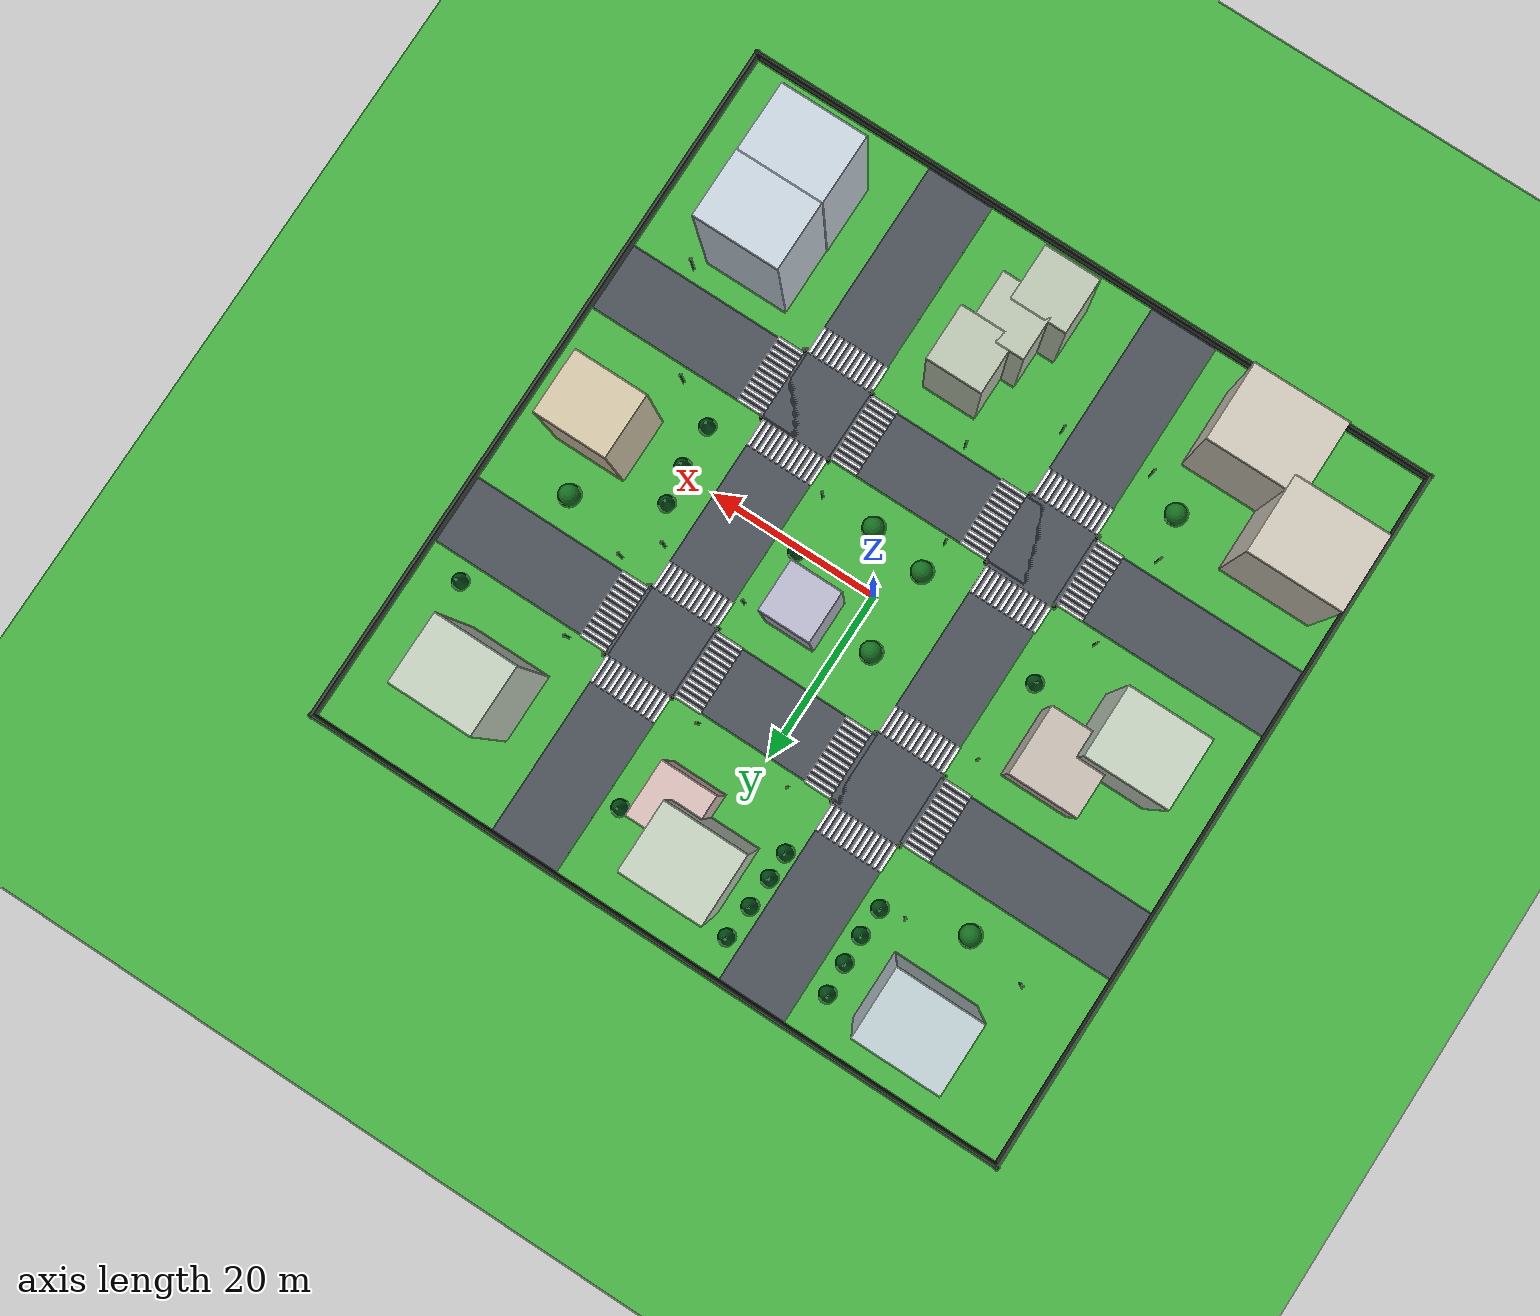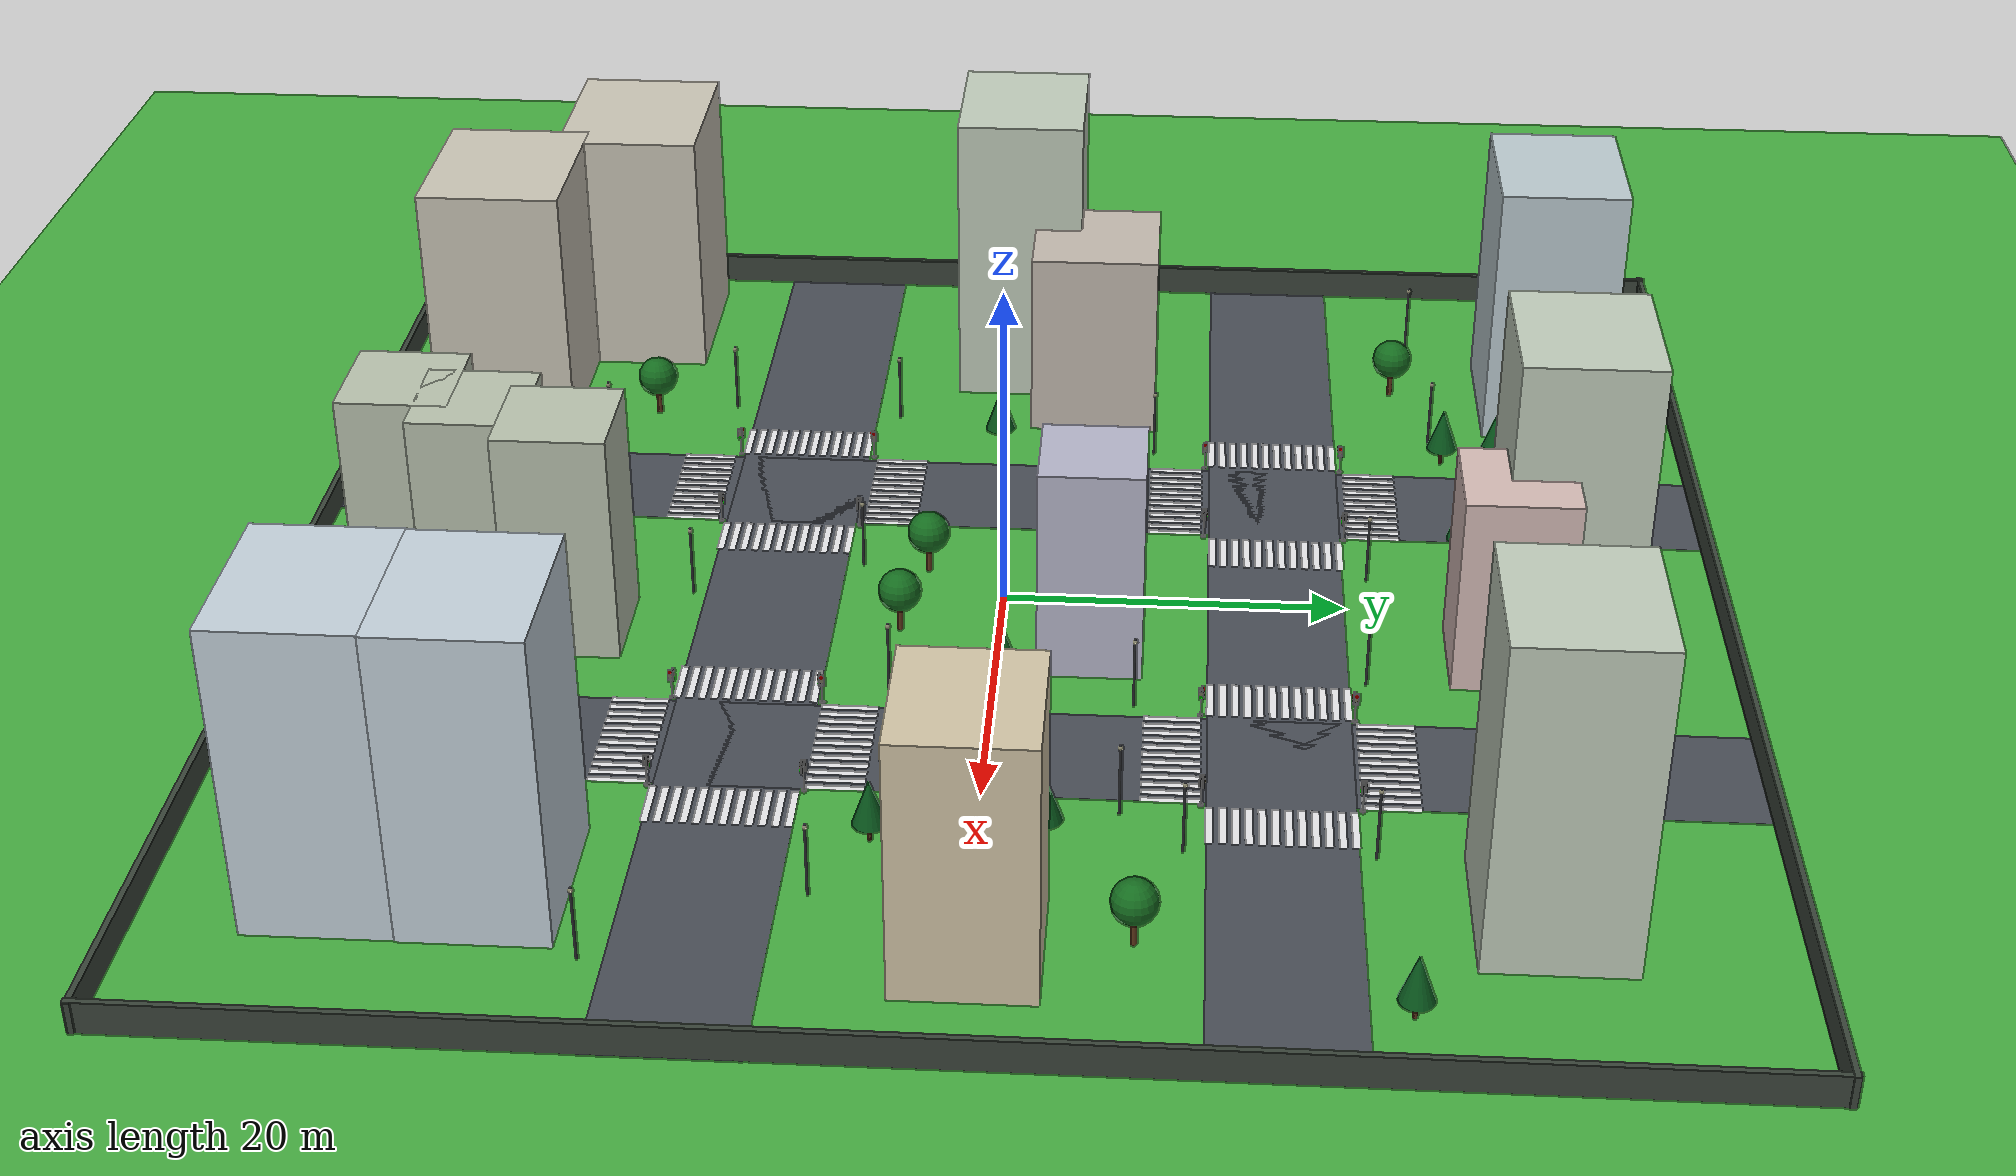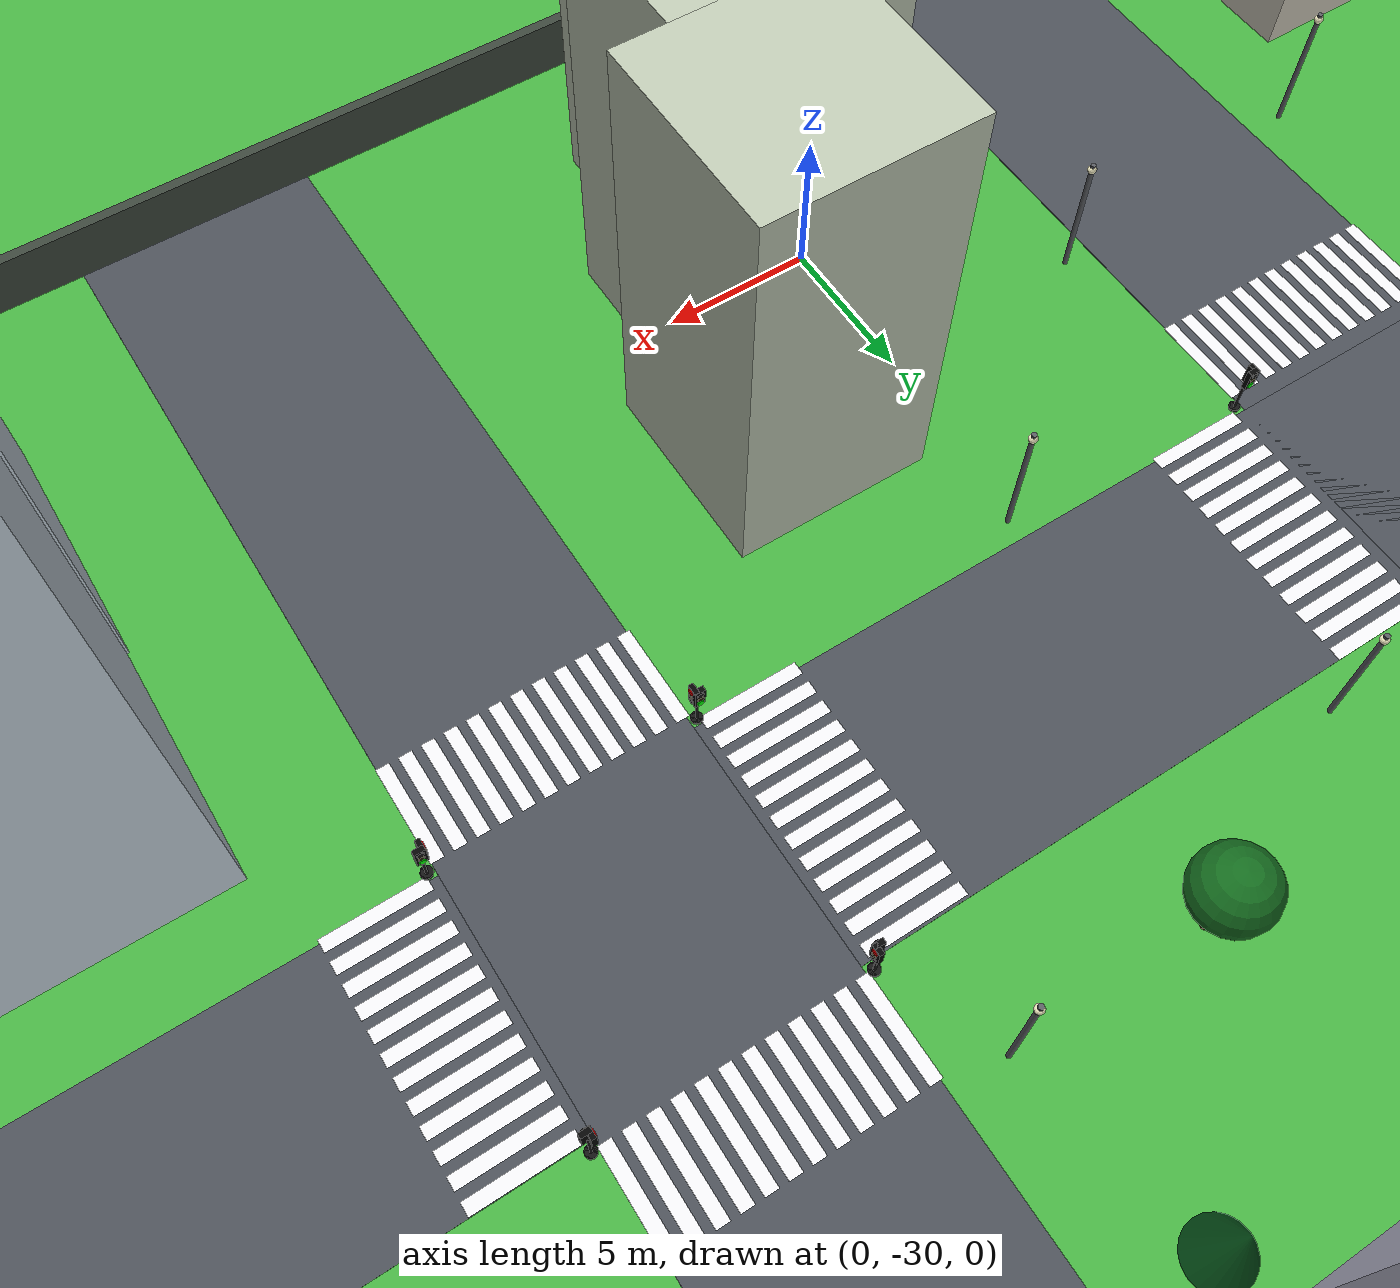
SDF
<sdf version='1.10'>
  <world name='city_second'>
    <gravity>0 0 -9.8100000000000005</gravity>
    <magnetic_field>6.0000000000000002e-06 2.3e-05 -4.1999999999999998e-05</magnetic_field>
    <physics name='1ms' type='ignored'>
      <max_step_size>0.001</max_step_size>
      <real_time_factor>1</real_time_factor>
      <real_time_update_rate>1000</real_time_update_rate>
    </physics>
    <plugin name='gz::sim::systems::Physics' filename='gz-sim-physics-system'/>
    <plugin name='gz::sim::systems::UserCommands' filename='gz-sim-user-commands-system'/>
    <plugin name='gz::sim::systems::SceneBroadcaster' filename='gz-sim-scene-broadcaster-system'/>
    <plugin name='gz::sim::systems::Sensors' filename='gz-sim-sensors-system'>
      <render_engine>ogre2</render_engine>
    </plugin>
    <scene>
      <ambient>0.7 0.7 0.7 1</ambient>
      <background>0.65 0.75 0.85 1</background>
      <shadows>false</shadows>
      <grid>false</grid>
    </scene>
    <atmosphere type='adiabatic'/>
    <model name='ground_plane'>
      <static>true</static>
      <link name='link'>
        <collision name='collision'>
          <geometry>
            <plane>
              <normal>0 0 1</normal>
              <size>300 300</size>
            </plane>
          </geometry>
          <surface>
            <friction>
              <ode/>
            </friction>
            <bounce/>
            <contact/>
          </surface>
        </collision>
        <visual name='visual'>
          <geometry>
            <plane>
              <normal>0 0 1</normal>
              <size>300 300</size>
            </plane>
          </geometry>
          <material>
            <ambient>0.280000001 0.689999998 0.25999999 1</ambient>
            <diffuse>0.280000001 0.689999998 0.25999999 1</diffuse>
            <specular>0.0299999993 0.0299999993 0.0299999993 1</specular>
          </material>
        </visual>
        <pose>0 0 0 0 0 0</pose>
        <inertial>
          <pose>0 0 0 0 0 0</pose>
          <mass>1</mass>
          <inertia>
            <ixx>1</ixx>
            <ixy>0</ixy>
            <ixz>0</ixz>
            <iyy>1</iyy>
            <iyz>0</iyz>
            <izz>1</izz>
          </inertia>
        </inertial>
        <enable_wind>false</enable_wind>
      </link>
      <pose>0 0 0 0 0 0</pose>
      <self_collide>false</self_collide>
    </model>
    <model name='road_h_2'>
      <static>true</static>
      <pose>0 16 0.01 0 0 0</pose>
      <link name='link'>
        <collision name='collision'>
          <geometry>
            <box>
              <size>84 8 0.02</size>
            </box>
          </geometry>
          <surface>
            <friction>
              <ode/>
            </friction>
            <bounce/>
            <contact/>
          </surface>
        </collision>
        <visual name='visual'>
          <geometry>
            <box>
              <size>84 8 0.02</size>
            </box>
          </geometry>
          <material>
            <ambient>0.289999992 0.310000002 0.340000004 1</ambient>
            <diffuse>0.289999992 0.310000002 0.340000004 1</diffuse>
            <specular>0.0299999993 0.0299999993 0.0299999993 1</specular>
          </material>
        </visual>
        <pose>0 0 0 0 0 0</pose>
        <inertial>
          <pose>0 0 0 0 0 0</pose>
          <mass>1</mass>
          <inertia>
            <ixx>1</ixx>
            <ixy>0</ixy>
            <ixz>0</ixz>
            <iyy>1</iyy>
            <iyz>0</iyz>
            <izz>1</izz>
          </inertia>
        </inertial>
        <enable_wind>false</enable_wind>
      </link>
      <self_collide>false</self_collide>
    </model>
    <model name='road_v_2'>
      <static>true</static>
      <pose>16 0 0.01 0 0 0</pose>
      <link name='link'>
        <collision name='collision'>
          <geometry>
            <box>
              <size>8 84 0.02</size>
            </box>
          </geometry>
          <surface>
            <friction>
              <ode/>
            </friction>
            <bounce/>
            <contact/>
          </surface>
        </collision>
        <visual name='visual'>
          <geometry>
            <box>
              <size>8 84 0.02</size>
            </box>
          </geometry>
          <material>
            <ambient>0.289999992 0.310000002 0.340000004 1</ambient>
            <diffuse>0.289999992 0.310000002 0.340000004 1</diffuse>
            <specular>0.0299999993 0.0299999993 0.0299999993 1</specular>
          </material>
        </visual>
        <pose>0 0 0 0 0 0</pose>
        <inertial>
          <pose>0 0 0 0 0 0</pose>
          <mass>1</mass>
          <inertia>
            <ixx>1</ixx>
            <ixy>0</ixy>
            <ixz>0</ixz>
            <iyy>1</iyy>
            <iyz>0</iyz>
            <izz>1</izz>
          </inertia>
        </inertial>
        <enable_wind>false</enable_wind>
      </link>
      <self_collide>false</self_collide>
    </model>
    <model name='house_1_2'>
      <static>true</static>
      <pose>4.5999999999999996 -24.800000000000001 7 0 0 0</pose>
      <link name='link'>
        <collision name='collision'>
          <geometry>
            <box>
              <size>6.5 6.5 14</size>
            </box>
          </geometry>
          <surface>
            <friction>
              <ode/>
            </friction>
            <bounce/>
            <contact/>
          </surface>
        </collision>
        <visual name='visual'>
          <geometry>
            <box>
              <size>6.5 6.5 14</size>
            </box>
          </geometry>
          <material>
            <ambient>0.730000019 0.769999981 0.689999998 1</ambient>
            <diffuse>0.730000019 0.769999981 0.689999998 1</diffuse>
            <specular>0.0299999993 0.0299999993 0.0299999993 1</specular>
          </material>
        </visual>
        <pose>0 0 0 0 0 0</pose>
        <inertial>
          <pose>0 0 0 0 0 0</pose>
          <mass>1</mass>
          <inertia>
            <ixx>1</ixx>
            <ixy>0</ixy>
            <ixz>0</ixz>
            <iyy>1</iyy>
            <iyz>0</iyz>
            <izz>1</izz>
          </inertia>
        </inertial>
        <enable_wind>false</enable_wind>
      </link>
      <self_collide>false</self_collide>
    </model>
    <model name='house_1_3'>
      <static>true</static>
      <pose>29.300000000000001 -24.300000000000001 9 0 0 0</pose>
      <link name='link'>
        <collision name='collision'>
          <geometry>
            <box>
              <size>10 8 18</size>
            </box>
          </geometry>
          <surface>
            <friction>
              <ode/>
            </friction>
            <bounce/>
            <contact/>
          </surface>
        </collision>
        <visual name='visual'>
          <geometry>
            <box>
              <size>10 8 18</size>
            </box>
          </geometry>
          <material>
            <ambient>0.779999971 0.829999983 0.870000005 1</ambient>
            <diffuse>0.779999971 0.829999983 0.870000005 1</diffuse>
            <specular>0.0299999993 0.0299999993 0.0299999993 1</specular>
          </material>
        </visual>
        <pose>0 0 0 0 0 0</pose>
        <inertial>
          <pose>0 0 0 0 0 0</pose>
          <mass>1</mass>
          <inertia>
            <ixx>1</ixx>
            <ixy>0</ixy>
            <ixz>0</ixz>
            <iyy>1</iyy>
            <iyz>0</iyz>
            <izz>1</izz>
          </inertia>
        </inertial>
        <enable_wind>false</enable_wind>
      </link>
      <self_collide>false</self_collide>
    </model>
    <model name='house_2_1'>
      <static>true</static>
      <pose>-25.100000000000001 4.4000000000000004 6 0 0 0</pose>
      <link name='link'>
        <collision name='collision'>
          <geometry>
            <box>
              <size>8 8 12</size>
            </box>
          </geometry>
          <surface>
            <friction>
              <ode/>
            </friction>
            <bounce/>
            <contact/>
          </surface>
        </collision>
        <visual name='visual'>
          <geometry>
            <box>
              <size>8 8 12</size>
            </box>
          </geometry>
          <material>
            <ambient>0.769999981 0.730000019 0.689999998 1</ambient>
            <diffuse>0.769999981 0.730000019 0.689999998 1</diffuse>
            <specular>0.0299999993 0.0299999993 0.0299999993 1</specular>
          </material>
        </visual>
        <pose>0 0 0 0 0 0</pose>
        <inertial>
          <pose>0 0 0 0 0 0</pose>
          <mass>1</mass>
          <inertia>
            <ixx>1</ixx>
            <ixy>0</ixy>
            <ixz>0</ixz>
            <iyy>1</iyy>
            <iyz>0</iyz>
            <izz>1</izz>
          </inertia>
        </inertial>
        <enable_wind>false</enable_wind>
      </link>
      <self_collide>false</self_collide>
    </model>
    <model name='house_2_2'>
      <static>true</static>
      <pose>5.2000000000000002 5.2999999999999998 6.5 0 0 0</pose>
      <link name='link'>
        <collision name='collision'>
          <geometry>
            <box>
              <size>6 6 13</size>
            </box>
          </geometry>
          <surface>
            <friction>
              <ode/>
            </friction>
            <bounce/>
            <contact/>
          </surface>
        </collision>
        <visual name='visual'>
          <geometry>
            <box>
              <size>6 6 13</size>
            </box>
          </geometry>
          <material>
            <ambient>0.720000029 0.720000029 0.800000012 1</ambient>
            <diffuse>0.720000029 0.720000029 0.800000012 1</diffuse>
            <specular>0.0299999993 0.0299999993 0.0299999993 1</specular>
          </material>
        </visual>
        <pose>0 0 0 0 0 0</pose>
        <inertial>
          <pose>0 0 0 0 0 0</pose>
          <mass>1</mass>
          <inertia>
            <ixx>1</ixx>
            <ixy>0</ixy>
            <ixz>0</ixz>
            <iyy>1</iyy>
            <iyz>0</iyz>
            <izz>1</izz>
          </inertia>
        </inertial>
        <enable_wind>false</enable_wind>
      </link>
      <self_collide>false</self_collide>
    </model>
    <model name='house_3_2'>
      <static>true</static>
      <pose>4.9000000000000004 28.899999999999999 6 0 0 0</pose>
      <link name='link'>
        <collision name='collision'>
          <geometry>
            <box>
              <size>6.5 6.5 12</size>
            </box>
          </geometry>
          <surface>
            <friction>
              <ode/>
            </friction>
            <bounce/>
            <contact/>
          </surface>
        </collision>
        <visual name='visual'>
          <geometry>
            <box>
              <size>6.5 6.5 12</size>
            </box>
          </geometry>
          <material>
            <ambient>0.839999974 0.74000001 0.720000029 1</ambient>
            <diffuse>0.839999974 0.74000001 0.720000029 1</diffuse>
            <specular>0.0299999993 0.0299999993 0.0299999993 1</specular>
          </material>
        </visual>
        <pose>0 0 0 0 0 0</pose>
        <inertial>
          <pose>0 0 0 0 0 0</pose>
          <mass>1</mass>
          <inertia>
            <ixx>1</ixx>
            <ixy>0</ixy>
            <ixz>0</ixz>
            <iyy>1</iyy>
            <iyz>0</iyz>
            <izz>1</izz>
          </inertia>
        </inertial>
        <enable_wind>false</enable_wind>
      </link>
      <self_collide>false</self_collide>
    </model>
    <model name='house_3_3'>
      <static>true</static>
      <pose>28.600000000000001 29.399999999999999 9.5 0 0 0</pose>
      <link name='link'>
        <collision name='collision'>
          <geometry>
            <box>
              <size>9.5 8 19</size>
            </box>
          </geometry>
          <surface>
            <friction>
              <ode/>
            </friction>
            <bounce/>
            <contact/>
          </surface>
        </collision>
        <visual name='visual'>
          <geometry>
            <box>
              <size>9.5 8 19</size>
            </box>
          </geometry>
          <material>
            <ambient>0.75999999 0.810000002 0.74000001 1</ambient>
            <diffuse>0.75999999 0.810000002 0.74000001 1</diffuse>
            <specular>0.0299999993 0.0299999993 0.0299999993 1</specular>
          </material>
        </visual>
        <pose>0 0 0 0 0 0</pose>
        <inertial>
          <pose>0 0 0 0 0 0</pose>
          <mass>1</mass>
          <inertia>
            <ixx>1</ixx>
            <ixy>0</ixy>
            <ixz>0</ixz>
            <iyy>1</iyy>
            <iyz>0</iyz>
            <izz>1</izz>
          </inertia>
        </inertial>
        <enable_wind>false</enable_wind>
      </link>
      <self_collide>false</self_collide>
    </model>
    <model name='robot_spawn_sidewalk_hint'>
      <static>true</static>
      <pose>0 0 0.021000000000000001 0 0 0</pose>
      <link name='link'>
        <visual name='visual'>
          <geometry>
            <box>
              <size>0.80000000000000004 0.80000000000000004 0.0050000000000000001</size>
            </box>
          </geometry>
          <material>
            <ambient>0.550000012 0.860000014 0.569999993 0.649999976</ambient>
            <diffuse>0.550000012 0.860000014 0.569999993 0.649999976</diffuse>
            <specular>0 0 0 1</specular>
          </material>
          <transparency>0.34999999999999998</transparency>
        </visual>
        <pose>0 0 0 0 0 0</pose>
        <inertial>
          <pose>0 0 0 0 0 0</pose>
          <mass>1</mass>
          <inertia>
            <ixx>1</ixx>
            <ixy>0</ixy>
            <ixz>0</ixz>
            <iyy>1</iyy>
            <iyz>0</iyz>
            <izz>1</izz>
          </inertia>
        </inertial>
        <enable_wind>false</enable_wind>
      </link>
      <self_collide>false</self_collide>
    </model>
    <model name='fence_north'>
      <static>true</static>
      <pose>0 42 0.94999999999999996 0 0 0</pose>
      <link name='link'>
        <collision name='collision'>
          <geometry>
            <box>
              <size>84.5 0.34999999999999998 1.8999999999999999</size>
            </box>
          </geometry>
          <surface>
            <friction>
              <ode/>
            </friction>
            <bounce/>
            <contact/>
          </surface>
        </collision>
        <visual name='visual'>
          <geometry>
            <box>
              <size>84.5 0.34999999999999998 1.8999999999999999</size>
            </box>
          </geometry>
          <material>
            <ambient>0.230000004 0.270000011 0.230000004 1</ambient>
            <diffuse>0.230000004 0.270000011 0.230000004 1</diffuse>
            <specular>0.0299999993 0.0299999993 0.0299999993 1</specular>
          </material>
        </visual>
        <pose>0 0 0 0 0 0</pose>
        <inertial>
          <pose>0 0 0 0 0 0</pose>
          <mass>1</mass>
          <inertia>
            <ixx>1</ixx>
            <ixy>0</ixy>
            <ixz>0</ixz>
            <iyy>1</iyy>
            <iyz>0</iyz>
            <izz>1</izz>
          </inertia>
        </inertial>
        <enable_wind>false</enable_wind>
      </link>
      <self_collide>false</self_collide>
    </model>
    <model name='fence_south'>
      <static>true</static>
      <pose>0 -42 0.94999999999999996 0 0 0</pose>
      <link name='link'>
        <collision name='collision'>
          <geometry>
            <box>
              <size>84.5 0.34999999999999998 1.8999999999999999</size>
            </box>
          </geometry>
          <surface>
            <friction>
              <ode/>
            </friction>
            <bounce/>
            <contact/>
          </surface>
        </collision>
        <visual name='visual'>
          <geometry>
            <box>
              <size>84.5 0.34999999999999998 1.8999999999999999</size>
            </box>
          </geometry>
          <material>
            <ambient>0.230000004 0.270000011 0.230000004 1</ambient>
            <diffuse>0.230000004 0.270000011 0.230000004 1</diffuse>
            <specular>0.0299999993 0.0299999993 0.0299999993 1</specular>
          </material>
        </visual>
        <pose>0 0 0 0 0 0</pose>
        <inertial>
          <pose>0 0 0 0 0 0</pose>
          <mass>1</mass>
          <inertia>
            <ixx>1</ixx>
            <ixy>0</ixy>
            <ixz>0</ixz>
            <iyy>1</iyy>
            <iyz>0</iyz>
            <izz>1</izz>
          </inertia>
        </inertial>
        <enable_wind>false</enable_wind>
      </link>
      <self_collide>false</self_collide>
    </model>
    <model name='fence_east'>
      <static>true</static>
      <pose>42 0 0.94999999999999996 0 0 0</pose>
      <link name='link'>
        <collision name='collision'>
          <geometry>
            <box>
              <size>0.34999999999999998 84.5 1.8999999999999999</size>
            </box>
          </geometry>
          <surface>
            <friction>
              <ode/>
            </friction>
            <bounce/>
            <contact/>
          </surface>
        </collision>
        <visual name='visual'>
          <geometry>
            <box>
              <size>0.34999999999999998 84.5 1.8999999999999999</size>
            </box>
          </geometry>
          <material>
            <ambient>0.230000004 0.270000011 0.230000004 1</ambient>
            <diffuse>0.230000004 0.270000011 0.230000004 1</diffuse>
            <specular>0.0299999993 0.0299999993 0.0299999993 1</specular>
          </material>
        </visual>
        <pose>0 0 0 0 0 0</pose>
        <inertial>
          <pose>0 0 0 0 0 0</pose>
          <mass>1</mass>
          <inertia>
            <ixx>1</ixx>
            <ixy>0</ixy>
            <ixz>0</ixz>
            <iyy>1</iyy>
            <iyz>0</iyz>
            <izz>1</izz>
          </inertia>
        </inertial>
        <enable_wind>false</enable_wind>
      </link>
      <self_collide>false</self_collide>
    </model>
    <model name='fence_west'>
      <static>true</static>
      <pose>-42 0 0.94999999999999996 0 0 0</pose>
      <link name='link'>
        <collision name='collision'>
          <geometry>
            <box>
              <size>0.34999999999999998 84.5 1.8999999999999999</size>
            </box>
          </geometry>
          <surface>
            <friction>
              <ode/>
            </friction>
            <bounce/>
            <contact/>
          </surface>
        </collision>
        <visual name='visual'>
          <geometry>
            <box>
              <size>0.34999999999999998 84.5 1.8999999999999999</size>
            </box>
          </geometry>
          <material>
            <ambient>0.230000004 0.270000011 0.230000004 1</ambient>
            <diffuse>0.230000004 0.270000011 0.230000004 1</diffuse>
            <specular>0.0299999993 0.0299999993 0.0299999993 1</specular>
          </material>
        </visual>
        <pose>0 0 0 0 0 0</pose>
        <inertial>
          <pose>0 0 0 0 0 0</pose>
          <mass>1</mass>
          <inertia>
            <ixx>1</ixx>
            <ixy>0</ixy>
            <ixz>0</ixz>
            <iyy>1</iyy>
            <iyz>0</iyz>
            <izz>1</izz>
          </inertia>
        </inertial>
        <enable_wind>false</enable_wind>
      </link>
      <self_collide>false</self_collide>
    </model>
    <model name='crosswalk_h_1_1_south_5'>
      <static>true</static>
      <pose>16.0335 21.8659 0.017000000000000001 0 0 0</pose>
      <link name='stripe_1'>
        <collision name='collision'>
          <geometry>
            <box>
              <size>0.41999999999999998 3.2000000000000002 0.01</size>
            </box>
          </geometry>
          <surface>
            <friction>
              <ode/>
            </friction>
            <bounce/>
            <contact/>
          </surface>
        </collision>
        <visual name='visual'>
          <geometry>
            <box>
              <size>0.41999999999999998 3.2000000000000002 0.01</size>
            </box>
          </geometry>
          <material>
            <ambient>0.920000017 0.920000017 0.930000007 1</ambient>
            <diffuse>0.920000017 0.920000017 0.930000007 1</diffuse>
            <specular>0.0299999993 0.0299999993 0.0299999993 1</specular>
          </material>
        </visual>
        <pose>-3.8500000000000001 0 0 0 0 0</pose>
        <inertial>
          <pose>0 0 0 0 0 0</pose>
          <mass>1</mass>
          <inertia>
            <ixx>1</ixx>
            <ixy>0</ixy>
            <ixz>0</ixz>
            <iyy>1</iyy>
            <iyz>0</iyz>
            <izz>1</izz>
          </inertia>
        </inertial>
        <enable_wind>false</enable_wind>
      </link>
      <link name='stripe_2'>
        <collision name='collision'>
          <geometry>
            <box>
              <size>0.41999999999999998 3.2000000000000002 0.01</size>
            </box>
          </geometry>
          <surface>
            <friction>
              <ode/>
            </friction>
            <bounce/>
            <contact/>
          </surface>
        </collision>
        <visual name='visual'>
          <geometry>
            <box>
              <size>0.41999999999999998 3.2000000000000002 0.01</size>
            </box>
          </geometry>
          <material>
            <ambient>0.920000017 0.920000017 0.930000007 1</ambient>
            <diffuse>0.920000017 0.920000017 0.930000007 1</diffuse>
            <specular>0.0299999993 0.0299999993 0.0299999993 1</specular>
          </material>
        </visual>
        <pose>-3.1500000000000004 0 0 0 0 0</pose>
        <inertial>
          <pose>0 0 0 0 0 0</pose>
          <mass>1</mass>
          <inertia>
            <ixx>1</ixx>
            <ixy>0</ixy>
            <ixz>0</ixz>
            <iyy>1</iyy>
            <iyz>0</iyz>
            <izz>1</izz>
          </inertia>
        </inertial>
        <enable_wind>false</enable_wind>
      </link>
      <link name='stripe_3'>
        <collision name='collision'>
          <geometry>
            <box>
              <size>0.41999999999999998 3.2000000000000002 0.01</size>
            </box>
          </geometry>
          <surface>
            <friction>
              <ode/>
            </friction>
            <bounce/>
            <contact/>
          </surface>
        </collision>
        <visual name='visual'>
          <geometry>
            <box>
              <size>0.41999999999999998 3.2000000000000002 0.01</size>
            </box>
          </geometry>
          <material>
            <ambient>0.920000017 0.920000017 0.930000007 1</ambient>
            <diffuse>0.920000017 0.920000017 0.930000007 1</diffuse>
            <specular>0.0299999993 0.0299999993 0.0299999993 1</specular>
          </material>
        </visual>
        <pose>-2.4499999999999993 0 0 0 0 0</pose>
        <inertial>
          <pose>0 0 0 0 0 0</pose>
          <mass>1</mass>
          <inertia>
            <ixx>1</ixx>
            <ixy>0</ixy>
            <ixz>0</ixz>
            <iyy>1</iyy>
            <iyz>0</iyz>
            <izz>1</izz>
          </inertia>
        </inertial>
        <enable_wind>false</enable_wind>
      </link>
      <link name='stripe_4'>
        <collision name='collision'>
          <geometry>
            <box>
              <size>0.41999999999999998 3.2000000000000002 0.01</size>
            </box>
          </geometry>
          <surface>
            <friction>
              <ode/>
            </friction>
            <bounce/>
            <contact/>
          </surface>
        </collision>
        <visual name='visual'>
          <geometry>
            <box>
              <size>0.41999999999999998 3.2000000000000002 0.01</size>
            </box>
          </geometry>
          <material>
            <ambient>0.920000017 0.920000017 0.930000007 1</ambient>
            <diffuse>0.920000017 0.920000017 0.930000007 1</diffuse>
            <specular>0.0299999993 0.0299999993 0.0299999993 1</specular>
          </material>
        </visual>
        <pose>-1.75 0 0 0 0 0</pose>
        <inertial>
          <pose>0 0 0 0 0 0</pose>
          <mass>1</mass>
          <inertia>
            <ixx>1</ixx>
            <ixy>0</ixy>
            <ixz>0</ixz>
            <iyy>1</iyy>
            <iyz>0</iyz>
            <izz>1</izz>
          </inertia>
        </inertial>
        <enable_wind>false</enable_wind>
      </link>
      <link name='stripe_5'>
        <collision name='collision'>
          <geometry>
            <box>
              <size>0.41999999999999998 3.2000000000000002 0.01</size>
            </box>
          </geometry>
          <surface>
            <friction>
              <ode/>
            </friction>
            <bounce/>
            <contact/>
          </surface>
        </collision>
        <visual name='visual'>
          <geometry>
            <box>
              <size>0.41999999999999998 3.2000000000000002 0.01</size>
            </box>
          </geometry>
          <material>
            <ambient>0.920000017 0.920000017 0.930000007 1</ambient>
            <diffuse>0.920000017 0.920000017 0.930000007 1</diffuse>
            <specular>0.0299999993 0.0299999993 0.0299999993 1</specular>
          </material>
        </visual>
        <pose>-1.0500000000000007 0 0 0 0 0</pose>
        <inertial>
          <pose>0 0 0 0 0 0</pose>
          <mass>1</mass>
          <inertia>
            <ixx>1</ixx>
            <ixy>0</ixy>
            <ixz>0</ixz>
            <iyy>1</iyy>
            <iyz>0</iyz>
            <izz>1</izz>
          </inertia>
        </inertial>
        <enable_wind>false</enable_wind>
      </link>
      <link name='stripe_6'>
        <collision name='collision'>
          <geometry>
            <box>
              <size>0.41999999999999998 3.2000000000000002 0.01</size>
            </box>
          </geometry>
          <surface>
            <friction>
              <ode/>
            </friction>
            <bounce/>
            <contact/>
          </surface>
        </collision>
        <visual name='visual'>
          <geometry>
            <box>
              <size>0.41999999999999998 3.2000000000000002 0.01</size>
            </box>
          </geometry>
          <material>
            <ambient>0.920000017 0.920000017 0.930000007 1</ambient>
            <diffuse>0.920000017 0.920000017 0.930000007 1</diffuse>
            <specular>0.0299999993 0.0299999993 0.0299999993 1</specular>
          </material>
        </visual>
        <pose>-0.34999999999999964 0 0 0 0 0</pose>
        <inertial>
          <pose>0 0 0 0 0 0</pose>
          <mass>1</mass>
          <inertia>
            <ixx>1</ixx>
            <ixy>0</ixy>
            <ixz>0</ixz>
            <iyy>1</iyy>
            <iyz>0</iyz>
            <izz>1</izz>
          </inertia>
        </inertial>
        <enable_wind>false</enable_wind>
      </link>
      <link name='stripe_7'>
        <collision name='collision'>
          <geometry>
            <box>
              <size>0.41999999999999998 3.2000000000000002 0.01</size>
            </box>
          </geometry>
          <surface>
            <friction>
              <ode/>
            </friction>
            <bounce/>
            <contact/>
          </surface>
        </collision>
        <visual name='visual'>
          <geometry>
            <box>
              <size>0.41999999999999998 3.2000000000000002 0.01</size>
            </box>
          </geometry>
          <material>
            <ambient>0.920000017 0.920000017 0.930000007 1</ambient>
            <diffuse>0.920000017 0.920000017 0.930000007 1</diffuse>
            <specular>0.0299999993 0.0299999993 0.0299999993 1</specular>
          </material>
        </visual>
        <pose>0.35000000000000142 0 0 0 0 0</pose>
        <inertial>
          <pose>0 0 0 0 0 0</pose>
          <mass>1</mass>
          <inertia>
            <ixx>1</ixx>
            <ixy>0</ixy>
            <ixz>0</ixz>
            <iyy>1</iyy>
            <iyz>0</iyz>
            <izz>1</izz>
          </inertia>
        </inertial>
        <enable_wind>false</enable_wind>
      </link>
      <link name='stripe_8'>
        <collision name='collision'>
          <geometry>
            <box>
              <size>0.41999999999999998 3.2000000000000002 0.01</size>
            </box>
          </geometry>
          <surface>
            <friction>
              <ode/>
            </friction>
            <bounce/>
            <contact/>
          </surface>
        </collision>
        <visual name='visual'>
          <geometry>
            <box>
              <size>0.41999999999999998 3.2000000000000002 0.01</size>
            </box>
          </geometry>
          <material>
            <ambient>0.920000017 0.920000017 0.930000007 1</ambient>
            <diffuse>0.920000017 0.920000017 0.930000007 1</diffuse>
            <specular>0.0299999993 0.0299999993 0.0299999993 1</specular>
          </material>
        </visual>
        <pose>1.0500000000000007 0 0 0 0 0</pose>
        <inertial>
          <pose>0 0 0 0 0 0</pose>
          <mass>1</mass>
          <inertia>
            <ixx>1</ixx>
            <ixy>0</ixy>
            <ixz>0</ixz>
            <iyy>1</iyy>
            <iyz>0</iyz>
            <izz>1</izz>
          </inertia>
        </inertial>
        <enable_wind>false</enable_wind>
      </link>
      <link name='stripe_9'>
        <collision name='collision'>
          <geometry>
            <box>
              <size>0.41999999999999998 3.2000000000000002 0.01</size>
            </box>
          </geometry>
          <surface>
            <friction>
              <ode/>
            </friction>
            <bounce/>
            <contact/>
          </surface>
        </collision>
        <visual name='visual'>
          <geometry>
            <box>
              <size>0.41999999999999998 3.2000000000000002 0.01</size>
            </box>
          </geometry>
          <material>
            <ambient>0.920000017 0.920000017 0.930000007 1</ambient>
            <diffuse>0.920000017 0.920000017 0.930000007 1</diffuse>
            <specular>0.0299999993 0.0299999993 0.0299999993 1</specular>
          </material>
        </visual>
        <pose>1.75 0 0 0 0 0</pose>
        <inertial>
          <pose>0 0 0 0 0 0</pose>
          <mass>1</mass>
          <inertia>
            <ixx>1</ixx>
            <ixy>0</ixy>
            <ixz>0</ixz>
            <iyy>1</iyy>
            <iyz>0</iyz>
            <izz>1</izz>
          </inertia>
        </inertial>
        <enable_wind>false</enable_wind>
      </link>
      <link name='stripe_10'>
        <collision name='collision'>
          <geometry>
            <box>
              <size>0.41999999999999998 3.2000000000000002 0.01</size>
            </box>
          </geometry>
          <surface>
            <friction>
              <ode/>
            </friction>
            <bounce/>
            <contact/>
          </surface>
        </collision>
        <visual name='visual'>
          <geometry>
            <box>
              <size>0.41999999999999998 3.2000000000000002 0.01</size>
            </box>
          </geometry>
          <material>
            <ambient>0.920000017 0.920000017 0.930000007 1</ambient>
            <diffuse>0.920000017 0.920000017 0.930000007 1</diffuse>
            <specular>0.0299999993 0.0299999993 0.0299999993 1</specular>
          </material>
        </visual>
        <pose>2.4499999999999993 0 0 0 0 0</pose>
        <inertial>
          <pose>0 0 0 0 0 0</pose>
          <mass>1</mass>
          <inertia>
            <ixx>1</ixx>
            <ixy>0</ixy>
            <ixz>0</ixz>
            <iyy>1</iyy>
            <iyz>0</iyz>
            <izz>1</izz>
          </inertia>
        </inertial>
        <enable_wind>false</enable_wind>
      </link>
      <link name='stripe_11'>
        <collision name='collision'>
          <geometry>
            <box>
              <size>0.41999999999999998 3.2000000000000002 0.01</size>
            </box>
          </geometry>
          <surface>
            <friction>
              <ode/>
            </friction>
            <bounce/>
            <contact/>
          </surface>
        </collision>
        <visual name='visual'>
          <geometry>
            <box>
              <size>0.41999999999999998 3.2000000000000002 0.01</size>
            </box>
          </geometry>
          <material>
            <ambient>0.920000017 0.920000017 0.930000007 1</ambient>
            <diffuse>0.920000017 0.920000017 0.930000007 1</diffuse>
            <specular>0.0299999993 0.0299999993 0.0299999993 1</specular>
          </material>
        </visual>
        <pose>3.1499999999999986 0 0 0 0 0</pose>
        <inertial>
          <pose>0 0 0 0 0 0</pose>
          <mass>1</mass>
          <inertia>
            <ixx>1</ixx>
            <ixy>0</ixy>
            <ixz>0</ixz>
            <iyy>1</iyy>
            <iyz>0</iyz>
            <izz>1</izz>
          </inertia>
        </inertial>
        <enable_wind>false</enable_wind>
      </link>
      <link name='stripe_12'>
        <collision name='collision'>
          <geometry>
            <box>
              <size>0.41999999999999998 3.2000000000000002 0.01</size>
            </box>
          </geometry>
          <surface>
            <friction>
              <ode/>
            </friction>
            <bounce/>
            <contact/>
          </surface>
        </collision>
        <visual name='visual'>
          <geometry>
            <box>
              <size>0.41999999999999998 3.2000000000000002 0.01</size>
            </box>
          </geometry>
          <material>
            <ambient>0.920000017 0.920000017 0.930000007 1</ambient>
            <diffuse>0.920000017 0.920000017 0.930000007 1</diffuse>
            <specular>0.0299999993 0.0299999993 0.0299999993 1</specular>
          </material>
        </visual>
        <pose>3.8500000000000014 0 0 0 0 0</pose>
        <inertial>
          <pose>0 0 0 0 0 0</pose>
          <mass>1</mass>
          <inertia>
            <ixx>1</ixx>
            <ixy>0</ixy>
            <ixz>0</ixz>
            <iyy>1</iyy>
            <iyz>0</iyz>
            <izz>1</izz>
          </inertia>
        </inertial>
        <enable_wind>false</enable_wind>
      </link>
      <self_collide>false</self_collide>
    </model>
    <model name='crosswalk_h_1_1_south_6'>
      <static>true</static>
      <pose>15.980700000000001 10.0922 0.017000000000000001 0 0 0</pose>
      <link name='stripe_1'>
        <collision name='collision'>
          <geometry>
            <box>
              <size>0.41999999999999998 3.2000000000000002 0.01</size>
            </box>
          </geometry>
          <surface>
            <friction>
              <ode/>
            </friction>
            <bounce/>
            <contact/>
          </surface>
        </collision>
        <visual name='visual'>
          <geometry>
            <box>
              <size>0.41999999999999998 3.2000000000000002 0.01</size>
            </box>
          </geometry>
          <material>
            <ambient>0.920000017 0.920000017 0.930000007 1</ambient>
            <diffuse>0.920000017 0.920000017 0.930000007 1</diffuse>
            <specular>0.0299999993 0.0299999993 0.0299999993 1</specular>
          </material>
        </visual>
        <pose>-3.8500000000000001 0 0 0 0 0</pose>
        <inertial>
          <pose>0 0 0 0 0 0</pose>
          <mass>1</mass>
          <inertia>
            <ixx>1</ixx>
            <ixy>0</ixy>
            <ixz>0</ixz>
            <iyy>1</iyy>
            <iyz>0</iyz>
            <izz>1</izz>
          </inertia>
        </inertial>
        <enable_wind>false</enable_wind>
      </link>
      <link name='stripe_2'>
        <collision name='collision'>
          <geometry>
            <box>
              <size>0.41999999999999998 3.2000000000000002 0.01</size>
            </box>
          </geometry>
          <surface>
            <friction>
              <ode/>
            </friction>
            <bounce/>
            <contact/>
          </surface>
        </collision>
        <visual name='visual'>
          <geometry>
            <box>
              <size>0.41999999999999998 3.2000000000000002 0.01</size>
            </box>
          </geometry>
          <material>
            <ambient>0.920000017 0.920000017 0.930000007 1</ambient>
            <diffuse>0.920000017 0.920000017 0.930000007 1</diffuse>
            <specular>0.0299999993 0.0299999993 0.0299999993 1</specular>
          </material>
        </visual>
        <pose>-3.1500000000000004 0 0 0 0 0</pose>
        <inertial>
          <pose>0 0 0 0 0 0</pose>
          <mass>1</mass>
          <inertia>
            <ixx>1</ixx>
            <ixy>0</ixy>
            <ixz>0</ixz>
            <iyy>1</iyy>
            <iyz>0</iyz>
            <izz>1</izz>
          </inertia>
        </inertial>
        <enable_wind>false</enable_wind>
      </link>
      <link name='stripe_3'>
        <collision name='collision'>
          <geometry>
            <box>
              <size>0.41999999999999998 3.2000000000000002 0.01</size>
            </box>
          </geometry>
          <surface>
            <friction>
              <ode/>
            </friction>
            <bounce/>
            <contact/>
          </surface>
        </collision>
        <visual name='visual'>
          <geometry>
            <box>
              <size>0.41999999999999998 3.2000000000000002 0.01</size>
            </box>
          </geometry>
          <material>
            <ambient>0.920000017 0.920000017 0.930000007 1</ambient>
            <diffuse>0.920000017 0.920000017 0.930000007 1</diffuse>
            <specular>0.0299999993 0.0299999993 0.0299999993 1</specular>
          </material>
        </visual>
        <pose>-2.4500000000000011 0 0 0 0 0</pose>
        <inertial>
          <pose>0 0 0 0 0 0</pose>
          <mass>1</mass>
          <inertia>
            <ixx>1</ixx>
            <ixy>0</ixy>
            <ixz>0</ixz>
            <iyy>1</iyy>
            <iyz>0</iyz>
            <izz>1</izz>
          </inertia>
        </inertial>
        <enable_wind>false</enable_wind>
      </link>
      <link name='stripe_4'>
        <collision name='collision'>
          <geometry>
            <box>
              <size>0.41999999999999998 3.2000000000000002 0.01</size>
            </box>
          </geometry>
          <surface>
            <friction>
              <ode/>
            </friction>
            <bounce/>
            <contact/>
          </surface>
        </collision>
        <visual name='visual'>
          <geometry>
            <box>
              <size>0.41999999999999998 3.2000000000000002 0.01</size>
            </box>
          </geometry>
          <material>
            <ambient>0.920000017 0.920000017 0.930000007 1</ambient>
            <diffuse>0.920000017 0.920000017 0.930000007 1</diffuse>
            <specular>0.0299999993 0.0299999993 0.0299999993 1</specular>
          </material>
        </visual>
        <pose>-1.75 0 0 0 0 0</pose>
        <inertial>
          <pose>0 0 0 0 0 0</pose>
          <mass>1</mass>
          <inertia>
            <ixx>1</ixx>
            <ixy>0</ixy>
            <ixz>0</ixz>
            <iyy>1</iyy>
            <iyz>0</iyz>
            <izz>1</izz>
          </inertia>
        </inertial>
        <enable_wind>false</enable_wind>
      </link>
      <link name='stripe_5'>
        <collision name='collision'>
          <geometry>
            <box>
              <size>0.41999999999999998 3.2000000000000002 0.01</size>
            </box>
          </geometry>
          <surface>
            <friction>
              <ode/>
            </friction>
            <bounce/>
            <contact/>
          </surface>
        </collision>
        <visual name='visual'>
          <geometry>
            <box>
              <size>0.41999999999999998 3.2000000000000002 0.01</size>
            </box>
          </geometry>
          <material>
            <ambient>0.920000017 0.920000017 0.930000007 1</ambient>
            <diffuse>0.920000017 0.920000017 0.930000007 1</diffuse>
            <specular>0.0299999993 0.0299999993 0.0299999993 1</specular>
          </material>
        </visual>
        <pose>-1.0500000000000007 0 0 0 0 0</pose>
        <inertial>
          <pose>0 0 0 0 0 0</pose>
          <mass>1</mass>
          <inertia>
            <ixx>1</ixx>
            <ixy>0</ixy>
            <ixz>0</ixz>
            <iyy>1</iyy>
            <iyz>0</iyz>
            <izz>1</izz>
          </inertia>
        </inertial>
        <enable_wind>false</enable_wind>
      </link>
      <link name='stripe_6'>
        <collision name='collision'>
          <geometry>
            <box>
              <size>0.41999999999999998 3.2000000000000002 0.01</size>
            </box>
          </geometry>
          <surface>
            <friction>
              <ode/>
            </friction>
            <bounce/>
            <contact/>
          </surface>
        </collision>
        <visual name='visual'>
          <geometry>
            <box>
              <size>0.41999999999999998 3.2000000000000002 0.01</size>
            </box>
          </geometry>
          <material>
            <ambient>0.920000017 0.920000017 0.930000007 1</ambient>
            <diffuse>0.920000017 0.920000017 0.930000007 1</diffuse>
            <specular>0.0299999993 0.0299999993 0.0299999993 1</specular>
          </material>
        </visual>
        <pose>-0.34999999999999964 0 0 0 0 0</pose>
        <inertial>
          <pose>0 0 0 0 0 0</pose>
          <mass>1</mass>
          <inertia>
            <ixx>1</ixx>
            <ixy>0</ixy>
            <ixz>0</ixz>
            <iyy>1</iyy>
            <iyz>0</iyz>
            <izz>1</izz>
          </inertia>
        </inertial>
        <enable_wind>false</enable_wind>
      </link>
      <link name='stripe_7'>
        <collision name='collision'>
          <geometry>
            <box>
              <size>0.41999999999999998 3.2000000000000002 0.01</size>
            </box>
          </geometry>
          <surface>
            <friction>
              <ode/>
            </friction>
            <bounce/>
            <contact/>
          </surface>
        </collision>
        <visual name='visual'>
          <geometry>
            <box>
              <size>0.41999999999999998 3.2000000000000002 0.01</size>
            </box>
          </geometry>
          <material>
            <ambient>0.920000017 0.920000017 0.930000007 1</ambient>
            <diffuse>0.920000017 0.920000017 0.930000007 1</diffuse>
            <specular>0.0299999993 0.0299999993 0.0299999993 1</specular>
          </material>
        </visual>
        <pose>0.34999999999999964 0 0 0 0 0</pose>
        <inertial>
          <pose>0 0 0 0 0 0</pose>
          <mass>1</mass>
          <inertia>
            <ixx>1</ixx>
            <ixy>0</ixy>
            <ixz>0</ixz>
            <iyy>1</iyy>
            <iyz>0</iyz>
            <izz>1</izz>
          </inertia>
        </inertial>
        <enable_wind>false</enable_wind>
      </link>
      <link name='stripe_8'>
        <collision name='collision'>
          <geometry>
            <box>
              <size>0.41999999999999998 3.2000000000000002 0.01</size>
            </box>
          </geometry>
          <surface>
            <friction>
              <ode/>
            </friction>
            <bounce/>
            <contact/>
          </surface>
        </collision>
        <visual name='visual'>
          <geometry>
            <box>
              <size>0.41999999999999998 3.2000000000000002 0.01</size>
            </box>
          </geometry>
          <material>
            <ambient>0.920000017 0.920000017 0.930000007 1</ambient>
            <diffuse>0.920000017 0.920000017 0.930000007 1</diffuse>
            <specular>0.0299999993 0.0299999993 0.0299999993 1</specular>
          </material>
        </visual>
        <pose>1.0499999999999989 0 0 0 0 0</pose>
        <inertial>
          <pose>0 0 0 0 0 0</pose>
          <mass>1</mass>
          <inertia>
            <ixx>1</ixx>
            <ixy>0</ixy>
            <ixz>0</ixz>
            <iyy>1</iyy>
            <iyz>0</iyz>
            <izz>1</izz>
          </inertia>
        </inertial>
        <enable_wind>false</enable_wind>
      </link>
      <link name='stripe_9'>
        <collision name='collision'>
          <geometry>
            <box>
              <size>0.41999999999999998 3.2000000000000002 0.01</size>
            </box>
          </geometry>
          <surface>
            <friction>
              <ode/>
            </friction>
            <bounce/>
            <contact/>
          </surface>
        </collision>
        <visual name='visual'>
          <geometry>
            <box>
              <size>0.41999999999999998 3.2000000000000002 0.01</size>
            </box>
          </geometry>
          <material>
            <ambient>0.920000017 0.920000017 0.930000007 1</ambient>
            <diffuse>0.920000017 0.920000017 0.930000007 1</diffuse>
            <specular>0.0299999993 0.0299999993 0.0299999993 1</specular>
          </material>
        </visual>
        <pose>1.7499999999999982 0 0 0 0 0</pose>
        <inertial>
          <pose>0 0 0 0 0 0</pose>
          <mass>1</mass>
          <inertia>
            <ixx>1</ixx>
            <ixy>0</ixy>
            <ixz>0</ixz>
            <iyy>1</iyy>
            <iyz>0</iyz>
            <izz>1</izz>
          </inertia>
        </inertial>
        <enable_wind>false</enable_wind>
      </link>
      <link name='stripe_10'>
        <collision name='collision'>
          <geometry>
            <box>
              <size>0.41999999999999998 3.2000000000000002 0.01</size>
            </box>
          </geometry>
          <surface>
            <friction>
              <ode/>
            </friction>
            <bounce/>
            <contact/>
          </surface>
        </collision>
        <visual name='visual'>
          <geometry>
            <box>
              <size>0.41999999999999998 3.2000000000000002 0.01</size>
            </box>
          </geometry>
          <material>
            <ambient>0.920000017 0.920000017 0.930000007 1</ambient>
            <diffuse>0.920000017 0.920000017 0.930000007 1</diffuse>
            <specular>0.0299999993 0.0299999993 0.0299999993 1</specular>
          </material>
        </visual>
        <pose>2.4500000000000011 0 0 0 0 0</pose>
        <inertial>
          <pose>0 0 0 0 0 0</pose>
          <mass>1</mass>
          <inertia>
            <ixx>1</ixx>
            <ixy>0</ixy>
            <ixz>0</ixz>
            <iyy>1</iyy>
            <iyz>0</iyz>
            <izz>1</izz>
          </inertia>
        </inertial>
        <enable_wind>false</enable_wind>
      </link>
      <link name='stripe_11'>
        <collision name='collision'>
          <geometry>
            <box>
              <size>0.41999999999999998 3.2000000000000002 0.01</size>
            </box>
          </geometry>
          <surface>
            <friction>
              <ode/>
            </friction>
            <bounce/>
            <contact/>
          </surface>
        </collision>
        <visual name='visual'>
          <geometry>
            <box>
              <size>0.41999999999999998 3.2000000000000002 0.01</size>
            </box>
          </geometry>
          <material>
            <ambient>0.920000017 0.920000017 0.930000007 1</ambient>
            <diffuse>0.920000017 0.920000017 0.930000007 1</diffuse>
            <specular>0.0299999993 0.0299999993 0.0299999993 1</specular>
          </material>
        </visual>
        <pose>3.1500000000000004 0 0 0 0 0</pose>
        <inertial>
          <pose>0 0 0 0 0 0</pose>
          <mass>1</mass>
          <inertia>
            <ixx>1</ixx>
            <ixy>0</ixy>
            <ixz>0</ixz>
            <iyy>1</iyy>
            <iyz>0</iyz>
            <izz>1</izz>
          </inertia>
        </inertial>
        <enable_wind>false</enable_wind>
      </link>
      <link name='stripe_12'>
        <collision name='collision'>
          <geometry>
            <box>
              <size>0.41999999999999998 3.2000000000000002 0.01</size>
            </box>
          </geometry>
          <surface>
            <friction>
              <ode/>
            </friction>
            <bounce/>
            <contact/>
          </surface>
        </collision>
        <visual name='visual'>
          <geometry>
            <box>
              <size>0.41999999999999998 3.2000000000000002 0.01</size>
            </box>
          </geometry>
          <material>
            <ambient>0.920000017 0.920000017 0.930000007 1</ambient>
            <diffuse>0.920000017 0.920000017 0.930000007 1</diffuse>
            <specular>0.0299999993 0.0299999993 0.0299999993 1</specular>
          </material>
        </visual>
        <pose>3.8499999999999996 0 0 0 0 0</pose>
        <inertial>
          <pose>0 0 0 0 0 0</pose>
          <mass>1</mass>
          <inertia>
            <ixx>1</ixx>
            <ixy>0</ixy>
            <ixz>0</ixz>
            <iyy>1</iyy>
            <iyz>0</iyz>
            <izz>1</izz>
          </inertia>
        </inertial>
        <enable_wind>false</enable_wind>
      </link>
      <self_collide>false</self_collide>
    </model>
    <model name='crosswalk_v_2_1_east_6'>
      <static>true</static>
      <pose>10.091699999999999 16.024799999999999 0.017000000000000001 0 0 0</pose>
      <link name='stripe_1'>
        <collision name='collision'>
          <geometry>
            <box>
              <size>3.2000000000000002 0.41999999999999998 0.01</size>
            </box>
          </geometry>
          <surface>
            <friction>
              <ode/>
            </friction>
            <bounce/>
            <contact/>
          </surface>
        </collision>
        <visual name='visual'>
          <geometry>
            <box>
              <size>3.2000000000000002 0.41999999999999998 0.01</size>
            </box>
          </geometry>
          <material>
            <ambient>0.920000017 0.920000017 0.930000007 1</ambient>
            <diffuse>0.920000017 0.920000017 0.930000007 1</diffuse>
            <specular>0.0299999993 0.0299999993 0.0299999993 1</specular>
          </material>
        </visual>
        <pose>0 -3.8500000000000001 0 0 0 0</pose>
        <inertial>
          <pose>0 0 0 0 0 0</pose>
          <mass>1</mass>
          <inertia>
            <ixx>1</ixx>
            <ixy>0</ixy>
            <ixz>0</ixz>
            <iyy>1</iyy>
            <iyz>0</iyz>
            <izz>1</izz>
          </inertia>
        </inertial>
        <enable_wind>false</enable_wind>
      </link>
      <link name='stripe_2'>
        <collision name='collision'>
          <geometry>
            <box>
              <size>3.2000000000000002 0.41999999999999998 0.01</size>
            </box>
          </geometry>
          <surface>
            <friction>
              <ode/>
            </friction>
            <bounce/>
            <contact/>
          </surface>
        </collision>
        <visual name='visual'>
          <geometry>
            <box>
              <size>3.2000000000000002 0.41999999999999998 0.01</size>
            </box>
          </geometry>
          <material>
            <ambient>0.920000017 0.920000017 0.930000007 1</ambient>
            <diffuse>0.920000017 0.920000017 0.930000007 1</diffuse>
            <specular>0.0299999993 0.0299999993 0.0299999993 1</specular>
          </material>
        </visual>
        <pose>0 -3.1500000000000004 0 0 0 0</pose>
        <inertial>
          <pose>0 0 0 0 0 0</pose>
          <mass>1</mass>
          <inertia>
            <ixx>1</ixx>
            <ixy>0</ixy>
            <ixz>0</ixz>
            <iyy>1</iyy>
            <iyz>0</iyz>
            <izz>1</izz>
          </inertia>
        </inertial>
        <enable_wind>false</enable_wind>
      </link>
      <link name='stripe_3'>
        <collision name='collision'>
          <geometry>
            <box>
              <size>3.2000000000000002 0.41999999999999998 0.01</size>
            </box>
          </geometry>
          <surface>
            <friction>
              <ode/>
            </friction>
            <bounce/>
            <contact/>
          </surface>
        </collision>
        <visual name='visual'>
          <geometry>
            <box>
              <size>3.2000000000000002 0.41999999999999998 0.01</size>
            </box>
          </geometry>
          <material>
            <ambient>0.920000017 0.920000017 0.930000007 1</ambient>
            <diffuse>0.920000017 0.920000017 0.930000007 1</diffuse>
            <specular>0.0299999993 0.0299999993 0.0299999993 1</specular>
          </material>
        </visual>
        <pose>0 -2.4499999999999993 0 0 0 0</pose>
        <inertial>
          <pose>0 0 0 0 0 0</pose>
          <mass>1</mass>
          <inertia>
            <ixx>1</ixx>
            <ixy>0</ixy>
            <ixz>0</ixz>
            <iyy>1</iyy>
            <iyz>0</iyz>
            <izz>1</izz>
          </inertia>
        </inertial>
        <enable_wind>false</enable_wind>
      </link>
      <link name='stripe_4'>
        <collision name='collision'>
          <geometry>
            <box>
              <size>3.2000000000000002 0.41999999999999998 0.01</size>
            </box>
          </geometry>
          <surface>
            <friction>
              <ode/>
            </friction>
            <bounce/>
            <contact/>
          </surface>
        </collision>
        <visual name='visual'>
          <geometry>
            <box>
              <size>3.2000000000000002 0.41999999999999998 0.01</size>
            </box>
          </geometry>
          <material>
            <ambient>0.920000017 0.920000017 0.930000007 1</ambient>
            <diffuse>0.920000017 0.920000017 0.930000007 1</diffuse>
            <specular>0.0299999993 0.0299999993 0.0299999993 1</specular>
          </material>
        </visual>
        <pose>0 -1.75 0 0 0 0</pose>
        <inertial>
          <pose>0 0 0 0 0 0</pose>
          <mass>1</mass>
          <inertia>
            <ixx>1</ixx>
            <ixy>0</ixy>
            <ixz>0</ixz>
            <iyy>1</iyy>
            <iyz>0</iyz>
            <izz>1</izz>
          </inertia>
        </inertial>
        <enable_wind>false</enable_wind>
      </link>
      <link name='stripe_5'>
        <collision name='collision'>
          <geometry>
            <box>
              <size>3.2000000000000002 0.41999999999999998 0.01</size>
            </box>
          </geometry>
          <surface>
            <friction>
              <ode/>
            </friction>
            <bounce/>
            <contact/>
          </surface>
        </collision>
        <visual name='visual'>
          <geometry>
            <box>
              <size>3.2000000000000002 0.41999999999999998 0.01</size>
            </box>
          </geometry>
          <material>
            <ambient>0.920000017 0.920000017 0.930000007 1</ambient>
            <diffuse>0.920000017 0.920000017 0.930000007 1</diffuse>
            <specular>0.0299999993 0.0299999993 0.0299999993 1</specular>
          </material>
        </visual>
        <pose>0 -1.0500000000000007 0 0 0 0</pose>
        <inertial>
          <pose>0 0 0 0 0 0</pose>
          <mass>1</mass>
          <inertia>
            <ixx>1</ixx>
            <ixy>0</ixy>
            <ixz>0</ixz>
            <iyy>1</iyy>
            <iyz>0</iyz>
            <izz>1</izz>
          </inertia>
        </inertial>
        <enable_wind>false</enable_wind>
      </link>
      <link name='stripe_6'>
        <collision name='collision'>
          <geometry>
            <box>
              <size>3.2000000000000002 0.41999999999999998 0.01</size>
            </box>
          </geometry>
          <surface>
            <friction>
              <ode/>
            </friction>
            <bounce/>
            <contact/>
          </surface>
        </collision>
        <visual name='visual'>
          <geometry>
            <box>
              <size>3.2000000000000002 0.41999999999999998 0.01</size>
            </box>
          </geometry>
          <material>
            <ambient>0.920000017 0.920000017 0.930000007 1</ambient>
            <diffuse>0.920000017 0.920000017 0.930000007 1</diffuse>
            <specular>0.0299999993 0.0299999993 0.0299999993 1</specular>
          </material>
        </visual>
        <pose>0 -0.34999999999999964 0 0 0 0</pose>
        <inertial>
          <pose>0 0 0 0 0 0</pose>
          <mass>1</mass>
          <inertia>
            <ixx>1</ixx>
            <ixy>0</ixy>
            <ixz>0</ixz>
            <iyy>1</iyy>
            <iyz>0</iyz>
            <izz>1</izz>
          </inertia>
        </inertial>
        <enable_wind>false</enable_wind>
      </link>
      <link name='stripe_7'>
        <collision name='collision'>
          <geometry>
            <box>
              <size>3.2000000000000002 0.41999999999999998 0.01</size>
            </box>
          </geometry>
          <surface>
            <friction>
              <ode/>
            </friction>
            <bounce/>
            <contact/>
          </surface>
        </collision>
        <visual name='visual'>
          <geometry>
            <box>
              <size>3.2000000000000002 0.41999999999999998 0.01</size>
            </box>
          </geometry>
          <material>
            <ambient>0.920000017 0.920000017 0.930000007 1</ambient>
            <diffuse>0.920000017 0.920000017 0.930000007 1</diffuse>
            <specular>0.0299999993 0.0299999993 0.0299999993 1</specular>
          </material>
        </visual>
        <pose>0 0.35000000000000142 0 0 0 0</pose>
        <inertial>
          <pose>0 0 0 0 0 0</pose>
          <mass>1</mass>
          <inertia>
            <ixx>1</ixx>
            <ixy>0</ixy>
            <ixz>0</ixz>
            <iyy>1</iyy>
            <iyz>0</iyz>
            <izz>1</izz>
          </inertia>
        </inertial>
        <enable_wind>false</enable_wind>
      </link>
      <link name='stripe_8'>
        <collision name='collision'>
          <geometry>
            <box>
              <size>3.2000000000000002 0.41999999999999998 0.01</size>
            </box>
          </geometry>
          <surface>
            <friction>
              <ode/>
            </friction>
            <bounce/>
            <contact/>
          </surface>
        </collision>
        <visual name='visual'>
          <geometry>
            <box>
              <size>3.2000000000000002 0.41999999999999998 0.01</size>
            </box>
          </geometry>
          <material>
            <ambient>0.920000017 0.920000017 0.930000007 1</ambient>
            <diffuse>0.920000017 0.920000017 0.930000007 1</diffuse>
            <specular>0.0299999993 0.0299999993 0.0299999993 1</specular>
          </material>
        </visual>
        <pose>0 1.0500000000000007 0 0 0 0</pose>
        <inertial>
          <pose>0 0 0 0 0 0</pose>
          <mass>1</mass>
          <inertia>
            <ixx>1</ixx>
            <ixy>0</ixy>
            <ixz>0</ixz>
            <iyy>1</iyy>
            <iyz>0</iyz>
            <izz>1</izz>
          </inertia>
        </inertial>
        <enable_wind>false</enable_wind>
      </link>
      <link name='stripe_9'>
        <collision name='collision'>
          <geometry>
            <box>
              <size>3.2000000000000002 0.41999999999999998 0.01</size>
            </box>
          </geometry>
          <surface>
            <friction>
              <ode/>
            </friction>
            <bounce/>
            <contact/>
          </surface>
        </collision>
        <visual name='visual'>
          <geometry>
            <box>
              <size>3.2000000000000002 0.41999999999999998 0.01</size>
            </box>
          </geometry>
          <material>
            <ambient>0.920000017 0.920000017 0.930000007 1</ambient>
            <diffuse>0.920000017 0.920000017 0.930000007 1</diffuse>
            <specular>0.0299999993 0.0299999993 0.0299999993 1</specular>
          </material>
        </visual>
        <pose>0 1.75 0 0 0 0</pose>
        <inertial>
          <pose>0 0 0 0 0 0</pose>
          <mass>1</mass>
          <inertia>
            <ixx>1</ixx>
            <ixy>0</ixy>
            <ixz>0</ixz>
            <iyy>1</iyy>
            <iyz>0</iyz>
            <izz>1</izz>
          </inertia>
        </inertial>
        <enable_wind>false</enable_wind>
      </link>
      <link name='stripe_10'>
        <collision name='collision'>
          <geometry>
            <box>
              <size>3.2000000000000002 0.41999999999999998 0.01</size>
            </box>
          </geometry>
          <surface>
            <friction>
              <ode/>
            </friction>
            <bounce/>
            <contact/>
          </surface>
        </collision>
        <visual name='visual'>
          <geometry>
            <box>
              <size>3.2000000000000002 0.41999999999999998 0.01</size>
            </box>
          </geometry>
          <material>
            <ambient>0.920000017 0.920000017 0.930000007 1</ambient>
            <diffuse>0.920000017 0.920000017 0.930000007 1</diffuse>
            <specular>0.0299999993 0.0299999993 0.0299999993 1</specular>
          </material>
        </visual>
        <pose>0 2.4499999999999993 0 0 0 0</pose>
        <inertial>
          <pose>0 0 0 0 0 0</pose>
          <mass>1</mass>
          <inertia>
            <ixx>1</ixx>
            <ixy>0</ixy>
            <ixz>0</ixz>
            <iyy>1</iyy>
            <iyz>0</iyz>
            <izz>1</izz>
          </inertia>
        </inertial>
        <enable_wind>false</enable_wind>
      </link>
      <link name='stripe_11'>
        <collision name='collision'>
          <geometry>
            <box>
              <size>3.2000000000000002 0.41999999999999998 0.01</size>
            </box>
          </geometry>
          <surface>
            <friction>
              <ode/>
            </friction>
            <bounce/>
            <contact/>
          </surface>
        </collision>
        <visual name='visual'>
          <geometry>
            <box>
              <size>3.2000000000000002 0.41999999999999998 0.01</size>
            </box>
          </geometry>
          <material>
            <ambient>0.920000017 0.920000017 0.930000007 1</ambient>
            <diffuse>0.920000017 0.920000017 0.930000007 1</diffuse>
            <specular>0.0299999993 0.0299999993 0.0299999993 1</specular>
          </material>
        </visual>
        <pose>0 3.1499999999999986 0 0 0 0</pose>
        <inertial>
          <pose>0 0 0 0 0 0</pose>
          <mass>1</mass>
          <inertia>
            <ixx>1</ixx>
            <ixy>0</ixy>
            <ixz>0</ixz>
            <iyy>1</iyy>
            <iyz>0</iyz>
            <izz>1</izz>
          </inertia>
        </inertial>
        <enable_wind>false</enable_wind>
      </link>
      <link name='stripe_12'>
        <collision name='collision'>
          <geometry>
            <box>
              <size>3.2000000000000002 0.41999999999999998 0.01</size>
            </box>
          </geometry>
          <surface>
            <friction>
              <ode/>
            </friction>
            <bounce/>
            <contact/>
          </surface>
        </collision>
        <visual name='visual'>
          <geometry>
            <box>
              <size>3.2000000000000002 0.41999999999999998 0.01</size>
            </box>
          </geometry>
          <material>
            <ambient>0.920000017 0.920000017 0.930000007 1</ambient>
            <diffuse>0.920000017 0.920000017 0.930000007 1</diffuse>
            <specular>0.0299999993 0.0299999993 0.0299999993 1</specular>
          </material>
        </visual>
        <pose>0 3.8500000000000014 0 0 0 0</pose>
        <inertial>
          <pose>0 0 0 0 0 0</pose>
          <mass>1</mass>
          <inertia>
            <ixx>1</ixx>
            <ixy>0</ixy>
            <ixz>0</ixz>
            <iyy>1</iyy>
            <iyz>0</iyz>
            <izz>1</izz>
          </inertia>
        </inertial>
        <enable_wind>false</enable_wind>
      </link>
      <self_collide>false</self_collide>
    </model>
    <model name='crosswalk_v_2_1_east_7'>
      <static>true</static>
      <pose>21.9419 16.021699999999999 0.017000000000000001 0 0 0</pose>
      <link name='stripe_1'>
        <collision name='collision'>
          <geometry>
            <box>
              <size>3.2000000000000002 0.41999999999999998 0.01</size>
            </box>
          </geometry>
          <surface>
            <friction>
              <ode/>
            </friction>
            <bounce/>
            <contact/>
          </surface>
        </collision>
        <visual name='visual'>
          <geometry>
            <box>
              <size>3.2000000000000002 0.41999999999999998 0.01</size>
            </box>
          </geometry>
          <material>
            <ambient>0.920000017 0.920000017 0.930000007 1</ambient>
            <diffuse>0.920000017 0.920000017 0.930000007 1</diffuse>
            <specular>0.0299999993 0.0299999993 0.0299999993 1</specular>
          </material>
        </visual>
        <pose>0 -3.8500000000000001 0 0 0 0</pose>
        <inertial>
          <pose>0 0 0 0 0 0</pose>
          <mass>1</mass>
          <inertia>
            <ixx>1</ixx>
            <ixy>0</ixy>
            <ixz>0</ixz>
            <iyy>1</iyy>
            <iyz>0</iyz>
            <izz>1</izz>
          </inertia>
        </inertial>
        <enable_wind>false</enable_wind>
      </link>
      <link name='stripe_2'>
        <collision name='collision'>
          <geometry>
            <box>
              <size>3.2000000000000002 0.41999999999999998 0.01</size>
            </box>
          </geometry>
          <surface>
            <friction>
              <ode/>
            </friction>
            <bounce/>
            <contact/>
          </surface>
        </collision>
        <visual name='visual'>
          <geometry>
            <box>
              <size>3.2000000000000002 0.41999999999999998 0.01</size>
            </box>
          </geometry>
          <material>
            <ambient>0.920000017 0.920000017 0.930000007 1</ambient>
            <diffuse>0.920000017 0.920000017 0.930000007 1</diffuse>
            <specular>0.0299999993 0.0299999993 0.0299999993 1</specular>
          </material>
        </visual>
        <pose>0 -3.1500000000000004 0 0 0 0</pose>
        <inertial>
          <pose>0 0 0 0 0 0</pose>
          <mass>1</mass>
          <inertia>
            <ixx>1</ixx>
            <ixy>0</ixy>
            <ixz>0</ixz>
            <iyy>1</iyy>
            <iyz>0</iyz>
            <izz>1</izz>
          </inertia>
        </inertial>
        <enable_wind>false</enable_wind>
      </link>
      <link name='stripe_3'>
        <collision name='collision'>
          <geometry>
            <box>
              <size>3.2000000000000002 0.41999999999999998 0.01</size>
            </box>
          </geometry>
          <surface>
            <friction>
              <ode/>
            </friction>
            <bounce/>
            <contact/>
          </surface>
        </collision>
        <visual name='visual'>
          <geometry>
            <box>
              <size>3.2000000000000002 0.41999999999999998 0.01</size>
            </box>
          </geometry>
          <material>
            <ambient>0.920000017 0.920000017 0.930000007 1</ambient>
            <diffuse>0.920000017 0.920000017 0.930000007 1</diffuse>
            <specular>0.0299999993 0.0299999993 0.0299999993 1</specular>
          </material>
        </visual>
        <pose>0 -2.4499999999999993 0 0 0 0</pose>
        <inertial>
          <pose>0 0 0 0 0 0</pose>
          <mass>1</mass>
          <inertia>
            <ixx>1</ixx>
            <ixy>0</ixy>
            <ixz>0</ixz>
            <iyy>1</iyy>
            <iyz>0</iyz>
            <izz>1</izz>
          </inertia>
        </inertial>
        <enable_wind>false</enable_wind>
      </link>
      <link name='stripe_4'>
        <collision name='collision'>
          <geometry>
            <box>
              <size>3.2000000000000002 0.41999999999999998 0.01</size>
            </box>
          </geometry>
          <surface>
            <friction>
              <ode/>
            </friction>
            <bounce/>
            <contact/>
          </surface>
        </collision>
        <visual name='visual'>
          <geometry>
            <box>
              <size>3.2000000000000002 0.41999999999999998 0.01</size>
            </box>
          </geometry>
          <material>
            <ambient>0.920000017 0.920000017 0.930000007 1</ambient>
            <diffuse>0.920000017 0.920000017 0.930000007 1</diffuse>
            <specular>0.0299999993 0.0299999993 0.0299999993 1</specular>
          </material>
        </visual>
        <pose>0 -1.75 0 0 0 0</pose>
        <inertial>
          <pose>0 0 0 0 0 0</pose>
          <mass>1</mass>
          <inertia>
            <ixx>1</ixx>
            <ixy>0</ixy>
            <ixz>0</ixz>
            <iyy>1</iyy>
            <iyz>0</iyz>
            <izz>1</izz>
          </inertia>
        </inertial>
        <enable_wind>false</enable_wind>
      </link>
      <link name='stripe_5'>
        <collision name='collision'>
          <geometry>
            <box>
              <size>3.2000000000000002 0.41999999999999998 0.01</size>
            </box>
          </geometry>
          <surface>
            <friction>
              <ode/>
            </friction>
            <bounce/>
            <contact/>
          </surface>
        </collision>
        <visual name='visual'>
          <geometry>
            <box>
              <size>3.2000000000000002 0.41999999999999998 0.01</size>
            </box>
          </geometry>
          <material>
            <ambient>0.920000017 0.920000017 0.930000007 1</ambient>
            <diffuse>0.920000017 0.920000017 0.930000007 1</diffuse>
            <specular>0.0299999993 0.0299999993 0.0299999993 1</specular>
          </material>
        </visual>
        <pose>0 -1.0500000000000007 0 0 0 0</pose>
        <inertial>
          <pose>0 0 0 0 0 0</pose>
          <mass>1</mass>
          <inertia>
            <ixx>1</ixx>
            <ixy>0</ixy>
            <ixz>0</ixz>
            <iyy>1</iyy>
            <iyz>0</iyz>
            <izz>1</izz>
          </inertia>
        </inertial>
        <enable_wind>false</enable_wind>
      </link>
      <link name='stripe_6'>
        <collision name='collision'>
          <geometry>
            <box>
              <size>3.2000000000000002 0.41999999999999998 0.01</size>
            </box>
          </geometry>
          <surface>
            <friction>
              <ode/>
            </friction>
            <bounce/>
            <contact/>
          </surface>
        </collision>
        <visual name='visual'>
          <geometry>
            <box>
              <size>3.2000000000000002 0.41999999999999998 0.01</size>
            </box>
          </geometry>
          <material>
            <ambient>0.920000017 0.920000017 0.930000007 1</ambient>
            <diffuse>0.920000017 0.920000017 0.930000007 1</diffuse>
            <specular>0.0299999993 0.0299999993 0.0299999993 1</specular>
          </material>
        </visual>
        <pose>0 -0.34999999999999964 0 0 0 0</pose>
        <inertial>
          <pose>0 0 0 0 0 0</pose>
          <mass>1</mass>
          <inertia>
            <ixx>1</ixx>
            <ixy>0</ixy>
            <ixz>0</ixz>
            <iyy>1</iyy>
            <iyz>0</iyz>
            <izz>1</izz>
          </inertia>
        </inertial>
        <enable_wind>false</enable_wind>
      </link>
      <link name='stripe_7'>
        <collision name='collision'>
          <geometry>
            <box>
              <size>3.2000000000000002 0.41999999999999998 0.01</size>
            </box>
          </geometry>
          <surface>
            <friction>
              <ode/>
            </friction>
            <bounce/>
            <contact/>
          </surface>
        </collision>
        <visual name='visual'>
          <geometry>
            <box>
              <size>3.2000000000000002 0.41999999999999998 0.01</size>
            </box>
          </geometry>
          <material>
            <ambient>0.920000017 0.920000017 0.930000007 1</ambient>
            <diffuse>0.920000017 0.920000017 0.930000007 1</diffuse>
            <specular>0.0299999993 0.0299999993 0.0299999993 1</specular>
          </material>
        </visual>
        <pose>0 0.35000000000000142 0 0 0 0</pose>
        <inertial>
          <pose>0 0 0 0 0 0</pose>
          <mass>1</mass>
          <inertia>
            <ixx>1</ixx>
            <ixy>0</ixy>
            <ixz>0</ixz>
            <iyy>1</iyy>
            <iyz>0</iyz>
            <izz>1</izz>
          </inertia>
        </inertial>
        <enable_wind>false</enable_wind>
      </link>
      <link name='stripe_8'>
        <collision name='collision'>
          <geometry>
            <box>
              <size>3.2000000000000002 0.41999999999999998 0.01</size>
            </box>
          </geometry>
          <surface>
            <friction>
              <ode/>
            </friction>
            <bounce/>
            <contact/>
          </surface>
        </collision>
        <visual name='visual'>
          <geometry>
            <box>
              <size>3.2000000000000002 0.41999999999999998 0.01</size>
            </box>
          </geometry>
          <material>
            <ambient>0.920000017 0.920000017 0.930000007 1</ambient>
            <diffuse>0.920000017 0.920000017 0.930000007 1</diffuse>
            <specular>0.0299999993 0.0299999993 0.0299999993 1</specular>
          </material>
        </visual>
        <pose>0 1.0500000000000007 0 0 0 0</pose>
        <inertial>
          <pose>0 0 0 0 0 0</pose>
          <mass>1</mass>
          <inertia>
            <ixx>1</ixx>
            <ixy>0</ixy>
            <ixz>0</ixz>
            <iyy>1</iyy>
            <iyz>0</iyz>
            <izz>1</izz>
          </inertia>
        </inertial>
        <enable_wind>false</enable_wind>
      </link>
      <link name='stripe_9'>
        <collision name='collision'>
          <geometry>
            <box>
              <size>3.2000000000000002 0.41999999999999998 0.01</size>
            </box>
          </geometry>
          <surface>
            <friction>
              <ode/>
            </friction>
            <bounce/>
            <contact/>
          </surface>
        </collision>
        <visual name='visual'>
          <geometry>
            <box>
              <size>3.2000000000000002 0.41999999999999998 0.01</size>
            </box>
          </geometry>
          <material>
            <ambient>0.920000017 0.920000017 0.930000007 1</ambient>
            <diffuse>0.920000017 0.920000017 0.930000007 1</diffuse>
            <specular>0.0299999993 0.0299999993 0.0299999993 1</specular>
          </material>
        </visual>
        <pose>0 1.75 0 0 0 0</pose>
        <inertial>
          <pose>0 0 0 0 0 0</pose>
          <mass>1</mass>
          <inertia>
            <ixx>1</ixx>
            <ixy>0</ixy>
            <ixz>0</ixz>
            <iyy>1</iyy>
            <iyz>0</iyz>
            <izz>1</izz>
          </inertia>
        </inertial>
        <enable_wind>false</enable_wind>
      </link>
      <link name='stripe_10'>
        <collision name='collision'>
          <geometry>
            <box>
              <size>3.2000000000000002 0.41999999999999998 0.01</size>
            </box>
          </geometry>
          <surface>
            <friction>
              <ode/>
            </friction>
            <bounce/>
            <contact/>
          </surface>
        </collision>
        <visual name='visual'>
          <geometry>
            <box>
              <size>3.2000000000000002 0.41999999999999998 0.01</size>
            </box>
          </geometry>
          <material>
            <ambient>0.920000017 0.920000017 0.930000007 1</ambient>
            <diffuse>0.920000017 0.920000017 0.930000007 1</diffuse>
            <specular>0.0299999993 0.0299999993 0.0299999993 1</specular>
          </material>
        </visual>
        <pose>0 2.4499999999999993 0 0 0 0</pose>
        <inertial>
          <pose>0 0 0 0 0 0</pose>
          <mass>1</mass>
          <inertia>
            <ixx>1</ixx>
            <ixy>0</ixy>
            <ixz>0</ixz>
            <iyy>1</iyy>
            <iyz>0</iyz>
            <izz>1</izz>
          </inertia>
        </inertial>
        <enable_wind>false</enable_wind>
      </link>
      <link name='stripe_11'>
        <collision name='collision'>
          <geometry>
            <box>
              <size>3.2000000000000002 0.41999999999999998 0.01</size>
            </box>
          </geometry>
          <surface>
            <friction>
              <ode/>
            </friction>
            <bounce/>
            <contact/>
          </surface>
        </collision>
        <visual name='visual'>
          <geometry>
            <box>
              <size>3.2000000000000002 0.41999999999999998 0.01</size>
            </box>
          </geometry>
          <material>
            <ambient>0.920000017 0.920000017 0.930000007 1</ambient>
            <diffuse>0.920000017 0.920000017 0.930000007 1</diffuse>
            <specular>0.0299999993 0.0299999993 0.0299999993 1</specular>
          </material>
        </visual>
        <pose>0 3.1499999999999986 0 0 0 0</pose>
        <inertial>
          <pose>0 0 0 0 0 0</pose>
          <mass>1</mass>
          <inertia>
            <ixx>1</ixx>
            <ixy>0</ixy>
            <ixz>0</ixz>
            <iyy>1</iyy>
            <iyz>0</iyz>
            <izz>1</izz>
          </inertia>
        </inertial>
        <enable_wind>false</enable_wind>
      </link>
      <link name='stripe_12'>
        <collision name='collision'>
          <geometry>
            <box>
              <size>3.2000000000000002 0.41999999999999998 0.01</size>
            </box>
          </geometry>
          <surface>
            <friction>
              <ode/>
            </friction>
            <bounce/>
            <contact/>
          </surface>
        </collision>
        <visual name='visual'>
          <geometry>
            <box>
              <size>3.2000000000000002 0.41999999999999998 0.01</size>
            </box>
          </geometry>
          <material>
            <ambient>0.920000017 0.920000017 0.930000007 1</ambient>
            <diffuse>0.920000017 0.920000017 0.930000007 1</diffuse>
            <specular>0.0299999993 0.0299999993 0.0299999993 1</specular>
          </material>
        </visual>
        <pose>0 3.8500000000000014 0 0 0 0</pose>
        <inertial>
          <pose>0 0 0 0 0 0</pose>
          <mass>1</mass>
          <inertia>
            <ixx>1</ixx>
            <ixy>0</ixy>
            <ixz>0</ixz>
            <iyy>1</iyy>
            <iyz>0</iyz>
            <izz>1</izz>
          </inertia>
        </inertial>
        <enable_wind>false</enable_wind>
      </link>
      <self_collide>false</self_collide>
    </model>
    <model name='road_v_2_1'>
      <static>true</static>
      <pose>-12.095599999999999 -0.169792 0.01 0 0 0</pose>
      <link name='link'>
        <collision name='collision'>
          <geometry>
            <box>
              <size>8 84 0.02</size>
            </box>
          </geometry>
          <surface>
            <friction>
              <ode/>
            </friction>
            <bounce/>
            <contact/>
          </surface>
        </collision>
        <visual name='visual'>
          <geometry>
            <box>
              <size>8 84 0.02</size>
            </box>
          </geometry>
          <material>
            <ambient>0.289999992 0.310000002 0.340000004 1</ambient>
            <diffuse>0.289999992 0.310000002 0.340000004 1</diffuse>
            <specular>0.0299999993 0.0299999993 0.0299999993 1</specular>
          </material>
        </visual>
        <pose>0 0 0 0 0 0</pose>
        <inertial>
          <pose>0 0 0 0 0 0</pose>
          <mass>1</mass>
          <inertia>
            <ixx>1</ixx>
            <ixy>0</ixy>
            <ixz>0</ixz>
            <iyy>1</iyy>
            <iyz>0</iyz>
            <izz>1</izz>
          </inertia>
        </inertial>
        <enable_wind>false</enable_wind>
      </link>
      <self_collide>false</self_collide>
    </model>
    <model name='lamp_1_2'>
      <static>true</static>
      <pose>-18.1675 8.4933599999999991 2.2000000000000002 0 0 0</pose>
      <link name='link'>
        <collision name='collision'>
          <geometry>
            <cylinder>
              <radius>0.080000000000000002</radius>
              <length>4.4000000000000004</length>
            </cylinder>
          </geometry>
          <surface>
            <friction>
              <ode/>
            </friction>
            <bounce/>
            <contact/>
          </surface>
        </collision>
        <visual name='pole'>
          <geometry>
            <cylinder>
              <radius>0.080000000000000002</radius>
              <length>4.4000000000000004</length>
            </cylinder>
          </geometry>
          <material>
            <ambient>0.349999994 0.360000014 0.379999995 1</ambient>
            <diffuse>0.349999994 0.360000014 0.379999995 1</diffuse>
            <specular>0.0299999993 0.0299999993 0.0299999993 1</specular>
          </material>
        </visual>
        <visual name='lamp_head'>
          <pose>0 0 2 0 0 0</pose>
          <geometry>
            <sphere>
              <radius>0.14000000000000001</radius>
            </sphere>
          </geometry>
          <material>
            <ambient>0.959999979 0.939999998 0.779999971 1</ambient>
            <diffuse>0.959999979 0.939999998 0.779999971 1</diffuse>
            <specular>0.0299999993 0.0299999993 0.0299999993 1</specular>
          </material>
        </visual>
        <pose>0 0 0 0 0 0</pose>
        <inertial>
          <pose>0 0 0 0 0 0</pose>
          <mass>1</mass>
          <inertia>
            <ixx>1</ixx>
            <ixy>0</ixy>
            <ixz>0</ixz>
            <iyy>1</iyy>
            <iyz>0</iyz>
            <izz>1</izz>
          </inertia>
        </inertial>
        <enable_wind>false</enable_wind>
      </link>
      <self_collide>false</self_collide>
    </model>
    <model name='house_1_1_1'>
      <static>true</static>
      <pose>-25.050000000000001 -33.840000000000003 8 0 0 0</pose>
      <link name='link'>
        <collision name='collision'>
          <geometry>
            <box>
              <size>11 9 16</size>
            </box>
          </geometry>
          <surface>
            <friction>
              <ode/>
            </friction>
            <bounce/>
            <contact/>
          </surface>
        </collision>
        <visual name='visual'>
          <geometry>
            <box>
              <size>11 9 16</size>
            </box>
          </geometry>
          <material>
            <ambient>0.800000012 0.779999971 0.720000029 1</ambient>
            <diffuse>0.800000012 0.779999971 0.720000029 1</diffuse>
            <specular>0.0299999993 0.0299999993 0.0299999993 1</specular>
          </material>
        </visual>
        <pose>0 0 0 0 0 0</pose>
        <inertial>
          <pose>0 0 0 0 0 0</pose>
          <mass>1</mass>
          <inertia>
            <ixx>1</ixx>
            <ixy>0</ixy>
            <ixz>0</ixz>
            <iyy>1</iyy>
            <iyz>0</iyz>
            <izz>1</izz>
          </inertia>
        </inertial>
        <enable_wind>false</enable_wind>
      </link>
      <self_collide>false</self_collide>
    </model>
    <model name='house_1_1_2'>
      <static>true</static>
      <pose>-34.208300000000001 -26.581 8 0 0 0</pose>
      <link name='link'>
        <collision name='collision'>
          <geometry>
            <box>
              <size>11 9 16</size>
            </box>
          </geometry>
          <surface>
            <friction>
              <ode/>
            </friction>
            <bounce/>
            <contact/>
          </surface>
        </collision>
        <visual name='visual'>
          <geometry>
            <box>
              <size>11 9 16</size>
            </box>
          </geometry>
          <material>
            <ambient>0.800000012 0.779999971 0.720000029 1</ambient>
            <diffuse>0.800000012 0.779999971 0.720000029 1</diffuse>
            <specular>0.0299999993 0.0299999993 0.0299999993 1</specular>
          </material>
        </visual>
        <pose>0 0 0 0 0 0</pose>
        <inertial>
          <pose>0 0 0 0 0 0</pose>
          <mass>1</mass>
          <inertia>
            <ixx>1</ixx>
            <ixy>0</ixy>
            <ixz>0</ixz>
            <iyy>1</iyy>
            <iyz>0</iyz>
            <izz>1</izz>
          </inertia>
        </inertial>
        <enable_wind>false</enable_wind>
      </link>
      <self_collide>false</self_collide>
    </model>
    <model name='house_3_3_1'>
      <static>true</static>
      <pose>-30.574100000000001 -0.618421 9.5 0 0 0</pose>
      <link name='link'>
        <collision name='collision'>
          <geometry>
            <box>
              <size>9.5 8 19</size>
            </box>
          </geometry>
          <surface>
            <friction>
              <ode/>
            </friction>
            <bounce/>
            <contact/>
          </surface>
        </collision>
        <visual name='visual'>
          <geometry>
            <box>
              <size>9.5 8 19</size>
            </box>
          </geometry>
          <material>
            <ambient>0.75999999 0.810000002 0.74000001 1</ambient>
            <diffuse>0.75999999 0.810000002 0.74000001 1</diffuse>
            <specular>0.0299999993 0.0299999993 0.0299999993 1</specular>
          </material>
        </visual>
        <pose>0 0 0 0 0 0</pose>
        <inertial>
          <pose>0 0 0 0 0 0</pose>
          <mass>1</mass>
          <inertia>
            <ixx>1</ixx>
            <ixy>0</ixy>
            <ixz>0</ixz>
            <iyy>1</iyy>
            <iyz>0</iyz>
            <izz>1</izz>
          </inertia>
        </inertial>
        <enable_wind>false</enable_wind>
      </link>
      <self_collide>false</self_collide>
    </model>
    <model name='house_3_1_1'>
      <static>true</static>
      <pose>-26.744800000000001 33.608600000000003 8.5 0 0 0</pose>
      <link name='link'>
        <collision name='collision'>
          <geometry>
            <box>
              <size>10 8 17</size>
            </box>
          </geometry>
          <surface>
            <friction>
              <ode/>
            </friction>
            <bounce/>
            <contact/>
          </surface>
        </collision>
        <visual name='visual'>
          <geometry>
            <box>
              <size>10 8 17</size>
            </box>
          </geometry>
          <material>
            <ambient>0.74000001 0.800000012 0.819999993 1</ambient>
            <diffuse>0.74000001 0.800000012 0.819999993 1</diffuse>
            <specular>0.0299999993 0.0299999993 0.0299999993 1</specular>
          </material>
        </visual>
        <pose>0 0 0 0 0 0</pose>
        <inertial>
          <pose>0 0 0 0 0 0</pose>
          <mass>1</mass>
          <inertia>
            <ixx>1</ixx>
            <ixy>0</ixy>
            <ixz>0</ixz>
            <iyy>1</iyy>
            <iyz>0</iyz>
            <izz>1</izz>
          </inertia>
        </inertial>
        <enable_wind>false</enable_wind>
      </link>
      <self_collide>false</self_collide>
    </model>
    <model name='house_1_2_1'>
      <static>true</static>
      <pose>2.9261599999999999 -29.924299999999999 7 0 0 0</pose>
      <link name='link'>
        <collision name='collision'>
          <geometry>
            <box>
              <size>6.5 6.5 14</size>
            </box>
          </geometry>
          <surface>
            <friction>
              <ode/>
            </friction>
            <bounce/>
            <contact/>
          </surface>
        </collision>
        <visual name='visual'>
          <geometry>
            <box>
              <size>6.5 6.5 14</size>
            </box>
          </geometry>
          <material>
            <ambient>0.730000019 0.769999981 0.689999998 1</ambient>
            <diffuse>0.730000019 0.769999981 0.689999998 1</diffuse>
            <specular>0.0299999993 0.0299999993 0.0299999993 1</specular>
          </material>
        </visual>
        <pose>0 0 0 0 0 0</pose>
        <inertial>
          <pose>0 0 0 0 0 0</pose>
          <mass>1</mass>
          <inertia>
            <ixx>1</ixx>
            <ixy>0</ixy>
            <ixz>0</ixz>
            <iyy>1</iyy>
            <iyz>0</iyz>
            <izz>1</izz>
          </inertia>
        </inertial>
        <enable_wind>false</enable_wind>
      </link>
      <self_collide>false</self_collide>
    </model>
    <model name='house_1_2_2'>
      <static>true</static>
      <pose>0.84303399999999995 -34.430599999999998 7 0 0 0</pose>
      <link name='link'>
        <collision name='collision'>
          <geometry>
            <box>
              <size>6.5 6.5 14</size>
            </box>
          </geometry>
          <surface>
            <friction>
              <ode/>
            </friction>
            <bounce/>
            <contact/>
          </surface>
        </collision>
        <visual name='visual'>
          <geometry>
            <box>
              <size>6.5 6.5 14</size>
            </box>
          </geometry>
          <material>
            <ambient>0.730000019 0.769999981 0.689999998 1</ambient>
            <diffuse>0.730000019 0.769999981 0.689999998 1</diffuse>
            <specular>0.0299999993 0.0299999993 0.0299999993 1</specular>
          </material>
        </visual>
        <pose>0 0 0 0 0 0</pose>
        <inertial>
          <pose>0 0 0 0 0 0</pose>
          <mass>1</mass>
          <inertia>
            <ixx>1</ixx>
            <ixy>0</ixy>
            <ixz>0</ixz>
            <iyy>1</iyy>
            <iyz>0</iyz>
            <izz>1</izz>
          </inertia>
        </inertial>
        <enable_wind>false</enable_wind>
      </link>
      <self_collide>false</self_collide>
    </model>
    <model name='house_1_3_1'>
      <static>true</static>
      <pose>29.230499999999999 -32.224800000000002 9 0 0 0</pose>
      <link name='link'>
        <collision name='collision'>
          <geometry>
            <box>
              <size>10 8 18</size>
            </box>
          </geometry>
          <surface>
            <friction>
              <ode/>
            </friction>
            <bounce/>
            <contact/>
          </surface>
        </collision>
        <visual name='visual'>
          <geometry>
            <box>
              <size>10 8 18</size>
            </box>
          </geometry>
          <material>
            <ambient>0.779999971 0.829999983 0.870000005 1</ambient>
            <diffuse>0.779999971 0.829999983 0.870000005 1</diffuse>
            <specular>0.0299999993 0.0299999993 0.0299999993 1</specular>
          </material>
        </visual>
        <pose>0 0 0 0 0 0</pose>
        <inertial>
          <pose>0 0 0 0 0 0</pose>
          <mass>1</mass>
          <inertia>
            <ixx>1</ixx>
            <ixy>0</ixy>
            <ixz>0</ixz>
            <iyy>1</iyy>
            <iyz>0</iyz>
            <izz>1</izz>
          </inertia>
        </inertial>
        <enable_wind>false</enable_wind>
      </link>
      <self_collide>false</self_collide>
    </model>
    <model name='house_3_3_2'>
      <static>true</static>
      <pose>0.47610200000000003 32.384300000000003 9.5 0 0 0</pose>
      <link name='link'>
        <collision name='collision'>
          <geometry>
            <box>
              <size>9.5 8 19</size>
            </box>
          </geometry>
          <surface>
            <friction>
              <ode/>
            </friction>
            <bounce/>
            <contact/>
          </surface>
        </collision>
        <visual name='visual'>
          <geometry>
            <box>
              <size>9.5 8 19</size>
            </box>
          </geometry>
          <material>
            <ambient>0.75999999 0.810000002 0.74000001 1</ambient>
            <diffuse>0.75999999 0.810000002 0.74000001 1</diffuse>
            <specular>0.0299999993 0.0299999993 0.0299999993 1</specular>
          </material>
        </visual>
        <pose>0 0 0 0 0 0</pose>
        <inertial>
          <pose>0 0 0 0 0 0</pose>
          <mass>1</mass>
          <inertia>
            <ixx>1</ixx>
            <ixy>0</ixy>
            <ixz>0</ixz>
            <iyy>1</iyy>
            <iyz>0</iyz>
            <izz>1</izz>
          </inertia>
        </inertial>
        <enable_wind>false</enable_wind>
      </link>
      <self_collide>false</self_collide>
    </model>
    <model name='house_2_3_1'>
      <static>true</static>
      <pose>32.993699999999997 0.30851699999999999 7.5 0 0 0</pose>
      <link name='link'>
        <collision name='collision'>
          <geometry>
            <box>
              <size>8.5 7.5 15</size>
            </box>
          </geometry>
          <surface>
            <friction>
              <ode/>
            </friction>
            <bounce/>
            <contact/>
          </surface>
        </collision>
        <visual name='visual'>
          <geometry>
            <box>
              <size>8.5 7.5 15</size>
            </box>
          </geometry>
          <material>
            <ambient>0.829999983 0.779999971 0.660000026 1</ambient>
            <diffuse>0.829999983 0.779999971 0.660000026 1</diffuse>
            <specular>0.0299999993 0.0299999993 0.0299999993 1</specular>
          </material>
        </visual>
        <pose>0 0 0 0 0 0</pose>
        <inertial>
          <pose>0 0 0 0 0 0</pose>
          <mass>1</mass>
          <inertia>
            <ixx>1</ixx>
            <ixy>0</ixy>
            <ixz>0</ixz>
            <iyy>1</iyy>
            <iyz>0</iyz>
            <izz>1</izz>
          </inertia>
        </inertial>
        <enable_wind>false</enable_wind>
      </link>
      <self_collide>false</self_collide>
    </model>
    <model name='crosswalk_v_2_1_east_5_1'>
      <static>true</static>
      <pose>-18.222100000000001 15.9703 0.017000000000000001 0 0 0</pose>
      <link name='stripe_1'>
        <collision name='collision'>
          <geometry>
            <box>
              <size>3.2000000000000002 0.41999999999999998 0.01</size>
            </box>
          </geometry>
          <surface>
            <friction>
              <ode/>
            </friction>
            <bounce/>
            <contact/>
          </surface>
        </collision>
        <visual name='visual'>
          <geometry>
            <box>
              <size>3.2000000000000002 0.41999999999999998 0.01</size>
            </box>
          </geometry>
          <material>
            <ambient>0.920000017 0.920000017 0.930000007 1</ambient>
            <diffuse>0.920000017 0.920000017 0.930000007 1</diffuse>
            <specular>0.0299999993 0.0299999993 0.0299999993 1</specular>
          </material>
        </visual>
        <pose>0 -3.8500000000000001 0 0 0 0</pose>
        <inertial>
          <pose>0 0 0 0 0 0</pose>
          <mass>1</mass>
          <inertia>
            <ixx>1</ixx>
            <ixy>0</ixy>
            <ixz>0</ixz>
            <iyy>1</iyy>
            <iyz>0</iyz>
            <izz>1</izz>
          </inertia>
        </inertial>
        <enable_wind>false</enable_wind>
      </link>
      <link name='stripe_2'>
        <collision name='collision'>
          <geometry>
            <box>
              <size>3.2000000000000002 0.41999999999999998 0.01</size>
            </box>
          </geometry>
          <surface>
            <friction>
              <ode/>
            </friction>
            <bounce/>
            <contact/>
          </surface>
        </collision>
        <visual name='visual'>
          <geometry>
            <box>
              <size>3.2000000000000002 0.41999999999999998 0.01</size>
            </box>
          </geometry>
          <material>
            <ambient>0.920000017 0.920000017 0.930000007 1</ambient>
            <diffuse>0.920000017 0.920000017 0.930000007 1</diffuse>
            <specular>0.0299999993 0.0299999993 0.0299999993 1</specular>
          </material>
        </visual>
        <pose>0 -3.1500000000000004 0 0 0 0</pose>
        <inertial>
          <pose>0 0 0 0 0 0</pose>
          <mass>1</mass>
          <inertia>
            <ixx>1</ixx>
            <ixy>0</ixy>
            <ixz>0</ixz>
            <iyy>1</iyy>
            <iyz>0</iyz>
            <izz>1</izz>
          </inertia>
        </inertial>
        <enable_wind>false</enable_wind>
      </link>
      <link name='stripe_3'>
        <collision name='collision'>
          <geometry>
            <box>
              <size>3.2000000000000002 0.41999999999999998 0.01</size>
            </box>
          </geometry>
          <surface>
            <friction>
              <ode/>
            </friction>
            <bounce/>
            <contact/>
          </surface>
        </collision>
        <visual name='visual'>
          <geometry>
            <box>
              <size>3.2000000000000002 0.41999999999999998 0.01</size>
            </box>
          </geometry>
          <material>
            <ambient>0.920000017 0.920000017 0.930000007 1</ambient>
            <diffuse>0.920000017 0.920000017 0.930000007 1</diffuse>
            <specular>0.0299999993 0.0299999993 0.0299999993 1</specular>
          </material>
        </visual>
        <pose>0 -2.4500000000000011 0 0 0 0</pose>
        <inertial>
          <pose>0 0 0 0 0 0</pose>
          <mass>1</mass>
          <inertia>
            <ixx>1</ixx>
            <ixy>0</ixy>
            <ixz>0</ixz>
            <iyy>1</iyy>
            <iyz>0</iyz>
            <izz>1</izz>
          </inertia>
        </inertial>
        <enable_wind>false</enable_wind>
      </link>
      <link name='stripe_4'>
        <collision name='collision'>
          <geometry>
            <box>
              <size>3.2000000000000002 0.41999999999999998 0.01</size>
            </box>
          </geometry>
          <surface>
            <friction>
              <ode/>
            </friction>
            <bounce/>
            <contact/>
          </surface>
        </collision>
        <visual name='visual'>
          <geometry>
            <box>
              <size>3.2000000000000002 0.41999999999999998 0.01</size>
            </box>
          </geometry>
          <material>
            <ambient>0.920000017 0.920000017 0.930000007 1</ambient>
            <diffuse>0.920000017 0.920000017 0.930000007 1</diffuse>
            <specular>0.0299999993 0.0299999993 0.0299999993 1</specular>
          </material>
        </visual>
        <pose>0 -1.75 0 0 0 0</pose>
        <inertial>
          <pose>0 0 0 0 0 0</pose>
          <mass>1</mass>
          <inertia>
            <ixx>1</ixx>
            <ixy>0</ixy>
            <ixz>0</ixz>
            <iyy>1</iyy>
            <iyz>0</iyz>
            <izz>1</izz>
          </inertia>
        </inertial>
        <enable_wind>false</enable_wind>
      </link>
      <link name='stripe_5'>
        <collision name='collision'>
          <geometry>
            <box>
              <size>3.2000000000000002 0.41999999999999998 0.01</size>
            </box>
          </geometry>
          <surface>
            <friction>
              <ode/>
            </friction>
            <bounce/>
            <contact/>
          </surface>
        </collision>
        <visual name='visual'>
          <geometry>
            <box>
              <size>3.2000000000000002 0.41999999999999998 0.01</size>
            </box>
          </geometry>
          <material>
            <ambient>0.920000017 0.920000017 0.930000007 1</ambient>
            <diffuse>0.920000017 0.920000017 0.930000007 1</diffuse>
            <specular>0.0299999993 0.0299999993 0.0299999993 1</specular>
          </material>
        </visual>
        <pose>0 -1.0500000000000007 0 0 0 0</pose>
        <inertial>
          <pose>0 0 0 0 0 0</pose>
          <mass>1</mass>
          <inertia>
            <ixx>1</ixx>
            <ixy>0</ixy>
            <ixz>0</ixz>
            <iyy>1</iyy>
            <iyz>0</iyz>
            <izz>1</izz>
          </inertia>
        </inertial>
        <enable_wind>false</enable_wind>
      </link>
      <link name='stripe_6'>
        <collision name='collision'>
          <geometry>
            <box>
              <size>3.2000000000000002 0.41999999999999998 0.01</size>
            </box>
          </geometry>
          <surface>
            <friction>
              <ode/>
            </friction>
            <bounce/>
            <contact/>
          </surface>
        </collision>
        <visual name='visual'>
          <geometry>
            <box>
              <size>3.2000000000000002 0.41999999999999998 0.01</size>
            </box>
          </geometry>
          <material>
            <ambient>0.920000017 0.920000017 0.930000007 1</ambient>
            <diffuse>0.920000017 0.920000017 0.930000007 1</diffuse>
            <specular>0.0299999993 0.0299999993 0.0299999993 1</specular>
          </material>
        </visual>
        <pose>0 -0.34999999999999964 0 0 0 0</pose>
        <inertial>
          <pose>0 0 0 0 0 0</pose>
          <mass>1</mass>
          <inertia>
            <ixx>1</ixx>
            <ixy>0</ixy>
            <ixz>0</ixz>
            <iyy>1</iyy>
            <iyz>0</iyz>
            <izz>1</izz>
          </inertia>
        </inertial>
        <enable_wind>false</enable_wind>
      </link>
      <link name='stripe_7'>
        <collision name='collision'>
          <geometry>
            <box>
              <size>3.2000000000000002 0.41999999999999998 0.01</size>
            </box>
          </geometry>
          <surface>
            <friction>
              <ode/>
            </friction>
            <bounce/>
            <contact/>
          </surface>
        </collision>
        <visual name='visual'>
          <geometry>
            <box>
              <size>3.2000000000000002 0.41999999999999998 0.01</size>
            </box>
          </geometry>
          <material>
            <ambient>0.920000017 0.920000017 0.930000007 1</ambient>
            <diffuse>0.920000017 0.920000017 0.930000007 1</diffuse>
            <specular>0.0299999993 0.0299999993 0.0299999993 1</specular>
          </material>
        </visual>
        <pose>0 0.34999999999999964 0 0 0 0</pose>
        <inertial>
          <pose>0 0 0 0 0 0</pose>
          <mass>1</mass>
          <inertia>
            <ixx>1</ixx>
            <ixy>0</ixy>
            <ixz>0</ixz>
            <iyy>1</iyy>
            <iyz>0</iyz>
            <izz>1</izz>
          </inertia>
        </inertial>
        <enable_wind>false</enable_wind>
      </link>
      <link name='stripe_8'>
        <collision name='collision'>
          <geometry>
            <box>
              <size>3.2000000000000002 0.41999999999999998 0.01</size>
            </box>
          </geometry>
          <surface>
            <friction>
              <ode/>
            </friction>
            <bounce/>
            <contact/>
          </surface>
        </collision>
        <visual name='visual'>
          <geometry>
            <box>
              <size>3.2000000000000002 0.41999999999999998 0.01</size>
            </box>
          </geometry>
          <material>
            <ambient>0.920000017 0.920000017 0.930000007 1</ambient>
            <diffuse>0.920000017 0.920000017 0.930000007 1</diffuse>
            <specular>0.0299999993 0.0299999993 0.0299999993 1</specular>
          </material>
        </visual>
        <pose>0 1.0499999999999989 0 0 0 0</pose>
        <inertial>
          <pose>0 0 0 0 0 0</pose>
          <mass>1</mass>
          <inertia>
            <ixx>1</ixx>
            <ixy>0</ixy>
            <ixz>0</ixz>
            <iyy>1</iyy>
            <iyz>0</iyz>
            <izz>1</izz>
          </inertia>
        </inertial>
        <enable_wind>false</enable_wind>
      </link>
      <link name='stripe_9'>
        <collision name='collision'>
          <geometry>
            <box>
              <size>3.2000000000000002 0.41999999999999998 0.01</size>
            </box>
          </geometry>
          <surface>
            <friction>
              <ode/>
            </friction>
            <bounce/>
            <contact/>
          </surface>
        </collision>
        <visual name='visual'>
          <geometry>
            <box>
              <size>3.2000000000000002 0.41999999999999998 0.01</size>
            </box>
          </geometry>
          <material>
            <ambient>0.920000017 0.920000017 0.930000007 1</ambient>
            <diffuse>0.920000017 0.920000017 0.930000007 1</diffuse>
            <specular>0.0299999993 0.0299999993 0.0299999993 1</specular>
          </material>
        </visual>
        <pose>0 1.7500000000000018 0 0 0 0</pose>
        <inertial>
          <pose>0 0 0 0 0 0</pose>
          <mass>1</mass>
          <inertia>
            <ixx>1</ixx>
            <ixy>0</ixy>
            <ixz>0</ixz>
            <iyy>1</iyy>
            <iyz>0</iyz>
            <izz>1</izz>
          </inertia>
        </inertial>
        <enable_wind>false</enable_wind>
      </link>
      <link name='stripe_10'>
        <collision name='collision'>
          <geometry>
            <box>
              <size>3.2000000000000002 0.41999999999999998 0.01</size>
            </box>
          </geometry>
          <surface>
            <friction>
              <ode/>
            </friction>
            <bounce/>
            <contact/>
          </surface>
        </collision>
        <visual name='visual'>
          <geometry>
            <box>
              <size>3.2000000000000002 0.41999999999999998 0.01</size>
            </box>
          </geometry>
          <material>
            <ambient>0.920000017 0.920000017 0.930000007 1</ambient>
            <diffuse>0.920000017 0.920000017 0.930000007 1</diffuse>
            <specular>0.0299999993 0.0299999993 0.0299999993 1</specular>
          </material>
        </visual>
        <pose>0 2.4500000000000011 0 0 0 0</pose>
        <inertial>
          <pose>0 0 0 0 0 0</pose>
          <mass>1</mass>
          <inertia>
            <ixx>1</ixx>
            <ixy>0</ixy>
            <ixz>0</ixz>
            <iyy>1</iyy>
            <iyz>0</iyz>
            <izz>1</izz>
          </inertia>
        </inertial>
        <enable_wind>false</enable_wind>
      </link>
      <link name='stripe_11'>
        <collision name='collision'>
          <geometry>
            <box>
              <size>3.2000000000000002 0.41999999999999998 0.01</size>
            </box>
          </geometry>
          <surface>
            <friction>
              <ode/>
            </friction>
            <bounce/>
            <contact/>
          </surface>
        </collision>
        <visual name='visual'>
          <geometry>
            <box>
              <size>3.2000000000000002 0.41999999999999998 0.01</size>
            </box>
          </geometry>
          <material>
            <ambient>0.920000017 0.920000017 0.930000007 1</ambient>
            <diffuse>0.920000017 0.920000017 0.930000007 1</diffuse>
            <specular>0.0299999993 0.0299999993 0.0299999993 1</specular>
          </material>
        </visual>
        <pose>0 3.1500000000000004 0 0 0 0</pose>
        <inertial>
          <pose>0 0 0 0 0 0</pose>
          <mass>1</mass>
          <inertia>
            <ixx>1</ixx>
            <ixy>0</ixy>
            <ixz>0</ixz>
            <iyy>1</iyy>
            <iyz>0</iyz>
            <izz>1</izz>
          </inertia>
        </inertial>
        <enable_wind>false</enable_wind>
      </link>
      <link name='stripe_12'>
        <collision name='collision'>
          <geometry>
            <box>
              <size>3.2000000000000002 0.41999999999999998 0.01</size>
            </box>
          </geometry>
          <surface>
            <friction>
              <ode/>
            </friction>
            <bounce/>
            <contact/>
          </surface>
        </collision>
        <visual name='visual'>
          <geometry>
            <box>
              <size>3.2000000000000002 0.41999999999999998 0.01</size>
            </box>
          </geometry>
          <material>
            <ambient>0.920000017 0.920000017 0.930000007 1</ambient>
            <diffuse>0.920000017 0.920000017 0.930000007 1</diffuse>
            <specular>0.0299999993 0.0299999993 0.0299999993 1</specular>
          </material>
        </visual>
        <pose>0 3.8499999999999996 0 0 0 0</pose>
        <inertial>
          <pose>0 0 0 0 0 0</pose>
          <mass>1</mass>
          <inertia>
            <ixx>1</ixx>
            <ixy>0</ixy>
            <ixz>0</ixz>
            <iyy>1</iyy>
            <iyz>0</iyz>
            <izz>1</izz>
          </inertia>
        </inertial>
        <enable_wind>false</enable_wind>
      </link>
      <self_collide>false</self_collide>
    </model>
    <model name='crosswalk_v_2_1_east_5_2'>
      <static>true</static>
      <pose>-6.0115999999999996 16.072099999999999 0.017000000000000001 0 0 0</pose>
      <link name='stripe_1'>
        <collision name='collision'>
          <geometry>
            <box>
              <size>3.2000000000000002 0.41999999999999998 0.01</size>
            </box>
          </geometry>
          <surface>
            <friction>
              <ode/>
            </friction>
            <bounce/>
            <contact/>
          </surface>
        </collision>
        <visual name='visual'>
          <geometry>
            <box>
              <size>3.2000000000000002 0.41999999999999998 0.01</size>
            </box>
          </geometry>
          <material>
            <ambient>0.920000017 0.920000017 0.930000007 1</ambient>
            <diffuse>0.920000017 0.920000017 0.930000007 1</diffuse>
            <specular>0.0299999993 0.0299999993 0.0299999993 1</specular>
          </material>
        </visual>
        <pose>0 -3.8500000000000001 0 0 0 0</pose>
        <inertial>
          <pose>0 0 0 0 0 0</pose>
          <mass>1</mass>
          <inertia>
            <ixx>1</ixx>
            <ixy>0</ixy>
            <ixz>0</ixz>
            <iyy>1</iyy>
            <iyz>0</iyz>
            <izz>1</izz>
          </inertia>
        </inertial>
        <enable_wind>false</enable_wind>
      </link>
      <link name='stripe_2'>
        <collision name='collision'>
          <geometry>
            <box>
              <size>3.2000000000000002 0.41999999999999998 0.01</size>
            </box>
          </geometry>
          <surface>
            <friction>
              <ode/>
            </friction>
            <bounce/>
            <contact/>
          </surface>
        </collision>
        <visual name='visual'>
          <geometry>
            <box>
              <size>3.2000000000000002 0.41999999999999998 0.01</size>
            </box>
          </geometry>
          <material>
            <ambient>0.920000017 0.920000017 0.930000007 1</ambient>
            <diffuse>0.920000017 0.920000017 0.930000007 1</diffuse>
            <specular>0.0299999993 0.0299999993 0.0299999993 1</specular>
          </material>
        </visual>
        <pose>0 -3.1500000000000004 0 0 0 0</pose>
        <inertial>
          <pose>0 0 0 0 0 0</pose>
          <mass>1</mass>
          <inertia>
            <ixx>1</ixx>
            <ixy>0</ixy>
            <ixz>0</ixz>
            <iyy>1</iyy>
            <iyz>0</iyz>
            <izz>1</izz>
          </inertia>
        </inertial>
        <enable_wind>false</enable_wind>
      </link>
      <link name='stripe_3'>
        <collision name='collision'>
          <geometry>
            <box>
              <size>3.2000000000000002 0.41999999999999998 0.01</size>
            </box>
          </geometry>
          <surface>
            <friction>
              <ode/>
            </friction>
            <bounce/>
            <contact/>
          </surface>
        </collision>
        <visual name='visual'>
          <geometry>
            <box>
              <size>3.2000000000000002 0.41999999999999998 0.01</size>
            </box>
          </geometry>
          <material>
            <ambient>0.920000017 0.920000017 0.930000007 1</ambient>
            <diffuse>0.920000017 0.920000017 0.930000007 1</diffuse>
            <specular>0.0299999993 0.0299999993 0.0299999993 1</specular>
          </material>
        </visual>
        <pose>0 -2.4499999999999993 0 0 0 0</pose>
        <inertial>
          <pose>0 0 0 0 0 0</pose>
          <mass>1</mass>
          <inertia>
            <ixx>1</ixx>
            <ixy>0</ixy>
            <ixz>0</ixz>
            <iyy>1</iyy>
            <iyz>0</iyz>
            <izz>1</izz>
          </inertia>
        </inertial>
        <enable_wind>false</enable_wind>
      </link>
      <link name='stripe_4'>
        <collision name='collision'>
          <geometry>
            <box>
              <size>3.2000000000000002 0.41999999999999998 0.01</size>
            </box>
          </geometry>
          <surface>
            <friction>
              <ode/>
            </friction>
            <bounce/>
            <contact/>
          </surface>
        </collision>
        <visual name='visual'>
          <geometry>
            <box>
              <size>3.2000000000000002 0.41999999999999998 0.01</size>
            </box>
          </geometry>
          <material>
            <ambient>0.920000017 0.920000017 0.930000007 1</ambient>
            <diffuse>0.920000017 0.920000017 0.930000007 1</diffuse>
            <specular>0.0299999993 0.0299999993 0.0299999993 1</specular>
          </material>
        </visual>
        <pose>0 -1.75 0 0 0 0</pose>
        <inertial>
          <pose>0 0 0 0 0 0</pose>
          <mass>1</mass>
          <inertia>
            <ixx>1</ixx>
            <ixy>0</ixy>
            <ixz>0</ixz>
            <iyy>1</iyy>
            <iyz>0</iyz>
            <izz>1</izz>
          </inertia>
        </inertial>
        <enable_wind>false</enable_wind>
      </link>
      <link name='stripe_5'>
        <collision name='collision'>
          <geometry>
            <box>
              <size>3.2000000000000002 0.41999999999999998 0.01</size>
            </box>
          </geometry>
          <surface>
            <friction>
              <ode/>
            </friction>
            <bounce/>
            <contact/>
          </surface>
        </collision>
        <visual name='visual'>
          <geometry>
            <box>
              <size>3.2000000000000002 0.41999999999999998 0.01</size>
            </box>
          </geometry>
          <material>
            <ambient>0.920000017 0.920000017 0.930000007 1</ambient>
            <diffuse>0.920000017 0.920000017 0.930000007 1</diffuse>
            <specular>0.0299999993 0.0299999993 0.0299999993 1</specular>
          </material>
        </visual>
        <pose>0 -1.0500000000000007 0 0 0 0</pose>
        <inertial>
          <pose>0 0 0 0 0 0</pose>
          <mass>1</mass>
          <inertia>
            <ixx>1</ixx>
            <ixy>0</ixy>
            <ixz>0</ixz>
            <iyy>1</iyy>
            <iyz>0</iyz>
            <izz>1</izz>
          </inertia>
        </inertial>
        <enable_wind>false</enable_wind>
      </link>
      <link name='stripe_6'>
        <collision name='collision'>
          <geometry>
            <box>
              <size>3.2000000000000002 0.41999999999999998 0.01</size>
            </box>
          </geometry>
          <surface>
            <friction>
              <ode/>
            </friction>
            <bounce/>
            <contact/>
          </surface>
        </collision>
        <visual name='visual'>
          <geometry>
            <box>
              <size>3.2000000000000002 0.41999999999999998 0.01</size>
            </box>
          </geometry>
          <material>
            <ambient>0.920000017 0.920000017 0.930000007 1</ambient>
            <diffuse>0.920000017 0.920000017 0.930000007 1</diffuse>
            <specular>0.0299999993 0.0299999993 0.0299999993 1</specular>
          </material>
        </visual>
        <pose>0 -0.34999999999999964 0 0 0 0</pose>
        <inertial>
          <pose>0 0 0 0 0 0</pose>
          <mass>1</mass>
          <inertia>
            <ixx>1</ixx>
            <ixy>0</ixy>
            <ixz>0</ixz>
            <iyy>1</iyy>
            <iyz>0</iyz>
            <izz>1</izz>
          </inertia>
        </inertial>
        <enable_wind>false</enable_wind>
      </link>
      <link name='stripe_7'>
        <collision name='collision'>
          <geometry>
            <box>
              <size>3.2000000000000002 0.41999999999999998 0.01</size>
            </box>
          </geometry>
          <surface>
            <friction>
              <ode/>
            </friction>
            <bounce/>
            <contact/>
          </surface>
        </collision>
        <visual name='visual'>
          <geometry>
            <box>
              <size>3.2000000000000002 0.41999999999999998 0.01</size>
            </box>
          </geometry>
          <material>
            <ambient>0.920000017 0.920000017 0.930000007 1</ambient>
            <diffuse>0.920000017 0.920000017 0.930000007 1</diffuse>
            <specular>0.0299999993 0.0299999993 0.0299999993 1</specular>
          </material>
        </visual>
        <pose>0 0.35000000000000142 0 0 0 0</pose>
        <inertial>
          <pose>0 0 0 0 0 0</pose>
          <mass>1</mass>
          <inertia>
            <ixx>1</ixx>
            <ixy>0</ixy>
            <ixz>0</ixz>
            <iyy>1</iyy>
            <iyz>0</iyz>
            <izz>1</izz>
          </inertia>
        </inertial>
        <enable_wind>false</enable_wind>
      </link>
      <link name='stripe_8'>
        <collision name='collision'>
          <geometry>
            <box>
              <size>3.2000000000000002 0.41999999999999998 0.01</size>
            </box>
          </geometry>
          <surface>
            <friction>
              <ode/>
            </friction>
            <bounce/>
            <contact/>
          </surface>
        </collision>
        <visual name='visual'>
          <geometry>
            <box>
              <size>3.2000000000000002 0.41999999999999998 0.01</size>
            </box>
          </geometry>
          <material>
            <ambient>0.920000017 0.920000017 0.930000007 1</ambient>
            <diffuse>0.920000017 0.920000017 0.930000007 1</diffuse>
            <specular>0.0299999993 0.0299999993 0.0299999993 1</specular>
          </material>
        </visual>
        <pose>0 1.0500000000000007 0 0 0 0</pose>
        <inertial>
          <pose>0 0 0 0 0 0</pose>
          <mass>1</mass>
          <inertia>
            <ixx>1</ixx>
            <ixy>0</ixy>
            <ixz>0</ixz>
            <iyy>1</iyy>
            <iyz>0</iyz>
            <izz>1</izz>
          </inertia>
        </inertial>
        <enable_wind>false</enable_wind>
      </link>
      <link name='stripe_9'>
        <collision name='collision'>
          <geometry>
            <box>
              <size>3.2000000000000002 0.41999999999999998 0.01</size>
            </box>
          </geometry>
          <surface>
            <friction>
              <ode/>
            </friction>
            <bounce/>
            <contact/>
          </surface>
        </collision>
        <visual name='visual'>
          <geometry>
            <box>
              <size>3.2000000000000002 0.41999999999999998 0.01</size>
            </box>
          </geometry>
          <material>
            <ambient>0.920000017 0.920000017 0.930000007 1</ambient>
            <diffuse>0.920000017 0.920000017 0.930000007 1</diffuse>
            <specular>0.0299999993 0.0299999993 0.0299999993 1</specular>
          </material>
        </visual>
        <pose>0 1.75 0 0 0 0</pose>
        <inertial>
          <pose>0 0 0 0 0 0</pose>
          <mass>1</mass>
          <inertia>
            <ixx>1</ixx>
            <ixy>0</ixy>
            <ixz>0</ixz>
            <iyy>1</iyy>
            <iyz>0</iyz>
            <izz>1</izz>
          </inertia>
        </inertial>
        <enable_wind>false</enable_wind>
      </link>
      <link name='stripe_10'>
        <collision name='collision'>
          <geometry>
            <box>
              <size>3.2000000000000002 0.41999999999999998 0.01</size>
            </box>
          </geometry>
          <surface>
            <friction>
              <ode/>
            </friction>
            <bounce/>
            <contact/>
          </surface>
        </collision>
        <visual name='visual'>
          <geometry>
            <box>
              <size>3.2000000000000002 0.41999999999999998 0.01</size>
            </box>
          </geometry>
          <material>
            <ambient>0.920000017 0.920000017 0.930000007 1</ambient>
            <diffuse>0.920000017 0.920000017 0.930000007 1</diffuse>
            <specular>0.0299999993 0.0299999993 0.0299999993 1</specular>
          </material>
        </visual>
        <pose>0 2.4499999999999993 0 0 0 0</pose>
        <inertial>
          <pose>0 0 0 0 0 0</pose>
          <mass>1</mass>
          <inertia>
            <ixx>1</ixx>
            <ixy>0</ixy>
            <ixz>0</ixz>
            <iyy>1</iyy>
            <iyz>0</iyz>
            <izz>1</izz>
          </inertia>
        </inertial>
        <enable_wind>false</enable_wind>
      </link>
      <link name='stripe_11'>
        <collision name='collision'>
          <geometry>
            <box>
              <size>3.2000000000000002 0.41999999999999998 0.01</size>
            </box>
          </geometry>
          <surface>
            <friction>
              <ode/>
            </friction>
            <bounce/>
            <contact/>
          </surface>
        </collision>
        <visual name='visual'>
          <geometry>
            <box>
              <size>3.2000000000000002 0.41999999999999998 0.01</size>
            </box>
          </geometry>
          <material>
            <ambient>0.920000017 0.920000017 0.930000007 1</ambient>
            <diffuse>0.920000017 0.920000017 0.930000007 1</diffuse>
            <specular>0.0299999993 0.0299999993 0.0299999993 1</specular>
          </material>
        </visual>
        <pose>0 3.1499999999999986 0 0 0 0</pose>
        <inertial>
          <pose>0 0 0 0 0 0</pose>
          <mass>1</mass>
          <inertia>
            <ixx>1</ixx>
            <ixy>0</ixy>
            <ixz>0</ixz>
            <iyy>1</iyy>
            <iyz>0</iyz>
            <izz>1</izz>
          </inertia>
        </inertial>
        <enable_wind>false</enable_wind>
      </link>
      <link name='stripe_12'>
        <collision name='collision'>
          <geometry>
            <box>
              <size>3.2000000000000002 0.41999999999999998 0.01</size>
            </box>
          </geometry>
          <surface>
            <friction>
              <ode/>
            </friction>
            <bounce/>
            <contact/>
          </surface>
        </collision>
        <visual name='visual'>
          <geometry>
            <box>
              <size>3.2000000000000002 0.41999999999999998 0.01</size>
            </box>
          </geometry>
          <material>
            <ambient>0.920000017 0.920000017 0.930000007 1</ambient>
            <diffuse>0.920000017 0.920000017 0.930000007 1</diffuse>
            <specular>0.0299999993 0.0299999993 0.0299999993 1</specular>
          </material>
        </visual>
        <pose>0 3.8500000000000014 0 0 0 0</pose>
        <inertial>
          <pose>0 0 0 0 0 0</pose>
          <mass>1</mass>
          <inertia>
            <ixx>1</ixx>
            <ixy>0</ixy>
            <ixz>0</ixz>
            <iyy>1</iyy>
            <iyz>0</iyz>
            <izz>1</izz>
          </inertia>
        </inertial>
        <enable_wind>false</enable_wind>
      </link>
      <self_collide>false</self_collide>
    </model>
    <model name='crosswalk_v_2_1_east_5_3'>
      <static>true</static>
      <pose>10.1084 -13.809400000000002 0.017000000000000001 0 0 0</pose>
      <link name='stripe_1'>
        <collision name='collision'>
          <geometry>
            <box>
              <size>3.2000000000000002 0.41999999999999998 0.01</size>
            </box>
          </geometry>
          <surface>
            <friction>
              <ode/>
            </friction>
            <bounce/>
            <contact/>
          </surface>
        </collision>
        <visual name='visual'>
          <geometry>
            <box>
              <size>3.2000000000000002 0.41999999999999998 0.01</size>
            </box>
          </geometry>
          <material>
            <ambient>0.920000017 0.920000017 0.930000007 1</ambient>
            <diffuse>0.920000017 0.920000017 0.930000007 1</diffuse>
            <specular>0.0299999993 0.0299999993 0.0299999993 1</specular>
          </material>
        </visual>
        <pose>0 -3.8500000000000001 0 0 0 0</pose>
        <inertial>
          <pose>0 0 0 0 0 0</pose>
          <mass>1</mass>
          <inertia>
            <ixx>1</ixx>
            <ixy>0</ixy>
            <ixz>0</ixz>
            <iyy>1</iyy>
            <iyz>0</iyz>
            <izz>1</izz>
          </inertia>
        </inertial>
        <enable_wind>false</enable_wind>
      </link>
      <link name='stripe_2'>
        <collision name='collision'>
          <geometry>
            <box>
              <size>3.2000000000000002 0.41999999999999998 0.01</size>
            </box>
          </geometry>
          <surface>
            <friction>
              <ode/>
            </friction>
            <bounce/>
            <contact/>
          </surface>
        </collision>
        <visual name='visual'>
          <geometry>
            <box>
              <size>3.2000000000000002 0.41999999999999998 0.01</size>
            </box>
          </geometry>
          <material>
            <ambient>0.920000017 0.920000017 0.930000007 1</ambient>
            <diffuse>0.920000017 0.920000017 0.930000007 1</diffuse>
            <specular>0.0299999993 0.0299999993 0.0299999993 1</specular>
          </material>
        </visual>
        <pose>0 -3.1499999999999968 0 0 0 0</pose>
        <inertial>
          <pose>0 0 0 0 0 0</pose>
          <mass>1</mass>
          <inertia>
            <ixx>1</ixx>
            <ixy>0</ixy>
            <ixz>0</ixz>
            <iyy>1</iyy>
            <iyz>0</iyz>
            <izz>1</izz>
          </inertia>
        </inertial>
        <enable_wind>false</enable_wind>
      </link>
      <link name='stripe_3'>
        <collision name='collision'>
          <geometry>
            <box>
              <size>3.2000000000000002 0.41999999999999998 0.01</size>
            </box>
          </geometry>
          <surface>
            <friction>
              <ode/>
            </friction>
            <bounce/>
            <contact/>
          </surface>
        </collision>
        <visual name='visual'>
          <geometry>
            <box>
              <size>3.2000000000000002 0.41999999999999998 0.01</size>
            </box>
          </geometry>
          <material>
            <ambient>0.920000017 0.920000017 0.930000007 1</ambient>
            <diffuse>0.920000017 0.920000017 0.930000007 1</diffuse>
            <specular>0.0299999993 0.0299999993 0.0299999993 1</specular>
          </material>
        </visual>
        <pose>0 -2.4499999999999975 0 0 0 0</pose>
        <inertial>
          <pose>0 0 0 0 0 0</pose>
          <mass>1</mass>
          <inertia>
            <ixx>1</ixx>
            <ixy>0</ixy>
            <ixz>0</ixz>
            <iyy>1</iyy>
            <iyz>0</iyz>
            <izz>1</izz>
          </inertia>
        </inertial>
        <enable_wind>false</enable_wind>
      </link>
      <link name='stripe_4'>
        <collision name='collision'>
          <geometry>
            <box>
              <size>3.2000000000000002 0.41999999999999998 0.01</size>
            </box>
          </geometry>
          <surface>
            <friction>
              <ode/>
            </friction>
            <bounce/>
            <contact/>
          </surface>
        </collision>
        <visual name='visual'>
          <geometry>
            <box>
              <size>3.2000000000000002 0.41999999999999998 0.01</size>
            </box>
          </geometry>
          <material>
            <ambient>0.920000017 0.920000017 0.930000007 1</ambient>
            <diffuse>0.920000017 0.920000017 0.930000007 1</diffuse>
            <specular>0.0299999993 0.0299999993 0.0299999993 1</specular>
          </material>
        </visual>
        <pose>0 -1.7499999999999982 0 0 0 0</pose>
        <inertial>
          <pose>0 0 0 0 0 0</pose>
          <mass>1</mass>
          <inertia>
            <ixx>1</ixx>
            <ixy>0</ixy>
            <ixz>0</ixz>
            <iyy>1</iyy>
            <iyz>0</iyz>
            <izz>1</izz>
          </inertia>
        </inertial>
        <enable_wind>false</enable_wind>
      </link>
      <link name='stripe_5'>
        <collision name='collision'>
          <geometry>
            <box>
              <size>3.2000000000000002 0.41999999999999998 0.01</size>
            </box>
          </geometry>
          <surface>
            <friction>
              <ode/>
            </friction>
            <bounce/>
            <contact/>
          </surface>
        </collision>
        <visual name='visual'>
          <geometry>
            <box>
              <size>3.2000000000000002 0.41999999999999998 0.01</size>
            </box>
          </geometry>
          <material>
            <ambient>0.920000017 0.920000017 0.930000007 1</ambient>
            <diffuse>0.920000017 0.920000017 0.930000007 1</diffuse>
            <specular>0.0299999993 0.0299999993 0.0299999993 1</specular>
          </material>
        </visual>
        <pose>0 -1.0499999999999989 0 0 0 0</pose>
        <inertial>
          <pose>0 0 0 0 0 0</pose>
          <mass>1</mass>
          <inertia>
            <ixx>1</ixx>
            <ixy>0</ixy>
            <ixz>0</ixz>
            <iyy>1</iyy>
            <iyz>0</iyz>
            <izz>1</izz>
          </inertia>
        </inertial>
        <enable_wind>false</enable_wind>
      </link>
      <link name='stripe_6'>
        <collision name='collision'>
          <geometry>
            <box>
              <size>3.2000000000000002 0.41999999999999998 0.01</size>
            </box>
          </geometry>
          <surface>
            <friction>
              <ode/>
            </friction>
            <bounce/>
            <contact/>
          </surface>
        </collision>
        <visual name='visual'>
          <geometry>
            <box>
              <size>3.2000000000000002 0.41999999999999998 0.01</size>
            </box>
          </geometry>
          <material>
            <ambient>0.920000017 0.920000017 0.930000007 1</ambient>
            <diffuse>0.920000017 0.920000017 0.930000007 1</diffuse>
            <specular>0.0299999993 0.0299999993 0.0299999993 1</specular>
          </material>
        </visual>
        <pose>0 -0.34999999999999787 0 0 0 0</pose>
        <inertial>
          <pose>0 0 0 0 0 0</pose>
          <mass>1</mass>
          <inertia>
            <ixx>1</ixx>
            <ixy>0</ixy>
            <ixz>0</ixz>
            <iyy>1</iyy>
            <iyz>0</iyz>
            <izz>1</izz>
          </inertia>
        </inertial>
        <enable_wind>false</enable_wind>
      </link>
      <link name='stripe_7'>
        <collision name='collision'>
          <geometry>
            <box>
              <size>3.2000000000000002 0.41999999999999998 0.01</size>
            </box>
          </geometry>
          <surface>
            <friction>
              <ode/>
            </friction>
            <bounce/>
            <contact/>
          </surface>
        </collision>
        <visual name='visual'>
          <geometry>
            <box>
              <size>3.2000000000000002 0.41999999999999998 0.01</size>
            </box>
          </geometry>
          <material>
            <ambient>0.920000017 0.920000017 0.930000007 1</ambient>
            <diffuse>0.920000017 0.920000017 0.930000007 1</diffuse>
            <specular>0.0299999993 0.0299999993 0.0299999993 1</specular>
          </material>
        </visual>
        <pose>0 0.35000000000000142 0 0 0 0</pose>
        <inertial>
          <pose>0 0 0 0 0 0</pose>
          <mass>1</mass>
          <inertia>
            <ixx>1</ixx>
            <ixy>0</ixy>
            <ixz>0</ixz>
            <iyy>1</iyy>
            <iyz>0</iyz>
            <izz>1</izz>
          </inertia>
        </inertial>
        <enable_wind>false</enable_wind>
      </link>
      <link name='stripe_8'>
        <collision name='collision'>
          <geometry>
            <box>
              <size>3.2000000000000002 0.41999999999999998 0.01</size>
            </box>
          </geometry>
          <surface>
            <friction>
              <ode/>
            </friction>
            <bounce/>
            <contact/>
          </surface>
        </collision>
        <visual name='visual'>
          <geometry>
            <box>
              <size>3.2000000000000002 0.41999999999999998 0.01</size>
            </box>
          </geometry>
          <material>
            <ambient>0.920000017 0.920000017 0.930000007 1</ambient>
            <diffuse>0.920000017 0.920000017 0.930000007 1</diffuse>
            <specular>0.0299999993 0.0299999993 0.0299999993 1</specular>
          </material>
        </visual>
        <pose>0 1.0500000000000025 0 0 0 0</pose>
        <inertial>
          <pose>0 0 0 0 0 0</pose>
          <mass>1</mass>
          <inertia>
            <ixx>1</ixx>
            <ixy>0</ixy>
            <ixz>0</ixz>
            <iyy>1</iyy>
            <iyz>0</iyz>
            <izz>1</izz>
          </inertia>
        </inertial>
        <enable_wind>false</enable_wind>
      </link>
      <link name='stripe_9'>
        <collision name='collision'>
          <geometry>
            <box>
              <size>3.2000000000000002 0.41999999999999998 0.01</size>
            </box>
          </geometry>
          <surface>
            <friction>
              <ode/>
            </friction>
            <bounce/>
            <contact/>
          </surface>
        </collision>
        <visual name='visual'>
          <geometry>
            <box>
              <size>3.2000000000000002 0.41999999999999998 0.01</size>
            </box>
          </geometry>
          <material>
            <ambient>0.920000017 0.920000017 0.930000007 1</ambient>
            <diffuse>0.920000017 0.920000017 0.930000007 1</diffuse>
            <specular>0.0299999993 0.0299999993 0.0299999993 1</specular>
          </material>
        </visual>
        <pose>0 1.7500000000000018 0 0 0 0</pose>
        <inertial>
          <pose>0 0 0 0 0 0</pose>
          <mass>1</mass>
          <inertia>
            <ixx>1</ixx>
            <ixy>0</ixy>
            <ixz>0</ixz>
            <iyy>1</iyy>
            <iyz>0</iyz>
            <izz>1</izz>
          </inertia>
        </inertial>
        <enable_wind>false</enable_wind>
      </link>
      <link name='stripe_10'>
        <collision name='collision'>
          <geometry>
            <box>
              <size>3.2000000000000002 0.41999999999999998 0.01</size>
            </box>
          </geometry>
          <surface>
            <friction>
              <ode/>
            </friction>
            <bounce/>
            <contact/>
          </surface>
        </collision>
        <visual name='visual'>
          <geometry>
            <box>
              <size>3.2000000000000002 0.41999999999999998 0.01</size>
            </box>
          </geometry>
          <material>
            <ambient>0.920000017 0.920000017 0.930000007 1</ambient>
            <diffuse>0.920000017 0.920000017 0.930000007 1</diffuse>
            <specular>0.0299999993 0.0299999993 0.0299999993 1</specular>
          </material>
        </visual>
        <pose>0 2.4500000000000011 0 0 0 0</pose>
        <inertial>
          <pose>0 0 0 0 0 0</pose>
          <mass>1</mass>
          <inertia>
            <ixx>1</ixx>
            <ixy>0</ixy>
            <ixz>0</ixz>
            <iyy>1</iyy>
            <iyz>0</iyz>
            <izz>1</izz>
          </inertia>
        </inertial>
        <enable_wind>false</enable_wind>
      </link>
      <link name='stripe_11'>
        <collision name='collision'>
          <geometry>
            <box>
              <size>3.2000000000000002 0.41999999999999998 0.01</size>
            </box>
          </geometry>
          <surface>
            <friction>
              <ode/>
            </friction>
            <bounce/>
            <contact/>
          </surface>
        </collision>
        <visual name='visual'>
          <geometry>
            <box>
              <size>3.2000000000000002 0.41999999999999998 0.01</size>
            </box>
          </geometry>
          <material>
            <ambient>0.920000017 0.920000017 0.930000007 1</ambient>
            <diffuse>0.920000017 0.920000017 0.930000007 1</diffuse>
            <specular>0.0299999993 0.0299999993 0.0299999993 1</specular>
          </material>
        </visual>
        <pose>0 3.1500000000000021 0 0 0 0</pose>
        <inertial>
          <pose>0 0 0 0 0 0</pose>
          <mass>1</mass>
          <inertia>
            <ixx>1</ixx>
            <ixy>0</ixy>
            <ixz>0</ixz>
            <iyy>1</iyy>
            <iyz>0</iyz>
            <izz>1</izz>
          </inertia>
        </inertial>
        <enable_wind>false</enable_wind>
      </link>
      <link name='stripe_12'>
        <collision name='collision'>
          <geometry>
            <box>
              <size>3.2000000000000002 0.41999999999999998 0.01</size>
            </box>
          </geometry>
          <surface>
            <friction>
              <ode/>
            </friction>
            <bounce/>
            <contact/>
          </surface>
        </collision>
        <visual name='visual'>
          <geometry>
            <box>
              <size>3.2000000000000002 0.41999999999999998 0.01</size>
            </box>
          </geometry>
          <material>
            <ambient>0.920000017 0.920000017 0.930000007 1</ambient>
            <diffuse>0.920000017 0.920000017 0.930000007 1</diffuse>
            <specular>0.0299999993 0.0299999993 0.0299999993 1</specular>
          </material>
        </visual>
        <pose>0 3.8500000000000014 0 0 0 0</pose>
        <inertial>
          <pose>0 0 0 0 0 0</pose>
          <mass>1</mass>
          <inertia>
            <ixx>1</ixx>
            <ixy>0</ixy>
            <ixz>0</ixz>
            <iyy>1</iyy>
            <iyz>0</iyz>
            <izz>1</izz>
          </inertia>
        </inertial>
        <enable_wind>false</enable_wind>
      </link>
      <self_collide>false</self_collide>
    </model>
    <model name='crosswalk_v_2_1_east_5_4'>
      <static>true</static>
      <pose>21.8748 -13.7462 0.017000000000000001 0 0 0</pose>
      <link name='stripe_1'>
        <collision name='collision'>
          <geometry>
            <box>
              <size>3.2000000000000002 0.41999999999999998 0.01</size>
            </box>
          </geometry>
          <surface>
            <friction>
              <ode/>
            </friction>
            <bounce/>
            <contact/>
          </surface>
        </collision>
        <visual name='visual'>
          <geometry>
            <box>
              <size>3.2000000000000002 0.41999999999999998 0.01</size>
            </box>
          </geometry>
          <material>
            <ambient>0.920000017 0.920000017 0.930000007 1</ambient>
            <diffuse>0.920000017 0.920000017 0.930000007 1</diffuse>
            <specular>0.0299999993 0.0299999993 0.0299999993 1</specular>
          </material>
        </visual>
        <pose>0 -3.8500000000000001 0 0 0 0</pose>
        <inertial>
          <pose>0 0 0 0 0 0</pose>
          <mass>1</mass>
          <inertia>
            <ixx>1</ixx>
            <ixy>0</ixy>
            <ixz>0</ixz>
            <iyy>1</iyy>
            <iyz>0</iyz>
            <izz>1</izz>
          </inertia>
        </inertial>
        <enable_wind>false</enable_wind>
      </link>
      <link name='stripe_2'>
        <collision name='collision'>
          <geometry>
            <box>
              <size>3.2000000000000002 0.41999999999999998 0.01</size>
            </box>
          </geometry>
          <surface>
            <friction>
              <ode/>
            </friction>
            <bounce/>
            <contact/>
          </surface>
        </collision>
        <visual name='visual'>
          <geometry>
            <box>
              <size>3.2000000000000002 0.41999999999999998 0.01</size>
            </box>
          </geometry>
          <material>
            <ambient>0.920000017 0.920000017 0.930000007 1</ambient>
            <diffuse>0.920000017 0.920000017 0.930000007 1</diffuse>
            <specular>0.0299999993 0.0299999993 0.0299999993 1</specular>
          </material>
        </visual>
        <pose>0 -3.1500000000000004 0 0 0 0</pose>
        <inertial>
          <pose>0 0 0 0 0 0</pose>
          <mass>1</mass>
          <inertia>
            <ixx>1</ixx>
            <ixy>0</ixy>
            <ixz>0</ixz>
            <iyy>1</iyy>
            <iyz>0</iyz>
            <izz>1</izz>
          </inertia>
        </inertial>
        <enable_wind>false</enable_wind>
      </link>
      <link name='stripe_3'>
        <collision name='collision'>
          <geometry>
            <box>
              <size>3.2000000000000002 0.41999999999999998 0.01</size>
            </box>
          </geometry>
          <surface>
            <friction>
              <ode/>
            </friction>
            <bounce/>
            <contact/>
          </surface>
        </collision>
        <visual name='visual'>
          <geometry>
            <box>
              <size>3.2000000000000002 0.41999999999999998 0.01</size>
            </box>
          </geometry>
          <material>
            <ambient>0.920000017 0.920000017 0.930000007 1</ambient>
            <diffuse>0.920000017 0.920000017 0.930000007 1</diffuse>
            <specular>0.0299999993 0.0299999993 0.0299999993 1</specular>
          </material>
        </visual>
        <pose>0 -2.4500000000000011 0 0 0 0</pose>
        <inertial>
          <pose>0 0 0 0 0 0</pose>
          <mass>1</mass>
          <inertia>
            <ixx>1</ixx>
            <ixy>0</ixy>
            <ixz>0</ixz>
            <iyy>1</iyy>
            <iyz>0</iyz>
            <izz>1</izz>
          </inertia>
        </inertial>
        <enable_wind>false</enable_wind>
      </link>
      <link name='stripe_4'>
        <collision name='collision'>
          <geometry>
            <box>
              <size>3.2000000000000002 0.41999999999999998 0.01</size>
            </box>
          </geometry>
          <surface>
            <friction>
              <ode/>
            </friction>
            <bounce/>
            <contact/>
          </surface>
        </collision>
        <visual name='visual'>
          <geometry>
            <box>
              <size>3.2000000000000002 0.41999999999999998 0.01</size>
            </box>
          </geometry>
          <material>
            <ambient>0.920000017 0.920000017 0.930000007 1</ambient>
            <diffuse>0.920000017 0.920000017 0.930000007 1</diffuse>
            <specular>0.0299999993 0.0299999993 0.0299999993 1</specular>
          </material>
        </visual>
        <pose>0 -1.75 0 0 0 0</pose>
        <inertial>
          <pose>0 0 0 0 0 0</pose>
          <mass>1</mass>
          <inertia>
            <ixx>1</ixx>
            <ixy>0</ixy>
            <ixz>0</ixz>
            <iyy>1</iyy>
            <iyz>0</iyz>
            <izz>1</izz>
          </inertia>
        </inertial>
        <enable_wind>false</enable_wind>
      </link>
      <link name='stripe_5'>
        <collision name='collision'>
          <geometry>
            <box>
              <size>3.2000000000000002 0.41999999999999998 0.01</size>
            </box>
          </geometry>
          <surface>
            <friction>
              <ode/>
            </friction>
            <bounce/>
            <contact/>
          </surface>
        </collision>
        <visual name='visual'>
          <geometry>
            <box>
              <size>3.2000000000000002 0.41999999999999998 0.01</size>
            </box>
          </geometry>
          <material>
            <ambient>0.920000017 0.920000017 0.930000007 1</ambient>
            <diffuse>0.920000017 0.920000017 0.930000007 1</diffuse>
            <specular>0.0299999993 0.0299999993 0.0299999993 1</specular>
          </material>
        </visual>
        <pose>0 -1.0500000000000007 0 0 0 0</pose>
        <inertial>
          <pose>0 0 0 0 0 0</pose>
          <mass>1</mass>
          <inertia>
            <ixx>1</ixx>
            <ixy>0</ixy>
            <ixz>0</ixz>
            <iyy>1</iyy>
            <iyz>0</iyz>
            <izz>1</izz>
          </inertia>
        </inertial>
        <enable_wind>false</enable_wind>
      </link>
      <link name='stripe_6'>
        <collision name='collision'>
          <geometry>
            <box>
              <size>3.2000000000000002 0.41999999999999998 0.01</size>
            </box>
          </geometry>
          <surface>
            <friction>
              <ode/>
            </friction>
            <bounce/>
            <contact/>
          </surface>
        </collision>
        <visual name='visual'>
          <geometry>
            <box>
              <size>3.2000000000000002 0.41999999999999998 0.01</size>
            </box>
          </geometry>
          <material>
            <ambient>0.920000017 0.920000017 0.930000007 1</ambient>
            <diffuse>0.920000017 0.920000017 0.930000007 1</diffuse>
            <specular>0.0299999993 0.0299999993 0.0299999993 1</specular>
          </material>
        </visual>
        <pose>0 -0.34999999999999964 0 0 0 0</pose>
        <inertial>
          <pose>0 0 0 0 0 0</pose>
          <mass>1</mass>
          <inertia>
            <ixx>1</ixx>
            <ixy>0</ixy>
            <ixz>0</ixz>
            <iyy>1</iyy>
            <iyz>0</iyz>
            <izz>1</izz>
          </inertia>
        </inertial>
        <enable_wind>false</enable_wind>
      </link>
      <link name='stripe_7'>
        <collision name='collision'>
          <geometry>
            <box>
              <size>3.2000000000000002 0.41999999999999998 0.01</size>
            </box>
          </geometry>
          <surface>
            <friction>
              <ode/>
            </friction>
            <bounce/>
            <contact/>
          </surface>
        </collision>
        <visual name='visual'>
          <geometry>
            <box>
              <size>3.2000000000000002 0.41999999999999998 0.01</size>
            </box>
          </geometry>
          <material>
            <ambient>0.920000017 0.920000017 0.930000007 1</ambient>
            <diffuse>0.920000017 0.920000017 0.930000007 1</diffuse>
            <specular>0.0299999993 0.0299999993 0.0299999993 1</specular>
          </material>
        </visual>
        <pose>0 0.34999999999999964 0 0 0 0</pose>
        <inertial>
          <pose>0 0 0 0 0 0</pose>
          <mass>1</mass>
          <inertia>
            <ixx>1</ixx>
            <ixy>0</ixy>
            <ixz>0</ixz>
            <iyy>1</iyy>
            <iyz>0</iyz>
            <izz>1</izz>
          </inertia>
        </inertial>
        <enable_wind>false</enable_wind>
      </link>
      <link name='stripe_8'>
        <collision name='collision'>
          <geometry>
            <box>
              <size>3.2000000000000002 0.41999999999999998 0.01</size>
            </box>
          </geometry>
          <surface>
            <friction>
              <ode/>
            </friction>
            <bounce/>
            <contact/>
          </surface>
        </collision>
        <visual name='visual'>
          <geometry>
            <box>
              <size>3.2000000000000002 0.41999999999999998 0.01</size>
            </box>
          </geometry>
          <material>
            <ambient>0.920000017 0.920000017 0.930000007 1</ambient>
            <diffuse>0.920000017 0.920000017 0.930000007 1</diffuse>
            <specular>0.0299999993 0.0299999993 0.0299999993 1</specular>
          </material>
        </visual>
        <pose>0 1.0500000000000007 0 0 0 0</pose>
        <inertial>
          <pose>0 0 0 0 0 0</pose>
          <mass>1</mass>
          <inertia>
            <ixx>1</ixx>
            <ixy>0</ixy>
            <ixz>0</ixz>
            <iyy>1</iyy>
            <iyz>0</iyz>
            <izz>1</izz>
          </inertia>
        </inertial>
        <enable_wind>false</enable_wind>
      </link>
      <link name='stripe_9'>
        <collision name='collision'>
          <geometry>
            <box>
              <size>3.2000000000000002 0.41999999999999998 0.01</size>
            </box>
          </geometry>
          <surface>
            <friction>
              <ode/>
            </friction>
            <bounce/>
            <contact/>
          </surface>
        </collision>
        <visual name='visual'>
          <geometry>
            <box>
              <size>3.2000000000000002 0.41999999999999998 0.01</size>
            </box>
          </geometry>
          <material>
            <ambient>0.920000017 0.920000017 0.930000007 1</ambient>
            <diffuse>0.920000017 0.920000017 0.930000007 1</diffuse>
            <specular>0.0299999993 0.0299999993 0.0299999993 1</specular>
          </material>
        </visual>
        <pose>0 1.75 0 0 0 0</pose>
        <inertial>
          <pose>0 0 0 0 0 0</pose>
          <mass>1</mass>
          <inertia>
            <ixx>1</ixx>
            <ixy>0</ixy>
            <ixz>0</ixz>
            <iyy>1</iyy>
            <iyz>0</iyz>
            <izz>1</izz>
          </inertia>
        </inertial>
        <enable_wind>false</enable_wind>
      </link>
      <link name='stripe_10'>
        <collision name='collision'>
          <geometry>
            <box>
              <size>3.2000000000000002 0.41999999999999998 0.01</size>
            </box>
          </geometry>
          <surface>
            <friction>
              <ode/>
            </friction>
            <bounce/>
            <contact/>
          </surface>
        </collision>
        <visual name='visual'>
          <geometry>
            <box>
              <size>3.2000000000000002 0.41999999999999998 0.01</size>
            </box>
          </geometry>
          <material>
            <ambient>0.920000017 0.920000017 0.930000007 1</ambient>
            <diffuse>0.920000017 0.920000017 0.930000007 1</diffuse>
            <specular>0.0299999993 0.0299999993 0.0299999993 1</specular>
          </material>
        </visual>
        <pose>0 2.4500000000000011 0 0 0 0</pose>
        <inertial>
          <pose>0 0 0 0 0 0</pose>
          <mass>1</mass>
          <inertia>
            <ixx>1</ixx>
            <ixy>0</ixy>
            <ixz>0</ixz>
            <iyy>1</iyy>
            <iyz>0</iyz>
            <izz>1</izz>
          </inertia>
        </inertial>
        <enable_wind>false</enable_wind>
      </link>
      <link name='stripe_11'>
        <collision name='collision'>
          <geometry>
            <box>
              <size>3.2000000000000002 0.41999999999999998 0.01</size>
            </box>
          </geometry>
          <surface>
            <friction>
              <ode/>
            </friction>
            <bounce/>
            <contact/>
          </surface>
        </collision>
        <visual name='visual'>
          <geometry>
            <box>
              <size>3.2000000000000002 0.41999999999999998 0.01</size>
            </box>
          </geometry>
          <material>
            <ambient>0.920000017 0.920000017 0.930000007 1</ambient>
            <diffuse>0.920000017 0.920000017 0.930000007 1</diffuse>
            <specular>0.0299999993 0.0299999993 0.0299999993 1</specular>
          </material>
        </visual>
        <pose>0 3.1500000000000004 0 0 0 0</pose>
        <inertial>
          <pose>0 0 0 0 0 0</pose>
          <mass>1</mass>
          <inertia>
            <ixx>1</ixx>
            <ixy>0</ixy>
            <ixz>0</ixz>
            <iyy>1</iyy>
            <iyz>0</iyz>
            <izz>1</izz>
          </inertia>
        </inertial>
        <enable_wind>false</enable_wind>
      </link>
      <link name='stripe_12'>
        <collision name='collision'>
          <geometry>
            <box>
              <size>3.2000000000000002 0.41999999999999998 0.01</size>
            </box>
          </geometry>
          <surface>
            <friction>
              <ode/>
            </friction>
            <bounce/>
            <contact/>
          </surface>
        </collision>
        <visual name='visual'>
          <geometry>
            <box>
              <size>3.2000000000000002 0.41999999999999998 0.01</size>
            </box>
          </geometry>
          <material>
            <ambient>0.920000017 0.920000017 0.930000007 1</ambient>
            <diffuse>0.920000017 0.920000017 0.930000007 1</diffuse>
            <specular>0.0299999993 0.0299999993 0.0299999993 1</specular>
          </material>
        </visual>
        <pose>0 3.8499999999999996 0 0 0 0</pose>
        <inertial>
          <pose>0 0 0 0 0 0</pose>
          <mass>1</mass>
          <inertia>
            <ixx>1</ixx>
            <ixy>0</ixy>
            <ixz>0</ixz>
            <iyy>1</iyy>
            <iyz>0</iyz>
            <izz>1</izz>
          </inertia>
        </inertial>
        <enable_wind>false</enable_wind>
      </link>
      <self_collide>false</self_collide>
    </model>
    <model name='crosswalk_v_2_1_east_5_5'>
      <static>true</static>
      <pose>-6.1313199999999997 -13.727400000000001 0.017000000000000001 0 0 0</pose>
      <link name='stripe_1'>
        <collision name='collision'>
          <geometry>
            <box>
              <size>3.2000000000000002 0.41999999999999998 0.01</size>
            </box>
          </geometry>
          <surface>
            <friction>
              <ode/>
            </friction>
            <bounce/>
            <contact/>
          </surface>
        </collision>
        <visual name='visual'>
          <geometry>
            <box>
              <size>3.2000000000000002 0.41999999999999998 0.01</size>
            </box>
          </geometry>
          <material>
            <ambient>0.920000017 0.920000017 0.930000007 1</ambient>
            <diffuse>0.920000017 0.920000017 0.930000007 1</diffuse>
            <specular>0.0299999993 0.0299999993 0.0299999993 1</specular>
          </material>
        </visual>
        <pose>0 -3.8500000000000001 0 0 0 0</pose>
        <inertial>
          <pose>0 0 0 0 0 0</pose>
          <mass>1</mass>
          <inertia>
            <ixx>1</ixx>
            <ixy>0</ixy>
            <ixz>0</ixz>
            <iyy>1</iyy>
            <iyz>0</iyz>
            <izz>1</izz>
          </inertia>
        </inertial>
        <enable_wind>false</enable_wind>
      </link>
      <link name='stripe_2'>
        <collision name='collision'>
          <geometry>
            <box>
              <size>3.2000000000000002 0.41999999999999998 0.01</size>
            </box>
          </geometry>
          <surface>
            <friction>
              <ode/>
            </friction>
            <bounce/>
            <contact/>
          </surface>
        </collision>
        <visual name='visual'>
          <geometry>
            <box>
              <size>3.2000000000000002 0.41999999999999998 0.01</size>
            </box>
          </geometry>
          <material>
            <ambient>0.920000017 0.920000017 0.930000007 1</ambient>
            <diffuse>0.920000017 0.920000017 0.930000007 1</diffuse>
            <specular>0.0299999993 0.0299999993 0.0299999993 1</specular>
          </material>
        </visual>
        <pose>0 -3.1499999999999968 0 0 0 0</pose>
        <inertial>
          <pose>0 0 0 0 0 0</pose>
          <mass>1</mass>
          <inertia>
            <ixx>1</ixx>
            <ixy>0</ixy>
            <ixz>0</ixz>
            <iyy>1</iyy>
            <iyz>0</iyz>
            <izz>1</izz>
          </inertia>
        </inertial>
        <enable_wind>false</enable_wind>
      </link>
      <link name='stripe_3'>
        <collision name='collision'>
          <geometry>
            <box>
              <size>3.2000000000000002 0.41999999999999998 0.01</size>
            </box>
          </geometry>
          <surface>
            <friction>
              <ode/>
            </friction>
            <bounce/>
            <contact/>
          </surface>
        </collision>
        <visual name='visual'>
          <geometry>
            <box>
              <size>3.2000000000000002 0.41999999999999998 0.01</size>
            </box>
          </geometry>
          <material>
            <ambient>0.920000017 0.920000017 0.930000007 1</ambient>
            <diffuse>0.920000017 0.920000017 0.930000007 1</diffuse>
            <specular>0.0299999993 0.0299999993 0.0299999993 1</specular>
          </material>
        </visual>
        <pose>0 -2.4499999999999975 0 0 0 0</pose>
        <inertial>
          <pose>0 0 0 0 0 0</pose>
          <mass>1</mass>
          <inertia>
            <ixx>1</ixx>
            <ixy>0</ixy>
            <ixz>0</ixz>
            <iyy>1</iyy>
            <iyz>0</iyz>
            <izz>1</izz>
          </inertia>
        </inertial>
        <enable_wind>false</enable_wind>
      </link>
      <link name='stripe_4'>
        <collision name='collision'>
          <geometry>
            <box>
              <size>3.2000000000000002 0.41999999999999998 0.01</size>
            </box>
          </geometry>
          <surface>
            <friction>
              <ode/>
            </friction>
            <bounce/>
            <contact/>
          </surface>
        </collision>
        <visual name='visual'>
          <geometry>
            <box>
              <size>3.2000000000000002 0.41999999999999998 0.01</size>
            </box>
          </geometry>
          <material>
            <ambient>0.920000017 0.920000017 0.930000007 1</ambient>
            <diffuse>0.920000017 0.920000017 0.930000007 1</diffuse>
            <specular>0.0299999993 0.0299999993 0.0299999993 1</specular>
          </material>
        </visual>
        <pose>0 -1.7499999999999982 0 0 0 0</pose>
        <inertial>
          <pose>0 0 0 0 0 0</pose>
          <mass>1</mass>
          <inertia>
            <ixx>1</ixx>
            <ixy>0</ixy>
            <ixz>0</ixz>
            <iyy>1</iyy>
            <iyz>0</iyz>
            <izz>1</izz>
          </inertia>
        </inertial>
        <enable_wind>false</enable_wind>
      </link>
      <link name='stripe_5'>
        <collision name='collision'>
          <geometry>
            <box>
              <size>3.2000000000000002 0.41999999999999998 0.01</size>
            </box>
          </geometry>
          <surface>
            <friction>
              <ode/>
            </friction>
            <bounce/>
            <contact/>
          </surface>
        </collision>
        <visual name='visual'>
          <geometry>
            <box>
              <size>3.2000000000000002 0.41999999999999998 0.01</size>
            </box>
          </geometry>
          <material>
            <ambient>0.920000017 0.920000017 0.930000007 1</ambient>
            <diffuse>0.920000017 0.920000017 0.930000007 1</diffuse>
            <specular>0.0299999993 0.0299999993 0.0299999993 1</specular>
          </material>
        </visual>
        <pose>0 -1.0499999999999989 0 0 0 0</pose>
        <inertial>
          <pose>0 0 0 0 0 0</pose>
          <mass>1</mass>
          <inertia>
            <ixx>1</ixx>
            <ixy>0</ixy>
            <ixz>0</ixz>
            <iyy>1</iyy>
            <iyz>0</iyz>
            <izz>1</izz>
          </inertia>
        </inertial>
        <enable_wind>false</enable_wind>
      </link>
      <link name='stripe_6'>
        <collision name='collision'>
          <geometry>
            <box>
              <size>3.2000000000000002 0.41999999999999998 0.01</size>
            </box>
          </geometry>
          <surface>
            <friction>
              <ode/>
            </friction>
            <bounce/>
            <contact/>
          </surface>
        </collision>
        <visual name='visual'>
          <geometry>
            <box>
              <size>3.2000000000000002 0.41999999999999998 0.01</size>
            </box>
          </geometry>
          <material>
            <ambient>0.920000017 0.920000017 0.930000007 1</ambient>
            <diffuse>0.920000017 0.920000017 0.930000007 1</diffuse>
            <specular>0.0299999993 0.0299999993 0.0299999993 1</specular>
          </material>
        </visual>
        <pose>0 -0.34999999999999787 0 0 0 0</pose>
        <inertial>
          <pose>0 0 0 0 0 0</pose>
          <mass>1</mass>
          <inertia>
            <ixx>1</ixx>
            <ixy>0</ixy>
            <ixz>0</ixz>
            <iyy>1</iyy>
            <iyz>0</iyz>
            <izz>1</izz>
          </inertia>
        </inertial>
        <enable_wind>false</enable_wind>
      </link>
      <link name='stripe_7'>
        <collision name='collision'>
          <geometry>
            <box>
              <size>3.2000000000000002 0.41999999999999998 0.01</size>
            </box>
          </geometry>
          <surface>
            <friction>
              <ode/>
            </friction>
            <bounce/>
            <contact/>
          </surface>
        </collision>
        <visual name='visual'>
          <geometry>
            <box>
              <size>3.2000000000000002 0.41999999999999998 0.01</size>
            </box>
          </geometry>
          <material>
            <ambient>0.920000017 0.920000017 0.930000007 1</ambient>
            <diffuse>0.920000017 0.920000017 0.930000007 1</diffuse>
            <specular>0.0299999993 0.0299999993 0.0299999993 1</specular>
          </material>
        </visual>
        <pose>0 0.35000000000000142 0 0 0 0</pose>
        <inertial>
          <pose>0 0 0 0 0 0</pose>
          <mass>1</mass>
          <inertia>
            <ixx>1</ixx>
            <ixy>0</ixy>
            <ixz>0</ixz>
            <iyy>1</iyy>
            <iyz>0</iyz>
            <izz>1</izz>
          </inertia>
        </inertial>
        <enable_wind>false</enable_wind>
      </link>
      <link name='stripe_8'>
        <collision name='collision'>
          <geometry>
            <box>
              <size>3.2000000000000002 0.41999999999999998 0.01</size>
            </box>
          </geometry>
          <surface>
            <friction>
              <ode/>
            </friction>
            <bounce/>
            <contact/>
          </surface>
        </collision>
        <visual name='visual'>
          <geometry>
            <box>
              <size>3.2000000000000002 0.41999999999999998 0.01</size>
            </box>
          </geometry>
          <material>
            <ambient>0.920000017 0.920000017 0.930000007 1</ambient>
            <diffuse>0.920000017 0.920000017 0.930000007 1</diffuse>
            <specular>0.0299999993 0.0299999993 0.0299999993 1</specular>
          </material>
        </visual>
        <pose>0 1.0500000000000025 0 0 0 0</pose>
        <inertial>
          <pose>0 0 0 0 0 0</pose>
          <mass>1</mass>
          <inertia>
            <ixx>1</ixx>
            <ixy>0</ixy>
            <ixz>0</ixz>
            <iyy>1</iyy>
            <iyz>0</iyz>
            <izz>1</izz>
          </inertia>
        </inertial>
        <enable_wind>false</enable_wind>
      </link>
      <link name='stripe_9'>
        <collision name='collision'>
          <geometry>
            <box>
              <size>3.2000000000000002 0.41999999999999998 0.01</size>
            </box>
          </geometry>
          <surface>
            <friction>
              <ode/>
            </friction>
            <bounce/>
            <contact/>
          </surface>
        </collision>
        <visual name='visual'>
          <geometry>
            <box>
              <size>3.2000000000000002 0.41999999999999998 0.01</size>
            </box>
          </geometry>
          <material>
            <ambient>0.920000017 0.920000017 0.930000007 1</ambient>
            <diffuse>0.920000017 0.920000017 0.930000007 1</diffuse>
            <specular>0.0299999993 0.0299999993 0.0299999993 1</specular>
          </material>
        </visual>
        <pose>0 1.7500000000000018 0 0 0 0</pose>
        <inertial>
          <pose>0 0 0 0 0 0</pose>
          <mass>1</mass>
          <inertia>
            <ixx>1</ixx>
            <ixy>0</ixy>
            <ixz>0</ixz>
            <iyy>1</iyy>
            <iyz>0</iyz>
            <izz>1</izz>
          </inertia>
        </inertial>
        <enable_wind>false</enable_wind>
      </link>
      <link name='stripe_10'>
        <collision name='collision'>
          <geometry>
            <box>
              <size>3.2000000000000002 0.41999999999999998 0.01</size>
            </box>
          </geometry>
          <surface>
            <friction>
              <ode/>
            </friction>
            <bounce/>
            <contact/>
          </surface>
        </collision>
        <visual name='visual'>
          <geometry>
            <box>
              <size>3.2000000000000002 0.41999999999999998 0.01</size>
            </box>
          </geometry>
          <material>
            <ambient>0.920000017 0.920000017 0.930000007 1</ambient>
            <diffuse>0.920000017 0.920000017 0.930000007 1</diffuse>
            <specular>0.0299999993 0.0299999993 0.0299999993 1</specular>
          </material>
        </visual>
        <pose>0 2.4500000000000011 0 0 0 0</pose>
        <inertial>
          <pose>0 0 0 0 0 0</pose>
          <mass>1</mass>
          <inertia>
            <ixx>1</ixx>
            <ixy>0</ixy>
            <ixz>0</ixz>
            <iyy>1</iyy>
            <iyz>0</iyz>
            <izz>1</izz>
          </inertia>
        </inertial>
        <enable_wind>false</enable_wind>
      </link>
      <link name='stripe_11'>
        <collision name='collision'>
          <geometry>
            <box>
              <size>3.2000000000000002 0.41999999999999998 0.01</size>
            </box>
          </geometry>
          <surface>
            <friction>
              <ode/>
            </friction>
            <bounce/>
            <contact/>
          </surface>
        </collision>
        <visual name='visual'>
          <geometry>
            <box>
              <size>3.2000000000000002 0.41999999999999998 0.01</size>
            </box>
          </geometry>
          <material>
            <ambient>0.920000017 0.920000017 0.930000007 1</ambient>
            <diffuse>0.920000017 0.920000017 0.930000007 1</diffuse>
            <specular>0.0299999993 0.0299999993 0.0299999993 1</specular>
          </material>
        </visual>
        <pose>0 3.1500000000000021 0 0 0 0</pose>
        <inertial>
          <pose>0 0 0 0 0 0</pose>
          <mass>1</mass>
          <inertia>
            <ixx>1</ixx>
            <ixy>0</ixy>
            <ixz>0</ixz>
            <iyy>1</iyy>
            <iyz>0</iyz>
            <izz>1</izz>
          </inertia>
        </inertial>
        <enable_wind>false</enable_wind>
      </link>
      <link name='stripe_12'>
        <collision name='collision'>
          <geometry>
            <box>
              <size>3.2000000000000002 0.41999999999999998 0.01</size>
            </box>
          </geometry>
          <surface>
            <friction>
              <ode/>
            </friction>
            <bounce/>
            <contact/>
          </surface>
        </collision>
        <visual name='visual'>
          <geometry>
            <box>
              <size>3.2000000000000002 0.41999999999999998 0.01</size>
            </box>
          </geometry>
          <material>
            <ambient>0.920000017 0.920000017 0.930000007 1</ambient>
            <diffuse>0.920000017 0.920000017 0.930000007 1</diffuse>
            <specular>0.0299999993 0.0299999993 0.0299999993 1</specular>
          </material>
        </visual>
        <pose>0 3.8500000000000014 0 0 0 0</pose>
        <inertial>
          <pose>0 0 0 0 0 0</pose>
          <mass>1</mass>
          <inertia>
            <ixx>1</ixx>
            <ixy>0</ixy>
            <ixz>0</ixz>
            <iyy>1</iyy>
            <iyz>0</iyz>
            <izz>1</izz>
          </inertia>
        </inertial>
        <enable_wind>false</enable_wind>
      </link>
      <self_collide>false</self_collide>
    </model>
    <model name='crosswalk_v_2_1_east_5_6'>
      <static>true</static>
      <pose>-18.1281 -13.730500000000001 0.017000000000000001 0 0 0</pose>
      <link name='stripe_1'>
        <collision name='collision'>
          <geometry>
            <box>
              <size>3.2000000000000002 0.41999999999999998 0.01</size>
            </box>
          </geometry>
          <surface>
            <friction>
              <ode/>
            </friction>
            <bounce/>
            <contact/>
          </surface>
        </collision>
        <visual name='visual'>
          <geometry>
            <box>
              <size>3.2000000000000002 0.41999999999999998 0.01</size>
            </box>
          </geometry>
          <material>
            <ambient>0.920000017 0.920000017 0.930000007 1</ambient>
            <diffuse>0.920000017 0.920000017 0.930000007 1</diffuse>
            <specular>0.0299999993 0.0299999993 0.0299999993 1</specular>
          </material>
        </visual>
        <pose>0 -3.8500000000000001 0 0 0 0</pose>
        <inertial>
          <pose>0 0 0 0 0 0</pose>
          <mass>1</mass>
          <inertia>
            <ixx>1</ixx>
            <ixy>0</ixy>
            <ixz>0</ixz>
            <iyy>1</iyy>
            <iyz>0</iyz>
            <izz>1</izz>
          </inertia>
        </inertial>
        <enable_wind>false</enable_wind>
      </link>
      <link name='stripe_2'>
        <collision name='collision'>
          <geometry>
            <box>
              <size>3.2000000000000002 0.41999999999999998 0.01</size>
            </box>
          </geometry>
          <surface>
            <friction>
              <ode/>
            </friction>
            <bounce/>
            <contact/>
          </surface>
        </collision>
        <visual name='visual'>
          <geometry>
            <box>
              <size>3.2000000000000002 0.41999999999999998 0.01</size>
            </box>
          </geometry>
          <material>
            <ambient>0.920000017 0.920000017 0.930000007 1</ambient>
            <diffuse>0.920000017 0.920000017 0.930000007 1</diffuse>
            <specular>0.0299999993 0.0299999993 0.0299999993 1</specular>
          </material>
        </visual>
        <pose>0 -3.1499999999999968 0 0 0 0</pose>
        <inertial>
          <pose>0 0 0 0 0 0</pose>
          <mass>1</mass>
          <inertia>
            <ixx>1</ixx>
            <ixy>0</ixy>
            <ixz>0</ixz>
            <iyy>1</iyy>
            <iyz>0</iyz>
            <izz>1</izz>
          </inertia>
        </inertial>
        <enable_wind>false</enable_wind>
      </link>
      <link name='stripe_3'>
        <collision name='collision'>
          <geometry>
            <box>
              <size>3.2000000000000002 0.41999999999999998 0.01</size>
            </box>
          </geometry>
          <surface>
            <friction>
              <ode/>
            </friction>
            <bounce/>
            <contact/>
          </surface>
        </collision>
        <visual name='visual'>
          <geometry>
            <box>
              <size>3.2000000000000002 0.41999999999999998 0.01</size>
            </box>
          </geometry>
          <material>
            <ambient>0.920000017 0.920000017 0.930000007 1</ambient>
            <diffuse>0.920000017 0.920000017 0.930000007 1</diffuse>
            <specular>0.0299999993 0.0299999993 0.0299999993 1</specular>
          </material>
        </visual>
        <pose>0 -2.4499999999999975 0 0 0 0</pose>
        <inertial>
          <pose>0 0 0 0 0 0</pose>
          <mass>1</mass>
          <inertia>
            <ixx>1</ixx>
            <ixy>0</ixy>
            <ixz>0</ixz>
            <iyy>1</iyy>
            <iyz>0</iyz>
            <izz>1</izz>
          </inertia>
        </inertial>
        <enable_wind>false</enable_wind>
      </link>
      <link name='stripe_4'>
        <collision name='collision'>
          <geometry>
            <box>
              <size>3.2000000000000002 0.41999999999999998 0.01</size>
            </box>
          </geometry>
          <surface>
            <friction>
              <ode/>
            </friction>
            <bounce/>
            <contact/>
          </surface>
        </collision>
        <visual name='visual'>
          <geometry>
            <box>
              <size>3.2000000000000002 0.41999999999999998 0.01</size>
            </box>
          </geometry>
          <material>
            <ambient>0.920000017 0.920000017 0.930000007 1</ambient>
            <diffuse>0.920000017 0.920000017 0.930000007 1</diffuse>
            <specular>0.0299999993 0.0299999993 0.0299999993 1</specular>
          </material>
        </visual>
        <pose>0 -1.7499999999999982 0 0 0 0</pose>
        <inertial>
          <pose>0 0 0 0 0 0</pose>
          <mass>1</mass>
          <inertia>
            <ixx>1</ixx>
            <ixy>0</ixy>
            <ixz>0</ixz>
            <iyy>1</iyy>
            <iyz>0</iyz>
            <izz>1</izz>
          </inertia>
        </inertial>
        <enable_wind>false</enable_wind>
      </link>
      <link name='stripe_5'>
        <collision name='collision'>
          <geometry>
            <box>
              <size>3.2000000000000002 0.41999999999999998 0.01</size>
            </box>
          </geometry>
          <surface>
            <friction>
              <ode/>
            </friction>
            <bounce/>
            <contact/>
          </surface>
        </collision>
        <visual name='visual'>
          <geometry>
            <box>
              <size>3.2000000000000002 0.41999999999999998 0.01</size>
            </box>
          </geometry>
          <material>
            <ambient>0.920000017 0.920000017 0.930000007 1</ambient>
            <diffuse>0.920000017 0.920000017 0.930000007 1</diffuse>
            <specular>0.0299999993 0.0299999993 0.0299999993 1</specular>
          </material>
        </visual>
        <pose>0 -1.0499999999999989 0 0 0 0</pose>
        <inertial>
          <pose>0 0 0 0 0 0</pose>
          <mass>1</mass>
          <inertia>
            <ixx>1</ixx>
            <ixy>0</ixy>
            <ixz>0</ixz>
            <iyy>1</iyy>
            <iyz>0</iyz>
            <izz>1</izz>
          </inertia>
        </inertial>
        <enable_wind>false</enable_wind>
      </link>
      <link name='stripe_6'>
        <collision name='collision'>
          <geometry>
            <box>
              <size>3.2000000000000002 0.41999999999999998 0.01</size>
            </box>
          </geometry>
          <surface>
            <friction>
              <ode/>
            </friction>
            <bounce/>
            <contact/>
          </surface>
        </collision>
        <visual name='visual'>
          <geometry>
            <box>
              <size>3.2000000000000002 0.41999999999999998 0.01</size>
            </box>
          </geometry>
          <material>
            <ambient>0.920000017 0.920000017 0.930000007 1</ambient>
            <diffuse>0.920000017 0.920000017 0.930000007 1</diffuse>
            <specular>0.0299999993 0.0299999993 0.0299999993 1</specular>
          </material>
        </visual>
        <pose>0 -0.34999999999999787 0 0 0 0</pose>
        <inertial>
          <pose>0 0 0 0 0 0</pose>
          <mass>1</mass>
          <inertia>
            <ixx>1</ixx>
            <ixy>0</ixy>
            <ixz>0</ixz>
            <iyy>1</iyy>
            <iyz>0</iyz>
            <izz>1</izz>
          </inertia>
        </inertial>
        <enable_wind>false</enable_wind>
      </link>
      <link name='stripe_7'>
        <collision name='collision'>
          <geometry>
            <box>
              <size>3.2000000000000002 0.41999999999999998 0.01</size>
            </box>
          </geometry>
          <surface>
            <friction>
              <ode/>
            </friction>
            <bounce/>
            <contact/>
          </surface>
        </collision>
        <visual name='visual'>
          <geometry>
            <box>
              <size>3.2000000000000002 0.41999999999999998 0.01</size>
            </box>
          </geometry>
          <material>
            <ambient>0.920000017 0.920000017 0.930000007 1</ambient>
            <diffuse>0.920000017 0.920000017 0.930000007 1</diffuse>
            <specular>0.0299999993 0.0299999993 0.0299999993 1</specular>
          </material>
        </visual>
        <pose>0 0.35000000000000142 0 0 0 0</pose>
        <inertial>
          <pose>0 0 0 0 0 0</pose>
          <mass>1</mass>
          <inertia>
            <ixx>1</ixx>
            <ixy>0</ixy>
            <ixz>0</ixz>
            <iyy>1</iyy>
            <iyz>0</iyz>
            <izz>1</izz>
          </inertia>
        </inertial>
        <enable_wind>false</enable_wind>
      </link>
      <link name='stripe_8'>
        <collision name='collision'>
          <geometry>
            <box>
              <size>3.2000000000000002 0.41999999999999998 0.01</size>
            </box>
          </geometry>
          <surface>
            <friction>
              <ode/>
            </friction>
            <bounce/>
            <contact/>
          </surface>
        </collision>
        <visual name='visual'>
          <geometry>
            <box>
              <size>3.2000000000000002 0.41999999999999998 0.01</size>
            </box>
          </geometry>
          <material>
            <ambient>0.920000017 0.920000017 0.930000007 1</ambient>
            <diffuse>0.920000017 0.920000017 0.930000007 1</diffuse>
            <specular>0.0299999993 0.0299999993 0.0299999993 1</specular>
          </material>
        </visual>
        <pose>0 1.0500000000000025 0 0 0 0</pose>
        <inertial>
          <pose>0 0 0 0 0 0</pose>
          <mass>1</mass>
          <inertia>
            <ixx>1</ixx>
            <ixy>0</ixy>
            <ixz>0</ixz>
            <iyy>1</iyy>
            <iyz>0</iyz>
            <izz>1</izz>
          </inertia>
        </inertial>
        <enable_wind>false</enable_wind>
      </link>
      <link name='stripe_9'>
        <collision name='collision'>
          <geometry>
            <box>
              <size>3.2000000000000002 0.41999999999999998 0.01</size>
            </box>
          </geometry>
          <surface>
            <friction>
              <ode/>
            </friction>
            <bounce/>
            <contact/>
          </surface>
        </collision>
        <visual name='visual'>
          <geometry>
            <box>
              <size>3.2000000000000002 0.41999999999999998 0.01</size>
            </box>
          </geometry>
          <material>
            <ambient>0.920000017 0.920000017 0.930000007 1</ambient>
            <diffuse>0.920000017 0.920000017 0.930000007 1</diffuse>
            <specular>0.0299999993 0.0299999993 0.0299999993 1</specular>
          </material>
        </visual>
        <pose>0 1.7500000000000018 0 0 0 0</pose>
        <inertial>
          <pose>0 0 0 0 0 0</pose>
          <mass>1</mass>
          <inertia>
            <ixx>1</ixx>
            <ixy>0</ixy>
            <ixz>0</ixz>
            <iyy>1</iyy>
            <iyz>0</iyz>
            <izz>1</izz>
          </inertia>
        </inertial>
        <enable_wind>false</enable_wind>
      </link>
      <link name='stripe_10'>
        <collision name='collision'>
          <geometry>
            <box>
              <size>3.2000000000000002 0.41999999999999998 0.01</size>
            </box>
          </geometry>
          <surface>
            <friction>
              <ode/>
            </friction>
            <bounce/>
            <contact/>
          </surface>
        </collision>
        <visual name='visual'>
          <geometry>
            <box>
              <size>3.2000000000000002 0.41999999999999998 0.01</size>
            </box>
          </geometry>
          <material>
            <ambient>0.920000017 0.920000017 0.930000007 1</ambient>
            <diffuse>0.920000017 0.920000017 0.930000007 1</diffuse>
            <specular>0.0299999993 0.0299999993 0.0299999993 1</specular>
          </material>
        </visual>
        <pose>0 2.4500000000000011 0 0 0 0</pose>
        <inertial>
          <pose>0 0 0 0 0 0</pose>
          <mass>1</mass>
          <inertia>
            <ixx>1</ixx>
            <ixy>0</ixy>
            <ixz>0</ixz>
            <iyy>1</iyy>
            <iyz>0</iyz>
            <izz>1</izz>
          </inertia>
        </inertial>
        <enable_wind>false</enable_wind>
      </link>
      <link name='stripe_11'>
        <collision name='collision'>
          <geometry>
            <box>
              <size>3.2000000000000002 0.41999999999999998 0.01</size>
            </box>
          </geometry>
          <surface>
            <friction>
              <ode/>
            </friction>
            <bounce/>
            <contact/>
          </surface>
        </collision>
        <visual name='visual'>
          <geometry>
            <box>
              <size>3.2000000000000002 0.41999999999999998 0.01</size>
            </box>
          </geometry>
          <material>
            <ambient>0.920000017 0.920000017 0.930000007 1</ambient>
            <diffuse>0.920000017 0.920000017 0.930000007 1</diffuse>
            <specular>0.0299999993 0.0299999993 0.0299999993 1</specular>
          </material>
        </visual>
        <pose>0 3.1500000000000021 0 0 0 0</pose>
        <inertial>
          <pose>0 0 0 0 0 0</pose>
          <mass>1</mass>
          <inertia>
            <ixx>1</ixx>
            <ixy>0</ixy>
            <ixz>0</ixz>
            <iyy>1</iyy>
            <iyz>0</iyz>
            <izz>1</izz>
          </inertia>
        </inertial>
        <enable_wind>false</enable_wind>
      </link>
      <link name='stripe_12'>
        <collision name='collision'>
          <geometry>
            <box>
              <size>3.2000000000000002 0.41999999999999998 0.01</size>
            </box>
          </geometry>
          <surface>
            <friction>
              <ode/>
            </friction>
            <bounce/>
            <contact/>
          </surface>
        </collision>
        <visual name='visual'>
          <geometry>
            <box>
              <size>3.2000000000000002 0.41999999999999998 0.01</size>
            </box>
          </geometry>
          <material>
            <ambient>0.920000017 0.920000017 0.930000007 1</ambient>
            <diffuse>0.920000017 0.920000017 0.930000007 1</diffuse>
            <specular>0.0299999993 0.0299999993 0.0299999993 1</specular>
          </material>
        </visual>
        <pose>0 3.8500000000000014 0 0 0 0</pose>
        <inertial>
          <pose>0 0 0 0 0 0</pose>
          <mass>1</mass>
          <inertia>
            <ixx>1</ixx>
            <ixy>0</ixy>
            <ixz>0</ixz>
            <iyy>1</iyy>
            <iyz>0</iyz>
            <izz>1</izz>
          </inertia>
        </inertial>
        <enable_wind>false</enable_wind>
      </link>
      <self_collide>false</self_collide>
    </model>
    <model name='road_h_2_1'>
      <static>true</static>
      <pose>0.20479900000000001 -13.667999999999999 0.01 0 0 0</pose>
      <link name='link'>
        <collision name='collision'>
          <geometry>
            <box>
              <size>84 8 0.02</size>
            </box>
          </geometry>
          <surface>
            <friction>
              <ode/>
            </friction>
            <bounce/>
            <contact/>
          </surface>
        </collision>
        <visual name='visual'>
          <geometry>
            <box>
              <size>84 8 0.02</size>
            </box>
          </geometry>
          <material>
            <ambient>0.289999992 0.310000002 0.340000004 1</ambient>
            <diffuse>0.289999992 0.310000002 0.340000004 1</diffuse>
            <specular>0.0299999993 0.0299999993 0.0299999993 1</specular>
          </material>
        </visual>
        <pose>0 0 0 0 0 0</pose>
        <inertial>
          <pose>0 0 0 0 0 0</pose>
          <mass>1</mass>
          <inertia>
            <ixx>1</ixx>
            <ixy>0</ixy>
            <ixz>0</ixz>
            <iyy>1</iyy>
            <iyz>0</iyz>
            <izz>1</izz>
          </inertia>
        </inertial>
        <enable_wind>false</enable_wind>
      </link>
      <self_collide>false</self_collide>
    </model>
    <model name='crosswalk_h_1_1_south_7_1'>
      <static>true</static>
      <pose>15.9758 -7.8596300000000001 0.017000000000000001 0 0 0</pose>
      <link name='stripe_1'>
        <collision name='collision'>
          <geometry>
            <box>
              <size>0.41999999999999998 3.2000000000000002 0.01</size>
            </box>
          </geometry>
          <surface>
            <friction>
              <ode/>
            </friction>
            <bounce/>
            <contact/>
          </surface>
        </collision>
        <visual name='visual'>
          <geometry>
            <box>
              <size>0.41999999999999998 3.2000000000000002 0.01</size>
            </box>
          </geometry>
          <material>
            <ambient>0.920000017 0.920000017 0.930000007 1</ambient>
            <diffuse>0.920000017 0.920000017 0.930000007 1</diffuse>
            <specular>0.0299999993 0.0299999993 0.0299999993 1</specular>
          </material>
        </visual>
        <pose>-3.8500000000000001 0 0 0 0 0</pose>
        <inertial>
          <pose>0 0 0 0 0 0</pose>
          <mass>1</mass>
          <inertia>
            <ixx>1</ixx>
            <ixy>0</ixy>
            <ixz>0</ixz>
            <iyy>1</iyy>
            <iyz>0</iyz>
            <izz>1</izz>
          </inertia>
        </inertial>
        <enable_wind>false</enable_wind>
      </link>
      <link name='stripe_2'>
        <collision name='collision'>
          <geometry>
            <box>
              <size>0.41999999999999998 3.2000000000000002 0.01</size>
            </box>
          </geometry>
          <surface>
            <friction>
              <ode/>
            </friction>
            <bounce/>
            <contact/>
          </surface>
        </collision>
        <visual name='visual'>
          <geometry>
            <box>
              <size>0.41999999999999998 3.2000000000000002 0.01</size>
            </box>
          </geometry>
          <material>
            <ambient>0.920000017 0.920000017 0.930000007 1</ambient>
            <diffuse>0.920000017 0.920000017 0.930000007 1</diffuse>
            <specular>0.0299999993 0.0299999993 0.0299999993 1</specular>
          </material>
        </visual>
        <pose>-3.1500000000000004 0 0 0 0 0</pose>
        <inertial>
          <pose>0 0 0 0 0 0</pose>
          <mass>1</mass>
          <inertia>
            <ixx>1</ixx>
            <ixy>0</ixy>
            <ixz>0</ixz>
            <iyy>1</iyy>
            <iyz>0</iyz>
            <izz>1</izz>
          </inertia>
        </inertial>
        <enable_wind>false</enable_wind>
      </link>
      <link name='stripe_3'>
        <collision name='collision'>
          <geometry>
            <box>
              <size>0.41999999999999998 3.2000000000000002 0.01</size>
            </box>
          </geometry>
          <surface>
            <friction>
              <ode/>
            </friction>
            <bounce/>
            <contact/>
          </surface>
        </collision>
        <visual name='visual'>
          <geometry>
            <box>
              <size>0.41999999999999998 3.2000000000000002 0.01</size>
            </box>
          </geometry>
          <material>
            <ambient>0.920000017 0.920000017 0.930000007 1</ambient>
            <diffuse>0.920000017 0.920000017 0.930000007 1</diffuse>
            <specular>0.0299999993 0.0299999993 0.0299999993 1</specular>
          </material>
        </visual>
        <pose>-2.4499999999999993 0 0 0 0 0</pose>
        <inertial>
          <pose>0 0 0 0 0 0</pose>
          <mass>1</mass>
          <inertia>
            <ixx>1</ixx>
            <ixy>0</ixy>
            <ixz>0</ixz>
            <iyy>1</iyy>
            <iyz>0</iyz>
            <izz>1</izz>
          </inertia>
        </inertial>
        <enable_wind>false</enable_wind>
      </link>
      <link name='stripe_4'>
        <collision name='collision'>
          <geometry>
            <box>
              <size>0.41999999999999998 3.2000000000000002 0.01</size>
            </box>
          </geometry>
          <surface>
            <friction>
              <ode/>
            </friction>
            <bounce/>
            <contact/>
          </surface>
        </collision>
        <visual name='visual'>
          <geometry>
            <box>
              <size>0.41999999999999998 3.2000000000000002 0.01</size>
            </box>
          </geometry>
          <material>
            <ambient>0.920000017 0.920000017 0.930000007 1</ambient>
            <diffuse>0.920000017 0.920000017 0.930000007 1</diffuse>
            <specular>0.0299999993 0.0299999993 0.0299999993 1</specular>
          </material>
        </visual>
        <pose>-1.75 0 0 0 0 0</pose>
        <inertial>
          <pose>0 0 0 0 0 0</pose>
          <mass>1</mass>
          <inertia>
            <ixx>1</ixx>
            <ixy>0</ixy>
            <ixz>0</ixz>
            <iyy>1</iyy>
            <iyz>0</iyz>
            <izz>1</izz>
          </inertia>
        </inertial>
        <enable_wind>false</enable_wind>
      </link>
      <link name='stripe_5'>
        <collision name='collision'>
          <geometry>
            <box>
              <size>0.41999999999999998 3.2000000000000002 0.01</size>
            </box>
          </geometry>
          <surface>
            <friction>
              <ode/>
            </friction>
            <bounce/>
            <contact/>
          </surface>
        </collision>
        <visual name='visual'>
          <geometry>
            <box>
              <size>0.41999999999999998 3.2000000000000002 0.01</size>
            </box>
          </geometry>
          <material>
            <ambient>0.920000017 0.920000017 0.930000007 1</ambient>
            <diffuse>0.920000017 0.920000017 0.930000007 1</diffuse>
            <specular>0.0299999993 0.0299999993 0.0299999993 1</specular>
          </material>
        </visual>
        <pose>-1.0500000000000007 0 0 0 0 0</pose>
        <inertial>
          <pose>0 0 0 0 0 0</pose>
          <mass>1</mass>
          <inertia>
            <ixx>1</ixx>
            <ixy>0</ixy>
            <ixz>0</ixz>
            <iyy>1</iyy>
            <iyz>0</iyz>
            <izz>1</izz>
          </inertia>
        </inertial>
        <enable_wind>false</enable_wind>
      </link>
      <link name='stripe_6'>
        <collision name='collision'>
          <geometry>
            <box>
              <size>0.41999999999999998 3.2000000000000002 0.01</size>
            </box>
          </geometry>
          <surface>
            <friction>
              <ode/>
            </friction>
            <bounce/>
            <contact/>
          </surface>
        </collision>
        <visual name='visual'>
          <geometry>
            <box>
              <size>0.41999999999999998 3.2000000000000002 0.01</size>
            </box>
          </geometry>
          <material>
            <ambient>0.920000017 0.920000017 0.930000007 1</ambient>
            <diffuse>0.920000017 0.920000017 0.930000007 1</diffuse>
            <specular>0.0299999993 0.0299999993 0.0299999993 1</specular>
          </material>
        </visual>
        <pose>-0.34999999999999964 0 0 0 0 0</pose>
        <inertial>
          <pose>0 0 0 0 0 0</pose>
          <mass>1</mass>
          <inertia>
            <ixx>1</ixx>
            <ixy>0</ixy>
            <ixz>0</ixz>
            <iyy>1</iyy>
            <iyz>0</iyz>
            <izz>1</izz>
          </inertia>
        </inertial>
        <enable_wind>false</enable_wind>
      </link>
      <link name='stripe_7'>
        <collision name='collision'>
          <geometry>
            <box>
              <size>0.41999999999999998 3.2000000000000002 0.01</size>
            </box>
          </geometry>
          <surface>
            <friction>
              <ode/>
            </friction>
            <bounce/>
            <contact/>
          </surface>
        </collision>
        <visual name='visual'>
          <geometry>
            <box>
              <size>0.41999999999999998 3.2000000000000002 0.01</size>
            </box>
          </geometry>
          <material>
            <ambient>0.920000017 0.920000017 0.930000007 1</ambient>
            <diffuse>0.920000017 0.920000017 0.930000007 1</diffuse>
            <specular>0.0299999993 0.0299999993 0.0299999993 1</specular>
          </material>
        </visual>
        <pose>0.35000000000000142 0 0 0 0 0</pose>
        <inertial>
          <pose>0 0 0 0 0 0</pose>
          <mass>1</mass>
          <inertia>
            <ixx>1</ixx>
            <ixy>0</ixy>
            <ixz>0</ixz>
            <iyy>1</iyy>
            <iyz>0</iyz>
            <izz>1</izz>
          </inertia>
        </inertial>
        <enable_wind>false</enable_wind>
      </link>
      <link name='stripe_8'>
        <collision name='collision'>
          <geometry>
            <box>
              <size>0.41999999999999998 3.2000000000000002 0.01</size>
            </box>
          </geometry>
          <surface>
            <friction>
              <ode/>
            </friction>
            <bounce/>
            <contact/>
          </surface>
        </collision>
        <visual name='visual'>
          <geometry>
            <box>
              <size>0.41999999999999998 3.2000000000000002 0.01</size>
            </box>
          </geometry>
          <material>
            <ambient>0.920000017 0.920000017 0.930000007 1</ambient>
            <diffuse>0.920000017 0.920000017 0.930000007 1</diffuse>
            <specular>0.0299999993 0.0299999993 0.0299999993 1</specular>
          </material>
        </visual>
        <pose>1.0500000000000007 0 0 0 0 0</pose>
        <inertial>
          <pose>0 0 0 0 0 0</pose>
          <mass>1</mass>
          <inertia>
            <ixx>1</ixx>
            <ixy>0</ixy>
            <ixz>0</ixz>
            <iyy>1</iyy>
            <iyz>0</iyz>
            <izz>1</izz>
          </inertia>
        </inertial>
        <enable_wind>false</enable_wind>
      </link>
      <link name='stripe_9'>
        <collision name='collision'>
          <geometry>
            <box>
              <size>0.41999999999999998 3.2000000000000002 0.01</size>
            </box>
          </geometry>
          <surface>
            <friction>
              <ode/>
            </friction>
            <bounce/>
            <contact/>
          </surface>
        </collision>
        <visual name='visual'>
          <geometry>
            <box>
              <size>0.41999999999999998 3.2000000000000002 0.01</size>
            </box>
          </geometry>
          <material>
            <ambient>0.920000017 0.920000017 0.930000007 1</ambient>
            <diffuse>0.920000017 0.920000017 0.930000007 1</diffuse>
            <specular>0.0299999993 0.0299999993 0.0299999993 1</specular>
          </material>
        </visual>
        <pose>1.75 0 0 0 0 0</pose>
        <inertial>
          <pose>0 0 0 0 0 0</pose>
          <mass>1</mass>
          <inertia>
            <ixx>1</ixx>
            <ixy>0</ixy>
            <ixz>0</ixz>
            <iyy>1</iyy>
            <iyz>0</iyz>
            <izz>1</izz>
          </inertia>
        </inertial>
        <enable_wind>false</enable_wind>
      </link>
      <link name='stripe_10'>
        <collision name='collision'>
          <geometry>
            <box>
              <size>0.41999999999999998 3.2000000000000002 0.01</size>
            </box>
          </geometry>
          <surface>
            <friction>
              <ode/>
            </friction>
            <bounce/>
            <contact/>
          </surface>
        </collision>
        <visual name='visual'>
          <geometry>
            <box>
              <size>0.41999999999999998 3.2000000000000002 0.01</size>
            </box>
          </geometry>
          <material>
            <ambient>0.920000017 0.920000017 0.930000007 1</ambient>
            <diffuse>0.920000017 0.920000017 0.930000007 1</diffuse>
            <specular>0.0299999993 0.0299999993 0.0299999993 1</specular>
          </material>
        </visual>
        <pose>2.4499999999999993 0 0 0 0 0</pose>
        <inertial>
          <pose>0 0 0 0 0 0</pose>
          <mass>1</mass>
          <inertia>
            <ixx>1</ixx>
            <ixy>0</ixy>
            <ixz>0</ixz>
            <iyy>1</iyy>
            <iyz>0</iyz>
            <izz>1</izz>
          </inertia>
        </inertial>
        <enable_wind>false</enable_wind>
      </link>
      <link name='stripe_11'>
        <collision name='collision'>
          <geometry>
            <box>
              <size>0.41999999999999998 3.2000000000000002 0.01</size>
            </box>
          </geometry>
          <surface>
            <friction>
              <ode/>
            </friction>
            <bounce/>
            <contact/>
          </surface>
        </collision>
        <visual name='visual'>
          <geometry>
            <box>
              <size>0.41999999999999998 3.2000000000000002 0.01</size>
            </box>
          </geometry>
          <material>
            <ambient>0.920000017 0.920000017 0.930000007 1</ambient>
            <diffuse>0.920000017 0.920000017 0.930000007 1</diffuse>
            <specular>0.0299999993 0.0299999993 0.0299999993 1</specular>
          </material>
        </visual>
        <pose>3.1499999999999986 0 0 0 0 0</pose>
        <inertial>
          <pose>0 0 0 0 0 0</pose>
          <mass>1</mass>
          <inertia>
            <ixx>1</ixx>
            <ixy>0</ixy>
            <ixz>0</ixz>
            <iyy>1</iyy>
            <iyz>0</iyz>
            <izz>1</izz>
          </inertia>
        </inertial>
        <enable_wind>false</enable_wind>
      </link>
      <link name='stripe_12'>
        <collision name='collision'>
          <geometry>
            <box>
              <size>0.41999999999999998 3.2000000000000002 0.01</size>
            </box>
          </geometry>
          <surface>
            <friction>
              <ode/>
            </friction>
            <bounce/>
            <contact/>
          </surface>
        </collision>
        <visual name='visual'>
          <geometry>
            <box>
              <size>0.41999999999999998 3.2000000000000002 0.01</size>
            </box>
          </geometry>
          <material>
            <ambient>0.920000017 0.920000017 0.930000007 1</ambient>
            <diffuse>0.920000017 0.920000017 0.930000007 1</diffuse>
            <specular>0.0299999993 0.0299999993 0.0299999993 1</specular>
          </material>
        </visual>
        <pose>3.8500000000000014 0 0 0 0 0</pose>
        <inertial>
          <pose>0 0 0 0 0 0</pose>
          <mass>1</mass>
          <inertia>
            <ixx>1</ixx>
            <ixy>0</ixy>
            <ixz>0</ixz>
            <iyy>1</iyy>
            <iyz>0</iyz>
            <izz>1</izz>
          </inertia>
        </inertial>
        <enable_wind>false</enable_wind>
      </link>
      <self_collide>false</self_collide>
    </model>
    <model name='crosswalk_h_1_1_south_7_2'>
      <static>true</static>
      <pose>15.9618 -19.652999999999999 0.017000000000000001 0 0 0</pose>
      <link name='stripe_1'>
        <collision name='collision'>
          <geometry>
            <box>
              <size>0.41999999999999998 3.2000000000000002 0.01</size>
            </box>
          </geometry>
          <surface>
            <friction>
              <ode/>
            </friction>
            <bounce/>
            <contact/>
          </surface>
        </collision>
        <visual name='visual'>
          <geometry>
            <box>
              <size>0.41999999999999998 3.2000000000000002 0.01</size>
            </box>
          </geometry>
          <material>
            <ambient>0.920000017 0.920000017 0.930000007 1</ambient>
            <diffuse>0.920000017 0.920000017 0.930000007 1</diffuse>
            <specular>0.0299999993 0.0299999993 0.0299999993 1</specular>
          </material>
        </visual>
        <pose>-3.8500000000000001 0 0 0 0 0</pose>
        <inertial>
          <pose>0 0 0 0 0 0</pose>
          <mass>1</mass>
          <inertia>
            <ixx>1</ixx>
            <ixy>0</ixy>
            <ixz>0</ixz>
            <iyy>1</iyy>
            <iyz>0</iyz>
            <izz>1</izz>
          </inertia>
        </inertial>
        <enable_wind>false</enable_wind>
      </link>
      <link name='stripe_2'>
        <collision name='collision'>
          <geometry>
            <box>
              <size>0.41999999999999998 3.2000000000000002 0.01</size>
            </box>
          </geometry>
          <surface>
            <friction>
              <ode/>
            </friction>
            <bounce/>
            <contact/>
          </surface>
        </collision>
        <visual name='visual'>
          <geometry>
            <box>
              <size>0.41999999999999998 3.2000000000000002 0.01</size>
            </box>
          </geometry>
          <material>
            <ambient>0.920000017 0.920000017 0.930000007 1</ambient>
            <diffuse>0.920000017 0.920000017 0.930000007 1</diffuse>
            <specular>0.0299999993 0.0299999993 0.0299999993 1</specular>
          </material>
        </visual>
        <pose>-3.1500000000000004 0 0 0 0 0</pose>
        <inertial>
          <pose>0 0 0 0 0 0</pose>
          <mass>1</mass>
          <inertia>
            <ixx>1</ixx>
            <ixy>0</ixy>
            <ixz>0</ixz>
            <iyy>1</iyy>
            <iyz>0</iyz>
            <izz>1</izz>
          </inertia>
        </inertial>
        <enable_wind>false</enable_wind>
      </link>
      <link name='stripe_3'>
        <collision name='collision'>
          <geometry>
            <box>
              <size>0.41999999999999998 3.2000000000000002 0.01</size>
            </box>
          </geometry>
          <surface>
            <friction>
              <ode/>
            </friction>
            <bounce/>
            <contact/>
          </surface>
        </collision>
        <visual name='visual'>
          <geometry>
            <box>
              <size>0.41999999999999998 3.2000000000000002 0.01</size>
            </box>
          </geometry>
          <material>
            <ambient>0.920000017 0.920000017 0.930000007 1</ambient>
            <diffuse>0.920000017 0.920000017 0.930000007 1</diffuse>
            <specular>0.0299999993 0.0299999993 0.0299999993 1</specular>
          </material>
        </visual>
        <pose>-2.4499999999999993 0 0 0 0 0</pose>
        <inertial>
          <pose>0 0 0 0 0 0</pose>
          <mass>1</mass>
          <inertia>
            <ixx>1</ixx>
            <ixy>0</ixy>
            <ixz>0</ixz>
            <iyy>1</iyy>
            <iyz>0</iyz>
            <izz>1</izz>
          </inertia>
        </inertial>
        <enable_wind>false</enable_wind>
      </link>
      <link name='stripe_4'>
        <collision name='collision'>
          <geometry>
            <box>
              <size>0.41999999999999998 3.2000000000000002 0.01</size>
            </box>
          </geometry>
          <surface>
            <friction>
              <ode/>
            </friction>
            <bounce/>
            <contact/>
          </surface>
        </collision>
        <visual name='visual'>
          <geometry>
            <box>
              <size>0.41999999999999998 3.2000000000000002 0.01</size>
            </box>
          </geometry>
          <material>
            <ambient>0.920000017 0.920000017 0.930000007 1</ambient>
            <diffuse>0.920000017 0.920000017 0.930000007 1</diffuse>
            <specular>0.0299999993 0.0299999993 0.0299999993 1</specular>
          </material>
        </visual>
        <pose>-1.75 0 0 0 0 0</pose>
        <inertial>
          <pose>0 0 0 0 0 0</pose>
          <mass>1</mass>
          <inertia>
            <ixx>1</ixx>
            <ixy>0</ixy>
            <ixz>0</ixz>
            <iyy>1</iyy>
            <iyz>0</iyz>
            <izz>1</izz>
          </inertia>
        </inertial>
        <enable_wind>false</enable_wind>
      </link>
      <link name='stripe_5'>
        <collision name='collision'>
          <geometry>
            <box>
              <size>0.41999999999999998 3.2000000000000002 0.01</size>
            </box>
          </geometry>
          <surface>
            <friction>
              <ode/>
            </friction>
            <bounce/>
            <contact/>
          </surface>
        </collision>
        <visual name='visual'>
          <geometry>
            <box>
              <size>0.41999999999999998 3.2000000000000002 0.01</size>
            </box>
          </geometry>
          <material>
            <ambient>0.920000017 0.920000017 0.930000007 1</ambient>
            <diffuse>0.920000017 0.920000017 0.930000007 1</diffuse>
            <specular>0.0299999993 0.0299999993 0.0299999993 1</specular>
          </material>
        </visual>
        <pose>-1.0500000000000007 0 0 0 0 0</pose>
        <inertial>
          <pose>0 0 0 0 0 0</pose>
          <mass>1</mass>
          <inertia>
            <ixx>1</ixx>
            <ixy>0</ixy>
            <ixz>0</ixz>
            <iyy>1</iyy>
            <iyz>0</iyz>
            <izz>1</izz>
          </inertia>
        </inertial>
        <enable_wind>false</enable_wind>
      </link>
      <link name='stripe_6'>
        <collision name='collision'>
          <geometry>
            <box>
              <size>0.41999999999999998 3.2000000000000002 0.01</size>
            </box>
          </geometry>
          <surface>
            <friction>
              <ode/>
            </friction>
            <bounce/>
            <contact/>
          </surface>
        </collision>
        <visual name='visual'>
          <geometry>
            <box>
              <size>0.41999999999999998 3.2000000000000002 0.01</size>
            </box>
          </geometry>
          <material>
            <ambient>0.920000017 0.920000017 0.930000007 1</ambient>
            <diffuse>0.920000017 0.920000017 0.930000007 1</diffuse>
            <specular>0.0299999993 0.0299999993 0.0299999993 1</specular>
          </material>
        </visual>
        <pose>-0.34999999999999964 0 0 0 0 0</pose>
        <inertial>
          <pose>0 0 0 0 0 0</pose>
          <mass>1</mass>
          <inertia>
            <ixx>1</ixx>
            <ixy>0</ixy>
            <ixz>0</ixz>
            <iyy>1</iyy>
            <iyz>0</iyz>
            <izz>1</izz>
          </inertia>
        </inertial>
        <enable_wind>false</enable_wind>
      </link>
      <link name='stripe_7'>
        <collision name='collision'>
          <geometry>
            <box>
              <size>0.41999999999999998 3.2000000000000002 0.01</size>
            </box>
          </geometry>
          <surface>
            <friction>
              <ode/>
            </friction>
            <bounce/>
            <contact/>
          </surface>
        </collision>
        <visual name='visual'>
          <geometry>
            <box>
              <size>0.41999999999999998 3.2000000000000002 0.01</size>
            </box>
          </geometry>
          <material>
            <ambient>0.920000017 0.920000017 0.930000007 1</ambient>
            <diffuse>0.920000017 0.920000017 0.930000007 1</diffuse>
            <specular>0.0299999993 0.0299999993 0.0299999993 1</specular>
          </material>
        </visual>
        <pose>0.35000000000000142 0 0 0 0 0</pose>
        <inertial>
          <pose>0 0 0 0 0 0</pose>
          <mass>1</mass>
          <inertia>
            <ixx>1</ixx>
            <ixy>0</ixy>
            <ixz>0</ixz>
            <iyy>1</iyy>
            <iyz>0</iyz>
            <izz>1</izz>
          </inertia>
        </inertial>
        <enable_wind>false</enable_wind>
      </link>
      <link name='stripe_8'>
        <collision name='collision'>
          <geometry>
            <box>
              <size>0.41999999999999998 3.2000000000000002 0.01</size>
            </box>
          </geometry>
          <surface>
            <friction>
              <ode/>
            </friction>
            <bounce/>
            <contact/>
          </surface>
        </collision>
        <visual name='visual'>
          <geometry>
            <box>
              <size>0.41999999999999998 3.2000000000000002 0.01</size>
            </box>
          </geometry>
          <material>
            <ambient>0.920000017 0.920000017 0.930000007 1</ambient>
            <diffuse>0.920000017 0.920000017 0.930000007 1</diffuse>
            <specular>0.0299999993 0.0299999993 0.0299999993 1</specular>
          </material>
        </visual>
        <pose>1.0500000000000007 0 0 0 0 0</pose>
        <inertial>
          <pose>0 0 0 0 0 0</pose>
          <mass>1</mass>
          <inertia>
            <ixx>1</ixx>
            <ixy>0</ixy>
            <ixz>0</ixz>
            <iyy>1</iyy>
            <iyz>0</iyz>
            <izz>1</izz>
          </inertia>
        </inertial>
        <enable_wind>false</enable_wind>
      </link>
      <link name='stripe_9'>
        <collision name='collision'>
          <geometry>
            <box>
              <size>0.41999999999999998 3.2000000000000002 0.01</size>
            </box>
          </geometry>
          <surface>
            <friction>
              <ode/>
            </friction>
            <bounce/>
            <contact/>
          </surface>
        </collision>
        <visual name='visual'>
          <geometry>
            <box>
              <size>0.41999999999999998 3.2000000000000002 0.01</size>
            </box>
          </geometry>
          <material>
            <ambient>0.920000017 0.920000017 0.930000007 1</ambient>
            <diffuse>0.920000017 0.920000017 0.930000007 1</diffuse>
            <specular>0.0299999993 0.0299999993 0.0299999993 1</specular>
          </material>
        </visual>
        <pose>1.75 0 0 0 0 0</pose>
        <inertial>
          <pose>0 0 0 0 0 0</pose>
          <mass>1</mass>
          <inertia>
            <ixx>1</ixx>
            <ixy>0</ixy>
            <ixz>0</ixz>
            <iyy>1</iyy>
            <iyz>0</iyz>
            <izz>1</izz>
          </inertia>
        </inertial>
        <enable_wind>false</enable_wind>
      </link>
      <link name='stripe_10'>
        <collision name='collision'>
          <geometry>
            <box>
              <size>0.41999999999999998 3.2000000000000002 0.01</size>
            </box>
          </geometry>
          <surface>
            <friction>
              <ode/>
            </friction>
            <bounce/>
            <contact/>
          </surface>
        </collision>
        <visual name='visual'>
          <geometry>
            <box>
              <size>0.41999999999999998 3.2000000000000002 0.01</size>
            </box>
          </geometry>
          <material>
            <ambient>0.920000017 0.920000017 0.930000007 1</ambient>
            <diffuse>0.920000017 0.920000017 0.930000007 1</diffuse>
            <specular>0.0299999993 0.0299999993 0.0299999993 1</specular>
          </material>
        </visual>
        <pose>2.4499999999999993 0 0 0 0 0</pose>
        <inertial>
          <pose>0 0 0 0 0 0</pose>
          <mass>1</mass>
          <inertia>
            <ixx>1</ixx>
            <ixy>0</ixy>
            <ixz>0</ixz>
            <iyy>1</iyy>
            <iyz>0</iyz>
            <izz>1</izz>
          </inertia>
        </inertial>
        <enable_wind>false</enable_wind>
      </link>
      <link name='stripe_11'>
        <collision name='collision'>
          <geometry>
            <box>
              <size>0.41999999999999998 3.2000000000000002 0.01</size>
            </box>
          </geometry>
          <surface>
            <friction>
              <ode/>
            </friction>
            <bounce/>
            <contact/>
          </surface>
        </collision>
        <visual name='visual'>
          <geometry>
            <box>
              <size>0.41999999999999998 3.2000000000000002 0.01</size>
            </box>
          </geometry>
          <material>
            <ambient>0.920000017 0.920000017 0.930000007 1</ambient>
            <diffuse>0.920000017 0.920000017 0.930000007 1</diffuse>
            <specular>0.0299999993 0.0299999993 0.0299999993 1</specular>
          </material>
        </visual>
        <pose>3.1499999999999986 0 0 0 0 0</pose>
        <inertial>
          <pose>0 0 0 0 0 0</pose>
          <mass>1</mass>
          <inertia>
            <ixx>1</ixx>
            <ixy>0</ixy>
            <ixz>0</ixz>
            <iyy>1</iyy>
            <iyz>0</iyz>
            <izz>1</izz>
          </inertia>
        </inertial>
        <enable_wind>false</enable_wind>
      </link>
      <link name='stripe_12'>
        <collision name='collision'>
          <geometry>
            <box>
              <size>0.41999999999999998 3.2000000000000002 0.01</size>
            </box>
          </geometry>
          <surface>
            <friction>
              <ode/>
            </friction>
            <bounce/>
            <contact/>
          </surface>
        </collision>
        <visual name='visual'>
          <geometry>
            <box>
              <size>0.41999999999999998 3.2000000000000002 0.01</size>
            </box>
          </geometry>
          <material>
            <ambient>0.920000017 0.920000017 0.930000007 1</ambient>
            <diffuse>0.920000017 0.920000017 0.930000007 1</diffuse>
            <specular>0.0299999993 0.0299999993 0.0299999993 1</specular>
          </material>
        </visual>
        <pose>3.8500000000000014 0 0 0 0 0</pose>
        <inertial>
          <pose>0 0 0 0 0 0</pose>
          <mass>1</mass>
          <inertia>
            <ixx>1</ixx>
            <ixy>0</ixy>
            <ixz>0</ixz>
            <iyy>1</iyy>
            <iyz>0</iyz>
            <izz>1</izz>
          </inertia>
        </inertial>
        <enable_wind>false</enable_wind>
      </link>
      <self_collide>false</self_collide>
    </model>
    <model name='crosswalk_h_1_1_south_7_3'>
      <static>true</static>
      <pose>-12.1189 -19.828700000000001 0.017000000000000001 0 0 0</pose>
      <link name='stripe_1'>
        <collision name='collision'>
          <geometry>
            <box>
              <size>0.41999999999999998 3.2000000000000002 0.01</size>
            </box>
          </geometry>
          <surface>
            <friction>
              <ode/>
            </friction>
            <bounce/>
            <contact/>
          </surface>
        </collision>
        <visual name='visual'>
          <geometry>
            <box>
              <size>0.41999999999999998 3.2000000000000002 0.01</size>
            </box>
          </geometry>
          <material>
            <ambient>0.920000017 0.920000017 0.930000007 1</ambient>
            <diffuse>0.920000017 0.920000017 0.930000007 1</diffuse>
            <specular>0.0299999993 0.0299999993 0.0299999993 1</specular>
          </material>
        </visual>
        <pose>-3.8500000000000001 0 0 0 0 0</pose>
        <inertial>
          <pose>0 0 0 0 0 0</pose>
          <mass>1</mass>
          <inertia>
            <ixx>1</ixx>
            <ixy>0</ixy>
            <ixz>0</ixz>
            <iyy>1</iyy>
            <iyz>0</iyz>
            <izz>1</izz>
          </inertia>
        </inertial>
        <enable_wind>false</enable_wind>
      </link>
      <link name='stripe_2'>
        <collision name='collision'>
          <geometry>
            <box>
              <size>0.41999999999999998 3.2000000000000002 0.01</size>
            </box>
          </geometry>
          <surface>
            <friction>
              <ode/>
            </friction>
            <bounce/>
            <contact/>
          </surface>
        </collision>
        <visual name='visual'>
          <geometry>
            <box>
              <size>0.41999999999999998 3.2000000000000002 0.01</size>
            </box>
          </geometry>
          <material>
            <ambient>0.920000017 0.920000017 0.930000007 1</ambient>
            <diffuse>0.920000017 0.920000017 0.930000007 1</diffuse>
            <specular>0.0299999993 0.0299999993 0.0299999993 1</specular>
          </material>
        </visual>
        <pose>-3.1500000000000004 0 0 0 0 0</pose>
        <inertial>
          <pose>0 0 0 0 0 0</pose>
          <mass>1</mass>
          <inertia>
            <ixx>1</ixx>
            <ixy>0</ixy>
            <ixz>0</ixz>
            <iyy>1</iyy>
            <iyz>0</iyz>
            <izz>1</izz>
          </inertia>
        </inertial>
        <enable_wind>false</enable_wind>
      </link>
      <link name='stripe_3'>
        <collision name='collision'>
          <geometry>
            <box>
              <size>0.41999999999999998 3.2000000000000002 0.01</size>
            </box>
          </geometry>
          <surface>
            <friction>
              <ode/>
            </friction>
            <bounce/>
            <contact/>
          </surface>
        </collision>
        <visual name='visual'>
          <geometry>
            <box>
              <size>0.41999999999999998 3.2000000000000002 0.01</size>
            </box>
          </geometry>
          <material>
            <ambient>0.920000017 0.920000017 0.930000007 1</ambient>
            <diffuse>0.920000017 0.920000017 0.930000007 1</diffuse>
            <specular>0.0299999993 0.0299999993 0.0299999993 1</specular>
          </material>
        </visual>
        <pose>-2.4499999999999993 0 0 0 0 0</pose>
        <inertial>
          <pose>0 0 0 0 0 0</pose>
          <mass>1</mass>
          <inertia>
            <ixx>1</ixx>
            <ixy>0</ixy>
            <ixz>0</ixz>
            <iyy>1</iyy>
            <iyz>0</iyz>
            <izz>1</izz>
          </inertia>
        </inertial>
        <enable_wind>false</enable_wind>
      </link>
      <link name='stripe_4'>
        <collision name='collision'>
          <geometry>
            <box>
              <size>0.41999999999999998 3.2000000000000002 0.01</size>
            </box>
          </geometry>
          <surface>
            <friction>
              <ode/>
            </friction>
            <bounce/>
            <contact/>
          </surface>
        </collision>
        <visual name='visual'>
          <geometry>
            <box>
              <size>0.41999999999999998 3.2000000000000002 0.01</size>
            </box>
          </geometry>
          <material>
            <ambient>0.920000017 0.920000017 0.930000007 1</ambient>
            <diffuse>0.920000017 0.920000017 0.930000007 1</diffuse>
            <specular>0.0299999993 0.0299999993 0.0299999993 1</specular>
          </material>
        </visual>
        <pose>-1.75 0 0 0 0 0</pose>
        <inertial>
          <pose>0 0 0 0 0 0</pose>
          <mass>1</mass>
          <inertia>
            <ixx>1</ixx>
            <ixy>0</ixy>
            <ixz>0</ixz>
            <iyy>1</iyy>
            <iyz>0</iyz>
            <izz>1</izz>
          </inertia>
        </inertial>
        <enable_wind>false</enable_wind>
      </link>
      <link name='stripe_5'>
        <collision name='collision'>
          <geometry>
            <box>
              <size>0.41999999999999998 3.2000000000000002 0.01</size>
            </box>
          </geometry>
          <surface>
            <friction>
              <ode/>
            </friction>
            <bounce/>
            <contact/>
          </surface>
        </collision>
        <visual name='visual'>
          <geometry>
            <box>
              <size>0.41999999999999998 3.2000000000000002 0.01</size>
            </box>
          </geometry>
          <material>
            <ambient>0.920000017 0.920000017 0.930000007 1</ambient>
            <diffuse>0.920000017 0.920000017 0.930000007 1</diffuse>
            <specular>0.0299999993 0.0299999993 0.0299999993 1</specular>
          </material>
        </visual>
        <pose>-1.0500000000000007 0 0 0 0 0</pose>
        <inertial>
          <pose>0 0 0 0 0 0</pose>
          <mass>1</mass>
          <inertia>
            <ixx>1</ixx>
            <ixy>0</ixy>
            <ixz>0</ixz>
            <iyy>1</iyy>
            <iyz>0</iyz>
            <izz>1</izz>
          </inertia>
        </inertial>
        <enable_wind>false</enable_wind>
      </link>
      <link name='stripe_6'>
        <collision name='collision'>
          <geometry>
            <box>
              <size>0.41999999999999998 3.2000000000000002 0.01</size>
            </box>
          </geometry>
          <surface>
            <friction>
              <ode/>
            </friction>
            <bounce/>
            <contact/>
          </surface>
        </collision>
        <visual name='visual'>
          <geometry>
            <box>
              <size>0.41999999999999998 3.2000000000000002 0.01</size>
            </box>
          </geometry>
          <material>
            <ambient>0.920000017 0.920000017 0.930000007 1</ambient>
            <diffuse>0.920000017 0.920000017 0.930000007 1</diffuse>
            <specular>0.0299999993 0.0299999993 0.0299999993 1</specular>
          </material>
        </visual>
        <pose>-0.34999999999999964 0 0 0 0 0</pose>
        <inertial>
          <pose>0 0 0 0 0 0</pose>
          <mass>1</mass>
          <inertia>
            <ixx>1</ixx>
            <ixy>0</ixy>
            <ixz>0</ixz>
            <iyy>1</iyy>
            <iyz>0</iyz>
            <izz>1</izz>
          </inertia>
        </inertial>
        <enable_wind>false</enable_wind>
      </link>
      <link name='stripe_7'>
        <collision name='collision'>
          <geometry>
            <box>
              <size>0.41999999999999998 3.2000000000000002 0.01</size>
            </box>
          </geometry>
          <surface>
            <friction>
              <ode/>
            </friction>
            <bounce/>
            <contact/>
          </surface>
        </collision>
        <visual name='visual'>
          <geometry>
            <box>
              <size>0.41999999999999998 3.2000000000000002 0.01</size>
            </box>
          </geometry>
          <material>
            <ambient>0.920000017 0.920000017 0.930000007 1</ambient>
            <diffuse>0.920000017 0.920000017 0.930000007 1</diffuse>
            <specular>0.0299999993 0.0299999993 0.0299999993 1</specular>
          </material>
        </visual>
        <pose>0.34999999999999964 0 0 0 0 0</pose>
        <inertial>
          <pose>0 0 0 0 0 0</pose>
          <mass>1</mass>
          <inertia>
            <ixx>1</ixx>
            <ixy>0</ixy>
            <ixz>0</ixz>
            <iyy>1</iyy>
            <iyz>0</iyz>
            <izz>1</izz>
          </inertia>
        </inertial>
        <enable_wind>false</enable_wind>
      </link>
      <link name='stripe_8'>
        <collision name='collision'>
          <geometry>
            <box>
              <size>0.41999999999999998 3.2000000000000002 0.01</size>
            </box>
          </geometry>
          <surface>
            <friction>
              <ode/>
            </friction>
            <bounce/>
            <contact/>
          </surface>
        </collision>
        <visual name='visual'>
          <geometry>
            <box>
              <size>0.41999999999999998 3.2000000000000002 0.01</size>
            </box>
          </geometry>
          <material>
            <ambient>0.920000017 0.920000017 0.930000007 1</ambient>
            <diffuse>0.920000017 0.920000017 0.930000007 1</diffuse>
            <specular>0.0299999993 0.0299999993 0.0299999993 1</specular>
          </material>
        </visual>
        <pose>1.0500000000000007 0 0 0 0 0</pose>
        <inertial>
          <pose>0 0 0 0 0 0</pose>
          <mass>1</mass>
          <inertia>
            <ixx>1</ixx>
            <ixy>0</ixy>
            <ixz>0</ixz>
            <iyy>1</iyy>
            <iyz>0</iyz>
            <izz>1</izz>
          </inertia>
        </inertial>
        <enable_wind>false</enable_wind>
      </link>
      <link name='stripe_9'>
        <collision name='collision'>
          <geometry>
            <box>
              <size>0.41999999999999998 3.2000000000000002 0.01</size>
            </box>
          </geometry>
          <surface>
            <friction>
              <ode/>
            </friction>
            <bounce/>
            <contact/>
          </surface>
        </collision>
        <visual name='visual'>
          <geometry>
            <box>
              <size>0.41999999999999998 3.2000000000000002 0.01</size>
            </box>
          </geometry>
          <material>
            <ambient>0.920000017 0.920000017 0.930000007 1</ambient>
            <diffuse>0.920000017 0.920000017 0.930000007 1</diffuse>
            <specular>0.0299999993 0.0299999993 0.0299999993 1</specular>
          </material>
        </visual>
        <pose>1.75 0 0 0 0 0</pose>
        <inertial>
          <pose>0 0 0 0 0 0</pose>
          <mass>1</mass>
          <inertia>
            <ixx>1</ixx>
            <ixy>0</ixy>
            <ixz>0</ixz>
            <iyy>1</iyy>
            <iyz>0</iyz>
            <izz>1</izz>
          </inertia>
        </inertial>
        <enable_wind>false</enable_wind>
      </link>
      <link name='stripe_10'>
        <collision name='collision'>
          <geometry>
            <box>
              <size>0.41999999999999998 3.2000000000000002 0.01</size>
            </box>
          </geometry>
          <surface>
            <friction>
              <ode/>
            </friction>
            <bounce/>
            <contact/>
          </surface>
        </collision>
        <visual name='visual'>
          <geometry>
            <box>
              <size>0.41999999999999998 3.2000000000000002 0.01</size>
            </box>
          </geometry>
          <material>
            <ambient>0.920000017 0.920000017 0.930000007 1</ambient>
            <diffuse>0.920000017 0.920000017 0.930000007 1</diffuse>
            <specular>0.0299999993 0.0299999993 0.0299999993 1</specular>
          </material>
        </visual>
        <pose>2.4499999999999993 0 0 0 0 0</pose>
        <inertial>
          <pose>0 0 0 0 0 0</pose>
          <mass>1</mass>
          <inertia>
            <ixx>1</ixx>
            <ixy>0</ixy>
            <ixz>0</ixz>
            <iyy>1</iyy>
            <iyz>0</iyz>
            <izz>1</izz>
          </inertia>
        </inertial>
        <enable_wind>false</enable_wind>
      </link>
      <link name='stripe_11'>
        <collision name='collision'>
          <geometry>
            <box>
              <size>0.41999999999999998 3.2000000000000002 0.01</size>
            </box>
          </geometry>
          <surface>
            <friction>
              <ode/>
            </friction>
            <bounce/>
            <contact/>
          </surface>
        </collision>
        <visual name='visual'>
          <geometry>
            <box>
              <size>0.41999999999999998 3.2000000000000002 0.01</size>
            </box>
          </geometry>
          <material>
            <ambient>0.920000017 0.920000017 0.930000007 1</ambient>
            <diffuse>0.920000017 0.920000017 0.930000007 1</diffuse>
            <specular>0.0299999993 0.0299999993 0.0299999993 1</specular>
          </material>
        </visual>
        <pose>3.1500000000000004 0 0 0 0 0</pose>
        <inertial>
          <pose>0 0 0 0 0 0</pose>
          <mass>1</mass>
          <inertia>
            <ixx>1</ixx>
            <ixy>0</ixy>
            <ixz>0</ixz>
            <iyy>1</iyy>
            <iyz>0</iyz>
            <izz>1</izz>
          </inertia>
        </inertial>
        <enable_wind>false</enable_wind>
      </link>
      <link name='stripe_12'>
        <collision name='collision'>
          <geometry>
            <box>
              <size>0.41999999999999998 3.2000000000000002 0.01</size>
            </box>
          </geometry>
          <surface>
            <friction>
              <ode/>
            </friction>
            <bounce/>
            <contact/>
          </surface>
        </collision>
        <visual name='visual'>
          <geometry>
            <box>
              <size>0.41999999999999998 3.2000000000000002 0.01</size>
            </box>
          </geometry>
          <material>
            <ambient>0.920000017 0.920000017 0.930000007 1</ambient>
            <diffuse>0.920000017 0.920000017 0.930000007 1</diffuse>
            <specular>0.0299999993 0.0299999993 0.0299999993 1</specular>
          </material>
        </visual>
        <pose>3.8499999999999996 0 0 0 0 0</pose>
        <inertial>
          <pose>0 0 0 0 0 0</pose>
          <mass>1</mass>
          <inertia>
            <ixx>1</ixx>
            <ixy>0</ixy>
            <ixz>0</ixz>
            <iyy>1</iyy>
            <iyz>0</iyz>
            <izz>1</izz>
          </inertia>
        </inertial>
        <enable_wind>false</enable_wind>
      </link>
      <self_collide>false</self_collide>
    </model>
    <model name='crosswalk_h_1_1_south_7_4'>
      <static>true</static>
      <pose>-12.188700000000003 -7.5394199999999998 0.017000000000000001 0 0 0</pose>
      <link name='stripe_1'>
        <collision name='collision'>
          <geometry>
            <box>
              <size>0.41999999999999998 3.2000000000000002 0.01</size>
            </box>
          </geometry>
          <surface>
            <friction>
              <ode/>
            </friction>
            <bounce/>
            <contact/>
          </surface>
        </collision>
        <visual name='visual'>
          <geometry>
            <box>
              <size>0.41999999999999998 3.2000000000000002 0.01</size>
            </box>
          </geometry>
          <material>
            <ambient>0.920000017 0.920000017 0.930000007 1</ambient>
            <diffuse>0.920000017 0.920000017 0.930000007 1</diffuse>
            <specular>0.0299999993 0.0299999993 0.0299999993 1</specular>
          </material>
        </visual>
        <pose>-3.8500000000000001 0 0 0 0 0</pose>
        <inertial>
          <pose>0 0 0 0 0 0</pose>
          <mass>1</mass>
          <inertia>
            <ixx>1</ixx>
            <ixy>0</ixy>
            <ixz>0</ixz>
            <iyy>1</iyy>
            <iyz>0</iyz>
            <izz>1</izz>
          </inertia>
        </inertial>
        <enable_wind>false</enable_wind>
      </link>
      <link name='stripe_2'>
        <collision name='collision'>
          <geometry>
            <box>
              <size>0.41999999999999998 3.2000000000000002 0.01</size>
            </box>
          </geometry>
          <surface>
            <friction>
              <ode/>
            </friction>
            <bounce/>
            <contact/>
          </surface>
        </collision>
        <visual name='visual'>
          <geometry>
            <box>
              <size>0.41999999999999998 3.2000000000000002 0.01</size>
            </box>
          </geometry>
          <material>
            <ambient>0.920000017 0.920000017 0.930000007 1</ambient>
            <diffuse>0.920000017 0.920000017 0.930000007 1</diffuse>
            <specular>0.0299999993 0.0299999993 0.0299999993 1</specular>
          </material>
        </visual>
        <pose>-3.1499999999999986 0 0 0 0 0</pose>
        <inertial>
          <pose>0 0 0 0 0 0</pose>
          <mass>1</mass>
          <inertia>
            <ixx>1</ixx>
            <ixy>0</ixy>
            <ixz>0</ixz>
            <iyy>1</iyy>
            <iyz>0</iyz>
            <izz>1</izz>
          </inertia>
        </inertial>
        <enable_wind>false</enable_wind>
      </link>
      <link name='stripe_3'>
        <collision name='collision'>
          <geometry>
            <box>
              <size>0.41999999999999998 3.2000000000000002 0.01</size>
            </box>
          </geometry>
          <surface>
            <friction>
              <ode/>
            </friction>
            <bounce/>
            <contact/>
          </surface>
        </collision>
        <visual name='visual'>
          <geometry>
            <box>
              <size>0.41999999999999998 3.2000000000000002 0.01</size>
            </box>
          </geometry>
          <material>
            <ambient>0.920000017 0.920000017 0.930000007 1</ambient>
            <diffuse>0.920000017 0.920000017 0.930000007 1</diffuse>
            <specular>0.0299999993 0.0299999993 0.0299999993 1</specular>
          </material>
        </visual>
        <pose>-2.4499999999999975 0 0 0 0 0</pose>
        <inertial>
          <pose>0 0 0 0 0 0</pose>
          <mass>1</mass>
          <inertia>
            <ixx>1</ixx>
            <ixy>0</ixy>
            <ixz>0</ixz>
            <iyy>1</iyy>
            <iyz>0</iyz>
            <izz>1</izz>
          </inertia>
        </inertial>
        <enable_wind>false</enable_wind>
      </link>
      <link name='stripe_4'>
        <collision name='collision'>
          <geometry>
            <box>
              <size>0.41999999999999998 3.2000000000000002 0.01</size>
            </box>
          </geometry>
          <surface>
            <friction>
              <ode/>
            </friction>
            <bounce/>
            <contact/>
          </surface>
        </collision>
        <visual name='visual'>
          <geometry>
            <box>
              <size>0.41999999999999998 3.2000000000000002 0.01</size>
            </box>
          </geometry>
          <material>
            <ambient>0.920000017 0.920000017 0.930000007 1</ambient>
            <diffuse>0.920000017 0.920000017 0.930000007 1</diffuse>
            <specular>0.0299999993 0.0299999993 0.0299999993 1</specular>
          </material>
        </visual>
        <pose>-1.7499999999999982 0 0 0 0 0</pose>
        <inertial>
          <pose>0 0 0 0 0 0</pose>
          <mass>1</mass>
          <inertia>
            <ixx>1</ixx>
            <ixy>0</ixy>
            <ixz>0</ixz>
            <iyy>1</iyy>
            <iyz>0</iyz>
            <izz>1</izz>
          </inertia>
        </inertial>
        <enable_wind>false</enable_wind>
      </link>
      <link name='stripe_5'>
        <collision name='collision'>
          <geometry>
            <box>
              <size>0.41999999999999998 3.2000000000000002 0.01</size>
            </box>
          </geometry>
          <surface>
            <friction>
              <ode/>
            </friction>
            <bounce/>
            <contact/>
          </surface>
        </collision>
        <visual name='visual'>
          <geometry>
            <box>
              <size>0.41999999999999998 3.2000000000000002 0.01</size>
            </box>
          </geometry>
          <material>
            <ambient>0.920000017 0.920000017 0.930000007 1</ambient>
            <diffuse>0.920000017 0.920000017 0.930000007 1</diffuse>
            <specular>0.0299999993 0.0299999993 0.0299999993 1</specular>
          </material>
        </visual>
        <pose>-1.0499999999999989 0 0 0 0 0</pose>
        <inertial>
          <pose>0 0 0 0 0 0</pose>
          <mass>1</mass>
          <inertia>
            <ixx>1</ixx>
            <ixy>0</ixy>
            <ixz>0</ixz>
            <iyy>1</iyy>
            <iyz>0</iyz>
            <izz>1</izz>
          </inertia>
        </inertial>
        <enable_wind>false</enable_wind>
      </link>
      <link name='stripe_6'>
        <collision name='collision'>
          <geometry>
            <box>
              <size>0.41999999999999998 3.2000000000000002 0.01</size>
            </box>
          </geometry>
          <surface>
            <friction>
              <ode/>
            </friction>
            <bounce/>
            <contact/>
          </surface>
        </collision>
        <visual name='visual'>
          <geometry>
            <box>
              <size>0.41999999999999998 3.2000000000000002 0.01</size>
            </box>
          </geometry>
          <material>
            <ambient>0.920000017 0.920000017 0.930000007 1</ambient>
            <diffuse>0.920000017 0.920000017 0.930000007 1</diffuse>
            <specular>0.0299999993 0.0299999993 0.0299999993 1</specular>
          </material>
        </visual>
        <pose>-0.34999999999999787 0 0 0 0 0</pose>
        <inertial>
          <pose>0 0 0 0 0 0</pose>
          <mass>1</mass>
          <inertia>
            <ixx>1</ixx>
            <ixy>0</ixy>
            <ixz>0</ixz>
            <iyy>1</iyy>
            <iyz>0</iyz>
            <izz>1</izz>
          </inertia>
        </inertial>
        <enable_wind>false</enable_wind>
      </link>
      <link name='stripe_7'>
        <collision name='collision'>
          <geometry>
            <box>
              <size>0.41999999999999998 3.2000000000000002 0.01</size>
            </box>
          </geometry>
          <surface>
            <friction>
              <ode/>
            </friction>
            <bounce/>
            <contact/>
          </surface>
        </collision>
        <visual name='visual'>
          <geometry>
            <box>
              <size>0.41999999999999998 3.2000000000000002 0.01</size>
            </box>
          </geometry>
          <material>
            <ambient>0.920000017 0.920000017 0.930000007 1</ambient>
            <diffuse>0.920000017 0.920000017 0.930000007 1</diffuse>
            <specular>0.0299999993 0.0299999993 0.0299999993 1</specular>
          </material>
        </visual>
        <pose>0.35000000000000142 0 0 0 0 0</pose>
        <inertial>
          <pose>0 0 0 0 0 0</pose>
          <mass>1</mass>
          <inertia>
            <ixx>1</ixx>
            <ixy>0</ixy>
            <ixz>0</ixz>
            <iyy>1</iyy>
            <iyz>0</iyz>
            <izz>1</izz>
          </inertia>
        </inertial>
        <enable_wind>false</enable_wind>
      </link>
      <link name='stripe_8'>
        <collision name='collision'>
          <geometry>
            <box>
              <size>0.41999999999999998 3.2000000000000002 0.01</size>
            </box>
          </geometry>
          <surface>
            <friction>
              <ode/>
            </friction>
            <bounce/>
            <contact/>
          </surface>
        </collision>
        <visual name='visual'>
          <geometry>
            <box>
              <size>0.41999999999999998 3.2000000000000002 0.01</size>
            </box>
          </geometry>
          <material>
            <ambient>0.920000017 0.920000017 0.930000007 1</ambient>
            <diffuse>0.920000017 0.920000017 0.930000007 1</diffuse>
            <specular>0.0299999993 0.0299999993 0.0299999993 1</specular>
          </material>
        </visual>
        <pose>1.0500000000000025 0 0 0 0 0</pose>
        <inertial>
          <pose>0 0 0 0 0 0</pose>
          <mass>1</mass>
          <inertia>
            <ixx>1</ixx>
            <ixy>0</ixy>
            <ixz>0</ixz>
            <iyy>1</iyy>
            <iyz>0</iyz>
            <izz>1</izz>
          </inertia>
        </inertial>
        <enable_wind>false</enable_wind>
      </link>
      <link name='stripe_9'>
        <collision name='collision'>
          <geometry>
            <box>
              <size>0.41999999999999998 3.2000000000000002 0.01</size>
            </box>
          </geometry>
          <surface>
            <friction>
              <ode/>
            </friction>
            <bounce/>
            <contact/>
          </surface>
        </collision>
        <visual name='visual'>
          <geometry>
            <box>
              <size>0.41999999999999998 3.2000000000000002 0.01</size>
            </box>
          </geometry>
          <material>
            <ambient>0.920000017 0.920000017 0.930000007 1</ambient>
            <diffuse>0.920000017 0.920000017 0.930000007 1</diffuse>
            <specular>0.0299999993 0.0299999993 0.0299999993 1</specular>
          </material>
        </visual>
        <pose>1.7500000000000018 0 0 0 0 0</pose>
        <inertial>
          <pose>0 0 0 0 0 0</pose>
          <mass>1</mass>
          <inertia>
            <ixx>1</ixx>
            <ixy>0</ixy>
            <ixz>0</ixz>
            <iyy>1</iyy>
            <iyz>0</iyz>
            <izz>1</izz>
          </inertia>
        </inertial>
        <enable_wind>false</enable_wind>
      </link>
      <link name='stripe_10'>
        <collision name='collision'>
          <geometry>
            <box>
              <size>0.41999999999999998 3.2000000000000002 0.01</size>
            </box>
          </geometry>
          <surface>
            <friction>
              <ode/>
            </friction>
            <bounce/>
            <contact/>
          </surface>
        </collision>
        <visual name='visual'>
          <geometry>
            <box>
              <size>0.41999999999999998 3.2000000000000002 0.01</size>
            </box>
          </geometry>
          <material>
            <ambient>0.920000017 0.920000017 0.930000007 1</ambient>
            <diffuse>0.920000017 0.920000017 0.930000007 1</diffuse>
            <specular>0.0299999993 0.0299999993 0.0299999993 1</specular>
          </material>
        </visual>
        <pose>2.4500000000000011 0 0 0 0 0</pose>
        <inertial>
          <pose>0 0 0 0 0 0</pose>
          <mass>1</mass>
          <inertia>
            <ixx>1</ixx>
            <ixy>0</ixy>
            <ixz>0</ixz>
            <iyy>1</iyy>
            <iyz>0</iyz>
            <izz>1</izz>
          </inertia>
        </inertial>
        <enable_wind>false</enable_wind>
      </link>
      <link name='stripe_11'>
        <collision name='collision'>
          <geometry>
            <box>
              <size>0.41999999999999998 3.2000000000000002 0.01</size>
            </box>
          </geometry>
          <surface>
            <friction>
              <ode/>
            </friction>
            <bounce/>
            <contact/>
          </surface>
        </collision>
        <visual name='visual'>
          <geometry>
            <box>
              <size>0.41999999999999998 3.2000000000000002 0.01</size>
            </box>
          </geometry>
          <material>
            <ambient>0.920000017 0.920000017 0.930000007 1</ambient>
            <diffuse>0.920000017 0.920000017 0.930000007 1</diffuse>
            <specular>0.0299999993 0.0299999993 0.0299999993 1</specular>
          </material>
        </visual>
        <pose>3.1500000000000021 0 0 0 0 0</pose>
        <inertial>
          <pose>0 0 0 0 0 0</pose>
          <mass>1</mass>
          <inertia>
            <ixx>1</ixx>
            <ixy>0</ixy>
            <ixz>0</ixz>
            <iyy>1</iyy>
            <iyz>0</iyz>
            <izz>1</izz>
          </inertia>
        </inertial>
        <enable_wind>false</enable_wind>
      </link>
      <link name='stripe_12'>
        <collision name='collision'>
          <geometry>
            <box>
              <size>0.41999999999999998 3.2000000000000002 0.01</size>
            </box>
          </geometry>
          <surface>
            <friction>
              <ode/>
            </friction>
            <bounce/>
            <contact/>
          </surface>
        </collision>
        <visual name='visual'>
          <geometry>
            <box>
              <size>0.41999999999999998 3.2000000000000002 0.01</size>
            </box>
          </geometry>
          <material>
            <ambient>0.920000017 0.920000017 0.930000007 1</ambient>
            <diffuse>0.920000017 0.920000017 0.930000007 1</diffuse>
            <specular>0.0299999993 0.0299999993 0.0299999993 1</specular>
          </material>
        </visual>
        <pose>3.8500000000000014 0 0 0 0 0</pose>
        <inertial>
          <pose>0 0 0 0 0 0</pose>
          <mass>1</mass>
          <inertia>
            <ixx>1</ixx>
            <ixy>0</ixy>
            <ixz>0</ixz>
            <iyy>1</iyy>
            <iyz>0</iyz>
            <izz>1</izz>
          </inertia>
        </inertial>
        <enable_wind>false</enable_wind>
      </link>
      <self_collide>false</self_collide>
    </model>
    <model name='crosswalk_h_1_1_south_7_5'>
      <static>true</static>
      <pose>-12.1074 9.9455399999999994 0.017000000000000001 0 0 0</pose>
      <link name='stripe_1'>
        <collision name='collision'>
          <geometry>
            <box>
              <size>0.41999999999999998 3.2000000000000002 0.01</size>
            </box>
          </geometry>
          <surface>
            <friction>
              <ode/>
            </friction>
            <bounce/>
            <contact/>
          </surface>
        </collision>
        <visual name='visual'>
          <geometry>
            <box>
              <size>0.41999999999999998 3.2000000000000002 0.01</size>
            </box>
          </geometry>
          <material>
            <ambient>0.920000017 0.920000017 0.930000007 1</ambient>
            <diffuse>0.920000017 0.920000017 0.930000007 1</diffuse>
            <specular>0.0299999993 0.0299999993 0.0299999993 1</specular>
          </material>
        </visual>
        <pose>-3.8500000000000001 0 0 0 0 0</pose>
        <inertial>
          <pose>0 0 0 0 0 0</pose>
          <mass>1</mass>
          <inertia>
            <ixx>1</ixx>
            <ixy>0</ixy>
            <ixz>0</ixz>
            <iyy>1</iyy>
            <iyz>0</iyz>
            <izz>1</izz>
          </inertia>
        </inertial>
        <enable_wind>false</enable_wind>
      </link>
      <link name='stripe_2'>
        <collision name='collision'>
          <geometry>
            <box>
              <size>0.41999999999999998 3.2000000000000002 0.01</size>
            </box>
          </geometry>
          <surface>
            <friction>
              <ode/>
            </friction>
            <bounce/>
            <contact/>
          </surface>
        </collision>
        <visual name='visual'>
          <geometry>
            <box>
              <size>0.41999999999999998 3.2000000000000002 0.01</size>
            </box>
          </geometry>
          <material>
            <ambient>0.920000017 0.920000017 0.930000007 1</ambient>
            <diffuse>0.920000017 0.920000017 0.930000007 1</diffuse>
            <specular>0.0299999993 0.0299999993 0.0299999993 1</specular>
          </material>
        </visual>
        <pose>-3.1500000000000004 0 0 0 0 0</pose>
        <inertial>
          <pose>0 0 0 0 0 0</pose>
          <mass>1</mass>
          <inertia>
            <ixx>1</ixx>
            <ixy>0</ixy>
            <ixz>0</ixz>
            <iyy>1</iyy>
            <iyz>0</iyz>
            <izz>1</izz>
          </inertia>
        </inertial>
        <enable_wind>false</enable_wind>
      </link>
      <link name='stripe_3'>
        <collision name='collision'>
          <geometry>
            <box>
              <size>0.41999999999999998 3.2000000000000002 0.01</size>
            </box>
          </geometry>
          <surface>
            <friction>
              <ode/>
            </friction>
            <bounce/>
            <contact/>
          </surface>
        </collision>
        <visual name='visual'>
          <geometry>
            <box>
              <size>0.41999999999999998 3.2000000000000002 0.01</size>
            </box>
          </geometry>
          <material>
            <ambient>0.920000017 0.920000017 0.930000007 1</ambient>
            <diffuse>0.920000017 0.920000017 0.930000007 1</diffuse>
            <specular>0.0299999993 0.0299999993 0.0299999993 1</specular>
          </material>
        </visual>
        <pose>-2.4500000000000011 0 0 0 0 0</pose>
        <inertial>
          <pose>0 0 0 0 0 0</pose>
          <mass>1</mass>
          <inertia>
            <ixx>1</ixx>
            <ixy>0</ixy>
            <ixz>0</ixz>
            <iyy>1</iyy>
            <iyz>0</iyz>
            <izz>1</izz>
          </inertia>
        </inertial>
        <enable_wind>false</enable_wind>
      </link>
      <link name='stripe_4'>
        <collision name='collision'>
          <geometry>
            <box>
              <size>0.41999999999999998 3.2000000000000002 0.01</size>
            </box>
          </geometry>
          <surface>
            <friction>
              <ode/>
            </friction>
            <bounce/>
            <contact/>
          </surface>
        </collision>
        <visual name='visual'>
          <geometry>
            <box>
              <size>0.41999999999999998 3.2000000000000002 0.01</size>
            </box>
          </geometry>
          <material>
            <ambient>0.920000017 0.920000017 0.930000007 1</ambient>
            <diffuse>0.920000017 0.920000017 0.930000007 1</diffuse>
            <specular>0.0299999993 0.0299999993 0.0299999993 1</specular>
          </material>
        </visual>
        <pose>-1.75 0 0 0 0 0</pose>
        <inertial>
          <pose>0 0 0 0 0 0</pose>
          <mass>1</mass>
          <inertia>
            <ixx>1</ixx>
            <ixy>0</ixy>
            <ixz>0</ixz>
            <iyy>1</iyy>
            <iyz>0</iyz>
            <izz>1</izz>
          </inertia>
        </inertial>
        <enable_wind>false</enable_wind>
      </link>
      <link name='stripe_5'>
        <collision name='collision'>
          <geometry>
            <box>
              <size>0.41999999999999998 3.2000000000000002 0.01</size>
            </box>
          </geometry>
          <surface>
            <friction>
              <ode/>
            </friction>
            <bounce/>
            <contact/>
          </surface>
        </collision>
        <visual name='visual'>
          <geometry>
            <box>
              <size>0.41999999999999998 3.2000000000000002 0.01</size>
            </box>
          </geometry>
          <material>
            <ambient>0.920000017 0.920000017 0.930000007 1</ambient>
            <diffuse>0.920000017 0.920000017 0.930000007 1</diffuse>
            <specular>0.0299999993 0.0299999993 0.0299999993 1</specular>
          </material>
        </visual>
        <pose>-1.0500000000000007 0 0 0 0 0</pose>
        <inertial>
          <pose>0 0 0 0 0 0</pose>
          <mass>1</mass>
          <inertia>
            <ixx>1</ixx>
            <ixy>0</ixy>
            <ixz>0</ixz>
            <iyy>1</iyy>
            <iyz>0</iyz>
            <izz>1</izz>
          </inertia>
        </inertial>
        <enable_wind>false</enable_wind>
      </link>
      <link name='stripe_6'>
        <collision name='collision'>
          <geometry>
            <box>
              <size>0.41999999999999998 3.2000000000000002 0.01</size>
            </box>
          </geometry>
          <surface>
            <friction>
              <ode/>
            </friction>
            <bounce/>
            <contact/>
          </surface>
        </collision>
        <visual name='visual'>
          <geometry>
            <box>
              <size>0.41999999999999998 3.2000000000000002 0.01</size>
            </box>
          </geometry>
          <material>
            <ambient>0.920000017 0.920000017 0.930000007 1</ambient>
            <diffuse>0.920000017 0.920000017 0.930000007 1</diffuse>
            <specular>0.0299999993 0.0299999993 0.0299999993 1</specular>
          </material>
        </visual>
        <pose>-0.34999999999999964 0 0 0 0 0</pose>
        <inertial>
          <pose>0 0 0 0 0 0</pose>
          <mass>1</mass>
          <inertia>
            <ixx>1</ixx>
            <ixy>0</ixy>
            <ixz>0</ixz>
            <iyy>1</iyy>
            <iyz>0</iyz>
            <izz>1</izz>
          </inertia>
        </inertial>
        <enable_wind>false</enable_wind>
      </link>
      <link name='stripe_7'>
        <collision name='collision'>
          <geometry>
            <box>
              <size>0.41999999999999998 3.2000000000000002 0.01</size>
            </box>
          </geometry>
          <surface>
            <friction>
              <ode/>
            </friction>
            <bounce/>
            <contact/>
          </surface>
        </collision>
        <visual name='visual'>
          <geometry>
            <box>
              <size>0.41999999999999998 3.2000000000000002 0.01</size>
            </box>
          </geometry>
          <material>
            <ambient>0.920000017 0.920000017 0.930000007 1</ambient>
            <diffuse>0.920000017 0.920000017 0.930000007 1</diffuse>
            <specular>0.0299999993 0.0299999993 0.0299999993 1</specular>
          </material>
        </visual>
        <pose>0.34999999999999964 0 0 0 0 0</pose>
        <inertial>
          <pose>0 0 0 0 0 0</pose>
          <mass>1</mass>
          <inertia>
            <ixx>1</ixx>
            <ixy>0</ixy>
            <ixz>0</ixz>
            <iyy>1</iyy>
            <iyz>0</iyz>
            <izz>1</izz>
          </inertia>
        </inertial>
        <enable_wind>false</enable_wind>
      </link>
      <link name='stripe_8'>
        <collision name='collision'>
          <geometry>
            <box>
              <size>0.41999999999999998 3.2000000000000002 0.01</size>
            </box>
          </geometry>
          <surface>
            <friction>
              <ode/>
            </friction>
            <bounce/>
            <contact/>
          </surface>
        </collision>
        <visual name='visual'>
          <geometry>
            <box>
              <size>0.41999999999999998 3.2000000000000002 0.01</size>
            </box>
          </geometry>
          <material>
            <ambient>0.920000017 0.920000017 0.930000007 1</ambient>
            <diffuse>0.920000017 0.920000017 0.930000007 1</diffuse>
            <specular>0.0299999993 0.0299999993 0.0299999993 1</specular>
          </material>
        </visual>
        <pose>1.0500000000000007 0 0 0 0 0</pose>
        <inertial>
          <pose>0 0 0 0 0 0</pose>
          <mass>1</mass>
          <inertia>
            <ixx>1</ixx>
            <ixy>0</ixy>
            <ixz>0</ixz>
            <iyy>1</iyy>
            <iyz>0</iyz>
            <izz>1</izz>
          </inertia>
        </inertial>
        <enable_wind>false</enable_wind>
      </link>
      <link name='stripe_9'>
        <collision name='collision'>
          <geometry>
            <box>
              <size>0.41999999999999998 3.2000000000000002 0.01</size>
            </box>
          </geometry>
          <surface>
            <friction>
              <ode/>
            </friction>
            <bounce/>
            <contact/>
          </surface>
        </collision>
        <visual name='visual'>
          <geometry>
            <box>
              <size>0.41999999999999998 3.2000000000000002 0.01</size>
            </box>
          </geometry>
          <material>
            <ambient>0.920000017 0.920000017 0.930000007 1</ambient>
            <diffuse>0.920000017 0.920000017 0.930000007 1</diffuse>
            <specular>0.0299999993 0.0299999993 0.0299999993 1</specular>
          </material>
        </visual>
        <pose>1.75 0 0 0 0 0</pose>
        <inertial>
          <pose>0 0 0 0 0 0</pose>
          <mass>1</mass>
          <inertia>
            <ixx>1</ixx>
            <ixy>0</ixy>
            <ixz>0</ixz>
            <iyy>1</iyy>
            <iyz>0</iyz>
            <izz>1</izz>
          </inertia>
        </inertial>
        <enable_wind>false</enable_wind>
      </link>
      <link name='stripe_10'>
        <collision name='collision'>
          <geometry>
            <box>
              <size>0.41999999999999998 3.2000000000000002 0.01</size>
            </box>
          </geometry>
          <surface>
            <friction>
              <ode/>
            </friction>
            <bounce/>
            <contact/>
          </surface>
        </collision>
        <visual name='visual'>
          <geometry>
            <box>
              <size>0.41999999999999998 3.2000000000000002 0.01</size>
            </box>
          </geometry>
          <material>
            <ambient>0.920000017 0.920000017 0.930000007 1</ambient>
            <diffuse>0.920000017 0.920000017 0.930000007 1</diffuse>
            <specular>0.0299999993 0.0299999993 0.0299999993 1</specular>
          </material>
        </visual>
        <pose>2.4500000000000011 0 0 0 0 0</pose>
        <inertial>
          <pose>0 0 0 0 0 0</pose>
          <mass>1</mass>
          <inertia>
            <ixx>1</ixx>
            <ixy>0</ixy>
            <ixz>0</ixz>
            <iyy>1</iyy>
            <iyz>0</iyz>
            <izz>1</izz>
          </inertia>
        </inertial>
        <enable_wind>false</enable_wind>
      </link>
      <link name='stripe_11'>
        <collision name='collision'>
          <geometry>
            <box>
              <size>0.41999999999999998 3.2000000000000002 0.01</size>
            </box>
          </geometry>
          <surface>
            <friction>
              <ode/>
            </friction>
            <bounce/>
            <contact/>
          </surface>
        </collision>
        <visual name='visual'>
          <geometry>
            <box>
              <size>0.41999999999999998 3.2000000000000002 0.01</size>
            </box>
          </geometry>
          <material>
            <ambient>0.920000017 0.920000017 0.930000007 1</ambient>
            <diffuse>0.920000017 0.920000017 0.930000007 1</diffuse>
            <specular>0.0299999993 0.0299999993 0.0299999993 1</specular>
          </material>
        </visual>
        <pose>3.1500000000000004 0 0 0 0 0</pose>
        <inertial>
          <pose>0 0 0 0 0 0</pose>
          <mass>1</mass>
          <inertia>
            <ixx>1</ixx>
            <ixy>0</ixy>
            <ixz>0</ixz>
            <iyy>1</iyy>
            <iyz>0</iyz>
            <izz>1</izz>
          </inertia>
        </inertial>
        <enable_wind>false</enable_wind>
      </link>
      <link name='stripe_12'>
        <collision name='collision'>
          <geometry>
            <box>
              <size>0.41999999999999998 3.2000000000000002 0.01</size>
            </box>
          </geometry>
          <surface>
            <friction>
              <ode/>
            </friction>
            <bounce/>
            <contact/>
          </surface>
        </collision>
        <visual name='visual'>
          <geometry>
            <box>
              <size>0.41999999999999998 3.2000000000000002 0.01</size>
            </box>
          </geometry>
          <material>
            <ambient>0.920000017 0.920000017 0.930000007 1</ambient>
            <diffuse>0.920000017 0.920000017 0.930000007 1</diffuse>
            <specular>0.0299999993 0.0299999993 0.0299999993 1</specular>
          </material>
        </visual>
        <pose>3.8499999999999996 0 0 0 0 0</pose>
        <inertial>
          <pose>0 0 0 0 0 0</pose>
          <mass>1</mass>
          <inertia>
            <ixx>1</ixx>
            <ixy>0</ixy>
            <ixz>0</ixz>
            <iyy>1</iyy>
            <iyz>0</iyz>
            <izz>1</izz>
          </inertia>
        </inertial>
        <enable_wind>false</enable_wind>
      </link>
      <self_collide>false</self_collide>
    </model>
    <model name='crosswalk_h_1_1_south_7_6'>
      <static>true</static>
      <pose>-12.1145 22.0322 0.017000000000000001 0 0 0</pose>
      <link name='stripe_1'>
        <collision name='collision'>
          <geometry>
            <box>
              <size>0.41999999999999998 3.2000000000000002 0.01</size>
            </box>
          </geometry>
          <surface>
            <friction>
              <ode/>
            </friction>
            <bounce/>
            <contact/>
          </surface>
        </collision>
        <visual name='visual'>
          <geometry>
            <box>
              <size>0.41999999999999998 3.2000000000000002 0.01</size>
            </box>
          </geometry>
          <material>
            <ambient>0.920000017 0.920000017 0.930000007 1</ambient>
            <diffuse>0.920000017 0.920000017 0.930000007 1</diffuse>
            <specular>0.0299999993 0.0299999993 0.0299999993 1</specular>
          </material>
        </visual>
        <pose>-3.8500000000000001 0 0 0 0 0</pose>
        <inertial>
          <pose>0 0 0 0 0 0</pose>
          <mass>1</mass>
          <inertia>
            <ixx>1</ixx>
            <ixy>0</ixy>
            <ixz>0</ixz>
            <iyy>1</iyy>
            <iyz>0</iyz>
            <izz>1</izz>
          </inertia>
        </inertial>
        <enable_wind>false</enable_wind>
      </link>
      <link name='stripe_2'>
        <collision name='collision'>
          <geometry>
            <box>
              <size>0.41999999999999998 3.2000000000000002 0.01</size>
            </box>
          </geometry>
          <surface>
            <friction>
              <ode/>
            </friction>
            <bounce/>
            <contact/>
          </surface>
        </collision>
        <visual name='visual'>
          <geometry>
            <box>
              <size>0.41999999999999998 3.2000000000000002 0.01</size>
            </box>
          </geometry>
          <material>
            <ambient>0.920000017 0.920000017 0.930000007 1</ambient>
            <diffuse>0.920000017 0.920000017 0.930000007 1</diffuse>
            <specular>0.0299999993 0.0299999993 0.0299999993 1</specular>
          </material>
        </visual>
        <pose>-3.1500000000000004 0 0 0 0 0</pose>
        <inertial>
          <pose>0 0 0 0 0 0</pose>
          <mass>1</mass>
          <inertia>
            <ixx>1</ixx>
            <ixy>0</ixy>
            <ixz>0</ixz>
            <iyy>1</iyy>
            <iyz>0</iyz>
            <izz>1</izz>
          </inertia>
        </inertial>
        <enable_wind>false</enable_wind>
      </link>
      <link name='stripe_3'>
        <collision name='collision'>
          <geometry>
            <box>
              <size>0.41999999999999998 3.2000000000000002 0.01</size>
            </box>
          </geometry>
          <surface>
            <friction>
              <ode/>
            </friction>
            <bounce/>
            <contact/>
          </surface>
        </collision>
        <visual name='visual'>
          <geometry>
            <box>
              <size>0.41999999999999998 3.2000000000000002 0.01</size>
            </box>
          </geometry>
          <material>
            <ambient>0.920000017 0.920000017 0.930000007 1</ambient>
            <diffuse>0.920000017 0.920000017 0.930000007 1</diffuse>
            <specular>0.0299999993 0.0299999993 0.0299999993 1</specular>
          </material>
        </visual>
        <pose>-2.4499999999999993 0 0 0 0 0</pose>
        <inertial>
          <pose>0 0 0 0 0 0</pose>
          <mass>1</mass>
          <inertia>
            <ixx>1</ixx>
            <ixy>0</ixy>
            <ixz>0</ixz>
            <iyy>1</iyy>
            <iyz>0</iyz>
            <izz>1</izz>
          </inertia>
        </inertial>
        <enable_wind>false</enable_wind>
      </link>
      <link name='stripe_4'>
        <collision name='collision'>
          <geometry>
            <box>
              <size>0.41999999999999998 3.2000000000000002 0.01</size>
            </box>
          </geometry>
          <surface>
            <friction>
              <ode/>
            </friction>
            <bounce/>
            <contact/>
          </surface>
        </collision>
        <visual name='visual'>
          <geometry>
            <box>
              <size>0.41999999999999998 3.2000000000000002 0.01</size>
            </box>
          </geometry>
          <material>
            <ambient>0.920000017 0.920000017 0.930000007 1</ambient>
            <diffuse>0.920000017 0.920000017 0.930000007 1</diffuse>
            <specular>0.0299999993 0.0299999993 0.0299999993 1</specular>
          </material>
        </visual>
        <pose>-1.75 0 0 0 0 0</pose>
        <inertial>
          <pose>0 0 0 0 0 0</pose>
          <mass>1</mass>
          <inertia>
            <ixx>1</ixx>
            <ixy>0</ixy>
            <ixz>0</ixz>
            <iyy>1</iyy>
            <iyz>0</iyz>
            <izz>1</izz>
          </inertia>
        </inertial>
        <enable_wind>false</enable_wind>
      </link>
      <link name='stripe_5'>
        <collision name='collision'>
          <geometry>
            <box>
              <size>0.41999999999999998 3.2000000000000002 0.01</size>
            </box>
          </geometry>
          <surface>
            <friction>
              <ode/>
            </friction>
            <bounce/>
            <contact/>
          </surface>
        </collision>
        <visual name='visual'>
          <geometry>
            <box>
              <size>0.41999999999999998 3.2000000000000002 0.01</size>
            </box>
          </geometry>
          <material>
            <ambient>0.920000017 0.920000017 0.930000007 1</ambient>
            <diffuse>0.920000017 0.920000017 0.930000007 1</diffuse>
            <specular>0.0299999993 0.0299999993 0.0299999993 1</specular>
          </material>
        </visual>
        <pose>-1.0500000000000007 0 0 0 0 0</pose>
        <inertial>
          <pose>0 0 0 0 0 0</pose>
          <mass>1</mass>
          <inertia>
            <ixx>1</ixx>
            <ixy>0</ixy>
            <ixz>0</ixz>
            <iyy>1</iyy>
            <iyz>0</iyz>
            <izz>1</izz>
          </inertia>
        </inertial>
        <enable_wind>false</enable_wind>
      </link>
      <link name='stripe_6'>
        <collision name='collision'>
          <geometry>
            <box>
              <size>0.41999999999999998 3.2000000000000002 0.01</size>
            </box>
          </geometry>
          <surface>
            <friction>
              <ode/>
            </friction>
            <bounce/>
            <contact/>
          </surface>
        </collision>
        <visual name='visual'>
          <geometry>
            <box>
              <size>0.41999999999999998 3.2000000000000002 0.01</size>
            </box>
          </geometry>
          <material>
            <ambient>0.920000017 0.920000017 0.930000007 1</ambient>
            <diffuse>0.920000017 0.920000017 0.930000007 1</diffuse>
            <specular>0.0299999993 0.0299999993 0.0299999993 1</specular>
          </material>
        </visual>
        <pose>-0.34999999999999964 0 0 0 0 0</pose>
        <inertial>
          <pose>0 0 0 0 0 0</pose>
          <mass>1</mass>
          <inertia>
            <ixx>1</ixx>
            <ixy>0</ixy>
            <ixz>0</ixz>
            <iyy>1</iyy>
            <iyz>0</iyz>
            <izz>1</izz>
          </inertia>
        </inertial>
        <enable_wind>false</enable_wind>
      </link>
      <link name='stripe_7'>
        <collision name='collision'>
          <geometry>
            <box>
              <size>0.41999999999999998 3.2000000000000002 0.01</size>
            </box>
          </geometry>
          <surface>
            <friction>
              <ode/>
            </friction>
            <bounce/>
            <contact/>
          </surface>
        </collision>
        <visual name='visual'>
          <geometry>
            <box>
              <size>0.41999999999999998 3.2000000000000002 0.01</size>
            </box>
          </geometry>
          <material>
            <ambient>0.920000017 0.920000017 0.930000007 1</ambient>
            <diffuse>0.920000017 0.920000017 0.930000007 1</diffuse>
            <specular>0.0299999993 0.0299999993 0.0299999993 1</specular>
          </material>
        </visual>
        <pose>0.34999999999999964 0 0 0 0 0</pose>
        <inertial>
          <pose>0 0 0 0 0 0</pose>
          <mass>1</mass>
          <inertia>
            <ixx>1</ixx>
            <ixy>0</ixy>
            <ixz>0</ixz>
            <iyy>1</iyy>
            <iyz>0</iyz>
            <izz>1</izz>
          </inertia>
        </inertial>
        <enable_wind>false</enable_wind>
      </link>
      <link name='stripe_8'>
        <collision name='collision'>
          <geometry>
            <box>
              <size>0.41999999999999998 3.2000000000000002 0.01</size>
            </box>
          </geometry>
          <surface>
            <friction>
              <ode/>
            </friction>
            <bounce/>
            <contact/>
          </surface>
        </collision>
        <visual name='visual'>
          <geometry>
            <box>
              <size>0.41999999999999998 3.2000000000000002 0.01</size>
            </box>
          </geometry>
          <material>
            <ambient>0.920000017 0.920000017 0.930000007 1</ambient>
            <diffuse>0.920000017 0.920000017 0.930000007 1</diffuse>
            <specular>0.0299999993 0.0299999993 0.0299999993 1</specular>
          </material>
        </visual>
        <pose>1.0500000000000007 0 0 0 0 0</pose>
        <inertial>
          <pose>0 0 0 0 0 0</pose>
          <mass>1</mass>
          <inertia>
            <ixx>1</ixx>
            <ixy>0</ixy>
            <ixz>0</ixz>
            <iyy>1</iyy>
            <iyz>0</iyz>
            <izz>1</izz>
          </inertia>
        </inertial>
        <enable_wind>false</enable_wind>
      </link>
      <link name='stripe_9'>
        <collision name='collision'>
          <geometry>
            <box>
              <size>0.41999999999999998 3.2000000000000002 0.01</size>
            </box>
          </geometry>
          <surface>
            <friction>
              <ode/>
            </friction>
            <bounce/>
            <contact/>
          </surface>
        </collision>
        <visual name='visual'>
          <geometry>
            <box>
              <size>0.41999999999999998 3.2000000000000002 0.01</size>
            </box>
          </geometry>
          <material>
            <ambient>0.920000017 0.920000017 0.930000007 1</ambient>
            <diffuse>0.920000017 0.920000017 0.930000007 1</diffuse>
            <specular>0.0299999993 0.0299999993 0.0299999993 1</specular>
          </material>
        </visual>
        <pose>1.75 0 0 0 0 0</pose>
        <inertial>
          <pose>0 0 0 0 0 0</pose>
          <mass>1</mass>
          <inertia>
            <ixx>1</ixx>
            <ixy>0</ixy>
            <ixz>0</ixz>
            <iyy>1</iyy>
            <iyz>0</iyz>
            <izz>1</izz>
          </inertia>
        </inertial>
        <enable_wind>false</enable_wind>
      </link>
      <link name='stripe_10'>
        <collision name='collision'>
          <geometry>
            <box>
              <size>0.41999999999999998 3.2000000000000002 0.01</size>
            </box>
          </geometry>
          <surface>
            <friction>
              <ode/>
            </friction>
            <bounce/>
            <contact/>
          </surface>
        </collision>
        <visual name='visual'>
          <geometry>
            <box>
              <size>0.41999999999999998 3.2000000000000002 0.01</size>
            </box>
          </geometry>
          <material>
            <ambient>0.920000017 0.920000017 0.930000007 1</ambient>
            <diffuse>0.920000017 0.920000017 0.930000007 1</diffuse>
            <specular>0.0299999993 0.0299999993 0.0299999993 1</specular>
          </material>
        </visual>
        <pose>2.4499999999999993 0 0 0 0 0</pose>
        <inertial>
          <pose>0 0 0 0 0 0</pose>
          <mass>1</mass>
          <inertia>
            <ixx>1</ixx>
            <ixy>0</ixy>
            <ixz>0</ixz>
            <iyy>1</iyy>
            <iyz>0</iyz>
            <izz>1</izz>
          </inertia>
        </inertial>
        <enable_wind>false</enable_wind>
      </link>
      <link name='stripe_11'>
        <collision name='collision'>
          <geometry>
            <box>
              <size>0.41999999999999998 3.2000000000000002 0.01</size>
            </box>
          </geometry>
          <surface>
            <friction>
              <ode/>
            </friction>
            <bounce/>
            <contact/>
          </surface>
        </collision>
        <visual name='visual'>
          <geometry>
            <box>
              <size>0.41999999999999998 3.2000000000000002 0.01</size>
            </box>
          </geometry>
          <material>
            <ambient>0.920000017 0.920000017 0.930000007 1</ambient>
            <diffuse>0.920000017 0.920000017 0.930000007 1</diffuse>
            <specular>0.0299999993 0.0299999993 0.0299999993 1</specular>
          </material>
        </visual>
        <pose>3.1500000000000004 0 0 0 0 0</pose>
        <inertial>
          <pose>0 0 0 0 0 0</pose>
          <mass>1</mass>
          <inertia>
            <ixx>1</ixx>
            <ixy>0</ixy>
            <ixz>0</ixz>
            <iyy>1</iyy>
            <iyz>0</iyz>
            <izz>1</izz>
          </inertia>
        </inertial>
        <enable_wind>false</enable_wind>
      </link>
      <link name='stripe_12'>
        <collision name='collision'>
          <geometry>
            <box>
              <size>0.41999999999999998 3.2000000000000002 0.01</size>
            </box>
          </geometry>
          <surface>
            <friction>
              <ode/>
            </friction>
            <bounce/>
            <contact/>
          </surface>
        </collision>
        <visual name='visual'>
          <geometry>
            <box>
              <size>0.41999999999999998 3.2000000000000002 0.01</size>
            </box>
          </geometry>
          <material>
            <ambient>0.920000017 0.920000017 0.930000007 1</ambient>
            <diffuse>0.920000017 0.920000017 0.930000007 1</diffuse>
            <specular>0.0299999993 0.0299999993 0.0299999993 1</specular>
          </material>
        </visual>
        <pose>3.8499999999999996 0 0 0 0 0</pose>
        <inertial>
          <pose>0 0 0 0 0 0</pose>
          <mass>1</mass>
          <inertia>
            <ixx>1</ixx>
            <ixy>0</ixy>
            <ixz>0</ixz>
            <iyy>1</iyy>
            <iyz>0</iyz>
            <izz>1</izz>
          </inertia>
        </inertial>
        <enable_wind>false</enable_wind>
      </link>
      <self_collide>false</self_collide>
    </model>
    <model name='lamp_1_2_1'>
      <static>true</static>
      <pose>-21.998200000000001 -8.1758500000000005 2.2000000000000002 0 0 0</pose>
      <link name='link'>
        <collision name='collision'>
          <geometry>
            <cylinder>
              <radius>0.080000000000000002</radius>
              <length>4.4000000000000004</length>
            </cylinder>
          </geometry>
          <surface>
            <friction>
              <ode/>
            </friction>
            <bounce/>
            <contact/>
          </surface>
        </collision>
        <visual name='pole'>
          <geometry>
            <cylinder>
              <radius>0.080000000000000002</radius>
              <length>4.4000000000000004</length>
            </cylinder>
          </geometry>
          <material>
            <ambient>0.349999994 0.360000014 0.379999995 1</ambient>
            <diffuse>0.349999994 0.360000014 0.379999995 1</diffuse>
            <specular>0.0299999993 0.0299999993 0.0299999993 1</specular>
          </material>
        </visual>
        <visual name='lamp_head'>
          <pose>0 0 2 0 0 0</pose>
          <geometry>
            <sphere>
              <radius>0.14000000000000001</radius>
            </sphere>
          </geometry>
          <material>
            <ambient>0.959999979 0.939999998 0.779999971 1</ambient>
            <diffuse>0.959999979 0.939999998 0.779999971 1</diffuse>
            <specular>0.0299999993 0.0299999993 0.0299999993 1</specular>
          </material>
        </visual>
        <pose>0 0 0 0 0 0</pose>
        <inertial>
          <pose>0 0 0 0 0 0</pose>
          <mass>1</mass>
          <inertia>
            <ixx>1</ixx>
            <ixy>0</ixy>
            <ixz>0</ixz>
            <iyy>1</iyy>
            <iyz>0</iyz>
            <izz>1</izz>
          </inertia>
        </inertial>
        <enable_wind>false</enable_wind>
      </link>
      <self_collide>false</self_collide>
    </model>
    <model name='lamp_1_2_2'>
      <static>true</static>
      <pose>-22.794599999999999 -19.034500000000001 2.2000000000000002 0 0 0</pose>
      <link name='link'>
        <collision name='collision'>
          <geometry>
            <cylinder>
              <radius>0.080000000000000002</radius>
              <length>4.4000000000000004</length>
            </cylinder>
          </geometry>
          <surface>
            <friction>
              <ode/>
            </friction>
            <bounce/>
            <contact/>
          </surface>
        </collision>
        <visual name='pole'>
          <geometry>
            <cylinder>
              <radius>0.080000000000000002</radius>
              <length>4.4000000000000004</length>
            </cylinder>
          </geometry>
          <material>
            <ambient>0.349999994 0.360000014 0.379999995 1</ambient>
            <diffuse>0.349999994 0.360000014 0.379999995 1</diffuse>
            <specular>0.0299999993 0.0299999993 0.0299999993 1</specular>
          </material>
        </visual>
        <visual name='lamp_head'>
          <pose>0 0 2 0 0 0</pose>
          <geometry>
            <sphere>
              <radius>0.14000000000000001</radius>
            </sphere>
          </geometry>
          <material>
            <ambient>0.959999979 0.939999998 0.779999971 1</ambient>
            <diffuse>0.959999979 0.939999998 0.779999971 1</diffuse>
            <specular>0.0299999993 0.0299999993 0.0299999993 1</specular>
          </material>
        </visual>
        <pose>0 0 0 0 0 0</pose>
        <inertial>
          <pose>0 0 0 0 0 0</pose>
          <mass>1</mass>
          <inertia>
            <ixx>1</ixx>
            <ixy>0</ixy>
            <ixz>0</ixz>
            <iyy>1</iyy>
            <iyz>0</iyz>
            <izz>1</izz>
          </inertia>
        </inertial>
        <enable_wind>false</enable_wind>
      </link>
      <self_collide>false</self_collide>
    </model>
    <model name='lamp_1_2_3'>
      <static>true</static>
      <pose>-17.3917 -26.418299999999999 2.2000000000000002 0 0 0</pose>
      <link name='link'>
        <collision name='collision'>
          <geometry>
            <cylinder>
              <radius>0.080000000000000002</radius>
              <length>4.4000000000000004</length>
            </cylinder>
          </geometry>
          <surface>
            <friction>
              <ode/>
            </friction>
            <bounce/>
            <contact/>
          </surface>
        </collision>
        <visual name='pole'>
          <geometry>
            <cylinder>
              <radius>0.080000000000000002</radius>
              <length>4.4000000000000004</length>
            </cylinder>
          </geometry>
          <material>
            <ambient>0.349999994 0.360000014 0.379999995 1</ambient>
            <diffuse>0.349999994 0.360000014 0.379999995 1</diffuse>
            <specular>0.0299999993 0.0299999993 0.0299999993 1</specular>
          </material>
        </visual>
        <visual name='lamp_head'>
          <pose>0 0 2 0 0 0</pose>
          <geometry>
            <sphere>
              <radius>0.14000000000000001</radius>
            </sphere>
          </geometry>
          <material>
            <ambient>0.959999979 0.939999998 0.779999971 1</ambient>
            <diffuse>0.959999979 0.939999998 0.779999971 1</diffuse>
            <specular>0.0299999993 0.0299999993 0.0299999993 1</specular>
          </material>
        </visual>
        <pose>0 0 0 0 0 0</pose>
        <inertial>
          <pose>0 0 0 0 0 0</pose>
          <mass>1</mass>
          <inertia>
            <ixx>1</ixx>
            <ixy>0</ixy>
            <ixz>0</ixz>
            <iyy>1</iyy>
            <iyz>0</iyz>
            <izz>1</izz>
          </inertia>
        </inertial>
        <enable_wind>false</enable_wind>
      </link>
      <self_collide>false</self_collide>
    </model>
    <model name='lamp_1_2_4'>
      <static>true</static>
      <pose>-7.1247800000000003 -25.261600000000001 2.2000000000000002 0 0 0</pose>
      <link name='link'>
        <collision name='collision'>
          <geometry>
            <cylinder>
              <radius>0.080000000000000002</radius>
              <length>4.4000000000000004</length>
            </cylinder>
          </geometry>
          <surface>
            <friction>
              <ode/>
            </friction>
            <bounce/>
            <contact/>
          </surface>
        </collision>
        <visual name='pole'>
          <geometry>
            <cylinder>
              <radius>0.080000000000000002</radius>
              <length>4.4000000000000004</length>
            </cylinder>
          </geometry>
          <material>
            <ambient>0.349999994 0.360000014 0.379999995 1</ambient>
            <diffuse>0.349999994 0.360000014 0.379999995 1</diffuse>
            <specular>0.0299999993 0.0299999993 0.0299999993 1</specular>
          </material>
        </visual>
        <visual name='lamp_head'>
          <pose>0 0 2 0 0 0</pose>
          <geometry>
            <sphere>
              <radius>0.14000000000000001</radius>
            </sphere>
          </geometry>
          <material>
            <ambient>0.959999979 0.939999998 0.779999971 1</ambient>
            <diffuse>0.959999979 0.939999998 0.779999971 1</diffuse>
            <specular>0.0299999993 0.0299999993 0.0299999993 1</specular>
          </material>
        </visual>
        <pose>0 0 0 0 0 0</pose>
        <inertial>
          <pose>0 0 0 0 0 0</pose>
          <mass>1</mass>
          <inertia>
            <ixx>1</ixx>
            <ixy>0</ixy>
            <ixz>0</ixz>
            <iyy>1</iyy>
            <iyz>0</iyz>
            <izz>1</izz>
          </inertia>
        </inertial>
        <enable_wind>false</enable_wind>
      </link>
      <self_collide>false</self_collide>
    </model>
    <model name='lamp_1_2_5'>
      <static>true</static>
      <pose>0.52294700000000005 -18.399799999999999 2.2000000000000002 0 0 0</pose>
      <link name='link'>
        <collision name='collision'>
          <geometry>
            <cylinder>
              <radius>0.080000000000000002</radius>
              <length>4.4000000000000004</length>
            </cylinder>
          </geometry>
          <surface>
            <friction>
              <ode/>
            </friction>
            <bounce/>
            <contact/>
          </surface>
        </collision>
        <visual name='pole'>
          <geometry>
            <cylinder>
              <radius>0.080000000000000002</radius>
              <length>4.4000000000000004</length>
            </cylinder>
          </geometry>
          <material>
            <ambient>0.349999994 0.360000014 0.379999995 1</ambient>
            <diffuse>0.349999994 0.360000014 0.379999995 1</diffuse>
            <specular>0.0299999993 0.0299999993 0.0299999993 1</specular>
          </material>
        </visual>
        <visual name='lamp_head'>
          <pose>0 0 2 0 0 0</pose>
          <geometry>
            <sphere>
              <radius>0.14000000000000001</radius>
            </sphere>
          </geometry>
          <material>
            <ambient>0.959999979 0.939999998 0.779999971 1</ambient>
            <diffuse>0.959999979 0.939999998 0.779999971 1</diffuse>
            <specular>0.0299999993 0.0299999993 0.0299999993 1</specular>
          </material>
        </visual>
        <pose>0 0 0 0 0 0</pose>
        <inertial>
          <pose>0 0 0 0 0 0</pose>
          <mass>1</mass>
          <inertia>
            <ixx>1</ixx>
            <ixy>0</ixy>
            <ixz>0</ixz>
            <iyy>1</iyy>
            <iyz>0</iyz>
            <izz>1</izz>
          </inertia>
        </inertial>
        <enable_wind>false</enable_wind>
      </link>
      <self_collide>false</self_collide>
    </model>
    <model name='lamp_1_2_6'>
      <static>true</static>
      <pose>-3.2090200000000002 -8.6416400000000007 2.2000000000000002 0 0 0</pose>
      <link name='link'>
        <collision name='collision'>
          <geometry>
            <cylinder>
              <radius>0.080000000000000002</radius>
              <length>4.4000000000000004</length>
            </cylinder>
          </geometry>
          <surface>
            <friction>
              <ode/>
            </friction>
            <bounce/>
            <contact/>
          </surface>
        </collision>
        <visual name='pole'>
          <geometry>
            <cylinder>
              <radius>0.080000000000000002</radius>
              <length>4.4000000000000004</length>
            </cylinder>
          </geometry>
          <material>
            <ambient>0.349999994 0.360000014 0.379999995 1</ambient>
            <diffuse>0.349999994 0.360000014 0.379999995 1</diffuse>
            <specular>0.0299999993 0.0299999993 0.0299999993 1</specular>
          </material>
        </visual>
        <visual name='lamp_head'>
          <pose>0 0 2 0 0 0</pose>
          <geometry>
            <sphere>
              <radius>0.14000000000000001</radius>
            </sphere>
          </geometry>
          <material>
            <ambient>0.959999979 0.939999998 0.779999971 1</ambient>
            <diffuse>0.959999979 0.939999998 0.779999971 1</diffuse>
            <specular>0.0299999993 0.0299999993 0.0299999993 1</specular>
          </material>
        </visual>
        <pose>0 0 0 0 0 0</pose>
        <inertial>
          <pose>0 0 0 0 0 0</pose>
          <mass>1</mass>
          <inertia>
            <ixx>1</ixx>
            <ixy>0</ixy>
            <ixz>0</ixz>
            <iyy>1</iyy>
            <iyz>0</iyz>
            <izz>1</izz>
          </inertia>
        </inertial>
        <enable_wind>false</enable_wind>
      </link>
      <self_collide>false</self_collide>
    </model>
    <model name='lamp_1_2_7'>
      <static>true</static>
      <pose>29.188400000000001 -8.1782299999999992 2.2000000000000002 0 0 0</pose>
      <link name='link'>
        <collision name='collision'>
          <geometry>
            <cylinder>
              <radius>0.080000000000000002</radius>
              <length>4.4000000000000004</length>
            </cylinder>
          </geometry>
          <surface>
            <friction>
              <ode/>
            </friction>
            <bounce/>
            <contact/>
          </surface>
        </collision>
        <visual name='pole'>
          <geometry>
            <cylinder>
              <radius>0.080000000000000002</radius>
              <length>4.4000000000000004</length>
            </cylinder>
          </geometry>
          <material>
            <ambient>0.349999994 0.360000014 0.379999995 1</ambient>
            <diffuse>0.349999994 0.360000014 0.379999995 1</diffuse>
            <specular>0.0299999993 0.0299999993 0.0299999993 1</specular>
          </material>
        </visual>
        <visual name='lamp_head'>
          <pose>0 0 2 0 0 0</pose>
          <geometry>
            <sphere>
              <radius>0.14000000000000001</radius>
            </sphere>
          </geometry>
          <material>
            <ambient>0.959999979 0.939999998 0.779999971 1</ambient>
            <diffuse>0.959999979 0.939999998 0.779999971 1</diffuse>
            <specular>0.0299999993 0.0299999993 0.0299999993 1</specular>
          </material>
        </visual>
        <pose>0 0 0 0 0 0</pose>
        <inertial>
          <pose>0 0 0 0 0 0</pose>
          <mass>1</mass>
          <inertia>
            <ixx>1</ixx>
            <ixy>0</ixy>
            <ixz>0</ixz>
            <iyy>1</iyy>
            <iyz>0</iyz>
            <izz>1</izz>
          </inertia>
        </inertial>
        <enable_wind>false</enable_wind>
      </link>
      <self_collide>false</self_collide>
    </model>
    <model name='lamp_1_2_8'>
      <static>true</static>
      <pose>35.057899999999997 -18.9482 2.2000000000000002 0 0 0</pose>
      <link name='link'>
        <collision name='collision'>
          <geometry>
            <cylinder>
              <radius>0.080000000000000002</radius>
              <length>4.4000000000000004</length>
            </cylinder>
          </geometry>
          <surface>
            <friction>
              <ode/>
            </friction>
            <bounce/>
            <contact/>
          </surface>
        </collision>
        <visual name='pole'>
          <geometry>
            <cylinder>
              <radius>0.080000000000000002</radius>
              <length>4.4000000000000004</length>
            </cylinder>
          </geometry>
          <material>
            <ambient>0.349999994 0.360000014 0.379999995 1</ambient>
            <diffuse>0.349999994 0.360000014 0.379999995 1</diffuse>
            <specular>0.0299999993 0.0299999993 0.0299999993 1</specular>
          </material>
        </visual>
        <visual name='lamp_head'>
          <pose>0 0 2 0 0 0</pose>
          <geometry>
            <sphere>
              <radius>0.14000000000000001</radius>
            </sphere>
          </geometry>
          <material>
            <ambient>0.959999979 0.939999998 0.779999971 1</ambient>
            <diffuse>0.959999979 0.939999998 0.779999971 1</diffuse>
            <specular>0.0299999993 0.0299999993 0.0299999993 1</specular>
          </material>
        </visual>
        <pose>0 0 0 0 0 0</pose>
        <inertial>
          <pose>0 0 0 0 0 0</pose>
          <mass>1</mass>
          <inertia>
            <ixx>1</ixx>
            <ixy>0</ixy>
            <ixz>0</ixz>
            <iyy>1</iyy>
            <iyz>0</iyz>
            <izz>1</izz>
          </inertia>
        </inertial>
        <enable_wind>false</enable_wind>
      </link>
      <self_collide>false</self_collide>
    </model>
    <model name='lamp_1_2_9'>
      <static>true</static>
      <pose>10.194599999999999 -5.8334599999999996 2.2000000000000002 0 0 0</pose>
      <link name='link'>
        <collision name='collision'>
          <geometry>
            <cylinder>
              <radius>0.080000000000000002</radius>
              <length>4.4000000000000004</length>
            </cylinder>
          </geometry>
          <surface>
            <friction>
              <ode/>
            </friction>
            <bounce/>
            <contact/>
          </surface>
        </collision>
        <visual name='pole'>
          <geometry>
            <cylinder>
              <radius>0.080000000000000002</radius>
              <length>4.4000000000000004</length>
            </cylinder>
          </geometry>
          <material>
            <ambient>0.349999994 0.360000014 0.379999995 1</ambient>
            <diffuse>0.349999994 0.360000014 0.379999995 1</diffuse>
            <specular>0.0299999993 0.0299999993 0.0299999993 1</specular>
          </material>
        </visual>
        <visual name='lamp_head'>
          <pose>0 0 2 0 0 0</pose>
          <geometry>
            <sphere>
              <radius>0.14000000000000001</radius>
            </sphere>
          </geometry>
          <material>
            <ambient>0.959999979 0.939999998 0.779999971 1</ambient>
            <diffuse>0.959999979 0.939999998 0.779999971 1</diffuse>
            <specular>0.0299999993 0.0299999993 0.0299999993 1</specular>
          </material>
        </visual>
        <pose>0 0 0 0 0 0</pose>
        <inertial>
          <pose>0 0 0 0 0 0</pose>
          <mass>1</mass>
          <inertia>
            <ixx>1</ixx>
            <ixy>0</ixy>
            <ixz>0</ixz>
            <iyy>1</iyy>
            <iyz>0</iyz>
            <izz>1</izz>
          </inertia>
        </inertial>
        <enable_wind>false</enable_wind>
      </link>
      <self_collide>false</self_collide>
    </model>
    <model name='lamp_1_2_10'>
      <static>true</static>
      <pose>10.9572 7.9459400000000002 2.2000000000000002 0 0 0</pose>
      <link name='link'>
        <collision name='collision'>
          <geometry>
            <cylinder>
              <radius>0.080000000000000002</radius>
              <length>4.4000000000000004</length>
            </cylinder>
          </geometry>
          <surface>
            <friction>
              <ode/>
            </friction>
            <bounce/>
            <contact/>
          </surface>
        </collision>
        <visual name='pole'>
          <geometry>
            <cylinder>
              <radius>0.080000000000000002</radius>
              <length>4.4000000000000004</length>
            </cylinder>
          </geometry>
          <material>
            <ambient>0.349999994 0.360000014 0.379999995 1</ambient>
            <diffuse>0.349999994 0.360000014 0.379999995 1</diffuse>
            <specular>0.0299999993 0.0299999993 0.0299999993 1</specular>
          </material>
        </visual>
        <visual name='lamp_head'>
          <pose>0 0 2 0 0 0</pose>
          <geometry>
            <sphere>
              <radius>0.14000000000000001</radius>
            </sphere>
          </geometry>
          <material>
            <ambient>0.959999979 0.939999998 0.779999971 1</ambient>
            <diffuse>0.959999979 0.939999998 0.779999971 1</diffuse>
            <specular>0.0299999993 0.0299999993 0.0299999993 1</specular>
          </material>
        </visual>
        <pose>0 0 0 0 0 0</pose>
        <inertial>
          <pose>0 0 0 0 0 0</pose>
          <mass>1</mass>
          <inertia>
            <ixx>1</ixx>
            <ixy>0</ixy>
            <ixz>0</ixz>
            <iyy>1</iyy>
            <iyz>0</iyz>
            <izz>1</izz>
          </inertia>
        </inertial>
        <enable_wind>false</enable_wind>
      </link>
      <self_collide>false</self_collide>
    </model>
    <model name='lamp_1_2_11'>
      <static>true</static>
      <pose>24.2973 20.876999999999999 2.2000000000000002 0 0 0</pose>
      <link name='link'>
        <collision name='collision'>
          <geometry>
            <cylinder>
              <radius>0.080000000000000002</radius>
              <length>4.4000000000000004</length>
            </cylinder>
          </geometry>
          <surface>
            <friction>
              <ode/>
            </friction>
            <bounce/>
            <contact/>
          </surface>
        </collision>
        <visual name='pole'>
          <geometry>
            <cylinder>
              <radius>0.080000000000000002</radius>
              <length>4.4000000000000004</length>
            </cylinder>
          </geometry>
          <material>
            <ambient>0.349999994 0.360000014 0.379999995 1</ambient>
            <diffuse>0.349999994 0.360000014 0.379999995 1</diffuse>
            <specular>0.0299999993 0.0299999993 0.0299999993 1</specular>
          </material>
        </visual>
        <visual name='lamp_head'>
          <pose>0 0 2 0 0 0</pose>
          <geometry>
            <sphere>
              <radius>0.14000000000000001</radius>
            </sphere>
          </geometry>
          <material>
            <ambient>0.959999979 0.939999998 0.779999971 1</ambient>
            <diffuse>0.959999979 0.939999998 0.779999971 1</diffuse>
            <specular>0.0299999993 0.0299999993 0.0299999993 1</specular>
          </material>
        </visual>
        <pose>0 0 0 0 0 0</pose>
        <inertial>
          <pose>0 0 0 0 0 0</pose>
          <mass>1</mass>
          <inertia>
            <ixx>1</ixx>
            <ixy>0</ixy>
            <ixz>0</ixz>
            <iyy>1</iyy>
            <iyz>0</iyz>
            <izz>1</izz>
          </inertia>
        </inertial>
        <enable_wind>false</enable_wind>
      </link>
      <self_collide>false</self_collide>
    </model>
    <model name='lamp_1_2_12'>
      <static>true</static>
      <pose>24.347899999999999 10.8561 2.2000000000000002 0 0 0</pose>
      <link name='link'>
        <collision name='collision'>
          <geometry>
            <cylinder>
              <radius>0.080000000000000002</radius>
              <length>4.4000000000000004</length>
            </cylinder>
          </geometry>
          <surface>
            <friction>
              <ode/>
            </friction>
            <bounce/>
            <contact/>
          </surface>
        </collision>
        <visual name='pole'>
          <geometry>
            <cylinder>
              <radius>0.080000000000000002</radius>
              <length>4.4000000000000004</length>
            </cylinder>
          </geometry>
          <material>
            <ambient>0.349999994 0.360000014 0.379999995 1</ambient>
            <diffuse>0.349999994 0.360000014 0.379999995 1</diffuse>
            <specular>0.0299999993 0.0299999993 0.0299999993 1</specular>
          </material>
        </visual>
        <visual name='lamp_head'>
          <pose>0 0 2 0 0 0</pose>
          <geometry>
            <sphere>
              <radius>0.14000000000000001</radius>
            </sphere>
          </geometry>
          <material>
            <ambient>0.959999979 0.939999998 0.779999971 1</ambient>
            <diffuse>0.959999979 0.939999998 0.779999971 1</diffuse>
            <specular>0.0299999993 0.0299999993 0.0299999993 1</specular>
          </material>
        </visual>
        <pose>0 0 0 0 0 0</pose>
        <inertial>
          <pose>0 0 0 0 0 0</pose>
          <mass>1</mass>
          <inertia>
            <ixx>1</ixx>
            <ixy>0</ixy>
            <ixz>0</ixz>
            <iyy>1</iyy>
            <iyz>0</iyz>
            <izz>1</izz>
          </inertia>
        </inertial>
        <enable_wind>false</enable_wind>
      </link>
      <self_collide>false</self_collide>
    </model>
    <model name='lamp_1_2_13'>
      <static>true</static>
      <pose>21.219799999999999 7.4495699999999996 2.2000000000000002 0 0 0</pose>
      <link name='link'>
        <collision name='collision'>
          <geometry>
            <cylinder>
              <radius>0.080000000000000002</radius>
              <length>4.4000000000000004</length>
            </cylinder>
          </geometry>
          <surface>
            <friction>
              <ode/>
            </friction>
            <bounce/>
            <contact/>
          </surface>
        </collision>
        <visual name='pole'>
          <geometry>
            <cylinder>
              <radius>0.080000000000000002</radius>
              <length>4.4000000000000004</length>
            </cylinder>
          </geometry>
          <material>
            <ambient>0.349999994 0.360000014 0.379999995 1</ambient>
            <diffuse>0.349999994 0.360000014 0.379999995 1</diffuse>
            <specular>0.0299999993 0.0299999993 0.0299999993 1</specular>
          </material>
        </visual>
        <visual name='lamp_head'>
          <pose>0 0 2 0 0 0</pose>
          <geometry>
            <sphere>
              <radius>0.14000000000000001</radius>
            </sphere>
          </geometry>
          <material>
            <ambient>0.959999979 0.939999998 0.779999971 1</ambient>
            <diffuse>0.959999979 0.939999998 0.779999971 1</diffuse>
            <specular>0.0299999993 0.0299999993 0.0299999993 1</specular>
          </material>
        </visual>
        <pose>0 0 0 0 0 0</pose>
        <inertial>
          <pose>0 0 0 0 0 0</pose>
          <mass>1</mass>
          <inertia>
            <ixx>1</ixx>
            <ixy>0</ixy>
            <ixz>0</ixz>
            <iyy>1</iyy>
            <iyz>0</iyz>
            <izz>1</izz>
          </inertia>
        </inertial>
        <enable_wind>false</enable_wind>
      </link>
      <self_collide>false</self_collide>
    </model>
    <model name='lamp_1_2_14'>
      <static>true</static>
      <pose>7.9932999999999996 20.982800000000001 2.2000000000000002 0 0 0</pose>
      <link name='link'>
        <collision name='collision'>
          <geometry>
            <cylinder>
              <radius>0.080000000000000002</radius>
              <length>4.4000000000000004</length>
            </cylinder>
          </geometry>
          <surface>
            <friction>
              <ode/>
            </friction>
            <bounce/>
            <contact/>
          </surface>
        </collision>
        <visual name='pole'>
          <geometry>
            <cylinder>
              <radius>0.080000000000000002</radius>
              <length>4.4000000000000004</length>
            </cylinder>
          </geometry>
          <material>
            <ambient>0.349999994 0.360000014 0.379999995 1</ambient>
            <diffuse>0.349999994 0.360000014 0.379999995 1</diffuse>
            <specular>0.0299999993 0.0299999993 0.0299999993 1</specular>
          </material>
        </visual>
        <visual name='lamp_head'>
          <pose>0 0 2 0 0 0</pose>
          <geometry>
            <sphere>
              <radius>0.14000000000000001</radius>
            </sphere>
          </geometry>
          <material>
            <ambient>0.959999979 0.939999998 0.779999971 1</ambient>
            <diffuse>0.959999979 0.939999998 0.779999971 1</diffuse>
            <specular>0.0299999993 0.0299999993 0.0299999993 1</specular>
          </material>
        </visual>
        <pose>0 0 0 0 0 0</pose>
        <inertial>
          <pose>0 0 0 0 0 0</pose>
          <mass>1</mass>
          <inertia>
            <ixx>1</ixx>
            <ixy>0</ixy>
            <ixz>0</ixz>
            <iyy>1</iyy>
            <iyz>0</iyz>
            <izz>1</izz>
          </inertia>
        </inertial>
        <enable_wind>false</enable_wind>
      </link>
      <self_collide>false</self_collide>
    </model>
    <model name='lamp_1_2_15'>
      <static>true</static>
      <pose>-3.3274400000000002 21.4406 2.2000000000000002 0 0 0</pose>
      <link name='link'>
        <collision name='collision'>
          <geometry>
            <cylinder>
              <radius>0.080000000000000002</radius>
              <length>4.4000000000000004</length>
            </cylinder>
          </geometry>
          <surface>
            <friction>
              <ode/>
            </friction>
            <bounce/>
            <contact/>
          </surface>
        </collision>
        <visual name='pole'>
          <geometry>
            <cylinder>
              <radius>0.080000000000000002</radius>
              <length>4.4000000000000004</length>
            </cylinder>
          </geometry>
          <material>
            <ambient>0.349999994 0.360000014 0.379999995 1</ambient>
            <diffuse>0.349999994 0.360000014 0.379999995 1</diffuse>
            <specular>0.0299999993 0.0299999993 0.0299999993 1</specular>
          </material>
        </visual>
        <visual name='lamp_head'>
          <pose>0 0 2 0 0 0</pose>
          <geometry>
            <sphere>
              <radius>0.14000000000000001</radius>
            </sphere>
          </geometry>
          <material>
            <ambient>0.959999979 0.939999998 0.779999971 1</ambient>
            <diffuse>0.959999979 0.939999998 0.779999971 1</diffuse>
            <specular>0.0299999993 0.0299999993 0.0299999993 1</specular>
          </material>
        </visual>
        <pose>0 0 0 0 0 0</pose>
        <inertial>
          <pose>0 0 0 0 0 0</pose>
          <mass>1</mass>
          <inertia>
            <ixx>1</ixx>
            <ixy>0</ixy>
            <ixz>0</ixz>
            <iyy>1</iyy>
            <iyz>0</iyz>
            <izz>1</izz>
          </inertia>
        </inertial>
        <enable_wind>false</enable_wind>
      </link>
      <self_collide>false</self_collide>
    </model>
    <model name='lamp_1_2_16'>
      <static>true</static>
      <pose>-34.215200000000003 25.3385 2.2000000000000002 0 0 0</pose>
      <link name='link'>
        <collision name='collision'>
          <geometry>
            <cylinder>
              <radius>0.080000000000000002</radius>
              <length>4.4000000000000004</length>
            </cylinder>
          </geometry>
          <surface>
            <friction>
              <ode/>
            </friction>
            <bounce/>
            <contact/>
          </surface>
        </collision>
        <visual name='pole'>
          <geometry>
            <cylinder>
              <radius>0.080000000000000002</radius>
              <length>4.4000000000000004</length>
            </cylinder>
          </geometry>
          <material>
            <ambient>0.349999994 0.360000014 0.379999995 1</ambient>
            <diffuse>0.349999994 0.360000014 0.379999995 1</diffuse>
            <specular>0.0299999993 0.0299999993 0.0299999993 1</specular>
          </material>
        </visual>
        <visual name='lamp_head'>
          <pose>0 0 2 0 0 0</pose>
          <geometry>
            <sphere>
              <radius>0.14000000000000001</radius>
            </sphere>
          </geometry>
          <material>
            <ambient>0.959999979 0.939999998 0.779999971 1</ambient>
            <diffuse>0.959999979 0.939999998 0.779999971 1</diffuse>
            <specular>0.0299999993 0.0299999993 0.0299999993 1</specular>
          </material>
        </visual>
        <pose>0 0 0 0 0 0</pose>
        <inertial>
          <pose>0 0 0 0 0 0</pose>
          <mass>1</mass>
          <inertia>
            <ixx>1</ixx>
            <ixy>0</ixy>
            <ixz>0</ixz>
            <iyy>1</iyy>
            <iyz>0</iyz>
            <izz>1</izz>
          </inertia>
        </inertial>
        <enable_wind>false</enable_wind>
      </link>
      <self_collide>false</self_collide>
    </model>
    <model name='lamp_1_2_17'>
      <static>true</static>
      <pose>-20.669599999999999 26.0932 2.2000000000000002 0 0 0</pose>
      <link name='link'>
        <collision name='collision'>
          <geometry>
            <cylinder>
              <radius>0.080000000000000002</radius>
              <length>4.4000000000000004</length>
            </cylinder>
          </geometry>
          <surface>
            <friction>
              <ode/>
            </friction>
            <bounce/>
            <contact/>
          </surface>
        </collision>
        <visual name='pole'>
          <geometry>
            <cylinder>
              <radius>0.080000000000000002</radius>
              <length>4.4000000000000004</length>
            </cylinder>
          </geometry>
          <material>
            <ambient>0.349999994 0.360000014 0.379999995 1</ambient>
            <diffuse>0.349999994 0.360000014 0.379999995 1</diffuse>
            <specular>0.0299999993 0.0299999993 0.0299999993 1</specular>
          </material>
        </visual>
        <visual name='lamp_head'>
          <pose>0 0 2 0 0 0</pose>
          <geometry>
            <sphere>
              <radius>0.14000000000000001</radius>
            </sphere>
          </geometry>
          <material>
            <ambient>0.959999979 0.939999998 0.779999971 1</ambient>
            <diffuse>0.959999979 0.939999998 0.779999971 1</diffuse>
            <specular>0.0299999993 0.0299999993 0.0299999993 1</specular>
          </material>
        </visual>
        <pose>0 0 0 0 0 0</pose>
        <inertial>
          <pose>0 0 0 0 0 0</pose>
          <mass>1</mass>
          <inertia>
            <ixx>1</ixx>
            <ixy>0</ixy>
            <ixz>0</ixz>
            <iyy>1</iyy>
            <iyz>0</iyz>
            <izz>1</izz>
          </inertia>
        </inertial>
        <enable_wind>false</enable_wind>
      </link>
      <self_collide>false</self_collide>
    </model>
    <model name='Oak tree'>
      <static>true</static>
      <pose>-3.0260199999999999 5.1699000000000002 0 0 0 0</pose>
      <link name='link'>
        <collision name='footprint'>
          <pose>0 0 0.050000000000000003 0 0 0</pose>
          <geometry>
            <cylinder>
              <radius>0.90000000000000002</radius>
              <length>0.10000000000000001</length>
            </cylinder>
          </geometry>
          <surface>
            <friction>
              <ode/>
            </friction>
            <bounce/>
            <contact/>
          </surface>
        </collision>
        <visual name='trunk'>
          <pose>0 0 1.1000000000000001 0 0 0</pose>
          <geometry>
            <cylinder>
              <radius>0.17999999999999999</radius>
              <length>2.2000000000000002</length>
            </cylinder>
          </geometry>
          <material>
            <ambient>0.379999995 0.219999999 0.109999999 1</ambient>
            <diffuse>0.379999995 0.219999999 0.109999999 1</diffuse>
            <specular>0.119999997 0.119999997 0.119999997 1</specular>
            <emissive>0 0 0 1</emissive>
          </material>
        </visual>
        <visual name='crown'>
          <pose>0 0 2.6499999999999999 0 0 0</pose>
          <geometry>
            <sphere>
              <radius>1.25</radius>
            </sphere>
          </geometry>
          <material>
            <ambient>0.0799999982 0.419999987 0.119999997 1</ambient>
            <diffuse>0.0799999982 0.419999987 0.119999997 1</diffuse>
            <specular>0.119999997 0.119999997 0.119999997 1</specular>
            <emissive>0 0 0 1</emissive>
          </material>
        </visual>
        <inertial>
          <pose>0 0 0 0 0 0</pose>
          <mass>1</mass>
          <inertia>
            <ixx>1</ixx>
            <ixy>0</ixy>
            <ixz>0</ixz>
            <iyy>1</iyy>
            <iyz>0</iyz>
            <izz>1</izz>
          </inertia>
        </inertial>
        <enable_wind>false</enable_wind>
        <pose>0 0 0 0 0 0</pose>
      </link>
      <self_collide>false</self_collide>
    </model>
    <model name='Oak tree_0'>
      <static>true</static>
      <pose>32.146799999999999 8.4817300000000007 0 0 0 0</pose>
      <link name='link'>
        <collision name='footprint'>
          <pose>0 0 0.050000000000000003 0 0 0</pose>
          <geometry>
            <cylinder>
              <radius>0.90000000000000002</radius>
              <length>0.10000000000000001</length>
            </cylinder>
          </geometry>
          <surface>
            <friction>
              <ode/>
            </friction>
            <bounce/>
            <contact/>
          </surface>
        </collision>
        <visual name='trunk'>
          <pose>0 0 1.1000000000000001 0 0 0</pose>
          <geometry>
            <cylinder>
              <radius>0.17999999999999999</radius>
              <length>2.2000000000000002</length>
            </cylinder>
          </geometry>
          <material>
            <ambient>0.379999995 0.219999999 0.109999999 1</ambient>
            <diffuse>0.379999995 0.219999999 0.109999999 1</diffuse>
            <specular>0.119999997 0.119999997 0.119999997 1</specular>
            <emissive>0 0 0 1</emissive>
          </material>
        </visual>
        <visual name='crown'>
          <pose>0 0 2.6499999999999999 0 0 0</pose>
          <geometry>
            <sphere>
              <radius>1.25</radius>
            </sphere>
          </geometry>
          <material>
            <ambient>0.0799999982 0.419999987 0.119999997 1</ambient>
            <diffuse>0.0799999982 0.419999987 0.119999997 1</diffuse>
            <specular>0.119999997 0.119999997 0.119999997 1</specular>
            <emissive>0 0 0 1</emissive>
          </material>
        </visual>
        <inertial>
          <pose>0 0 0 0 0 0</pose>
          <mass>1</mass>
          <inertia>
            <ixx>1</ixx>
            <ixy>0</ixy>
            <ixz>0</ixz>
            <iyy>1</iyy>
            <iyz>0</iyz>
            <izz>1</izz>
          </inertia>
        </inertial>
        <enable_wind>false</enable_wind>
        <pose>0 0 0 0 0 0</pose>
      </link>
      <self_collide>false</self_collide>
    </model>
    <model name='Oak tree_1'>
      <static>true</static>
      <pose>-27.205400000000001 23.9285 0 0 0 0</pose>
      <link name='link'>
        <collision name='footprint'>
          <pose>0 0 0.050000000000000003 0 0 0</pose>
          <geometry>
            <cylinder>
              <radius>0.90000000000000002</radius>
              <length>0.10000000000000001</length>
            </cylinder>
          </geometry>
          <surface>
            <friction>
              <ode/>
            </friction>
            <bounce/>
            <contact/>
          </surface>
        </collision>
        <visual name='trunk'>
          <pose>0 0 1.1000000000000001 0 0 0</pose>
          <geometry>
            <cylinder>
              <radius>0.17999999999999999</radius>
              <length>2.2000000000000002</length>
            </cylinder>
          </geometry>
          <material>
            <ambient>0.379999995 0.219999999 0.109999999 1</ambient>
            <diffuse>0.379999995 0.219999999 0.109999999 1</diffuse>
            <specular>0.119999997 0.119999997 0.119999997 1</specular>
            <emissive>0 0 0 1</emissive>
          </material>
        </visual>
        <visual name='crown'>
          <pose>0 0 2.6499999999999999 0 0 0</pose>
          <geometry>
            <sphere>
              <radius>1.25</radius>
            </sphere>
          </geometry>
          <material>
            <ambient>0.0799999982 0.419999987 0.119999997 1</ambient>
            <diffuse>0.0799999982 0.419999987 0.119999997 1</diffuse>
            <specular>0.119999997 0.119999997 0.119999997 1</specular>
            <emissive>0 0 0 1</emissive>
          </material>
        </visual>
        <inertial>
          <pose>0 0 0 0 0 0</pose>
          <mass>1</mass>
          <inertia>
            <ixx>1</ixx>
            <ixy>0</ixy>
            <ixz>0</ixz>
            <iyy>1</iyy>
            <iyz>0</iyz>
            <izz>1</izz>
          </inertia>
        </inertial>
        <enable_wind>false</enable_wind>
        <pose>0 0 0 0 0 0</pose>
      </link>
      <self_collide>false</self_collide>
    </model>
    <model name='Oak tree_2'>
      <static>true</static>
      <pose>-21.791 -24.041399999999999 0 0 0 0</pose>
      <link name='link'>
        <collision name='footprint'>
          <pose>0 0 0.050000000000000003 0 0 0</pose>
          <geometry>
            <cylinder>
              <radius>0.90000000000000002</radius>
              <length>0.10000000000000001</length>
            </cylinder>
          </geometry>
          <surface>
            <friction>
              <ode/>
            </friction>
            <bounce/>
            <contact/>
          </surface>
        </collision>
        <visual name='trunk'>
          <pose>0 0 1.1000000000000001 0 0 0</pose>
          <geometry>
            <cylinder>
              <radius>0.17999999999999999</radius>
              <length>2.2000000000000002</length>
            </cylinder>
          </geometry>
          <material>
            <ambient>0.379999995 0.219999999 0.109999999 1</ambient>
            <diffuse>0.379999995 0.219999999 0.109999999 1</diffuse>
            <specular>0.119999997 0.119999997 0.119999997 1</specular>
            <emissive>0 0 0 1</emissive>
          </material>
        </visual>
        <visual name='crown'>
          <pose>0 0 2.6499999999999999 0 0 0</pose>
          <geometry>
            <sphere>
              <radius>1.25</radius>
            </sphere>
          </geometry>
          <material>
            <ambient>0.0799999982 0.419999987 0.119999997 1</ambient>
            <diffuse>0.0799999982 0.419999987 0.119999997 1</diffuse>
            <specular>0.119999997 0.119999997 0.119999997 1</specular>
            <emissive>0 0 0 1</emissive>
          </material>
        </visual>
        <inertial>
          <pose>0 0 0 0 0 0</pose>
          <mass>1</mass>
          <inertia>
            <ixx>1</ixx>
            <ixy>0</ixy>
            <ixz>0</ixz>
            <iyy>1</iyy>
            <iyz>0</iyz>
            <izz>1</izz>
          </inertia>
        </inertial>
        <enable_wind>false</enable_wind>
        <pose>0 0 0 0 0 0</pose>
      </link>
      <self_collide>false</self_collide>
    </model>
    <model name='Pine Tree'>
      <static>true</static>
      <pose>-18.249400000000001 36.9146 0 0 0 0</pose>
      <link name='link'>
        <collision name='footprint'>
          <pose>0 0 0.050000000000000003 0 0 0</pose>
          <geometry>
            <cylinder>
              <radius>0.65000000000000002</radius>
              <length>0.10000000000000001</length>
            </cylinder>
          </geometry>
          <surface>
            <friction>
              <ode/>
            </friction>
            <bounce/>
            <contact/>
          </surface>
        </collision>
        <visual name='trunk'>
          <pose>0 0 0.90000000000000002 0 0 0</pose>
          <geometry>
            <cylinder>
              <radius>0.13</radius>
              <length>1.8</length>
            </cylinder>
          </geometry>
          <material>
            <ambient>0.360000014 0.200000003 0.100000001 1</ambient>
            <diffuse>0.360000014 0.200000003 0.100000001 1</diffuse>
            <specular>0.119999997 0.119999997 0.119999997 1</specular>
            <emissive>0 0 0 1</emissive>
          </material>
        </visual>
        <visual name='crown'>
          <pose>0 0 2.4500000000000002 0 0 0</pose>
          <geometry>
            <cone>
              <radius>0.94999999999999996</radius>
              <length>2.7000000000000002</length>
            </cone>
          </geometry>
          <material>
            <ambient>0.0299999993 0.340000004 0.109999999 1</ambient>
            <diffuse>0.0299999993 0.340000004 0.109999999 1</diffuse>
            <specular>0.119999997 0.119999997 0.119999997 1</specular>
            <emissive>0 0 0 1</emissive>
          </material>
        </visual>
        <inertial>
          <pose>0 0 0 0 0 0</pose>
          <mass>1</mass>
          <inertia>
            <ixx>1</ixx>
            <ixy>0</ixy>
            <ixz>0</ixz>
            <iyy>1</iyy>
            <iyz>0</iyz>
            <izz>1</izz>
          </inertia>
        </inertial>
        <enable_wind>false</enable_wind>
        <pose>0 0 0 0 0 0</pose>
      </link>
      <self_collide>false</self_collide>
    </model>
    <model name='Pine Tree_0'>
      <static>true</static>
      <pose>-18.005600000000001 33.315300000000001 0 0 0 0</pose>
      <link name='link'>
        <collision name='footprint'>
          <pose>0 0 0.050000000000000003 0 0 0</pose>
          <geometry>
            <cylinder>
              <radius>0.65000000000000002</radius>
              <length>0.10000000000000001</length>
            </cylinder>
          </geometry>
          <surface>
            <friction>
              <ode/>
            </friction>
            <bounce/>
            <contact/>
          </surface>
        </collision>
        <visual name='trunk'>
          <pose>0 0 0.90000000000000002 0 0 0</pose>
          <geometry>
            <cylinder>
              <radius>0.13</radius>
              <length>1.8</length>
            </cylinder>
          </geometry>
          <material>
            <ambient>0.360000014 0.200000003 0.100000001 1</ambient>
            <diffuse>0.360000014 0.200000003 0.100000001 1</diffuse>
            <specular>0.119999997 0.119999997 0.119999997 1</specular>
            <emissive>0 0 0 1</emissive>
          </material>
        </visual>
        <visual name='crown'>
          <pose>0 0 2.4500000000000002 0 0 0</pose>
          <geometry>
            <cone>
              <radius>0.94999999999999996</radius>
              <length>2.7000000000000002</length>
            </cone>
          </geometry>
          <material>
            <ambient>0.0299999993 0.340000004 0.109999999 1</ambient>
            <diffuse>0.0299999993 0.340000004 0.109999999 1</diffuse>
            <specular>0.119999997 0.119999997 0.119999997 1</specular>
            <emissive>0 0 0 1</emissive>
          </material>
        </visual>
        <inertial>
          <pose>0 0 0 0 0 0</pose>
          <mass>1</mass>
          <inertia>
            <ixx>1</ixx>
            <ixy>0</ixy>
            <ixz>0</ixz>
            <iyy>1</iyy>
            <iyz>0</iyz>
            <izz>1</izz>
          </inertia>
        </inertial>
        <enable_wind>false</enable_wind>
        <pose>0 0 0 0 0 0</pose>
      </link>
      <self_collide>false</self_collide>
    </model>
    <model name='Pine Tree_1'>
      <static>true</static>
      <pose>-17.865100000000002 30.0685 0 0 0 0</pose>
      <link name='link'>
        <collision name='footprint'>
          <pose>0 0 0.050000000000000003 0 0 0</pose>
          <geometry>
            <cylinder>
              <radius>0.65000000000000002</radius>
              <length>0.10000000000000001</length>
            </cylinder>
          </geometry>
          <surface>
            <friction>
              <ode/>
            </friction>
            <bounce/>
            <contact/>
          </surface>
        </collision>
        <visual name='trunk'>
          <pose>0 0 0.90000000000000002 0 0 0</pose>
          <geometry>
            <cylinder>
              <radius>0.13</radius>
              <length>1.8</length>
            </cylinder>
          </geometry>
          <material>
            <ambient>0.360000014 0.200000003 0.100000001 1</ambient>
            <diffuse>0.360000014 0.200000003 0.100000001 1</diffuse>
            <specular>0.119999997 0.119999997 0.119999997 1</specular>
            <emissive>0 0 0 1</emissive>
          </material>
        </visual>
        <visual name='crown'>
          <pose>0 0 2.4500000000000002 0 0 0</pose>
          <geometry>
            <cone>
              <radius>0.94999999999999996</radius>
              <length>2.7000000000000002</length>
            </cone>
          </geometry>
          <material>
            <ambient>0.0299999993 0.340000004 0.109999999 1</ambient>
            <diffuse>0.0299999993 0.340000004 0.109999999 1</diffuse>
            <specular>0.119999997 0.119999997 0.119999997 1</specular>
            <emissive>0 0 0 1</emissive>
          </material>
        </visual>
        <inertial>
          <pose>0 0 0 0 0 0</pose>
          <mass>1</mass>
          <inertia>
            <ixx>1</ixx>
            <ixy>0</ixy>
            <ixz>0</ixz>
            <iyy>1</iyy>
            <iyz>0</iyz>
            <izz>1</izz>
          </inertia>
        </inertial>
        <enable_wind>false</enable_wind>
        <pose>0 0 0 0 0 0</pose>
      </link>
      <self_collide>false</self_collide>
    </model>
    <model name='Pine Tree_2'>
      <static>true</static>
      <pose>-6.4425299999999996 37.668399999999998 0 0 0 0</pose>
      <link name='link'>
        <collision name='footprint'>
          <pose>0 0 0.050000000000000003 0 0 0</pose>
          <geometry>
            <cylinder>
              <radius>0.65000000000000002</radius>
              <length>0.10000000000000001</length>
            </cylinder>
          </geometry>
          <surface>
            <friction>
              <ode/>
            </friction>
            <bounce/>
            <contact/>
          </surface>
        </collision>
        <visual name='trunk'>
          <pose>0 0 0.90000000000000002 0 0 0</pose>
          <geometry>
            <cylinder>
              <radius>0.13</radius>
              <length>1.8</length>
            </cylinder>
          </geometry>
          <material>
            <ambient>0.360000014 0.200000003 0.100000001 1</ambient>
            <diffuse>0.360000014 0.200000003 0.100000001 1</diffuse>
            <specular>0.119999997 0.119999997 0.119999997 1</specular>
            <emissive>0 0 0 1</emissive>
          </material>
        </visual>
        <visual name='crown'>
          <pose>0 0 2.4500000000000002 0 0 0</pose>
          <geometry>
            <cone>
              <radius>0.94999999999999996</radius>
              <length>2.7000000000000002</length>
            </cone>
          </geometry>
          <material>
            <ambient>0.0299999993 0.340000004 0.109999999 1</ambient>
            <diffuse>0.0299999993 0.340000004 0.109999999 1</diffuse>
            <specular>0.119999997 0.119999997 0.119999997 1</specular>
            <emissive>0 0 0 1</emissive>
          </material>
        </visual>
        <inertial>
          <pose>0 0 0 0 0 0</pose>
          <mass>1</mass>
          <inertia>
            <ixx>1</ixx>
            <ixy>0</ixy>
            <ixz>0</ixz>
            <iyy>1</iyy>
            <iyz>0</iyz>
            <izz>1</izz>
          </inertia>
        </inertial>
        <enable_wind>false</enable_wind>
        <pose>0 0 0 0 0 0</pose>
      </link>
      <self_collide>false</self_collide>
    </model>
    <model name='Pine Tree_3'>
      <static>true</static>
      <pose>-6.7212500000000004 33.771900000000002 0 0 0 0</pose>
      <link name='link'>
        <collision name='footprint'>
          <pose>0 0 0.050000000000000003 0 0 0</pose>
          <geometry>
            <cylinder>
              <radius>0.65000000000000002</radius>
              <length>0.10000000000000001</length>
            </cylinder>
          </geometry>
          <surface>
            <friction>
              <ode/>
            </friction>
            <bounce/>
            <contact/>
          </surface>
        </collision>
        <visual name='trunk'>
          <pose>0 0 0.90000000000000002 0 0 0</pose>
          <geometry>
            <cylinder>
              <radius>0.13</radius>
              <length>1.8</length>
            </cylinder>
          </geometry>
          <material>
            <ambient>0.360000014 0.200000003 0.100000001 1</ambient>
            <diffuse>0.360000014 0.200000003 0.100000001 1</diffuse>
            <specular>0.119999997 0.119999997 0.119999997 1</specular>
            <emissive>0 0 0 1</emissive>
          </material>
        </visual>
        <visual name='crown'>
          <pose>0 0 2.4500000000000002 0 0 0</pose>
          <geometry>
            <cone>
              <radius>0.94999999999999996</radius>
              <length>2.7000000000000002</length>
            </cone>
          </geometry>
          <material>
            <ambient>0.0299999993 0.340000004 0.109999999 1</ambient>
            <diffuse>0.0299999993 0.340000004 0.109999999 1</diffuse>
            <specular>0.119999997 0.119999997 0.119999997 1</specular>
            <emissive>0 0 0 1</emissive>
          </material>
        </visual>
        <inertial>
          <pose>0 0 0 0 0 0</pose>
          <mass>1</mass>
          <inertia>
            <ixx>1</ixx>
            <ixy>0</ixy>
            <ixz>0</ixz>
            <iyy>1</iyy>
            <iyz>0</iyz>
            <izz>1</izz>
          </inertia>
        </inertial>
        <enable_wind>false</enable_wind>
        <pose>0 0 0 0 0 0</pose>
      </link>
      <self_collide>false</self_collide>
    </model>
    <model name='Pine Tree_4'>
      <static>true</static>
      <pose>-6.8345700000000003 30.302499999999998 0 0 0 0</pose>
      <link name='link'>
        <collision name='footprint'>
          <pose>0 0 0.050000000000000003 0 0 0</pose>
          <geometry>
            <cylinder>
              <radius>0.65000000000000002</radius>
              <length>0.10000000000000001</length>
            </cylinder>
          </geometry>
          <surface>
            <friction>
              <ode/>
            </friction>
            <bounce/>
            <contact/>
          </surface>
        </collision>
        <visual name='trunk'>
          <pose>0 0 0.90000000000000002 0 0 0</pose>
          <geometry>
            <cylinder>
              <radius>0.13</radius>
              <length>1.8</length>
            </cylinder>
          </geometry>
          <material>
            <ambient>0.360000014 0.200000003 0.100000001 1</ambient>
            <diffuse>0.360000014 0.200000003 0.100000001 1</diffuse>
            <specular>0.119999997 0.119999997 0.119999997 1</specular>
            <emissive>0 0 0 1</emissive>
          </material>
        </visual>
        <visual name='crown'>
          <pose>0 0 2.4500000000000002 0 0 0</pose>
          <geometry>
            <cone>
              <radius>0.94999999999999996</radius>
              <length>2.7000000000000002</length>
            </cone>
          </geometry>
          <material>
            <ambient>0.0299999993 0.340000004 0.109999999 1</ambient>
            <diffuse>0.0299999993 0.340000004 0.109999999 1</diffuse>
            <specular>0.119999997 0.119999997 0.119999997 1</specular>
            <emissive>0 0 0 1</emissive>
          </material>
        </visual>
        <inertial>
          <pose>0 0 0 0 0 0</pose>
          <mass>1</mass>
          <inertia>
            <ixx>1</ixx>
            <ixy>0</ixy>
            <ixz>0</ixz>
            <iyy>1</iyy>
            <iyz>0</iyz>
            <izz>1</izz>
          </inertia>
        </inertial>
        <enable_wind>false</enable_wind>
        <pose>0 0 0 0 0 0</pose>
      </link>
      <self_collide>false</self_collide>
    </model>
    <model name='Pine Tree_5'>
      <static>true</static>
      <pose>-6.8132099999999998 27.2591 0 0 0 0</pose>
      <link name='link'>
        <collision name='footprint'>
          <pose>0 0 0.050000000000000003 0 0 0</pose>
          <geometry>
            <cylinder>
              <radius>0.65000000000000002</radius>
              <length>0.10000000000000001</length>
            </cylinder>
          </geometry>
          <surface>
            <friction>
              <ode/>
            </friction>
            <bounce/>
            <contact/>
          </surface>
        </collision>
        <visual name='trunk'>
          <pose>0 0 0.90000000000000002 0 0 0</pose>
          <geometry>
            <cylinder>
              <radius>0.13</radius>
              <length>1.8</length>
            </cylinder>
          </geometry>
          <material>
            <ambient>0.360000014 0.200000003 0.100000001 1</ambient>
            <diffuse>0.360000014 0.200000003 0.100000001 1</diffuse>
            <specular>0.119999997 0.119999997 0.119999997 1</specular>
            <emissive>0 0 0 1</emissive>
          </material>
        </visual>
        <visual name='crown'>
          <pose>0 0 2.4500000000000002 0 0 0</pose>
          <geometry>
            <cone>
              <radius>0.94999999999999996</radius>
              <length>2.7000000000000002</length>
            </cone>
          </geometry>
          <material>
            <ambient>0.0299999993 0.340000004 0.109999999 1</ambient>
            <diffuse>0.0299999993 0.340000004 0.109999999 1</diffuse>
            <specular>0.119999997 0.119999997 0.119999997 1</specular>
            <emissive>0 0 0 1</emissive>
          </material>
        </visual>
        <inertial>
          <pose>0 0 0 0 0 0</pose>
          <mass>1</mass>
          <inertia>
            <ixx>1</ixx>
            <ixy>0</ixy>
            <ixz>0</ixz>
            <iyy>1</iyy>
            <iyz>0</iyz>
            <izz>1</izz>
          </inertia>
        </inertial>
        <enable_wind>false</enable_wind>
        <pose>0 0 0 0 0 0</pose>
      </link>
      <self_collide>false</self_collide>
    </model>
    <model name='Pine Tree_6'>
      <static>true</static>
      <pose>-18.019400000000001 26.7318 0 0 0 0</pose>
      <link name='link'>
        <collision name='footprint'>
          <pose>0 0 0.050000000000000003 0 0 0</pose>
          <geometry>
            <cylinder>
              <radius>0.65000000000000002</radius>
              <length>0.10000000000000001</length>
            </cylinder>
          </geometry>
          <surface>
            <friction>
              <ode/>
            </friction>
            <bounce/>
            <contact/>
          </surface>
        </collision>
        <visual name='trunk'>
          <pose>0 0 0.90000000000000002 0 0 0</pose>
          <geometry>
            <cylinder>
              <radius>0.13</radius>
              <length>1.8</length>
            </cylinder>
          </geometry>
          <material>
            <ambient>0.360000014 0.200000003 0.100000001 1</ambient>
            <diffuse>0.360000014 0.200000003 0.100000001 1</diffuse>
            <specular>0.119999997 0.119999997 0.119999997 1</specular>
            <emissive>0 0 0 1</emissive>
          </material>
        </visual>
        <visual name='crown'>
          <pose>0 0 2.4500000000000002 0 0 0</pose>
          <geometry>
            <cone>
              <radius>0.94999999999999996</radius>
              <length>2.7000000000000002</length>
            </cone>
          </geometry>
          <material>
            <ambient>0.0299999993 0.340000004 0.109999999 1</ambient>
            <diffuse>0.0299999993 0.340000004 0.109999999 1</diffuse>
            <specular>0.119999997 0.119999997 0.119999997 1</specular>
            <emissive>0 0 0 1</emissive>
          </material>
        </visual>
        <inertial>
          <pose>0 0 0 0 0 0</pose>
          <mass>1</mass>
          <inertia>
            <ixx>1</ixx>
            <ixy>0</ixy>
            <ixz>0</ixz>
            <iyy>1</iyy>
            <iyz>0</iyz>
            <izz>1</izz>
          </inertia>
        </inertial>
        <enable_wind>false</enable_wind>
        <pose>0 0 0 0 0 0</pose>
      </link>
      <self_collide>false</self_collide>
    </model>
    <model name='Pine Tree_7'>
      <static>true</static>
      <pose>36.966000000000001 22.148700000000002 0 0 0 0</pose>
      <link name='link'>
        <collision name='footprint'>
          <pose>0 0 0.050000000000000003 0 0 0</pose>
          <geometry>
            <cylinder>
              <radius>0.65000000000000002</radius>
              <length>0.10000000000000001</length>
            </cylinder>
          </geometry>
          <surface>
            <friction>
              <ode/>
            </friction>
            <bounce/>
            <contact/>
          </surface>
        </collision>
        <visual name='trunk'>
          <pose>0 0 0.90000000000000002 0 0 0</pose>
          <geometry>
            <cylinder>
              <radius>0.13</radius>
              <length>1.8</length>
            </cylinder>
          </geometry>
          <material>
            <ambient>0.360000014 0.200000003 0.100000001 1</ambient>
            <diffuse>0.360000014 0.200000003 0.100000001 1</diffuse>
            <specular>0.119999997 0.119999997 0.119999997 1</specular>
            <emissive>0 0 0 1</emissive>
          </material>
        </visual>
        <visual name='crown'>
          <pose>0 0 2.4500000000000002 0 0 0</pose>
          <geometry>
            <cone>
              <radius>0.94999999999999996</radius>
              <length>2.7000000000000002</length>
            </cone>
          </geometry>
          <material>
            <ambient>0.0299999993 0.340000004 0.109999999 1</ambient>
            <diffuse>0.0299999993 0.340000004 0.109999999 1</diffuse>
            <specular>0.119999997 0.119999997 0.119999997 1</specular>
            <emissive>0 0 0 1</emissive>
          </material>
        </visual>
        <inertial>
          <pose>0 0 0 0 0 0</pose>
          <mass>1</mass>
          <inertia>
            <ixx>1</ixx>
            <ixy>0</ixy>
            <ixz>0</ixz>
            <iyy>1</iyy>
            <iyz>0</iyz>
            <izz>1</izz>
          </inertia>
        </inertial>
        <enable_wind>false</enable_wind>
        <pose>0 0 0 0 0 0</pose>
      </link>
      <self_collide>false</self_collide>
    </model>
    <model name='Pine Tree_8'>
      <static>true</static>
      <pose>10.0456 32.648699999999998 0 0 0 0</pose>
      <link name='link'>
        <collision name='footprint'>
          <pose>0 0 0.050000000000000003 0 0 0</pose>
          <geometry>
            <cylinder>
              <radius>0.65000000000000002</radius>
              <length>0.10000000000000001</length>
            </cylinder>
          </geometry>
          <surface>
            <friction>
              <ode/>
            </friction>
            <bounce/>
            <contact/>
          </surface>
        </collision>
        <visual name='trunk'>
          <pose>0 0 0.90000000000000002 0 0 0</pose>
          <geometry>
            <cylinder>
              <radius>0.13</radius>
              <length>1.8</length>
            </cylinder>
          </geometry>
          <material>
            <ambient>0.360000014 0.200000003 0.100000001 1</ambient>
            <diffuse>0.360000014 0.200000003 0.100000001 1</diffuse>
            <specular>0.119999997 0.119999997 0.119999997 1</specular>
            <emissive>0 0 0 1</emissive>
          </material>
        </visual>
        <visual name='crown'>
          <pose>0 0 2.4500000000000002 0 0 0</pose>
          <geometry>
            <cone>
              <radius>0.94999999999999996</radius>
              <length>2.7000000000000002</length>
            </cone>
          </geometry>
          <material>
            <ambient>0.0299999993 0.340000004 0.109999999 1</ambient>
            <diffuse>0.0299999993 0.340000004 0.109999999 1</diffuse>
            <specular>0.119999997 0.119999997 0.119999997 1</specular>
            <emissive>0 0 0 1</emissive>
          </material>
        </visual>
        <inertial>
          <pose>0 0 0 0 0 0</pose>
          <mass>1</mass>
          <inertia>
            <ixx>1</ixx>
            <ixy>0</ixy>
            <ixz>0</ixz>
            <iyy>1</iyy>
            <iyz>0</iyz>
            <izz>1</izz>
          </inertia>
        </inertial>
        <enable_wind>false</enable_wind>
        <pose>0 0 0 0 0 0</pose>
      </link>
      <self_collide>false</self_collide>
    </model>
    <model name='Pine Tree_9'>
      <static>true</static>
      <pose>23.437200000000001 3.6228500000000001 0 0 0 0</pose>
      <link name='link'>
        <collision name='footprint'>
          <pose>0 0 0.050000000000000003 0 0 0</pose>
          <geometry>
            <cylinder>
              <radius>0.65000000000000002</radius>
              <length>0.10000000000000001</length>
            </cylinder>
          </geometry>
          <surface>
            <friction>
              <ode/>
            </friction>
            <bounce/>
            <contact/>
          </surface>
        </collision>
        <visual name='trunk'>
          <pose>0 0 0.90000000000000002 0 0 0</pose>
          <geometry>
            <cylinder>
              <radius>0.13</radius>
              <length>1.8</length>
            </cylinder>
          </geometry>
          <material>
            <ambient>0.360000014 0.200000003 0.100000001 1</ambient>
            <diffuse>0.360000014 0.200000003 0.100000001 1</diffuse>
            <specular>0.119999997 0.119999997 0.119999997 1</specular>
            <emissive>0 0 0 1</emissive>
          </material>
        </visual>
        <visual name='crown'>
          <pose>0 0 2.4500000000000002 0 0 0</pose>
          <geometry>
            <cone>
              <radius>0.94999999999999996</radius>
              <length>2.7000000000000002</length>
            </cone>
          </geometry>
          <material>
            <ambient>0.0299999993 0.340000004 0.109999999 1</ambient>
            <diffuse>0.0299999993 0.340000004 0.109999999 1</diffuse>
            <specular>0.119999997 0.119999997 0.119999997 1</specular>
            <emissive>0 0 0 1</emissive>
          </material>
        </visual>
        <inertial>
          <pose>0 0 0 0 0 0</pose>
          <mass>1</mass>
          <inertia>
            <ixx>1</ixx>
            <ixy>0</ixy>
            <ixz>0</ixz>
            <iyy>1</iyy>
            <iyz>0</iyz>
            <izz>1</izz>
          </inertia>
        </inertial>
        <enable_wind>false</enable_wind>
        <pose>0 0 0 0 0 0</pose>
      </link>
      <self_collide>false</self_collide>
    </model>
    <model name='Pine Tree_10'>
      <static>true</static>
      <pose>24.3462 -5.4889299999999999 0 0 0 0</pose>
      <link name='link'>
        <collision name='footprint'>
          <pose>0 0 0.050000000000000003 0 0 0</pose>
          <geometry>
            <cylinder>
              <radius>0.65000000000000002</radius>
              <length>0.10000000000000001</length>
            </cylinder>
          </geometry>
          <surface>
            <friction>
              <ode/>
            </friction>
            <bounce/>
            <contact/>
          </surface>
        </collision>
        <visual name='trunk'>
          <pose>0 0 0.90000000000000002 0 0 0</pose>
          <geometry>
            <cylinder>
              <radius>0.13</radius>
              <length>1.8</length>
            </cylinder>
          </geometry>
          <material>
            <ambient>0.360000014 0.200000003 0.100000001 1</ambient>
            <diffuse>0.360000014 0.200000003 0.100000001 1</diffuse>
            <specular>0.119999997 0.119999997 0.119999997 1</specular>
            <emissive>0 0 0 1</emissive>
          </material>
        </visual>
        <visual name='crown'>
          <pose>0 0 2.4500000000000002 0 0 0</pose>
          <geometry>
            <cone>
              <radius>0.94999999999999996</radius>
              <length>2.7000000000000002</length>
            </cone>
          </geometry>
          <material>
            <ambient>0.0299999993 0.340000004 0.109999999 1</ambient>
            <diffuse>0.0299999993 0.340000004 0.109999999 1</diffuse>
            <specular>0.119999997 0.119999997 0.119999997 1</specular>
            <emissive>0 0 0 1</emissive>
          </material>
        </visual>
        <inertial>
          <pose>0 0 0 0 0 0</pose>
          <mass>1</mass>
          <inertia>
            <ixx>1</ixx>
            <ixy>0</ixy>
            <ixz>0</ixz>
            <iyy>1</iyy>
            <iyz>0</iyz>
            <izz>1</izz>
          </inertia>
        </inertial>
        <enable_wind>false</enable_wind>
        <pose>0 0 0 0 0 0</pose>
      </link>
      <self_collide>false</self_collide>
    </model>
    <model name='Pine Tree_11'>
      <static>true</static>
      <pose>-18.971399999999999 -1.4216200000000001 0 0 0 0</pose>
      <link name='link'>
        <collision name='footprint'>
          <pose>0 0 0.050000000000000003 0 0 0</pose>
          <geometry>
            <cylinder>
              <radius>0.65000000000000002</radius>
              <length>0.10000000000000001</length>
            </cylinder>
          </geometry>
          <surface>
            <friction>
              <ode/>
            </friction>
            <bounce/>
            <contact/>
          </surface>
        </collision>
        <visual name='trunk'>
          <pose>0 0 0.90000000000000002 0 0 0</pose>
          <geometry>
            <cylinder>
              <radius>0.13</radius>
              <length>1.8</length>
            </cylinder>
          </geometry>
          <material>
            <ambient>0.360000014 0.200000003 0.100000001 1</ambient>
            <diffuse>0.360000014 0.200000003 0.100000001 1</diffuse>
            <specular>0.119999997 0.119999997 0.119999997 1</specular>
            <emissive>0 0 0 1</emissive>
          </material>
        </visual>
        <visual name='crown'>
          <pose>0 0 2.4500000000000002 0 0 0</pose>
          <geometry>
            <cone>
              <radius>0.94999999999999996</radius>
              <length>2.7000000000000002</length>
            </cone>
          </geometry>
          <material>
            <ambient>0.0299999993 0.340000004 0.109999999 1</ambient>
            <diffuse>0.0299999993 0.340000004 0.109999999 1</diffuse>
            <specular>0.119999997 0.119999997 0.119999997 1</specular>
            <emissive>0 0 0 1</emissive>
          </material>
        </visual>
        <inertial>
          <pose>0 0 0 0 0 0</pose>
          <mass>1</mass>
          <inertia>
            <ixx>1</ixx>
            <ixy>0</ixy>
            <ixz>0</ixz>
            <iyy>1</iyy>
            <iyz>0</iyz>
            <izz>1</izz>
          </inertia>
        </inertial>
        <enable_wind>false</enable_wind>
        <pose>0 0 0 0 0 0</pose>
      </link>
      <self_collide>false</self_collide>
    </model>
    <model name='Oak tree_3'>
      <static>true</static>
      <pose>3.7745000000000002 -5.8038400000000001 0 0 0 0</pose>
      <link name='link'>
        <collision name='footprint'>
          <pose>0 0 0.050000000000000003 0 0 0</pose>
          <geometry>
            <cylinder>
              <radius>0.90000000000000002</radius>
              <length>0.10000000000000001</length>
            </cylinder>
          </geometry>
          <surface>
            <friction>
              <ode/>
            </friction>
            <bounce/>
            <contact/>
          </surface>
        </collision>
        <visual name='trunk'>
          <pose>0 0 1.1000000000000001 0 0 0</pose>
          <geometry>
            <cylinder>
              <radius>0.17999999999999999</radius>
              <length>2.2000000000000002</length>
            </cylinder>
          </geometry>
          <material>
            <ambient>0.379999995 0.219999999 0.109999999 1</ambient>
            <diffuse>0.379999995 0.219999999 0.109999999 1</diffuse>
            <specular>0.119999997 0.119999997 0.119999997 1</specular>
            <emissive>0 0 0 1</emissive>
          </material>
        </visual>
        <visual name='crown'>
          <pose>0 0 2.6499999999999999 0 0 0</pose>
          <geometry>
            <sphere>
              <radius>1.25</radius>
            </sphere>
          </geometry>
          <material>
            <ambient>0.0799999982 0.419999987 0.119999997 1</ambient>
            <diffuse>0.0799999982 0.419999987 0.119999997 1</diffuse>
            <specular>0.119999997 0.119999997 0.119999997 1</specular>
            <emissive>0 0 0 1</emissive>
          </material>
        </visual>
        <inertial>
          <pose>0 0 0 0 0 0</pose>
          <mass>1</mass>
          <inertia>
            <ixx>1</ixx>
            <ixy>0</ixy>
            <ixz>0</ixz>
            <iyy>1</iyy>
            <iyz>0</iyz>
            <izz>1</izz>
          </inertia>
        </inertial>
        <enable_wind>false</enable_wind>
        <pose>0 0 0 0 0 0</pose>
      </link>
      <self_collide>false</self_collide>
    </model>
    <model name='Oak tree_4'>
      <static>true</static>
      <pose>-2.92401 -4.6859599999999997 0 0 0 0</pose>
      <link name='link'>
        <collision name='footprint'>
          <pose>0 0 0.050000000000000003 0 0 0</pose>
          <geometry>
            <cylinder>
              <radius>0.90000000000000002</radius>
              <length>0.10000000000000001</length>
            </cylinder>
          </geometry>
          <surface>
            <friction>
              <ode/>
            </friction>
            <bounce/>
            <contact/>
          </surface>
        </collision>
        <visual name='trunk'>
          <pose>0 0 1.1000000000000001 0 0 0</pose>
          <geometry>
            <cylinder>
              <radius>0.17999999999999999</radius>
              <length>2.2000000000000002</length>
            </cylinder>
          </geometry>
          <material>
            <ambient>0.379999995 0.219999999 0.109999999 1</ambient>
            <diffuse>0.379999995 0.219999999 0.109999999 1</diffuse>
            <specular>0.119999997 0.119999997 0.119999997 1</specular>
            <emissive>0 0 0 1</emissive>
          </material>
        </visual>
        <visual name='crown'>
          <pose>0 0 2.6499999999999999 0 0 0</pose>
          <geometry>
            <sphere>
              <radius>1.25</radius>
            </sphere>
          </geometry>
          <material>
            <ambient>0.0799999982 0.419999987 0.119999997 1</ambient>
            <diffuse>0.0799999982 0.419999987 0.119999997 1</diffuse>
            <specular>0.119999997 0.119999997 0.119999997 1</specular>
            <emissive>0 0 0 1</emissive>
          </material>
        </visual>
        <inertial>
          <pose>0 0 0 0 0 0</pose>
          <mass>1</mass>
          <inertia>
            <ixx>1</ixx>
            <ixy>0</ixy>
            <ixz>0</ixz>
            <iyy>1</iyy>
            <iyz>0</iyz>
            <izz>1</izz>
          </inertia>
        </inertial>
        <enable_wind>false</enable_wind>
        <pose>0 0 0 0 0 0</pose>
      </link>
      <self_collide>false</self_collide>
    </model>
    <model name='Pine Tree_12'>
      <static>true</static>
      <pose>9.2489500000000007 0.51215299999999997 0 0 0 0</pose>
      <link name='link'>
        <collision name='footprint'>
          <pose>0 0 0.050000000000000003 0 0 0</pose>
          <geometry>
            <cylinder>
              <radius>0.65000000000000002</radius>
              <length>0.10000000000000001</length>
            </cylinder>
          </geometry>
          <surface>
            <friction>
              <ode/>
            </friction>
            <bounce/>
            <contact/>
          </surface>
        </collision>
        <visual name='trunk'>
          <pose>0 0 0.90000000000000002 0 0 0</pose>
          <geometry>
            <cylinder>
              <radius>0.13</radius>
              <length>1.8</length>
            </cylinder>
          </geometry>
          <material>
            <ambient>0.360000014 0.200000003 0.100000001 1</ambient>
            <diffuse>0.360000014 0.200000003 0.100000001 1</diffuse>
            <specular>0.119999997 0.119999997 0.119999997 1</specular>
            <emissive>0 0 0 1</emissive>
          </material>
        </visual>
        <visual name='crown'>
          <pose>0 0 2.4500000000000002 0 0 0</pose>
          <geometry>
            <cone>
              <radius>0.94999999999999996</radius>
              <length>2.7000000000000002</length>
            </cone>
          </geometry>
          <material>
            <ambient>0.0299999993 0.340000004 0.109999999 1</ambient>
            <diffuse>0.0299999993 0.340000004 0.109999999 1</diffuse>
            <specular>0.119999997 0.119999997 0.119999997 1</specular>
            <emissive>0 0 0 1</emissive>
          </material>
        </visual>
        <inertial>
          <pose>0 0 0 0 0 0</pose>
          <mass>1</mass>
          <inertia>
            <ixx>1</ixx>
            <ixy>0</ixy>
            <ixz>0</ixz>
            <iyy>1</iyy>
            <iyz>0</iyz>
            <izz>1</izz>
          </inertia>
        </inertial>
        <enable_wind>false</enable_wind>
        <pose>0 0 0 0 0 0</pose>
      </link>
      <self_collide>false</self_collide>
    </model>
    <model name='Pine Tree_13'>
      <static>true</static>
      <pose>24.1953 -0.55246899999999999 0 0 0 0</pose>
      <link name='link'>
        <collision name='footprint'>
          <pose>0 0 0.050000000000000003 0 0 0</pose>
          <geometry>
            <cylinder>
              <radius>0.65000000000000002</radius>
              <length>0.10000000000000001</length>
            </cylinder>
          </geometry>
          <surface>
            <friction>
              <ode/>
            </friction>
            <bounce/>
            <contact/>
          </surface>
        </collision>
        <visual name='trunk'>
          <pose>0 0 0.90000000000000002 0 0 0</pose>
          <geometry>
            <cylinder>
              <radius>0.13</radius>
              <length>1.8</length>
            </cylinder>
          </geometry>
          <material>
            <ambient>0.360000014 0.200000003 0.100000001 1</ambient>
            <diffuse>0.360000014 0.200000003 0.100000001 1</diffuse>
            <specular>0.119999997 0.119999997 0.119999997 1</specular>
            <emissive>0 0 0 1</emissive>
          </material>
        </visual>
        <visual name='crown'>
          <pose>0 0 2.4500000000000002 0 0 0</pose>
          <geometry>
            <cone>
              <radius>0.94999999999999996</radius>
              <length>2.7000000000000002</length>
            </cone>
          </geometry>
          <material>
            <ambient>0.0299999993 0.340000004 0.109999999 1</ambient>
            <diffuse>0.0299999993 0.340000004 0.109999999 1</diffuse>
            <specular>0.119999997 0.119999997 0.119999997 1</specular>
            <emissive>0 0 0 1</emissive>
          </material>
        </visual>
        <inertial>
          <pose>0 0 0 0 0 0</pose>
          <mass>1</mass>
          <inertia>
            <ixx>1</ixx>
            <ixy>0</ixy>
            <ixz>0</ixz>
            <iyy>1</iyy>
            <iyz>0</iyz>
            <izz>1</izz>
          </inertia>
        </inertial>
        <enable_wind>false</enable_wind>
        <pose>0 0 0 0 0 0</pose>
      </link>
      <self_collide>false</self_collide>
    </model>
    <model name='simple_traffic_light_red_west_1'>
      <static>true</static>
      <pose>-7.8423600000000002 -9.3772000000000002 -6.9388939039072284e-18 0 0 1.5708000000000006</pose>
      <link name='base'>
        <pose>0 0 0.040000000000000001 0 0 0</pose>
        <collision name='collision'>
          <geometry>
            <cylinder>
              <radius>0.17999999999999999</radius>
              <length>0.080000000000000002</length>
            </cylinder>
          </geometry>
          <surface>
            <friction>
              <ode/>
            </friction>
            <bounce/>
            <contact/>
          </surface>
        </collision>
        <visual name='visual'>
          <geometry>
            <cylinder>
              <radius>0.17999999999999999</radius>
              <length>0.080000000000000002</length>
            </cylinder>
          </geometry>
          <material>
            <ambient>0.0799999982 0.0799999982 0.0799999982 1</ambient>
            <diffuse>0.0799999982 0.0799999982 0.0799999982 1</diffuse>
            <specular>0.150000006 0.150000006 0.150000006 1</specular>
            <emissive>0 0 0 1</emissive>
          </material>
        </visual>
        <inertial>
          <pose>0 0 0 0 0 0</pose>
          <mass>1</mass>
          <inertia>
            <ixx>1</ixx>
            <ixy>0</ixy>
            <ixz>0</ixz>
            <iyy>1</iyy>
            <iyz>0</iyz>
            <izz>1</izz>
          </inertia>
        </inertial>
        <enable_wind>false</enable_wind>
      </link>
      <link name='pole'>
        <pose>1.7763568394002505e-15 0 0.80000000000000004 0 0 0</pose>
        <collision name='collision'>
          <geometry>
            <cylinder>
              <radius>0.044999999999999998</radius>
              <length>1.6000000000000001</length>
            </cylinder>
          </geometry>
          <surface>
            <friction>
              <ode/>
            </friction>
            <bounce/>
            <contact/>
          </surface>
        </collision>
        <visual name='visual'>
          <geometry>
            <cylinder>
              <radius>0.044999999999999998</radius>
              <length>1.6000000000000001</length>
            </cylinder>
          </geometry>
          <material>
            <ambient>0.0799999982 0.0799999982 0.0799999982 1</ambient>
            <diffuse>0.0799999982 0.0799999982 0.0799999982 1</diffuse>
            <specular>0.150000006 0.150000006 0.150000006 1</specular>
            <emissive>0 0 0 1</emissive>
          </material>
        </visual>
        <inertial>
          <pose>0 0 0 0 0 0</pose>
          <mass>1</mass>
          <inertia>
            <ixx>1</ixx>
            <ixy>0</ixy>
            <ixz>0</ixz>
            <iyy>1</iyy>
            <iyz>0</iyz>
            <izz>1</izz>
          </inertia>
        </inertial>
        <enable_wind>false</enable_wind>
      </link>
      <link name='signal_box'>
        <pose>-5.3290705182007514e-15 0.090000000000001634 1.5500000000000003 0 0 0</pose>
        <collision name='collision'>
          <geometry>
            <box>
              <size>0.34000000000000002 0.16 0.71999999999999997</size>
            </box>
          </geometry>
          <surface>
            <friction>
              <ode/>
            </friction>
            <bounce/>
            <contact/>
          </surface>
        </collision>
        <visual name='visual'>
          <geometry>
            <box>
              <size>0.34000000000000002 0.16 0.71999999999999997</size>
            </box>
          </geometry>
          <material>
            <ambient>0.0199999996 0.0199999996 0.0199999996 1</ambient>
            <diffuse>0.0199999996 0.0199999996 0.0199999996 1</diffuse>
            <specular>0.150000006 0.150000006 0.150000006 1</specular>
            <emissive>0 0 0 1</emissive>
          </material>
        </visual>
        <inertial>
          <pose>0 0 0 0 0 0</pose>
          <mass>1</mass>
          <inertia>
            <ixx>1</ixx>
            <ixy>0</ixy>
            <ixz>0</ixz>
            <iyy>1</iyy>
            <iyz>0</iyz>
            <izz>1</izz>
          </inertia>
        </inertial>
        <enable_wind>false</enable_wind>
      </link>
      <link name='red_lens'>
        <pose>3.5527136788005009e-15 0.18100000000000449 1.7800000000000002 1.5707963267999996 3.6054887673126345e-27 -1.4130832128153975e-15</pose>
        <collision name='collision'>
          <geometry>
            <cylinder>
              <radius>0.105</radius>
              <length>0.035000000000000003</length>
            </cylinder>
          </geometry>
          <surface>
            <friction>
              <ode/>
            </friction>
            <bounce/>
            <contact/>
          </surface>
        </collision>
        <visual name='visual'>
          <geometry>
            <cylinder>
              <radius>0.105</radius>
              <length>0.035000000000000003</length>
            </cylinder>
          </geometry>
          <material>
            <ambient>1 0.0199999996 0.0199999996 1</ambient>
            <diffuse>1 0.0199999996 0.0199999996 1</diffuse>
            <specular>0.150000006 0.150000006 0.150000006 1</specular>
            <emissive>1 0.0199999996 0.0199999996 1</emissive>
          </material>
        </visual>
        <inertial>
          <pose>0 0 0 0 0 0</pose>
          <mass>1</mass>
          <inertia>
            <ixx>1</ixx>
            <ixy>0</ixy>
            <ixz>0</ixz>
            <iyy>1</iyy>
            <iyz>0</iyz>
            <izz>1</izz>
          </inertia>
        </inertial>
        <enable_wind>false</enable_wind>
      </link>
      <link name='yellow_lens'>
        <pose>-5.3290705182007514e-15 0.18200000000000216 1.5500000000000003 1.5707963267999996 3.6054887673126345e-27 -1.4130832128153975e-15</pose>
        <collision name='collision'>
          <geometry>
            <cylinder>
              <radius>0.095000000000000001</radius>
              <length>0.035000000000000003</length>
            </cylinder>
          </geometry>
          <surface>
            <friction>
              <ode/>
            </friction>
            <bounce/>
            <contact/>
          </surface>
        </collision>
        <visual name='visual'>
          <geometry>
            <cylinder>
              <radius>0.095000000000000001</radius>
              <length>0.035000000000000003</length>
            </cylinder>
          </geometry>
          <material>
            <ambient>0.119999997 0.100000001 0.0199999996 1</ambient>
            <diffuse>0.119999997 0.100000001 0.0199999996 1</diffuse>
            <specular>0.150000006 0.150000006 0.150000006 1</specular>
            <emissive>0 0 0 1</emissive>
          </material>
        </visual>
        <inertial>
          <pose>0 0 0 0 0 0</pose>
          <mass>1</mass>
          <inertia>
            <ixx>1</ixx>
            <ixy>0</ixy>
            <ixz>0</ixz>
            <iyy>1</iyy>
            <iyz>0</iyz>
            <izz>1</izz>
          </inertia>
        </inertial>
        <enable_wind>false</enable_wind>
      </link>
      <link name='green_lens'>
        <pose>3.5527136788005009e-15 0.18300000000000693 1.3199999999999998 1.5707963267999996 3.6054887673126345e-27 -1.4130832128153975e-15</pose>
        <collision name='collision'>
          <geometry>
            <cylinder>
              <radius>0.105</radius>
              <length>0.035000000000000003</length>
            </cylinder>
          </geometry>
          <surface>
            <friction>
              <ode/>
            </friction>
            <bounce/>
            <contact/>
          </surface>
        </collision>
        <visual name='visual'>
          <geometry>
            <cylinder>
              <radius>0.105</radius>
              <length>0.035000000000000003</length>
            </cylinder>
          </geometry>
          <material>
            <ambient>0.0799999982 0.0799999982 0.0799999982 1</ambient>
            <diffuse>0.0799999982 0.0799999982 0.0799999982 1</diffuse>
            <specular>0.150000006 0.150000006 0.150000006 1</specular>
            <emissive>0 0 0 1</emissive>
          </material>
        </visual>
        <inertial>
          <pose>0 0 0 0 0 0</pose>
          <mass>1</mass>
          <inertia>
            <ixx>1</ixx>
            <ixy>0</ixy>
            <ixz>0</ixz>
            <iyy>1</iyy>
            <iyz>0</iyz>
            <izz>1</izz>
          </inertia>
        </inertial>
        <enable_wind>false</enable_wind>
      </link>
      <self_collide>false</self_collide>
    </model>
    <model name='simple_traffic_light_red_south_1'>
      <static>true</static>
      <pose>-16.475416655542112 -9.3486778863797735 0 0 0 -3.1415900000000754</pose>
      <link name='base'>
        <pose>0 0 0.040000000000000001 0 0 0</pose>
        <collision name='collision'>
          <geometry>
            <cylinder>
              <radius>0.17999999999999999</radius>
              <length>0.080000000000000002</length>
            </cylinder>
          </geometry>
          <surface>
            <friction>
              <ode/>
            </friction>
            <bounce/>
            <contact/>
          </surface>
        </collision>
        <visual name='visual'>
          <geometry>
            <cylinder>
              <radius>0.17999999999999999</radius>
              <length>0.080000000000000002</length>
            </cylinder>
          </geometry>
          <material>
            <ambient>0.0799999982 0.0799999982 0.0799999982 1</ambient>
            <diffuse>0.0799999982 0.0799999982 0.0799999982 1</diffuse>
            <specular>0.150000006 0.150000006 0.150000006 1</specular>
            <emissive>0 0 0 1</emissive>
          </material>
        </visual>
        <inertial>
          <pose>0 0 0 0 0 0</pose>
          <mass>1</mass>
          <inertia>
            <ixx>1</ixx>
            <ixy>0</ixy>
            <ixz>0</ixz>
            <iyy>1</iyy>
            <iyz>0</iyz>
            <izz>1</izz>
          </inertia>
        </inertial>
        <enable_wind>false</enable_wind>
      </link>
      <link name='pole'>
        <pose>0 5.3290705182007514e-15 0.80000000000000016 0 0 0</pose>
        <collision name='collision'>
          <geometry>
            <cylinder>
              <radius>0.044999999999999998</radius>
              <length>1.6000000000000001</length>
            </cylinder>
          </geometry>
          <surface>
            <friction>
              <ode/>
            </friction>
            <bounce/>
            <contact/>
          </surface>
        </collision>
        <visual name='visual'>
          <geometry>
            <cylinder>
              <radius>0.044999999999999998</radius>
              <length>1.6000000000000001</length>
            </cylinder>
          </geometry>
          <material>
            <ambient>0.0799999982 0.0799999982 0.0799999982 1</ambient>
            <diffuse>0.0799999982 0.0799999982 0.0799999982 1</diffuse>
            <specular>0.150000006 0.150000006 0.150000006 1</specular>
            <emissive>0 0 0 1</emissive>
          </material>
        </visual>
        <inertial>
          <pose>0 0 0 0 0 0</pose>
          <mass>1</mass>
          <inertia>
            <ixx>1</ixx>
            <ixy>0</ixy>
            <ixz>0</ixz>
            <iyy>1</iyy>
            <iyz>0</iyz>
            <izz>1</izz>
          </inertia>
        </inertial>
        <enable_wind>false</enable_wind>
      </link>
      <link name='signal_box'>
        <pose>7.1054273576010019e-15 0.09000000000000874 1.5500000000000003 0 0 0</pose>
        <collision name='collision'>
          <geometry>
            <box>
              <size>0.34000000000000002 0.16 0.71999999999999997</size>
            </box>
          </geometry>
          <surface>
            <friction>
              <ode/>
            </friction>
            <bounce/>
            <contact/>
          </surface>
        </collision>
        <visual name='visual'>
          <geometry>
            <box>
              <size>0.34000000000000002 0.16 0.71999999999999997</size>
            </box>
          </geometry>
          <material>
            <ambient>0.0199999996 0.0199999996 0.0199999996 1</ambient>
            <diffuse>0.0199999996 0.0199999996 0.0199999996 1</diffuse>
            <specular>0.150000006 0.150000006 0.150000006 1</specular>
            <emissive>0 0 0 1</emissive>
          </material>
        </visual>
        <inertial>
          <pose>0 0 0 0 0 0</pose>
          <mass>1</mass>
          <inertia>
            <ixx>1</ixx>
            <ixy>0</ixy>
            <ixz>0</ixz>
            <iyy>1</iyy>
            <iyz>0</iyz>
            <izz>1</izz>
          </inertia>
        </inertial>
        <enable_wind>false</enable_wind>
      </link>
      <link name='red_lens'>
        <pose>0 0.18100000000000271 1.78 1.5707963267999998 -8.9688530999915811e-17 2.8884837225759793e-16</pose>
        <collision name='collision'>
          <geometry>
            <cylinder>
              <radius>0.105</radius>
              <length>0.035000000000000003</length>
            </cylinder>
          </geometry>
          <surface>
            <friction>
              <ode/>
            </friction>
            <bounce/>
            <contact/>
          </surface>
        </collision>
        <visual name='visual'>
          <geometry>
            <cylinder>
              <radius>0.105</radius>
              <length>0.035000000000000003</length>
            </cylinder>
          </geometry>
          <material>
            <ambient>1 0.0199999996 0.0199999996 1</ambient>
            <diffuse>1 0.0199999996 0.0199999996 1</diffuse>
            <specular>0.150000006 0.150000006 0.150000006 1</specular>
            <emissive>1 0.0199999996 0.0199999996 1</emissive>
          </material>
        </visual>
        <inertial>
          <pose>0 0 0 0 0 0</pose>
          <mass>1</mass>
          <inertia>
            <ixx>1</ixx>
            <ixy>0</ixy>
            <ixz>0</ixz>
            <iyy>1</iyy>
            <iyz>0</iyz>
            <izz>1</izz>
          </inertia>
        </inertial>
        <enable_wind>false</enable_wind>
      </link>
      <link name='yellow_lens'>
        <pose>7.1054273576010019e-15 0.18200000000000927 1.5500000000000003 1.5707963267999998 -8.9688530999915811e-17 2.8884837225759793e-16</pose>
        <collision name='collision'>
          <geometry>
            <cylinder>
              <radius>0.095000000000000001</radius>
              <length>0.035000000000000003</length>
            </cylinder>
          </geometry>
          <surface>
            <friction>
              <ode/>
            </friction>
            <bounce/>
            <contact/>
          </surface>
        </collision>
        <visual name='visual'>
          <geometry>
            <cylinder>
              <radius>0.095000000000000001</radius>
              <length>0.035000000000000003</length>
            </cylinder>
          </geometry>
          <material>
            <ambient>0.119999997 0.100000001 0.0199999996 1</ambient>
            <diffuse>0.119999997 0.100000001 0.0199999996 1</diffuse>
            <specular>0.150000006 0.150000006 0.150000006 1</specular>
            <emissive>0 0 0 1</emissive>
          </material>
        </visual>
        <inertial>
          <pose>0 0 0 0 0 0</pose>
          <mass>1</mass>
          <inertia>
            <ixx>1</ixx>
            <ixy>0</ixy>
            <ixz>0</ixz>
            <iyy>1</iyy>
            <iyz>0</iyz>
            <izz>1</izz>
          </inertia>
        </inertial>
        <enable_wind>false</enable_wind>
      </link>
      <link name='green_lens'>
        <pose>-7.1054273576010019e-15 0.18300000000000516 1.3200000000000003 1.5707963267999998 -8.9688530999915811e-17 2.8884837225759793e-16</pose>
        <collision name='collision'>
          <geometry>
            <cylinder>
              <radius>0.105</radius>
              <length>0.035000000000000003</length>
            </cylinder>
          </geometry>
          <surface>
            <friction>
              <ode/>
            </friction>
            <bounce/>
            <contact/>
          </surface>
        </collision>
        <visual name='visual'>
          <geometry>
            <cylinder>
              <radius>0.105</radius>
              <length>0.035000000000000003</length>
            </cylinder>
          </geometry>
          <material>
            <ambient>0.0799999982 0.0799999982 0.0799999982 1</ambient>
            <diffuse>0.0799999982 0.0799999982 0.0799999982 1</diffuse>
            <specular>0.150000006 0.150000006 0.150000006 1</specular>
            <emissive>0 0 0 1</emissive>
          </material>
        </visual>
        <inertial>
          <pose>0 0 0 0 0 0</pose>
          <mass>1</mass>
          <inertia>
            <ixx>1</ixx>
            <ixy>0</ixy>
            <ixz>0</ixz>
            <iyy>1</iyy>
            <iyz>0</iyz>
            <izz>1</izz>
          </inertia>
        </inertial>
        <enable_wind>false</enable_wind>
      </link>
      <self_collide>false</self_collide>
    </model>
    <model name='simple_traffic_light_red_north_1'>
      <static>true</static>
      <pose>-16.361301882303856 -17.892128779718455 0 0 0 0</pose>
      <link name='base'>
        <pose>0 0 0.040000000000000001 0 0 0</pose>
        <collision name='collision'>
          <geometry>
            <cylinder>
              <radius>0.17999999999999999</radius>
              <length>0.080000000000000002</length>
            </cylinder>
          </geometry>
          <surface>
            <friction>
              <ode/>
            </friction>
            <bounce/>
            <contact/>
          </surface>
        </collision>
        <visual name='visual'>
          <geometry>
            <cylinder>
              <radius>0.17999999999999999</radius>
              <length>0.080000000000000002</length>
            </cylinder>
          </geometry>
          <material>
            <ambient>0.0799999982 0.0799999982 0.0799999982 1</ambient>
            <diffuse>0.0799999982 0.0799999982 0.0799999982 1</diffuse>
            <specular>0.150000006 0.150000006 0.150000006 1</specular>
            <emissive>0 0 0 1</emissive>
          </material>
        </visual>
        <inertial>
          <pose>0 0 0 0 0 0</pose>
          <mass>1</mass>
          <inertia>
            <ixx>1</ixx>
            <ixy>0</ixy>
            <ixz>0</ixz>
            <iyy>1</iyy>
            <iyz>0</iyz>
            <izz>1</izz>
          </inertia>
        </inertial>
        <enable_wind>false</enable_wind>
      </link>
      <link name='pole'>
        <pose>0 0 0.80000000000000004 0 0 0</pose>
        <collision name='collision'>
          <geometry>
            <cylinder>
              <radius>0.044999999999999998</radius>
              <length>1.6000000000000001</length>
            </cylinder>
          </geometry>
          <surface>
            <friction>
              <ode/>
            </friction>
            <bounce/>
            <contact/>
          </surface>
        </collision>
        <visual name='visual'>
          <geometry>
            <cylinder>
              <radius>0.044999999999999998</radius>
              <length>1.6000000000000001</length>
            </cylinder>
          </geometry>
          <material>
            <ambient>0.0799999982 0.0799999982 0.0799999982 1</ambient>
            <diffuse>0.0799999982 0.0799999982 0.0799999982 1</diffuse>
            <specular>0.150000006 0.150000006 0.150000006 1</specular>
            <emissive>0 0 0 1</emissive>
          </material>
        </visual>
        <inertial>
          <pose>0 0 0 0 0 0</pose>
          <mass>1</mass>
          <inertia>
            <ixx>1</ixx>
            <ixy>0</ixy>
            <ixz>0</ixz>
            <iyy>1</iyy>
            <iyz>0</iyz>
            <izz>1</izz>
          </inertia>
        </inertial>
        <enable_wind>false</enable_wind>
      </link>
      <link name='signal_box'>
        <pose>0 0.090000000000003411 1.55 0 0 0</pose>
        <collision name='collision'>
          <geometry>
            <box>
              <size>0.34000000000000002 0.16 0.71999999999999997</size>
            </box>
          </geometry>
          <surface>
            <friction>
              <ode/>
            </friction>
            <bounce/>
            <contact/>
          </surface>
        </collision>
        <visual name='visual'>
          <geometry>
            <box>
              <size>0.34000000000000002 0.16 0.71999999999999997</size>
            </box>
          </geometry>
          <material>
            <ambient>0.0199999996 0.0199999996 0.0199999996 1</ambient>
            <diffuse>0.0199999996 0.0199999996 0.0199999996 1</diffuse>
            <specular>0.150000006 0.150000006 0.150000006 1</specular>
            <emissive>0 0 0 1</emissive>
          </material>
        </visual>
        <inertial>
          <pose>0 0 0 0 0 0</pose>
          <mass>1</mass>
          <inertia>
            <ixx>1</ixx>
            <ixy>0</ixy>
            <ixz>0</ixz>
            <iyy>1</iyy>
            <iyz>0</iyz>
            <izz>1</izz>
          </inertia>
        </inertial>
        <enable_wind>false</enable_wind>
      </link>
      <link name='red_lens'>
        <pose>0 0.18099999999999739 1.78 1.5707963268000003 0 0</pose>
        <collision name='collision'>
          <geometry>
            <cylinder>
              <radius>0.105</radius>
              <length>0.035000000000000003</length>
            </cylinder>
          </geometry>
          <surface>
            <friction>
              <ode/>
            </friction>
            <bounce/>
            <contact/>
          </surface>
        </collision>
        <visual name='visual'>
          <geometry>
            <cylinder>
              <radius>0.105</radius>
              <length>0.035000000000000003</length>
            </cylinder>
          </geometry>
          <material>
            <ambient>1 0.0199999996 0.0199999996 1</ambient>
            <diffuse>1 0.0199999996 0.0199999996 1</diffuse>
            <specular>0.150000006 0.150000006 0.150000006 1</specular>
            <emissive>1 0.0199999996 0.0199999996 1</emissive>
          </material>
        </visual>
        <inertial>
          <pose>0 0 0 0 0 0</pose>
          <mass>1</mass>
          <inertia>
            <ixx>1</ixx>
            <ixy>0</ixy>
            <ixz>0</ixz>
            <iyy>1</iyy>
            <iyz>0</iyz>
            <izz>1</izz>
          </inertia>
        </inertial>
        <enable_wind>false</enable_wind>
      </link>
      <link name='yellow_lens'>
        <pose>0 0.18200000000000216 1.55 1.5707963268000003 0 0</pose>
        <collision name='collision'>
          <geometry>
            <cylinder>
              <radius>0.095000000000000001</radius>
              <length>0.035000000000000003</length>
            </cylinder>
          </geometry>
          <surface>
            <friction>
              <ode/>
            </friction>
            <bounce/>
            <contact/>
          </surface>
        </collision>
        <visual name='visual'>
          <geometry>
            <cylinder>
              <radius>0.095000000000000001</radius>
              <length>0.035000000000000003</length>
            </cylinder>
          </geometry>
          <material>
            <ambient>0.119999997 0.100000001 0.0199999996 1</ambient>
            <diffuse>0.119999997 0.100000001 0.0199999996 1</diffuse>
            <specular>0.150000006 0.150000006 0.150000006 1</specular>
            <emissive>0 0 0 1</emissive>
          </material>
        </visual>
        <inertial>
          <pose>0 0 0 0 0 0</pose>
          <mass>1</mass>
          <inertia>
            <ixx>1</ixx>
            <ixy>0</ixy>
            <ixz>0</ixz>
            <iyy>1</iyy>
            <iyz>0</iyz>
            <izz>1</izz>
          </inertia>
        </inertial>
        <enable_wind>false</enable_wind>
      </link>
      <link name='green_lens'>
        <pose>0 0.18299999999999983 1.3200000000000001 1.5707963268000003 0 0</pose>
        <collision name='collision'>
          <geometry>
            <cylinder>
              <radius>0.105</radius>
              <length>0.035000000000000003</length>
            </cylinder>
          </geometry>
          <surface>
            <friction>
              <ode/>
            </friction>
            <bounce/>
            <contact/>
          </surface>
        </collision>
        <visual name='visual'>
          <geometry>
            <cylinder>
              <radius>0.105</radius>
              <length>0.035000000000000003</length>
            </cylinder>
          </geometry>
          <material>
            <ambient>0.0799999982 0.0799999982 0.0799999982 1</ambient>
            <diffuse>0.0799999982 0.0799999982 0.0799999982 1</diffuse>
            <specular>0.150000006 0.150000006 0.150000006 1</specular>
            <emissive>0 0 0 1</emissive>
          </material>
        </visual>
        <inertial>
          <pose>0 0 0 0 0 0</pose>
          <mass>1</mass>
          <inertia>
            <ixx>1</ixx>
            <ixy>0</ixy>
            <ixz>0</ixz>
            <iyy>1</iyy>
            <iyz>0</iyz>
            <izz>1</izz>
          </inertia>
        </inertial>
        <enable_wind>false</enable_wind>
      </link>
      <self_collide>false</self_collide>
    </model>
    <model name='simple_traffic_light_green_south_1_1'>
      <static>true</static>
      <pose>-7.8270611436073505 -9.3625744818050709 0 0 0 -3.1415900000000754</pose>
      <link name='base'>
        <pose>0 0 0.040000000000000001 0 0 0</pose>
        <collision name='collision'>
          <geometry>
            <cylinder>
              <radius>0.17999999999999999</radius>
              <length>0.080000000000000002</length>
            </cylinder>
          </geometry>
          <surface>
            <friction>
              <ode/>
            </friction>
            <bounce/>
            <contact/>
          </surface>
        </collision>
        <visual name='visual'>
          <geometry>
            <cylinder>
              <radius>0.17999999999999999</radius>
              <length>0.080000000000000002</length>
            </cylinder>
          </geometry>
          <material>
            <ambient>0.0799999982 0.0799999982 0.0799999982 1</ambient>
            <diffuse>0.0799999982 0.0799999982 0.0799999982 1</diffuse>
            <specular>0.150000006 0.150000006 0.150000006 1</specular>
            <emissive>0 0 0 1</emissive>
          </material>
        </visual>
        <inertial>
          <pose>0 0 0 0 0 0</pose>
          <mass>1</mass>
          <inertia>
            <ixx>1</ixx>
            <ixy>0</ixy>
            <ixz>0</ixz>
            <iyy>1</iyy>
            <iyz>0</iyz>
            <izz>1</izz>
          </inertia>
        </inertial>
        <enable_wind>false</enable_wind>
      </link>
      <link name='pole'>
        <pose>0 -1.7763568394002505e-15 0.80000000000000016 0 0 0</pose>
        <collision name='collision'>
          <geometry>
            <cylinder>
              <radius>0.044999999999999998</radius>
              <length>1.6000000000000001</length>
            </cylinder>
          </geometry>
          <surface>
            <friction>
              <ode/>
            </friction>
            <bounce/>
            <contact/>
          </surface>
        </collision>
        <visual name='visual'>
          <geometry>
            <cylinder>
              <radius>0.044999999999999998</radius>
              <length>1.6000000000000001</length>
            </cylinder>
          </geometry>
          <material>
            <ambient>0.0799999982 0.0799999982 0.0799999982 1</ambient>
            <diffuse>0.0799999982 0.0799999982 0.0799999982 1</diffuse>
            <specular>0.150000006 0.150000006 0.150000006 1</specular>
            <emissive>0 0 0 1</emissive>
          </material>
        </visual>
        <inertial>
          <pose>0 0 0 0 0 0</pose>
          <mass>1</mass>
          <inertia>
            <ixx>1</ixx>
            <ixy>0</ixy>
            <ixz>0</ixz>
            <iyy>1</iyy>
            <iyz>0</iyz>
            <izz>1</izz>
          </inertia>
        </inertial>
        <enable_wind>false</enable_wind>
      </link>
      <link name='signal_box'>
        <pose>8.8817841970012523e-16 0.089999999999998082 1.5500000000000003 0 0 0</pose>
        <collision name='collision'>
          <geometry>
            <box>
              <size>0.34000000000000002 0.16 0.71999999999999997</size>
            </box>
          </geometry>
          <surface>
            <friction>
              <ode/>
            </friction>
            <bounce/>
            <contact/>
          </surface>
        </collision>
        <visual name='visual'>
          <geometry>
            <box>
              <size>0.34000000000000002 0.16 0.71999999999999997</size>
            </box>
          </geometry>
          <material>
            <ambient>0.0199999996 0.0199999996 0.0199999996 1</ambient>
            <diffuse>0.0199999996 0.0199999996 0.0199999996 1</diffuse>
            <specular>0.150000006 0.150000006 0.150000006 1</specular>
            <emissive>0 0 0 1</emissive>
          </material>
        </visual>
        <inertial>
          <pose>0 0 0 0 0 0</pose>
          <mass>1</mass>
          <inertia>
            <ixx>1</ixx>
            <ixy>0</ixy>
            <ixz>0</ixz>
            <iyy>1</iyy>
            <iyz>0</iyz>
            <izz>1</izz>
          </inertia>
        </inertial>
        <enable_wind>false</enable_wind>
      </link>
      <link name='red_lens'>
        <pose>0 0.18099999999999739 1.78 1.5707963267999998 1.2475048931562623e-16 -1.2475078878636004e-16</pose>
        <collision name='collision'>
          <geometry>
            <cylinder>
              <radius>0.105</radius>
              <length>0.035000000000000003</length>
            </cylinder>
          </geometry>
          <surface>
            <friction>
              <ode/>
            </friction>
            <bounce/>
            <contact/>
          </surface>
        </collision>
        <visual name='visual'>
          <geometry>
            <cylinder>
              <radius>0.105</radius>
              <length>0.035000000000000003</length>
            </cylinder>
          </geometry>
          <material>
            <ambient>0.0799999982 0.0799999982 0.0799999982 1</ambient>
            <diffuse>0.0799999982 0.0799999982 0.0799999982 1</diffuse>
            <specular>0.150000006 0.150000006 0.150000006 1</specular>
            <emissive>0 0 0 1</emissive>
          </material>
        </visual>
        <inertial>
          <pose>0 0 0 0 0 0</pose>
          <mass>1</mass>
          <inertia>
            <ixx>1</ixx>
            <ixy>0</ixy>
            <ixz>0</ixz>
            <iyy>1</iyy>
            <iyz>0</iyz>
            <izz>1</izz>
          </inertia>
        </inertial>
        <enable_wind>false</enable_wind>
      </link>
      <link name='yellow_lens'>
        <pose>0 0.18199999999999861 1.5500000000000003 1.5707963267999998 1.2475048931562623e-16 -1.2475078878636004e-16</pose>
        <collision name='collision'>
          <geometry>
            <cylinder>
              <radius>0.095000000000000001</radius>
              <length>0.035000000000000003</length>
            </cylinder>
          </geometry>
          <surface>
            <friction>
              <ode/>
            </friction>
            <bounce/>
            <contact/>
          </surface>
        </collision>
        <visual name='visual'>
          <geometry>
            <cylinder>
              <radius>0.095000000000000001</radius>
              <length>0.035000000000000003</length>
            </cylinder>
          </geometry>
          <material>
            <ambient>0.119999997 0.100000001 0.0199999996 1</ambient>
            <diffuse>0.119999997 0.100000001 0.0199999996 1</diffuse>
            <specular>0.150000006 0.150000006 0.150000006 1</specular>
            <emissive>0 0 0 1</emissive>
          </material>
        </visual>
        <inertial>
          <pose>0 0 0 0 0 0</pose>
          <mass>1</mass>
          <inertia>
            <ixx>1</ixx>
            <ixy>0</ixy>
            <ixz>0</ixz>
            <iyy>1</iyy>
            <iyz>0</iyz>
            <izz>1</izz>
          </inertia>
        </inertial>
        <enable_wind>false</enable_wind>
      </link>
      <link name='green_lens'>
        <pose>8.8817841970012523e-16 0.18299999999999628 1.3200000000000003 1.5707963267999998 1.2475048931562623e-16 -1.2475078878636004e-16</pose>
        <collision name='collision'>
          <geometry>
            <cylinder>
              <radius>0.105</radius>
              <length>0.035000000000000003</length>
            </cylinder>
          </geometry>
          <surface>
            <friction>
              <ode/>
            </friction>
            <bounce/>
            <contact/>
          </surface>
        </collision>
        <visual name='visual'>
          <geometry>
            <cylinder>
              <radius>0.105</radius>
              <length>0.035000000000000003</length>
            </cylinder>
          </geometry>
          <material>
            <ambient>0.0199999996 1 0.0199999996 1</ambient>
            <diffuse>0.0199999996 1 0.0199999996 1</diffuse>
            <specular>0.150000006 0.150000006 0.150000006 1</specular>
            <emissive>0.0199999996 1 0.0199999996 1</emissive>
          </material>
        </visual>
        <inertial>
          <pose>0 0 0 0 0 0</pose>
          <mass>1</mass>
          <inertia>
            <ixx>1</ixx>
            <ixy>0</ixy>
            <ixz>0</ixz>
            <iyy>1</iyy>
            <iyz>0</iyz>
            <izz>1</izz>
          </inertia>
        </inertial>
        <enable_wind>false</enable_wind>
      </link>
      <self_collide>false</self_collide>
    </model>
    <model name='simple_traffic_light_red_east_1'>
      <static>true</static>
      <pose>-16.46505069204456 -9.3365546066623484 -1.3877787807814457e-17 0 0 -1.5707999672671711</pose>
      <link name='base'>
        <pose>0 0 0.040000000000000001 0 0 0</pose>
        <collision name='collision'>
          <geometry>
            <cylinder>
              <radius>0.17999999999999999</radius>
              <length>0.080000000000000002</length>
            </cylinder>
          </geometry>
          <surface>
            <friction>
              <ode/>
            </friction>
            <bounce/>
            <contact/>
          </surface>
        </collision>
        <visual name='visual'>
          <geometry>
            <cylinder>
              <radius>0.17999999999999999</radius>
              <length>0.080000000000000002</length>
            </cylinder>
          </geometry>
          <material>
            <ambient>0.0799999982 0.0799999982 0.0799999982 1</ambient>
            <diffuse>0.0799999982 0.0799999982 0.0799999982 1</diffuse>
            <specular>0.150000006 0.150000006 0.150000006 1</specular>
            <emissive>0 0 0 1</emissive>
          </material>
        </visual>
        <inertial>
          <pose>0 0 0 0 0 0</pose>
          <mass>1</mass>
          <inertia>
            <ixx>1</ixx>
            <ixy>0</ixy>
            <ixz>0</ixz>
            <iyy>1</iyy>
            <iyz>0</iyz>
            <izz>1</izz>
          </inertia>
        </inertial>
        <enable_wind>false</enable_wind>
      </link>
      <link name='pole'>
        <pose>-5.3290705182007514e-15 3.5527136788005009e-15 0.80000000000000004 0 0 -3.3306690738754696e-16</pose>
        <collision name='collision'>
          <geometry>
            <cylinder>
              <radius>0.044999999999999998</radius>
              <length>1.6000000000000001</length>
            </cylinder>
          </geometry>
          <surface>
            <friction>
              <ode/>
            </friction>
            <bounce/>
            <contact/>
          </surface>
        </collision>
        <visual name='visual'>
          <geometry>
            <cylinder>
              <radius>0.044999999999999998</radius>
              <length>1.6000000000000001</length>
            </cylinder>
          </geometry>
          <material>
            <ambient>0.0799999982 0.0799999982 0.0799999982 1</ambient>
            <diffuse>0.0799999982 0.0799999982 0.0799999982 1</diffuse>
            <specular>0.150000006 0.150000006 0.150000006 1</specular>
            <emissive>0 0 0 1</emissive>
          </material>
        </visual>
        <inertial>
          <pose>0 0 0 0 0 0</pose>
          <mass>1</mass>
          <inertia>
            <ixx>1</ixx>
            <ixy>0</ixy>
            <ixz>0</ixz>
            <iyy>1</iyy>
            <iyz>0</iyz>
            <izz>1</izz>
          </inertia>
        </inertial>
        <enable_wind>false</enable_wind>
      </link>
      <link name='signal_box'>
        <pose>1.2434497875801753e-14 0.089999999999999858 1.5500000000000003 0 0 -3.3306690738754696e-16</pose>
        <collision name='collision'>
          <geometry>
            <box>
              <size>0.34000000000000002 0.16 0.71999999999999997</size>
            </box>
          </geometry>
          <surface>
            <friction>
              <ode/>
            </friction>
            <bounce/>
            <contact/>
          </surface>
        </collision>
        <visual name='visual'>
          <geometry>
            <box>
              <size>0.34000000000000002 0.16 0.71999999999999997</size>
            </box>
          </geometry>
          <material>
            <ambient>0.0199999996 0.0199999996 0.0199999996 1</ambient>
            <diffuse>0.0199999996 0.0199999996 0.0199999996 1</diffuse>
            <specular>0.150000006 0.150000006 0.150000006 1</specular>
            <emissive>0 0 0 1</emissive>
          </material>
        </visual>
        <inertial>
          <pose>0 0 0 0 0 0</pose>
          <mass>1</mass>
          <inertia>
            <ixx>1</ixx>
            <ixy>0</ixy>
            <ixz>0</ixz>
            <iyy>1</iyy>
            <iyz>0</iyz>
            <izz>1</izz>
          </inertia>
        </inertial>
        <enable_wind>false</enable_wind>
      </link>
      <link name='red_lens'>
        <pose>-3.5527136788005009e-15 0.18099999999999739 1.78 1.5707963267999998 7.8504622930783579e-17 1.3345785898814093e-15</pose>
        <collision name='collision'>
          <geometry>
            <cylinder>
              <radius>0.105</radius>
              <length>0.035000000000000003</length>
            </cylinder>
          </geometry>
          <surface>
            <friction>
              <ode/>
            </friction>
            <bounce/>
            <contact/>
          </surface>
        </collision>
        <visual name='visual'>
          <geometry>
            <cylinder>
              <radius>0.105</radius>
              <length>0.035000000000000003</length>
            </cylinder>
          </geometry>
          <material>
            <ambient>1 0.0199999996 0.0199999996 1</ambient>
            <diffuse>1 0.0199999996 0.0199999996 1</diffuse>
            <specular>0.150000006 0.150000006 0.150000006 1</specular>
            <emissive>1 0.0199999996 0.0199999996 1</emissive>
          </material>
        </visual>
        <inertial>
          <pose>0 0 0 0 0 0</pose>
          <mass>1</mass>
          <inertia>
            <ixx>1</ixx>
            <ixy>0</ixy>
            <ixz>0</ixz>
            <iyy>1</iyy>
            <iyz>0</iyz>
            <izz>1</izz>
          </inertia>
        </inertial>
        <enable_wind>false</enable_wind>
      </link>
      <link name='yellow_lens'>
        <pose>-5.3290705182007514e-15 0.18200000000000216 1.5500000000000003 1.5707963267999998 7.8504622930783579e-17 1.3345785898814093e-15</pose>
        <collision name='collision'>
          <geometry>
            <cylinder>
              <radius>0.095000000000000001</radius>
              <length>0.035000000000000003</length>
            </cylinder>
          </geometry>
          <surface>
            <friction>
              <ode/>
            </friction>
            <bounce/>
            <contact/>
          </surface>
        </collision>
        <visual name='visual'>
          <geometry>
            <cylinder>
              <radius>0.095000000000000001</radius>
              <length>0.035000000000000003</length>
            </cylinder>
          </geometry>
          <material>
            <ambient>0.119999997 0.100000001 0.0199999996 1</ambient>
            <diffuse>0.119999997 0.100000001 0.0199999996 1</diffuse>
            <specular>0.150000006 0.150000006 0.150000006 1</specular>
            <emissive>0 0 0 1</emissive>
          </material>
        </visual>
        <inertial>
          <pose>0 0 0 0 0 0</pose>
          <mass>1</mass>
          <inertia>
            <ixx>1</ixx>
            <ixy>0</ixy>
            <ixz>0</ixz>
            <iyy>1</iyy>
            <iyz>0</iyz>
            <izz>1</izz>
          </inertia>
        </inertial>
        <enable_wind>false</enable_wind>
      </link>
      <link name='green_lens'>
        <pose>5.3290705182007514e-15 0.18300000000000338 1.3199999999999998 1.5707963267999998 7.8504622930783579e-17 1.3345785898814093e-15</pose>
        <collision name='collision'>
          <geometry>
            <cylinder>
              <radius>0.105</radius>
              <length>0.035000000000000003</length>
            </cylinder>
          </geometry>
          <surface>
            <friction>
              <ode/>
            </friction>
            <bounce/>
            <contact/>
          </surface>
        </collision>
        <visual name='visual'>
          <geometry>
            <cylinder>
              <radius>0.105</radius>
              <length>0.035000000000000003</length>
            </cylinder>
          </geometry>
          <material>
            <ambient>0.0799999982 0.0799999982 0.0799999982 1</ambient>
            <diffuse>0.0799999982 0.0799999982 0.0799999982 1</diffuse>
            <specular>0.150000006 0.150000006 0.150000006 1</specular>
            <emissive>0 0 0 1</emissive>
          </material>
        </visual>
        <inertial>
          <pose>0 0 0 0 0 0</pose>
          <mass>1</mass>
          <inertia>
            <ixx>1</ixx>
            <ixy>0</ixy>
            <ixz>0</ixz>
            <iyy>1</iyy>
            <iyz>0</iyz>
            <izz>1</izz>
          </inertia>
        </inertial>
        <enable_wind>false</enable_wind>
      </link>
      <self_collide>false</self_collide>
    </model>
    <model name='simple_traffic_light_green_north_1_1'>
      <static>true</static>
      <pose>-7.892690759823056 -17.934411539396873 0 0 0 0</pose>
      <link name='base'>
        <pose>0 0 0.040000000000000001 0 0 0</pose>
        <collision name='collision'>
          <geometry>
            <cylinder>
              <radius>0.17999999999999999</radius>
              <length>0.080000000000000002</length>
            </cylinder>
          </geometry>
          <surface>
            <friction>
              <ode/>
            </friction>
            <bounce/>
            <contact/>
          </surface>
        </collision>
        <visual name='visual'>
          <geometry>
            <cylinder>
              <radius>0.17999999999999999</radius>
              <length>0.080000000000000002</length>
            </cylinder>
          </geometry>
          <material>
            <ambient>0.0799999982 0.0799999982 0.0799999982 1</ambient>
            <diffuse>0.0799999982 0.0799999982 0.0799999982 1</diffuse>
            <specular>0.150000006 0.150000006 0.150000006 1</specular>
            <emissive>0 0 0 1</emissive>
          </material>
        </visual>
        <inertial>
          <pose>0 0 0 0 0 0</pose>
          <mass>1</mass>
          <inertia>
            <ixx>1</ixx>
            <ixy>0</ixy>
            <ixz>0</ixz>
            <iyy>1</iyy>
            <iyz>0</iyz>
            <izz>1</izz>
          </inertia>
        </inertial>
        <enable_wind>false</enable_wind>
      </link>
      <link name='pole'>
        <pose>0 0 0.80000000000000004 0 0 0</pose>
        <collision name='collision'>
          <geometry>
            <cylinder>
              <radius>0.044999999999999998</radius>
              <length>1.6000000000000001</length>
            </cylinder>
          </geometry>
          <surface>
            <friction>
              <ode/>
            </friction>
            <bounce/>
            <contact/>
          </surface>
        </collision>
        <visual name='visual'>
          <geometry>
            <cylinder>
              <radius>0.044999999999999998</radius>
              <length>1.6000000000000001</length>
            </cylinder>
          </geometry>
          <material>
            <ambient>0.0799999982 0.0799999982 0.0799999982 1</ambient>
            <diffuse>0.0799999982 0.0799999982 0.0799999982 1</diffuse>
            <specular>0.150000006 0.150000006 0.150000006 1</specular>
            <emissive>0 0 0 1</emissive>
          </material>
        </visual>
        <inertial>
          <pose>0 0 0 0 0 0</pose>
          <mass>1</mass>
          <inertia>
            <ixx>1</ixx>
            <ixy>0</ixy>
            <ixz>0</ixz>
            <iyy>1</iyy>
            <iyz>0</iyz>
            <izz>1</izz>
          </inertia>
        </inertial>
        <enable_wind>false</enable_wind>
      </link>
      <link name='signal_box'>
        <pose>0 0.089999999999999858 1.55 0 0 0</pose>
        <collision name='collision'>
          <geometry>
            <box>
              <size>0.34000000000000002 0.16 0.71999999999999997</size>
            </box>
          </geometry>
          <surface>
            <friction>
              <ode/>
            </friction>
            <bounce/>
            <contact/>
          </surface>
        </collision>
        <visual name='visual'>
          <geometry>
            <box>
              <size>0.34000000000000002 0.16 0.71999999999999997</size>
            </box>
          </geometry>
          <material>
            <ambient>0.0199999996 0.0199999996 0.0199999996 1</ambient>
            <diffuse>0.0199999996 0.0199999996 0.0199999996 1</diffuse>
            <specular>0.150000006 0.150000006 0.150000006 1</specular>
            <emissive>0 0 0 1</emissive>
          </material>
        </visual>
        <inertial>
          <pose>0 0 0 0 0 0</pose>
          <mass>1</mass>
          <inertia>
            <ixx>1</ixx>
            <ixy>0</ixy>
            <ixz>0</ixz>
            <iyy>1</iyy>
            <iyz>0</iyz>
            <izz>1</izz>
          </inertia>
        </inertial>
        <enable_wind>false</enable_wind>
      </link>
      <link name='red_lens'>
        <pose>0 0.18100000000000094 1.78 1.5707963268000003 0 0</pose>
        <collision name='collision'>
          <geometry>
            <cylinder>
              <radius>0.105</radius>
              <length>0.035000000000000003</length>
            </cylinder>
          </geometry>
          <surface>
            <friction>
              <ode/>
            </friction>
            <bounce/>
            <contact/>
          </surface>
        </collision>
        <visual name='visual'>
          <geometry>
            <cylinder>
              <radius>0.105</radius>
              <length>0.035000000000000003</length>
            </cylinder>
          </geometry>
          <material>
            <ambient>0.0799999982 0.0799999982 0.0799999982 1</ambient>
            <diffuse>0.0799999982 0.0799999982 0.0799999982 1</diffuse>
            <specular>0.150000006 0.150000006 0.150000006 1</specular>
            <emissive>0 0 0 1</emissive>
          </material>
        </visual>
        <inertial>
          <pose>0 0 0 0 0 0</pose>
          <mass>1</mass>
          <inertia>
            <ixx>1</ixx>
            <ixy>0</ixy>
            <ixz>0</ixz>
            <iyy>1</iyy>
            <iyz>0</iyz>
            <izz>1</izz>
          </inertia>
        </inertial>
        <enable_wind>false</enable_wind>
      </link>
      <link name='yellow_lens'>
        <pose>0 0.18199999999999861 1.55 1.5707963268000003 0 0</pose>
        <collision name='collision'>
          <geometry>
            <cylinder>
              <radius>0.095000000000000001</radius>
              <length>0.035000000000000003</length>
            </cylinder>
          </geometry>
          <surface>
            <friction>
              <ode/>
            </friction>
            <bounce/>
            <contact/>
          </surface>
        </collision>
        <visual name='visual'>
          <geometry>
            <cylinder>
              <radius>0.095000000000000001</radius>
              <length>0.035000000000000003</length>
            </cylinder>
          </geometry>
          <material>
            <ambient>0.119999997 0.100000001 0.0199999996 1</ambient>
            <diffuse>0.119999997 0.100000001 0.0199999996 1</diffuse>
            <specular>0.150000006 0.150000006 0.150000006 1</specular>
            <emissive>0 0 0 1</emissive>
          </material>
        </visual>
        <inertial>
          <pose>0 0 0 0 0 0</pose>
          <mass>1</mass>
          <inertia>
            <ixx>1</ixx>
            <ixy>0</ixy>
            <ixz>0</ixz>
            <iyy>1</iyy>
            <iyz>0</iyz>
            <izz>1</izz>
          </inertia>
        </inertial>
        <enable_wind>false</enable_wind>
      </link>
      <link name='green_lens'>
        <pose>0 0.18299999999999983 1.3200000000000001 1.5707963268000003 0 0</pose>
        <collision name='collision'>
          <geometry>
            <cylinder>
              <radius>0.105</radius>
              <length>0.035000000000000003</length>
            </cylinder>
          </geometry>
          <surface>
            <friction>
              <ode/>
            </friction>
            <bounce/>
            <contact/>
          </surface>
        </collision>
        <visual name='visual'>
          <geometry>
            <cylinder>
              <radius>0.105</radius>
              <length>0.035000000000000003</length>
            </cylinder>
          </geometry>
          <material>
            <ambient>0.0199999996 1 0.0199999996 1</ambient>
            <diffuse>0.0199999996 1 0.0199999996 1</diffuse>
            <specular>0.150000006 0.150000006 0.150000006 1</specular>
            <emissive>0.0199999996 1 0.0199999996 1</emissive>
          </material>
        </visual>
        <inertial>
          <pose>0 0 0 0 0 0</pose>
          <mass>1</mass>
          <inertia>
            <ixx>1</ixx>
            <ixy>0</ixy>
            <ixz>0</ixz>
            <iyy>1</iyy>
            <iyz>0</iyz>
            <izz>1</izz>
          </inertia>
        </inertial>
        <enable_wind>false</enable_wind>
      </link>
      <self_collide>false</self_collide>
    </model>
    <model name='simple_traffic_light_green_east_1_1'>
      <static>true</static>
      <pose>-16.352831093892426 -17.895696302400466 -2.0816681711721685e-17 0 0 -1.5707999672671711</pose>
      <link name='base'>
        <pose>0 0 0.040000000000000001 0 0 0</pose>
        <collision name='collision'>
          <geometry>
            <cylinder>
              <radius>0.17999999999999999</radius>
              <length>0.080000000000000002</length>
            </cylinder>
          </geometry>
          <surface>
            <friction>
              <ode/>
            </friction>
            <bounce/>
            <contact/>
          </surface>
        </collision>
        <visual name='visual'>
          <geometry>
            <cylinder>
              <radius>0.17999999999999999</radius>
              <length>0.080000000000000002</length>
            </cylinder>
          </geometry>
          <material>
            <ambient>0.0799999982 0.0799999982 0.0799999982 1</ambient>
            <diffuse>0.0799999982 0.0799999982 0.0799999982 1</diffuse>
            <specular>0.150000006 0.150000006 0.150000006 1</specular>
            <emissive>0 0 0 1</emissive>
          </material>
        </visual>
        <inertial>
          <pose>0 0 0 0 0 0</pose>
          <mass>1</mass>
          <inertia>
            <ixx>1</ixx>
            <ixy>0</ixy>
            <ixz>0</ixz>
            <iyy>1</iyy>
            <iyz>0</iyz>
            <izz>1</izz>
          </inertia>
        </inertial>
        <enable_wind>false</enable_wind>
      </link>
      <link name='pole'>
        <pose>0 0 0.80000000000000004 0 0 -3.3306690738754696e-16</pose>
        <collision name='collision'>
          <geometry>
            <cylinder>
              <radius>0.044999999999999998</radius>
              <length>1.6000000000000001</length>
            </cylinder>
          </geometry>
          <surface>
            <friction>
              <ode/>
            </friction>
            <bounce/>
            <contact/>
          </surface>
        </collision>
        <visual name='visual'>
          <geometry>
            <cylinder>
              <radius>0.044999999999999998</radius>
              <length>1.6000000000000001</length>
            </cylinder>
          </geometry>
          <material>
            <ambient>0.0799999982 0.0799999982 0.0799999982 1</ambient>
            <diffuse>0.0799999982 0.0799999982 0.0799999982 1</diffuse>
            <specular>0.150000006 0.150000006 0.150000006 1</specular>
            <emissive>0 0 0 1</emissive>
          </material>
        </visual>
        <inertial>
          <pose>0 0 0 0 0 0</pose>
          <mass>1</mass>
          <inertia>
            <ixx>1</ixx>
            <ixy>0</ixy>
            <ixz>0</ixz>
            <iyy>1</iyy>
            <iyz>0</iyz>
            <izz>1</izz>
          </inertia>
        </inertial>
        <enable_wind>false</enable_wind>
      </link>
      <link name='signal_box'>
        <pose>0 0.089999999999996305 1.55 0 0 -3.3306690738754696e-16</pose>
        <collision name='collision'>
          <geometry>
            <box>
              <size>0.34000000000000002 0.16 0.71999999999999997</size>
            </box>
          </geometry>
          <surface>
            <friction>
              <ode/>
            </friction>
            <bounce/>
            <contact/>
          </surface>
        </collision>
        <visual name='visual'>
          <geometry>
            <box>
              <size>0.34000000000000002 0.16 0.71999999999999997</size>
            </box>
          </geometry>
          <material>
            <ambient>0.0199999996 0.0199999996 0.0199999996 1</ambient>
            <diffuse>0.0199999996 0.0199999996 0.0199999996 1</diffuse>
            <specular>0.150000006 0.150000006 0.150000006 1</specular>
            <emissive>0 0 0 1</emissive>
          </material>
        </visual>
        <inertial>
          <pose>0 0 0 0 0 0</pose>
          <mass>1</mass>
          <inertia>
            <ixx>1</ixx>
            <ixy>0</ixy>
            <ixz>0</ixz>
            <iyy>1</iyy>
            <iyz>0</iyz>
            <izz>1</izz>
          </inertia>
        </inertial>
        <enable_wind>false</enable_wind>
      </link>
      <link name='red_lens'>
        <pose>3.5527136788005009e-15 0.18099999999999383 1.78 1.5707963267999998 -2.355138688059715e-16 1.3345785898806078e-15</pose>
        <collision name='collision'>
          <geometry>
            <cylinder>
              <radius>0.105</radius>
              <length>0.035000000000000003</length>
            </cylinder>
          </geometry>
          <surface>
            <friction>
              <ode/>
            </friction>
            <bounce/>
            <contact/>
          </surface>
        </collision>
        <visual name='visual'>
          <geometry>
            <cylinder>
              <radius>0.105</radius>
              <length>0.035000000000000003</length>
            </cylinder>
          </geometry>
          <material>
            <ambient>0.0799999982 0.0799999982 0.0799999982 1</ambient>
            <diffuse>0.0799999982 0.0799999982 0.0799999982 1</diffuse>
            <specular>0.150000006 0.150000006 0.150000006 1</specular>
            <emissive>0 0 0 1</emissive>
          </material>
        </visual>
        <inertial>
          <pose>0 0 0 0 0 0</pose>
          <mass>1</mass>
          <inertia>
            <ixx>1</ixx>
            <ixy>0</ixy>
            <ixz>0</ixz>
            <iyy>1</iyy>
            <iyz>0</iyz>
            <izz>1</izz>
          </inertia>
        </inertial>
        <enable_wind>false</enable_wind>
      </link>
      <link name='yellow_lens'>
        <pose>0 0.18199999999999505 1.55 1.5707963267999998 -2.355138688059715e-16 1.3345785898806078e-15</pose>
        <collision name='collision'>
          <geometry>
            <cylinder>
              <radius>0.095000000000000001</radius>
              <length>0.035000000000000003</length>
            </cylinder>
          </geometry>
          <surface>
            <friction>
              <ode/>
            </friction>
            <bounce/>
            <contact/>
          </surface>
        </collision>
        <visual name='visual'>
          <geometry>
            <cylinder>
              <radius>0.095000000000000001</radius>
              <length>0.035000000000000003</length>
            </cylinder>
          </geometry>
          <material>
            <ambient>0.119999997 0.100000001 0.0199999996 1</ambient>
            <diffuse>0.119999997 0.100000001 0.0199999996 1</diffuse>
            <specular>0.150000006 0.150000006 0.150000006 1</specular>
            <emissive>0 0 0 1</emissive>
          </material>
        </visual>
        <inertial>
          <pose>0 0 0 0 0 0</pose>
          <mass>1</mass>
          <inertia>
            <ixx>1</ixx>
            <ixy>0</ixy>
            <ixz>0</ixz>
            <iyy>1</iyy>
            <iyz>0</iyz>
            <izz>1</izz>
          </inertia>
        </inertial>
        <enable_wind>false</enable_wind>
      </link>
      <link name='green_lens'>
        <pose>0 0.18299999999999983 1.3200000000000003 1.5707963267999998 -2.355138688059715e-16 1.3345785898806078e-15</pose>
        <collision name='collision'>
          <geometry>
            <cylinder>
              <radius>0.105</radius>
              <length>0.035000000000000003</length>
            </cylinder>
          </geometry>
          <surface>
            <friction>
              <ode/>
            </friction>
            <bounce/>
            <contact/>
          </surface>
        </collision>
        <visual name='visual'>
          <geometry>
            <cylinder>
              <radius>0.105</radius>
              <length>0.035000000000000003</length>
            </cylinder>
          </geometry>
          <material>
            <ambient>0.0199999996 1 0.0199999996 1</ambient>
            <diffuse>0.0199999996 1 0.0199999996 1</diffuse>
            <specular>0.150000006 0.150000006 0.150000006 1</specular>
            <emissive>0.0199999996 1 0.0199999996 1</emissive>
          </material>
        </visual>
        <inertial>
          <pose>0 0 0 0 0 0</pose>
          <mass>1</mass>
          <inertia>
            <ixx>1</ixx>
            <ixy>0</ixy>
            <ixz>0</ixz>
            <iyy>1</iyy>
            <iyz>0</iyz>
            <izz>1</izz>
          </inertia>
        </inertial>
        <enable_wind>false</enable_wind>
      </link>
      <self_collide>false</self_collide>
    </model>
    <model name='simple_traffic_light_green_west_1_1'>
      <static>true</static>
      <pose>-7.8903706909818361 -17.93204356425986 -2.0816681711721685e-17 0 0 1.5707999672671711</pose>
      <link name='base'>
        <pose>0 0 0.040000000000000001 0 0 0</pose>
        <collision name='collision'>
          <geometry>
            <cylinder>
              <radius>0.17999999999999999</radius>
              <length>0.080000000000000002</length>
            </cylinder>
          </geometry>
          <surface>
            <friction>
              <ode/>
            </friction>
            <bounce/>
            <contact/>
          </surface>
        </collision>
        <visual name='visual'>
          <geometry>
            <cylinder>
              <radius>0.17999999999999999</radius>
              <length>0.080000000000000002</length>
            </cylinder>
          </geometry>
          <material>
            <ambient>0.0799999982 0.0799999982 0.0799999982 1</ambient>
            <diffuse>0.0799999982 0.0799999982 0.0799999982 1</diffuse>
            <specular>0.150000006 0.150000006 0.150000006 1</specular>
            <emissive>0 0 0 1</emissive>
          </material>
        </visual>
        <inertial>
          <pose>0 0 0 0 0 0</pose>
          <mass>1</mass>
          <inertia>
            <ixx>1</ixx>
            <ixy>0</ixy>
            <ixz>0</ixz>
            <iyy>1</iyy>
            <iyz>0</iyz>
            <izz>1</izz>
          </inertia>
        </inertial>
        <enable_wind>false</enable_wind>
      </link>
      <link name='pole'>
        <pose>-3.5527136788005009e-15 6.2172489379008766e-15 0.80000000000000004 0 0 3.3306690738754696e-16</pose>
        <collision name='collision'>
          <geometry>
            <cylinder>
              <radius>0.044999999999999998</radius>
              <length>1.6000000000000001</length>
            </cylinder>
          </geometry>
          <surface>
            <friction>
              <ode/>
            </friction>
            <bounce/>
            <contact/>
          </surface>
        </collision>
        <visual name='visual'>
          <geometry>
            <cylinder>
              <radius>0.044999999999999998</radius>
              <length>1.6000000000000001</length>
            </cylinder>
          </geometry>
          <material>
            <ambient>0.0799999982 0.0799999982 0.0799999982 1</ambient>
            <diffuse>0.0799999982 0.0799999982 0.0799999982 1</diffuse>
            <specular>0.150000006 0.150000006 0.150000006 1</specular>
            <emissive>0 0 0 1</emissive>
          </material>
        </visual>
        <inertial>
          <pose>0 0 0 0 0 0</pose>
          <mass>1</mass>
          <inertia>
            <ixx>1</ixx>
            <ixy>0</ixy>
            <ixz>0</ixz>
            <iyy>1</iyy>
            <iyz>0</iyz>
            <izz>1</izz>
          </inertia>
        </inertial>
        <enable_wind>false</enable_wind>
      </link>
      <link name='signal_box'>
        <pose>0 0.090000000000006963 1.55 0 0 3.3306690738754696e-16</pose>
        <collision name='collision'>
          <geometry>
            <box>
              <size>0.34000000000000002 0.16 0.71999999999999997</size>
            </box>
          </geometry>
          <surface>
            <friction>
              <ode/>
            </friction>
            <bounce/>
            <contact/>
          </surface>
        </collision>
        <visual name='visual'>
          <geometry>
            <box>
              <size>0.34000000000000002 0.16 0.71999999999999997</size>
            </box>
          </geometry>
          <material>
            <ambient>0.0199999996 0.0199999996 0.0199999996 1</ambient>
            <diffuse>0.0199999996 0.0199999996 0.0199999996 1</diffuse>
            <specular>0.150000006 0.150000006 0.150000006 1</specular>
            <emissive>0 0 0 1</emissive>
          </material>
        </visual>
        <inertial>
          <pose>0 0 0 0 0 0</pose>
          <mass>1</mass>
          <inertia>
            <ixx>1</ixx>
            <ixy>0</ixy>
            <ixz>0</ixz>
            <iyy>1</iyy>
            <iyz>0</iyz>
            <izz>1</izz>
          </inertia>
        </inertial>
        <enable_wind>false</enable_wind>
      </link>
      <link name='red_lens'>
        <pose>0 0.18100000000000271 1.78 1.5707963267999998 2.355138688059715e-16 -1.3345785898806078e-15</pose>
        <collision name='collision'>
          <geometry>
            <cylinder>
              <radius>0.105</radius>
              <length>0.035000000000000003</length>
            </cylinder>
          </geometry>
          <surface>
            <friction>
              <ode/>
            </friction>
            <bounce/>
            <contact/>
          </surface>
        </collision>
        <visual name='visual'>
          <geometry>
            <cylinder>
              <radius>0.105</radius>
              <length>0.035000000000000003</length>
            </cylinder>
          </geometry>
          <material>
            <ambient>0.0799999982 0.0799999982 0.0799999982 1</ambient>
            <diffuse>0.0799999982 0.0799999982 0.0799999982 1</diffuse>
            <specular>0.150000006 0.150000006 0.150000006 1</specular>
            <emissive>0 0 0 1</emissive>
          </material>
        </visual>
        <inertial>
          <pose>0 0 0 0 0 0</pose>
          <mass>1</mass>
          <inertia>
            <ixx>1</ixx>
            <ixy>0</ixy>
            <ixz>0</ixz>
            <iyy>1</iyy>
            <iyz>0</iyz>
            <izz>1</izz>
          </inertia>
        </inertial>
        <enable_wind>false</enable_wind>
      </link>
      <link name='yellow_lens'>
        <pose>0 0.18200000000000749 1.55 1.5707963267999998 2.355138688059715e-16 -1.3345785898806078e-15</pose>
        <collision name='collision'>
          <geometry>
            <cylinder>
              <radius>0.095000000000000001</radius>
              <length>0.035000000000000003</length>
            </cylinder>
          </geometry>
          <surface>
            <friction>
              <ode/>
            </friction>
            <bounce/>
            <contact/>
          </surface>
        </collision>
        <visual name='visual'>
          <geometry>
            <cylinder>
              <radius>0.095000000000000001</radius>
              <length>0.035000000000000003</length>
            </cylinder>
          </geometry>
          <material>
            <ambient>0.119999997 0.100000001 0.0199999996 1</ambient>
            <diffuse>0.119999997 0.100000001 0.0199999996 1</diffuse>
            <specular>0.150000006 0.150000006 0.150000006 1</specular>
            <emissive>0 0 0 1</emissive>
          </material>
        </visual>
        <inertial>
          <pose>0 0 0 0 0 0</pose>
          <mass>1</mass>
          <inertia>
            <ixx>1</ixx>
            <ixy>0</ixy>
            <ixz>0</ixz>
            <iyy>1</iyy>
            <iyz>0</iyz>
            <izz>1</izz>
          </inertia>
        </inertial>
        <enable_wind>false</enable_wind>
      </link>
      <link name='green_lens'>
        <pose>0 0.18300000000000693 1.3200000000000003 1.5707963267999998 2.355138688059715e-16 -1.3345785898806078e-15</pose>
        <collision name='collision'>
          <geometry>
            <cylinder>
              <radius>0.105</radius>
              <length>0.035000000000000003</length>
            </cylinder>
          </geometry>
          <surface>
            <friction>
              <ode/>
            </friction>
            <bounce/>
            <contact/>
          </surface>
        </collision>
        <visual name='visual'>
          <geometry>
            <cylinder>
              <radius>0.105</radius>
              <length>0.035000000000000003</length>
            </cylinder>
          </geometry>
          <material>
            <ambient>0.0199999996 1 0.0199999996 1</ambient>
            <diffuse>0.0199999996 1 0.0199999996 1</diffuse>
            <specular>0.150000006 0.150000006 0.150000006 1</specular>
            <emissive>0.0199999996 1 0.0199999996 1</emissive>
          </material>
        </visual>
        <inertial>
          <pose>0 0 0 0 0 0</pose>
          <mass>1</mass>
          <inertia>
            <ixx>1</ixx>
            <ixy>0</ixy>
            <ixz>0</ixz>
            <iyy>1</iyy>
            <iyz>0</iyz>
            <izz>1</izz>
          </inertia>
        </inertial>
        <enable_wind>false</enable_wind>
      </link>
      <self_collide>false</self_collide>
    </model>
    <model name='simple_traffic_light_red_east_2'>
      <static>true</static>
      <pose>11.774926698468439 -9.4165716174160607 -1.3877787807814457e-17 0 0 -1.5707999672671711</pose>
      <link name='base'>
        <pose>0 0 0.040000000000000001 0 0 0</pose>
        <collision name='collision'>
          <geometry>
            <cylinder>
              <radius>0.17999999999999999</radius>
              <length>0.080000000000000002</length>
            </cylinder>
          </geometry>
          <surface>
            <friction>
              <ode/>
            </friction>
            <bounce/>
            <contact/>
          </surface>
        </collision>
        <visual name='visual'>
          <geometry>
            <cylinder>
              <radius>0.17999999999999999</radius>
              <length>0.080000000000000002</length>
            </cylinder>
          </geometry>
          <material>
            <ambient>0.0799999982 0.0799999982 0.0799999982 1</ambient>
            <diffuse>0.0799999982 0.0799999982 0.0799999982 1</diffuse>
            <specular>0.150000006 0.150000006 0.150000006 1</specular>
            <emissive>0 0 0 1</emissive>
          </material>
        </visual>
        <inertial>
          <pose>0 0 0 0 0 0</pose>
          <mass>1</mass>
          <inertia>
            <ixx>1</ixx>
            <ixy>0</ixy>
            <ixz>0</ixz>
            <iyy>1</iyy>
            <iyz>0</iyz>
            <izz>1</izz>
          </inertia>
        </inertial>
        <enable_wind>false</enable_wind>
      </link>
      <link name='pole'>
        <pose>-7.1054273576010019e-15 8.8817841970012523e-15 0.80000000000000004 0 0 -3.3306690738754696e-16</pose>
        <collision name='collision'>
          <geometry>
            <cylinder>
              <radius>0.044999999999999998</radius>
              <length>1.6000000000000001</length>
            </cylinder>
          </geometry>
          <surface>
            <friction>
              <ode/>
            </friction>
            <bounce/>
            <contact/>
          </surface>
        </collision>
        <visual name='visual'>
          <geometry>
            <cylinder>
              <radius>0.044999999999999998</radius>
              <length>1.6000000000000001</length>
            </cylinder>
          </geometry>
          <material>
            <ambient>0.0799999982 0.0799999982 0.0799999982 1</ambient>
            <diffuse>0.0799999982 0.0799999982 0.0799999982 1</diffuse>
            <specular>0.150000006 0.150000006 0.150000006 1</specular>
            <emissive>0 0 0 1</emissive>
          </material>
        </visual>
        <inertial>
          <pose>0 0 0 0 0 0</pose>
          <mass>1</mass>
          <inertia>
            <ixx>1</ixx>
            <ixy>0</ixy>
            <ixz>0</ixz>
            <iyy>1</iyy>
            <iyz>0</iyz>
            <izz>1</izz>
          </inertia>
        </inertial>
        <enable_wind>false</enable_wind>
      </link>
      <link name='signal_box'>
        <pose>8.8817841970012523e-15 0.090000000000005187 1.5500000000000003 0 0 -3.3306690738754696e-16</pose>
        <collision name='collision'>
          <geometry>
            <box>
              <size>0.34000000000000002 0.16 0.71999999999999997</size>
            </box>
          </geometry>
          <surface>
            <friction>
              <ode/>
            </friction>
            <bounce/>
            <contact/>
          </surface>
        </collision>
        <visual name='visual'>
          <geometry>
            <box>
              <size>0.34000000000000002 0.16 0.71999999999999997</size>
            </box>
          </geometry>
          <material>
            <ambient>0.0199999996 0.0199999996 0.0199999996 1</ambient>
            <diffuse>0.0199999996 0.0199999996 0.0199999996 1</diffuse>
            <specular>0.150000006 0.150000006 0.150000006 1</specular>
            <emissive>0 0 0 1</emissive>
          </material>
        </visual>
        <inertial>
          <pose>0 0 0 0 0 0</pose>
          <mass>1</mass>
          <inertia>
            <ixx>1</ixx>
            <ixy>0</ixy>
            <ixz>0</ixz>
            <iyy>1</iyy>
            <iyz>0</iyz>
            <izz>1</izz>
          </inertia>
        </inertial>
        <enable_wind>false</enable_wind>
      </link>
      <link name='red_lens'>
        <pose>-5.3290705182007514e-15 0.18100000000000804 1.78 1.5707963267999998 7.8504622930783579e-17 1.3345785898814093e-15</pose>
        <collision name='collision'>
          <geometry>
            <cylinder>
              <radius>0.105</radius>
              <length>0.035000000000000003</length>
            </cylinder>
          </geometry>
          <surface>
            <friction>
              <ode/>
            </friction>
            <bounce/>
            <contact/>
          </surface>
        </collision>
        <visual name='visual'>
          <geometry>
            <cylinder>
              <radius>0.105</radius>
              <length>0.035000000000000003</length>
            </cylinder>
          </geometry>
          <material>
            <ambient>1 0.0199999996 0.0199999996 1</ambient>
            <diffuse>1 0.0199999996 0.0199999996 1</diffuse>
            <specular>0.150000006 0.150000006 0.150000006 1</specular>
            <emissive>1 0.0199999996 0.0199999996 1</emissive>
          </material>
        </visual>
        <inertial>
          <pose>0 0 0 0 0 0</pose>
          <mass>1</mass>
          <inertia>
            <ixx>1</ixx>
            <ixy>0</ixy>
            <ixz>0</ixz>
            <iyy>1</iyy>
            <iyz>0</iyz>
            <izz>1</izz>
          </inertia>
        </inertial>
        <enable_wind>false</enable_wind>
      </link>
      <link name='yellow_lens'>
        <pose>-5.3290705182007514e-15 0.18200000000000394 1.5500000000000003 1.5707963267999998 7.8504622930783579e-17 1.3345785898814093e-15</pose>
        <collision name='collision'>
          <geometry>
            <cylinder>
              <radius>0.095000000000000001</radius>
              <length>0.035000000000000003</length>
            </cylinder>
          </geometry>
          <surface>
            <friction>
              <ode/>
            </friction>
            <bounce/>
            <contact/>
          </surface>
        </collision>
        <visual name='visual'>
          <geometry>
            <cylinder>
              <radius>0.095000000000000001</radius>
              <length>0.035000000000000003</length>
            </cylinder>
          </geometry>
          <material>
            <ambient>0.119999997 0.100000001 0.0199999996 1</ambient>
            <diffuse>0.119999997 0.100000001 0.0199999996 1</diffuse>
            <specular>0.150000006 0.150000006 0.150000006 1</specular>
            <emissive>0 0 0 1</emissive>
          </material>
        </visual>
        <inertial>
          <pose>0 0 0 0 0 0</pose>
          <mass>1</mass>
          <inertia>
            <ixx>1</ixx>
            <ixy>0</ixy>
            <ixz>0</ixz>
            <iyy>1</iyy>
            <iyz>0</iyz>
            <izz>1</izz>
          </inertia>
        </inertial>
        <enable_wind>false</enable_wind>
      </link>
      <link name='green_lens'>
        <pose>1.7763568394002505e-15 0.18300000000000871 1.3199999999999998 1.5707963267999998 7.8504622930783579e-17 1.3345785898814093e-15</pose>
        <collision name='collision'>
          <geometry>
            <cylinder>
              <radius>0.105</radius>
              <length>0.035000000000000003</length>
            </cylinder>
          </geometry>
          <surface>
            <friction>
              <ode/>
            </friction>
            <bounce/>
            <contact/>
          </surface>
        </collision>
        <visual name='visual'>
          <geometry>
            <cylinder>
              <radius>0.105</radius>
              <length>0.035000000000000003</length>
            </cylinder>
          </geometry>
          <material>
            <ambient>0.0799999982 0.0799999982 0.0799999982 1</ambient>
            <diffuse>0.0799999982 0.0799999982 0.0799999982 1</diffuse>
            <specular>0.150000006 0.150000006 0.150000006 1</specular>
            <emissive>0 0 0 1</emissive>
          </material>
        </visual>
        <inertial>
          <pose>0 0 0 0 0 0</pose>
          <mass>1</mass>
          <inertia>
            <ixx>1</ixx>
            <ixy>0</ixy>
            <ixz>0</ixz>
            <iyy>1</iyy>
            <iyz>0</iyz>
            <izz>1</izz>
          </inertia>
        </inertial>
        <enable_wind>false</enable_wind>
      </link>
      <self_collide>false</self_collide>
    </model>
    <model name='simple_traffic_light_red_east_3'>
      <static>true</static>
      <pose>11.772916838391152 -17.894358570880065 -1.3877787807814457e-17 0 0 -1.5707999672671711</pose>
      <link name='base'>
        <pose>0 0 0.040000000000000001 0 0 0</pose>
        <collision name='collision'>
          <geometry>
            <cylinder>
              <radius>0.17999999999999999</radius>
              <length>0.080000000000000002</length>
            </cylinder>
          </geometry>
          <surface>
            <friction>
              <ode/>
            </friction>
            <bounce/>
            <contact/>
          </surface>
        </collision>
        <visual name='visual'>
          <geometry>
            <cylinder>
              <radius>0.17999999999999999</radius>
              <length>0.080000000000000002</length>
            </cylinder>
          </geometry>
          <material>
            <ambient>0.0799999982 0.0799999982 0.0799999982 1</ambient>
            <diffuse>0.0799999982 0.0799999982 0.0799999982 1</diffuse>
            <specular>0.150000006 0.150000006 0.150000006 1</specular>
            <emissive>0 0 0 1</emissive>
          </material>
        </visual>
        <inertial>
          <pose>0 0 0 0 0 0</pose>
          <mass>1</mass>
          <inertia>
            <ixx>1</ixx>
            <ixy>0</ixy>
            <ixz>0</ixz>
            <iyy>1</iyy>
            <iyz>0</iyz>
            <izz>1</izz>
          </inertia>
        </inertial>
        <enable_wind>false</enable_wind>
      </link>
      <link name='pole'>
        <pose>-3.5527136788005009e-15 8.8817841970012523e-15 0.80000000000000004 0 0 -3.3306690738754696e-16</pose>
        <collision name='collision'>
          <geometry>
            <cylinder>
              <radius>0.044999999999999998</radius>
              <length>1.6000000000000001</length>
            </cylinder>
          </geometry>
          <surface>
            <friction>
              <ode/>
            </friction>
            <bounce/>
            <contact/>
          </surface>
        </collision>
        <visual name='visual'>
          <geometry>
            <cylinder>
              <radius>0.044999999999999998</radius>
              <length>1.6000000000000001</length>
            </cylinder>
          </geometry>
          <material>
            <ambient>0.0799999982 0.0799999982 0.0799999982 1</ambient>
            <diffuse>0.0799999982 0.0799999982 0.0799999982 1</diffuse>
            <specular>0.150000006 0.150000006 0.150000006 1</specular>
            <emissive>0 0 0 1</emissive>
          </material>
        </visual>
        <inertial>
          <pose>0 0 0 0 0 0</pose>
          <mass>1</mass>
          <inertia>
            <ixx>1</ixx>
            <ixy>0</ixy>
            <ixz>0</ixz>
            <iyy>1</iyy>
            <iyz>0</iyz>
            <izz>1</izz>
          </inertia>
        </inertial>
        <enable_wind>false</enable_wind>
      </link>
      <link name='signal_box'>
        <pose>1.0658141036401503e-14 0.090000000000005187 1.5500000000000003 0 0 -3.3306690738754696e-16</pose>
        <collision name='collision'>
          <geometry>
            <box>
              <size>0.34000000000000002 0.16 0.71999999999999997</size>
            </box>
          </geometry>
          <surface>
            <friction>
              <ode/>
            </friction>
            <bounce/>
            <contact/>
          </surface>
        </collision>
        <visual name='visual'>
          <geometry>
            <box>
              <size>0.34000000000000002 0.16 0.71999999999999997</size>
            </box>
          </geometry>
          <material>
            <ambient>0.0199999996 0.0199999996 0.0199999996 1</ambient>
            <diffuse>0.0199999996 0.0199999996 0.0199999996 1</diffuse>
            <specular>0.150000006 0.150000006 0.150000006 1</specular>
            <emissive>0 0 0 1</emissive>
          </material>
        </visual>
        <inertial>
          <pose>0 0 0 0 0 0</pose>
          <mass>1</mass>
          <inertia>
            <ixx>1</ixx>
            <ixy>0</ixy>
            <ixz>0</ixz>
            <iyy>1</iyy>
            <iyz>0</iyz>
            <izz>1</izz>
          </inertia>
        </inertial>
        <enable_wind>false</enable_wind>
      </link>
      <link name='red_lens'>
        <pose>0 0.18100000000000982 1.78 1.5707963267999998 7.8504622930783579e-17 1.3345785898814093e-15</pose>
        <collision name='collision'>
          <geometry>
            <cylinder>
              <radius>0.105</radius>
              <length>0.035000000000000003</length>
            </cylinder>
          </geometry>
          <surface>
            <friction>
              <ode/>
            </friction>
            <bounce/>
            <contact/>
          </surface>
        </collision>
        <visual name='visual'>
          <geometry>
            <cylinder>
              <radius>0.105</radius>
              <length>0.035000000000000003</length>
            </cylinder>
          </geometry>
          <material>
            <ambient>1 0.0199999996 0.0199999996 1</ambient>
            <diffuse>1 0.0199999996 0.0199999996 1</diffuse>
            <specular>0.150000006 0.150000006 0.150000006 1</specular>
            <emissive>1 0.0199999996 0.0199999996 1</emissive>
          </material>
        </visual>
        <inertial>
          <pose>0 0 0 0 0 0</pose>
          <mass>1</mass>
          <inertia>
            <ixx>1</ixx>
            <ixy>0</ixy>
            <ixz>0</ixz>
            <iyy>1</iyy>
            <iyz>0</iyz>
            <izz>1</izz>
          </inertia>
        </inertial>
        <enable_wind>false</enable_wind>
      </link>
      <link name='yellow_lens'>
        <pose>0 0.18200000000000749 1.5500000000000003 1.5707963267999998 7.8504622930783579e-17 1.3345785898814093e-15</pose>
        <collision name='collision'>
          <geometry>
            <cylinder>
              <radius>0.095000000000000001</radius>
              <length>0.035000000000000003</length>
            </cylinder>
          </geometry>
          <surface>
            <friction>
              <ode/>
            </friction>
            <bounce/>
            <contact/>
          </surface>
        </collision>
        <visual name='visual'>
          <geometry>
            <cylinder>
              <radius>0.095000000000000001</radius>
              <length>0.035000000000000003</length>
            </cylinder>
          </geometry>
          <material>
            <ambient>0.119999997 0.100000001 0.0199999996 1</ambient>
            <diffuse>0.119999997 0.100000001 0.0199999996 1</diffuse>
            <specular>0.150000006 0.150000006 0.150000006 1</specular>
            <emissive>0 0 0 1</emissive>
          </material>
        </visual>
        <inertial>
          <pose>0 0 0 0 0 0</pose>
          <mass>1</mass>
          <inertia>
            <ixx>1</ixx>
            <ixy>0</ixy>
            <ixz>0</ixz>
            <iyy>1</iyy>
            <iyz>0</iyz>
            <izz>1</izz>
          </inertia>
        </inertial>
        <enable_wind>false</enable_wind>
      </link>
      <link name='green_lens'>
        <pose>0 0.18300000000001049 1.3199999999999998 1.5707963267999998 7.8504622930783579e-17 1.3345785898814093e-15</pose>
        <collision name='collision'>
          <geometry>
            <cylinder>
              <radius>0.105</radius>
              <length>0.035000000000000003</length>
            </cylinder>
          </geometry>
          <surface>
            <friction>
              <ode/>
            </friction>
            <bounce/>
            <contact/>
          </surface>
        </collision>
        <visual name='visual'>
          <geometry>
            <cylinder>
              <radius>0.105</radius>
              <length>0.035000000000000003</length>
            </cylinder>
          </geometry>
          <material>
            <ambient>0.0799999982 0.0799999982 0.0799999982 1</ambient>
            <diffuse>0.0799999982 0.0799999982 0.0799999982 1</diffuse>
            <specular>0.150000006 0.150000006 0.150000006 1</specular>
            <emissive>0 0 0 1</emissive>
          </material>
        </visual>
        <inertial>
          <pose>0 0 0 0 0 0</pose>
          <mass>1</mass>
          <inertia>
            <ixx>1</ixx>
            <ixy>0</ixy>
            <ixz>0</ixz>
            <iyy>1</iyy>
            <iyz>0</iyz>
            <izz>1</izz>
          </inertia>
        </inertial>
        <enable_wind>false</enable_wind>
      </link>
      <self_collide>false</self_collide>
    </model>
    <model name='simple_traffic_light_red_west_2'>
      <static>true</static>
      <pose>20.209085163271727 -9.432895705974973 -1.3877787807814457e-17 0 0 1.5707999672671711</pose>
      <link name='base'>
        <pose>0 0 0.040000000000000001 0 0 0</pose>
        <collision name='collision'>
          <geometry>
            <cylinder>
              <radius>0.17999999999999999</radius>
              <length>0.080000000000000002</length>
            </cylinder>
          </geometry>
          <surface>
            <friction>
              <ode/>
            </friction>
            <bounce/>
            <contact/>
          </surface>
        </collision>
        <visual name='visual'>
          <geometry>
            <cylinder>
              <radius>0.17999999999999999</radius>
              <length>0.080000000000000002</length>
            </cylinder>
          </geometry>
          <material>
            <ambient>0.0799999982 0.0799999982 0.0799999982 1</ambient>
            <diffuse>0.0799999982 0.0799999982 0.0799999982 1</diffuse>
            <specular>0.150000006 0.150000006 0.150000006 1</specular>
            <emissive>0 0 0 1</emissive>
          </material>
        </visual>
        <inertial>
          <pose>0 0 0 0 0 0</pose>
          <mass>1</mass>
          <inertia>
            <ixx>1</ixx>
            <ixy>0</ixy>
            <ixz>0</ixz>
            <iyy>1</iyy>
            <iyz>0</iyz>
            <izz>1</izz>
          </inertia>
        </inertial>
        <enable_wind>false</enable_wind>
      </link>
      <link name='pole'>
        <pose>-3.5527136788005009e-15 -3.5527136788005009e-15 0.80000000000000004 0 0 3.3306690738754696e-16</pose>
        <collision name='collision'>
          <geometry>
            <cylinder>
              <radius>0.044999999999999998</radius>
              <length>1.6000000000000001</length>
            </cylinder>
          </geometry>
          <surface>
            <friction>
              <ode/>
            </friction>
            <bounce/>
            <contact/>
          </surface>
        </collision>
        <visual name='visual'>
          <geometry>
            <cylinder>
              <radius>0.044999999999999998</radius>
              <length>1.6000000000000001</length>
            </cylinder>
          </geometry>
          <material>
            <ambient>0.0799999982 0.0799999982 0.0799999982 1</ambient>
            <diffuse>0.0799999982 0.0799999982 0.0799999982 1</diffuse>
            <specular>0.150000006 0.150000006 0.150000006 1</specular>
            <emissive>0 0 0 1</emissive>
          </material>
        </visual>
        <inertial>
          <pose>0 0 0 0 0 0</pose>
          <mass>1</mass>
          <inertia>
            <ixx>1</ixx>
            <ixy>0</ixy>
            <ixz>0</ixz>
            <iyy>1</iyy>
            <iyz>0</iyz>
            <izz>1</izz>
          </inertia>
        </inertial>
        <enable_wind>false</enable_wind>
      </link>
      <link name='signal_box'>
        <pose>-1.0658141036401503e-14 0.089999999999999858 1.5500000000000003 0 0 3.3306690738754696e-16</pose>
        <collision name='collision'>
          <geometry>
            <box>
              <size>0.34000000000000002 0.16 0.71999999999999997</size>
            </box>
          </geometry>
          <surface>
            <friction>
              <ode/>
            </friction>
            <bounce/>
            <contact/>
          </surface>
        </collision>
        <visual name='visual'>
          <geometry>
            <box>
              <size>0.34000000000000002 0.16 0.71999999999999997</size>
            </box>
          </geometry>
          <material>
            <ambient>0.0199999996 0.0199999996 0.0199999996 1</ambient>
            <diffuse>0.0199999996 0.0199999996 0.0199999996 1</diffuse>
            <specular>0.150000006 0.150000006 0.150000006 1</specular>
            <emissive>0 0 0 1</emissive>
          </material>
        </visual>
        <inertial>
          <pose>0 0 0 0 0 0</pose>
          <mass>1</mass>
          <inertia>
            <ixx>1</ixx>
            <ixy>0</ixy>
            <ixz>0</ixz>
            <iyy>1</iyy>
            <iyz>0</iyz>
            <izz>1</izz>
          </inertia>
        </inertial>
        <enable_wind>false</enable_wind>
      </link>
      <link name='red_lens'>
        <pose>0 0.18100000000000094 1.78 1.5707963267999998 -7.8504622930783579e-17 -1.3345785898814093e-15</pose>
        <collision name='collision'>
          <geometry>
            <cylinder>
              <radius>0.105</radius>
              <length>0.035000000000000003</length>
            </cylinder>
          </geometry>
          <surface>
            <friction>
              <ode/>
            </friction>
            <bounce/>
            <contact/>
          </surface>
        </collision>
        <visual name='visual'>
          <geometry>
            <cylinder>
              <radius>0.105</radius>
              <length>0.035000000000000003</length>
            </cylinder>
          </geometry>
          <material>
            <ambient>1 0.0199999996 0.0199999996 1</ambient>
            <diffuse>1 0.0199999996 0.0199999996 1</diffuse>
            <specular>0.150000006 0.150000006 0.150000006 1</specular>
            <emissive>1 0.0199999996 0.0199999996 1</emissive>
          </material>
        </visual>
        <inertial>
          <pose>0 0 0 0 0 0</pose>
          <mass>1</mass>
          <inertia>
            <ixx>1</ixx>
            <ixy>0</ixy>
            <ixz>0</ixz>
            <iyy>1</iyy>
            <iyz>0</iyz>
            <izz>1</izz>
          </inertia>
        </inertial>
        <enable_wind>false</enable_wind>
      </link>
      <link name='yellow_lens'>
        <pose>-8.8817841970012523e-15 0.18200000000000216 1.5500000000000003 1.5707963267999998 -7.8504622930783579e-17 -1.3345785898814093e-15</pose>
        <collision name='collision'>
          <geometry>
            <cylinder>
              <radius>0.095000000000000001</radius>
              <length>0.035000000000000003</length>
            </cylinder>
          </geometry>
          <surface>
            <friction>
              <ode/>
            </friction>
            <bounce/>
            <contact/>
          </surface>
        </collision>
        <visual name='visual'>
          <geometry>
            <cylinder>
              <radius>0.095000000000000001</radius>
              <length>0.035000000000000003</length>
            </cylinder>
          </geometry>
          <material>
            <ambient>0.119999997 0.100000001 0.0199999996 1</ambient>
            <diffuse>0.119999997 0.100000001 0.0199999996 1</diffuse>
            <specular>0.150000006 0.150000006 0.150000006 1</specular>
            <emissive>0 0 0 1</emissive>
          </material>
        </visual>
        <inertial>
          <pose>0 0 0 0 0 0</pose>
          <mass>1</mass>
          <inertia>
            <ixx>1</ixx>
            <ixy>0</ixy>
            <ixz>0</ixz>
            <iyy>1</iyy>
            <iyz>0</iyz>
            <izz>1</izz>
          </inertia>
        </inertial>
        <enable_wind>false</enable_wind>
      </link>
      <link name='green_lens'>
        <pose>-3.5527136788005009e-15 0.18300000000000338 1.3199999999999998 1.5707963267999998 -7.8504622930783579e-17 -1.3345785898814093e-15</pose>
        <collision name='collision'>
          <geometry>
            <cylinder>
              <radius>0.105</radius>
              <length>0.035000000000000003</length>
            </cylinder>
          </geometry>
          <surface>
            <friction>
              <ode/>
            </friction>
            <bounce/>
            <contact/>
          </surface>
        </collision>
        <visual name='visual'>
          <geometry>
            <cylinder>
              <radius>0.105</radius>
              <length>0.035000000000000003</length>
            </cylinder>
          </geometry>
          <material>
            <ambient>0.0799999982 0.0799999982 0.0799999982 1</ambient>
            <diffuse>0.0799999982 0.0799999982 0.0799999982 1</diffuse>
            <specular>0.150000006 0.150000006 0.150000006 1</specular>
            <emissive>0 0 0 1</emissive>
          </material>
        </visual>
        <inertial>
          <pose>0 0 0 0 0 0</pose>
          <mass>1</mass>
          <inertia>
            <ixx>1</ixx>
            <ixy>0</ixy>
            <ixz>0</ixz>
            <iyy>1</iyy>
            <iyz>0</iyz>
            <izz>1</izz>
          </inertia>
        </inertial>
        <enable_wind>false</enable_wind>
      </link>
      <self_collide>false</self_collide>
    </model>
    <model name='simple_traffic_light_red_west_3'>
      <static>true</static>
      <pose>20.210819927549061 -17.910705115010835 -1.3877787807814457e-17 0 0 1.5707999672671711</pose>
      <link name='base'>
        <pose>0 0 0.040000000000000001 0 0 0</pose>
        <collision name='collision'>
          <geometry>
            <cylinder>
              <radius>0.17999999999999999</radius>
              <length>0.080000000000000002</length>
            </cylinder>
          </geometry>
          <surface>
            <friction>
              <ode/>
            </friction>
            <bounce/>
            <contact/>
          </surface>
        </collision>
        <visual name='visual'>
          <geometry>
            <cylinder>
              <radius>0.17999999999999999</radius>
              <length>0.080000000000000002</length>
            </cylinder>
          </geometry>
          <material>
            <ambient>0.0799999982 0.0799999982 0.0799999982 1</ambient>
            <diffuse>0.0799999982 0.0799999982 0.0799999982 1</diffuse>
            <specular>0.150000006 0.150000006 0.150000006 1</specular>
            <emissive>0 0 0 1</emissive>
          </material>
        </visual>
        <inertial>
          <pose>0 0 0 0 0 0</pose>
          <mass>1</mass>
          <inertia>
            <ixx>1</ixx>
            <ixy>0</ixy>
            <ixz>0</ixz>
            <iyy>1</iyy>
            <iyz>0</iyz>
            <izz>1</izz>
          </inertia>
        </inertial>
        <enable_wind>false</enable_wind>
      </link>
      <link name='pole'>
        <pose>-3.5527136788005009e-15 0 0.80000000000000004 0 0 3.3306690738754696e-16</pose>
        <collision name='collision'>
          <geometry>
            <cylinder>
              <radius>0.044999999999999998</radius>
              <length>1.6000000000000001</length>
            </cylinder>
          </geometry>
          <surface>
            <friction>
              <ode/>
            </friction>
            <bounce/>
            <contact/>
          </surface>
        </collision>
        <visual name='visual'>
          <geometry>
            <cylinder>
              <radius>0.044999999999999998</radius>
              <length>1.6000000000000001</length>
            </cylinder>
          </geometry>
          <material>
            <ambient>0.0799999982 0.0799999982 0.0799999982 1</ambient>
            <diffuse>0.0799999982 0.0799999982 0.0799999982 1</diffuse>
            <specular>0.150000006 0.150000006 0.150000006 1</specular>
            <emissive>0 0 0 1</emissive>
          </material>
        </visual>
        <inertial>
          <pose>0 0 0 0 0 0</pose>
          <mass>1</mass>
          <inertia>
            <ixx>1</ixx>
            <ixy>0</ixy>
            <ixz>0</ixz>
            <iyy>1</iyy>
            <iyz>0</iyz>
            <izz>1</izz>
          </inertia>
        </inertial>
        <enable_wind>false</enable_wind>
      </link>
      <link name='signal_box'>
        <pose>-7.1054273576010019e-15 0.089999999999996305 1.5500000000000003 0 0 3.3306690738754696e-16</pose>
        <collision name='collision'>
          <geometry>
            <box>
              <size>0.34000000000000002 0.16 0.71999999999999997</size>
            </box>
          </geometry>
          <surface>
            <friction>
              <ode/>
            </friction>
            <bounce/>
            <contact/>
          </surface>
        </collision>
        <visual name='visual'>
          <geometry>
            <box>
              <size>0.34000000000000002 0.16 0.71999999999999997</size>
            </box>
          </geometry>
          <material>
            <ambient>0.0199999996 0.0199999996 0.0199999996 1</ambient>
            <diffuse>0.0199999996 0.0199999996 0.0199999996 1</diffuse>
            <specular>0.150000006 0.150000006 0.150000006 1</specular>
            <emissive>0 0 0 1</emissive>
          </material>
        </visual>
        <inertial>
          <pose>0 0 0 0 0 0</pose>
          <mass>1</mass>
          <inertia>
            <ixx>1</ixx>
            <ixy>0</ixy>
            <ixz>0</ixz>
            <iyy>1</iyy>
            <iyz>0</iyz>
            <izz>1</izz>
          </inertia>
        </inertial>
        <enable_wind>false</enable_wind>
      </link>
      <link name='red_lens'>
        <pose>-3.5527136788005009e-15 0.18100000000000094 1.78 1.5707963267999998 -7.8504622930783579e-17 -1.3345785898814093e-15</pose>
        <collision name='collision'>
          <geometry>
            <cylinder>
              <radius>0.105</radius>
              <length>0.035000000000000003</length>
            </cylinder>
          </geometry>
          <surface>
            <friction>
              <ode/>
            </friction>
            <bounce/>
            <contact/>
          </surface>
        </collision>
        <visual name='visual'>
          <geometry>
            <cylinder>
              <radius>0.105</radius>
              <length>0.035000000000000003</length>
            </cylinder>
          </geometry>
          <material>
            <ambient>1 0.0199999996 0.0199999996 1</ambient>
            <diffuse>1 0.0199999996 0.0199999996 1</diffuse>
            <specular>0.150000006 0.150000006 0.150000006 1</specular>
            <emissive>1 0.0199999996 0.0199999996 1</emissive>
          </material>
        </visual>
        <inertial>
          <pose>0 0 0 0 0 0</pose>
          <mass>1</mass>
          <inertia>
            <ixx>1</ixx>
            <ixy>0</ixy>
            <ixz>0</ixz>
            <iyy>1</iyy>
            <iyz>0</iyz>
            <izz>1</izz>
          </inertia>
        </inertial>
        <enable_wind>false</enable_wind>
      </link>
      <link name='yellow_lens'>
        <pose>-7.1054273576010019e-15 0.18200000000000216 1.5500000000000003 1.5707963267999998 -7.8504622930783579e-17 -1.3345785898814093e-15</pose>
        <collision name='collision'>
          <geometry>
            <cylinder>
              <radius>0.095000000000000001</radius>
              <length>0.035000000000000003</length>
            </cylinder>
          </geometry>
          <surface>
            <friction>
              <ode/>
            </friction>
            <bounce/>
            <contact/>
          </surface>
        </collision>
        <visual name='visual'>
          <geometry>
            <cylinder>
              <radius>0.095000000000000001</radius>
              <length>0.035000000000000003</length>
            </cylinder>
          </geometry>
          <material>
            <ambient>0.119999997 0.100000001 0.0199999996 1</ambient>
            <diffuse>0.119999997 0.100000001 0.0199999996 1</diffuse>
            <specular>0.150000006 0.150000006 0.150000006 1</specular>
            <emissive>0 0 0 1</emissive>
          </material>
        </visual>
        <inertial>
          <pose>0 0 0 0 0 0</pose>
          <mass>1</mass>
          <inertia>
            <ixx>1</ixx>
            <ixy>0</ixy>
            <ixz>0</ixz>
            <iyy>1</iyy>
            <iyz>0</iyz>
            <izz>1</izz>
          </inertia>
        </inertial>
        <enable_wind>false</enable_wind>
      </link>
      <link name='green_lens'>
        <pose>0 0.18300000000000338 1.3199999999999998 1.5707963267999998 -7.8504622930783579e-17 -1.3345785898814093e-15</pose>
        <collision name='collision'>
          <geometry>
            <cylinder>
              <radius>0.105</radius>
              <length>0.035000000000000003</length>
            </cylinder>
          </geometry>
          <surface>
            <friction>
              <ode/>
            </friction>
            <bounce/>
            <contact/>
          </surface>
        </collision>
        <visual name='visual'>
          <geometry>
            <cylinder>
              <radius>0.105</radius>
              <length>0.035000000000000003</length>
            </cylinder>
          </geometry>
          <material>
            <ambient>0.0799999982 0.0799999982 0.0799999982 1</ambient>
            <diffuse>0.0799999982 0.0799999982 0.0799999982 1</diffuse>
            <specular>0.150000006 0.150000006 0.150000006 1</specular>
            <emissive>0 0 0 1</emissive>
          </material>
        </visual>
        <inertial>
          <pose>0 0 0 0 0 0</pose>
          <mass>1</mass>
          <inertia>
            <ixx>1</ixx>
            <ixy>0</ixy>
            <ixz>0</ixz>
            <iyy>1</iyy>
            <iyz>0</iyz>
            <izz>1</izz>
          </inertia>
        </inertial>
        <enable_wind>false</enable_wind>
      </link>
      <self_collide>false</self_collide>
    </model>
    <model name='simple_traffic_light_green_north_1_2'>
      <static>true</static>
      <pose>11.777170378205799 -17.868153238986416 0 0 0 0</pose>
      <link name='base'>
        <pose>0 0 0.040000000000000001 0 0 0</pose>
        <collision name='collision'>
          <geometry>
            <cylinder>
              <radius>0.17999999999999999</radius>
              <length>0.080000000000000002</length>
            </cylinder>
          </geometry>
          <surface>
            <friction>
              <ode/>
            </friction>
            <bounce/>
            <contact/>
          </surface>
        </collision>
        <visual name='visual'>
          <geometry>
            <cylinder>
              <radius>0.17999999999999999</radius>
              <length>0.080000000000000002</length>
            </cylinder>
          </geometry>
          <material>
            <ambient>0.0799999982 0.0799999982 0.0799999982 1</ambient>
            <diffuse>0.0799999982 0.0799999982 0.0799999982 1</diffuse>
            <specular>0.150000006 0.150000006 0.150000006 1</specular>
            <emissive>0 0 0 1</emissive>
          </material>
        </visual>
        <inertial>
          <pose>0 0 0 0 0 0</pose>
          <mass>1</mass>
          <inertia>
            <ixx>1</ixx>
            <ixy>0</ixy>
            <ixz>0</ixz>
            <iyy>1</iyy>
            <iyz>0</iyz>
            <izz>1</izz>
          </inertia>
        </inertial>
        <enable_wind>false</enable_wind>
      </link>
      <link name='pole'>
        <pose>0 0 0.80000000000000004 0 0 0</pose>
        <collision name='collision'>
          <geometry>
            <cylinder>
              <radius>0.044999999999999998</radius>
              <length>1.6000000000000001</length>
            </cylinder>
          </geometry>
          <surface>
            <friction>
              <ode/>
            </friction>
            <bounce/>
            <contact/>
          </surface>
        </collision>
        <visual name='visual'>
          <geometry>
            <cylinder>
              <radius>0.044999999999999998</radius>
              <length>1.6000000000000001</length>
            </cylinder>
          </geometry>
          <material>
            <ambient>0.0799999982 0.0799999982 0.0799999982 1</ambient>
            <diffuse>0.0799999982 0.0799999982 0.0799999982 1</diffuse>
            <specular>0.150000006 0.150000006 0.150000006 1</specular>
            <emissive>0 0 0 1</emissive>
          </material>
        </visual>
        <inertial>
          <pose>0 0 0 0 0 0</pose>
          <mass>1</mass>
          <inertia>
            <ixx>1</ixx>
            <ixy>0</ixy>
            <ixz>0</ixz>
            <iyy>1</iyy>
            <iyz>0</iyz>
            <izz>1</izz>
          </inertia>
        </inertial>
        <enable_wind>false</enable_wind>
      </link>
      <link name='signal_box'>
        <pose>0 0.089999999999999858 1.55 0 0 0</pose>
        <collision name='collision'>
          <geometry>
            <box>
              <size>0.34000000000000002 0.16 0.71999999999999997</size>
            </box>
          </geometry>
          <surface>
            <friction>
              <ode/>
            </friction>
            <bounce/>
            <contact/>
          </surface>
        </collision>
        <visual name='visual'>
          <geometry>
            <box>
              <size>0.34000000000000002 0.16 0.71999999999999997</size>
            </box>
          </geometry>
          <material>
            <ambient>0.0199999996 0.0199999996 0.0199999996 1</ambient>
            <diffuse>0.0199999996 0.0199999996 0.0199999996 1</diffuse>
            <specular>0.150000006 0.150000006 0.150000006 1</specular>
            <emissive>0 0 0 1</emissive>
          </material>
        </visual>
        <inertial>
          <pose>0 0 0 0 0 0</pose>
          <mass>1</mass>
          <inertia>
            <ixx>1</ixx>
            <ixy>0</ixy>
            <ixz>0</ixz>
            <iyy>1</iyy>
            <iyz>0</iyz>
            <izz>1</izz>
          </inertia>
        </inertial>
        <enable_wind>false</enable_wind>
      </link>
      <link name='red_lens'>
        <pose>0 0.18100000000000094 1.78 1.5707963268000003 0 0</pose>
        <collision name='collision'>
          <geometry>
            <cylinder>
              <radius>0.105</radius>
              <length>0.035000000000000003</length>
            </cylinder>
          </geometry>
          <surface>
            <friction>
              <ode/>
            </friction>
            <bounce/>
            <contact/>
          </surface>
        </collision>
        <visual name='visual'>
          <geometry>
            <cylinder>
              <radius>0.105</radius>
              <length>0.035000000000000003</length>
            </cylinder>
          </geometry>
          <material>
            <ambient>0.0799999982 0.0799999982 0.0799999982 1</ambient>
            <diffuse>0.0799999982 0.0799999982 0.0799999982 1</diffuse>
            <specular>0.150000006 0.150000006 0.150000006 1</specular>
            <emissive>0 0 0 1</emissive>
          </material>
        </visual>
        <inertial>
          <pose>0 0 0 0 0 0</pose>
          <mass>1</mass>
          <inertia>
            <ixx>1</ixx>
            <ixy>0</ixy>
            <ixz>0</ixz>
            <iyy>1</iyy>
            <iyz>0</iyz>
            <izz>1</izz>
          </inertia>
        </inertial>
        <enable_wind>false</enable_wind>
      </link>
      <link name='yellow_lens'>
        <pose>0 0.18199999999999861 1.55 1.5707963268000003 0 0</pose>
        <collision name='collision'>
          <geometry>
            <cylinder>
              <radius>0.095000000000000001</radius>
              <length>0.035000000000000003</length>
            </cylinder>
          </geometry>
          <surface>
            <friction>
              <ode/>
            </friction>
            <bounce/>
            <contact/>
          </surface>
        </collision>
        <visual name='visual'>
          <geometry>
            <cylinder>
              <radius>0.095000000000000001</radius>
              <length>0.035000000000000003</length>
            </cylinder>
          </geometry>
          <material>
            <ambient>0.119999997 0.100000001 0.0199999996 1</ambient>
            <diffuse>0.119999997 0.100000001 0.0199999996 1</diffuse>
            <specular>0.150000006 0.150000006 0.150000006 1</specular>
            <emissive>0 0 0 1</emissive>
          </material>
        </visual>
        <inertial>
          <pose>0 0 0 0 0 0</pose>
          <mass>1</mass>
          <inertia>
            <ixx>1</ixx>
            <ixy>0</ixy>
            <ixz>0</ixz>
            <iyy>1</iyy>
            <iyz>0</iyz>
            <izz>1</izz>
          </inertia>
        </inertial>
        <enable_wind>false</enable_wind>
      </link>
      <link name='green_lens'>
        <pose>0 0.18299999999999983 1.3200000000000001 1.5707963268000003 0 0</pose>
        <collision name='collision'>
          <geometry>
            <cylinder>
              <radius>0.105</radius>
              <length>0.035000000000000003</length>
            </cylinder>
          </geometry>
          <surface>
            <friction>
              <ode/>
            </friction>
            <bounce/>
            <contact/>
          </surface>
        </collision>
        <visual name='visual'>
          <geometry>
            <cylinder>
              <radius>0.105</radius>
              <length>0.035000000000000003</length>
            </cylinder>
          </geometry>
          <material>
            <ambient>0.0199999996 1 0.0199999996 1</ambient>
            <diffuse>0.0199999996 1 0.0199999996 1</diffuse>
            <specular>0.150000006 0.150000006 0.150000006 1</specular>
            <emissive>0.0199999996 1 0.0199999996 1</emissive>
          </material>
        </visual>
        <inertial>
          <pose>0 0 0 0 0 0</pose>
          <mass>1</mass>
          <inertia>
            <ixx>1</ixx>
            <ixy>0</ixy>
            <ixz>0</ixz>
            <iyy>1</iyy>
            <iyz>0</iyz>
            <izz>1</izz>
          </inertia>
        </inertial>
        <enable_wind>false</enable_wind>
      </link>
      <self_collide>false</self_collide>
    </model>
    <model name='simple_traffic_light_green_north_1_3'>
      <static>true</static>
      <pose>20.229204905274084 -17.881946177970633 0 0 0 0</pose>
      <link name='base'>
        <pose>0 0 0.040000000000000001 0 0 0</pose>
        <collision name='collision'>
          <geometry>
            <cylinder>
              <radius>0.17999999999999999</radius>
              <length>0.080000000000000002</length>
            </cylinder>
          </geometry>
          <surface>
            <friction>
              <ode/>
            </friction>
            <bounce/>
            <contact/>
          </surface>
        </collision>
        <visual name='visual'>
          <geometry>
            <cylinder>
              <radius>0.17999999999999999</radius>
              <length>0.080000000000000002</length>
            </cylinder>
          </geometry>
          <material>
            <ambient>0.0799999982 0.0799999982 0.0799999982 1</ambient>
            <diffuse>0.0799999982 0.0799999982 0.0799999982 1</diffuse>
            <specular>0.150000006 0.150000006 0.150000006 1</specular>
            <emissive>0 0 0 1</emissive>
          </material>
        </visual>
        <inertial>
          <pose>0 0 0 0 0 0</pose>
          <mass>1</mass>
          <inertia>
            <ixx>1</ixx>
            <ixy>0</ixy>
            <ixz>0</ixz>
            <iyy>1</iyy>
            <iyz>0</iyz>
            <izz>1</izz>
          </inertia>
        </inertial>
        <enable_wind>false</enable_wind>
      </link>
      <link name='pole'>
        <pose>0 0 0.80000000000000004 0 0 0</pose>
        <collision name='collision'>
          <geometry>
            <cylinder>
              <radius>0.044999999999999998</radius>
              <length>1.6000000000000001</length>
            </cylinder>
          </geometry>
          <surface>
            <friction>
              <ode/>
            </friction>
            <bounce/>
            <contact/>
          </surface>
        </collision>
        <visual name='visual'>
          <geometry>
            <cylinder>
              <radius>0.044999999999999998</radius>
              <length>1.6000000000000001</length>
            </cylinder>
          </geometry>
          <material>
            <ambient>0.0799999982 0.0799999982 0.0799999982 1</ambient>
            <diffuse>0.0799999982 0.0799999982 0.0799999982 1</diffuse>
            <specular>0.150000006 0.150000006 0.150000006 1</specular>
            <emissive>0 0 0 1</emissive>
          </material>
        </visual>
        <inertial>
          <pose>0 0 0 0 0 0</pose>
          <mass>1</mass>
          <inertia>
            <ixx>1</ixx>
            <ixy>0</ixy>
            <ixz>0</ixz>
            <iyy>1</iyy>
            <iyz>0</iyz>
            <izz>1</izz>
          </inertia>
        </inertial>
        <enable_wind>false</enable_wind>
      </link>
      <link name='signal_box'>
        <pose>0 0.089999999999999858 1.55 0 0 0</pose>
        <collision name='collision'>
          <geometry>
            <box>
              <size>0.34000000000000002 0.16 0.71999999999999997</size>
            </box>
          </geometry>
          <surface>
            <friction>
              <ode/>
            </friction>
            <bounce/>
            <contact/>
          </surface>
        </collision>
        <visual name='visual'>
          <geometry>
            <box>
              <size>0.34000000000000002 0.16 0.71999999999999997</size>
            </box>
          </geometry>
          <material>
            <ambient>0.0199999996 0.0199999996 0.0199999996 1</ambient>
            <diffuse>0.0199999996 0.0199999996 0.0199999996 1</diffuse>
            <specular>0.150000006 0.150000006 0.150000006 1</specular>
            <emissive>0 0 0 1</emissive>
          </material>
        </visual>
        <inertial>
          <pose>0 0 0 0 0 0</pose>
          <mass>1</mass>
          <inertia>
            <ixx>1</ixx>
            <ixy>0</ixy>
            <ixz>0</ixz>
            <iyy>1</iyy>
            <iyz>0</iyz>
            <izz>1</izz>
          </inertia>
        </inertial>
        <enable_wind>false</enable_wind>
      </link>
      <link name='red_lens'>
        <pose>0 0.18100000000000094 1.78 1.5707963268000003 0 0</pose>
        <collision name='collision'>
          <geometry>
            <cylinder>
              <radius>0.105</radius>
              <length>0.035000000000000003</length>
            </cylinder>
          </geometry>
          <surface>
            <friction>
              <ode/>
            </friction>
            <bounce/>
            <contact/>
          </surface>
        </collision>
        <visual name='visual'>
          <geometry>
            <cylinder>
              <radius>0.105</radius>
              <length>0.035000000000000003</length>
            </cylinder>
          </geometry>
          <material>
            <ambient>0.0799999982 0.0799999982 0.0799999982 1</ambient>
            <diffuse>0.0799999982 0.0799999982 0.0799999982 1</diffuse>
            <specular>0.150000006 0.150000006 0.150000006 1</specular>
            <emissive>0 0 0 1</emissive>
          </material>
        </visual>
        <inertial>
          <pose>0 0 0 0 0 0</pose>
          <mass>1</mass>
          <inertia>
            <ixx>1</ixx>
            <ixy>0</ixy>
            <ixz>0</ixz>
            <iyy>1</iyy>
            <iyz>0</iyz>
            <izz>1</izz>
          </inertia>
        </inertial>
        <enable_wind>false</enable_wind>
      </link>
      <link name='yellow_lens'>
        <pose>0 0.18199999999999861 1.55 1.5707963268000003 0 0</pose>
        <collision name='collision'>
          <geometry>
            <cylinder>
              <radius>0.095000000000000001</radius>
              <length>0.035000000000000003</length>
            </cylinder>
          </geometry>
          <surface>
            <friction>
              <ode/>
            </friction>
            <bounce/>
            <contact/>
          </surface>
        </collision>
        <visual name='visual'>
          <geometry>
            <cylinder>
              <radius>0.095000000000000001</radius>
              <length>0.035000000000000003</length>
            </cylinder>
          </geometry>
          <material>
            <ambient>0.119999997 0.100000001 0.0199999996 1</ambient>
            <diffuse>0.119999997 0.100000001 0.0199999996 1</diffuse>
            <specular>0.150000006 0.150000006 0.150000006 1</specular>
            <emissive>0 0 0 1</emissive>
          </material>
        </visual>
        <inertial>
          <pose>0 0 0 0 0 0</pose>
          <mass>1</mass>
          <inertia>
            <ixx>1</ixx>
            <ixy>0</ixy>
            <ixz>0</ixz>
            <iyy>1</iyy>
            <iyz>0</iyz>
            <izz>1</izz>
          </inertia>
        </inertial>
        <enable_wind>false</enable_wind>
      </link>
      <link name='green_lens'>
        <pose>0 0.18299999999999983 1.3200000000000001 1.5707963268000003 0 0</pose>
        <collision name='collision'>
          <geometry>
            <cylinder>
              <radius>0.105</radius>
              <length>0.035000000000000003</length>
            </cylinder>
          </geometry>
          <surface>
            <friction>
              <ode/>
            </friction>
            <bounce/>
            <contact/>
          </surface>
        </collision>
        <visual name='visual'>
          <geometry>
            <cylinder>
              <radius>0.105</radius>
              <length>0.035000000000000003</length>
            </cylinder>
          </geometry>
          <material>
            <ambient>0.0199999996 1 0.0199999996 1</ambient>
            <diffuse>0.0199999996 1 0.0199999996 1</diffuse>
            <specular>0.150000006 0.150000006 0.150000006 1</specular>
            <emissive>0.0199999996 1 0.0199999996 1</emissive>
          </material>
        </visual>
        <inertial>
          <pose>0 0 0 0 0 0</pose>
          <mass>1</mass>
          <inertia>
            <ixx>1</ixx>
            <ixy>0</ixy>
            <ixz>0</ixz>
            <iyy>1</iyy>
            <iyz>0</iyz>
            <izz>1</izz>
          </inertia>
        </inertial>
        <enable_wind>false</enable_wind>
      </link>
      <self_collide>false</self_collide>
    </model>
    <model name='simple_traffic_light_green_south_1_2'>
      <static>true</static>
      <pose>20.220117694941631 -9.4223803089731213 0 0 0 -3.1415900000000754</pose>
      <link name='base'>
        <pose>0 0 0.040000000000000001 0 0 0</pose>
        <collision name='collision'>
          <geometry>
            <cylinder>
              <radius>0.17999999999999999</radius>
              <length>0.080000000000000002</length>
            </cylinder>
          </geometry>
          <surface>
            <friction>
              <ode/>
            </friction>
            <bounce/>
            <contact/>
          </surface>
        </collision>
        <visual name='visual'>
          <geometry>
            <cylinder>
              <radius>0.17999999999999999</radius>
              <length>0.080000000000000002</length>
            </cylinder>
          </geometry>
          <material>
            <ambient>0.0799999982 0.0799999982 0.0799999982 1</ambient>
            <diffuse>0.0799999982 0.0799999982 0.0799999982 1</diffuse>
            <specular>0.150000006 0.150000006 0.150000006 1</specular>
            <emissive>0 0 0 1</emissive>
          </material>
        </visual>
        <inertial>
          <pose>0 0 0 0 0 0</pose>
          <mass>1</mass>
          <inertia>
            <ixx>1</ixx>
            <ixy>0</ixy>
            <ixz>0</ixz>
            <iyy>1</iyy>
            <iyz>0</iyz>
            <izz>1</izz>
          </inertia>
        </inertial>
        <enable_wind>false</enable_wind>
      </link>
      <link name='pole'>
        <pose>-3.5527136788005009e-15 1.7763568394002505e-15 0.80000000000000016 0 0 0</pose>
        <collision name='collision'>
          <geometry>
            <cylinder>
              <radius>0.044999999999999998</radius>
              <length>1.6000000000000001</length>
            </cylinder>
          </geometry>
          <surface>
            <friction>
              <ode/>
            </friction>
            <bounce/>
            <contact/>
          </surface>
        </collision>
        <visual name='visual'>
          <geometry>
            <cylinder>
              <radius>0.044999999999999998</radius>
              <length>1.6000000000000001</length>
            </cylinder>
          </geometry>
          <material>
            <ambient>0.0799999982 0.0799999982 0.0799999982 1</ambient>
            <diffuse>0.0799999982 0.0799999982 0.0799999982 1</diffuse>
            <specular>0.150000006 0.150000006 0.150000006 1</specular>
            <emissive>0 0 0 1</emissive>
          </material>
        </visual>
        <inertial>
          <pose>0 0 0 0 0 0</pose>
          <mass>1</mass>
          <inertia>
            <ixx>1</ixx>
            <ixy>0</ixy>
            <ixz>0</ixz>
            <iyy>1</iyy>
            <iyz>0</iyz>
            <izz>1</izz>
          </inertia>
        </inertial>
        <enable_wind>false</enable_wind>
      </link>
      <link name='signal_box'>
        <pose>0 0.090000000000005187 1.5500000000000003 0 0 0</pose>
        <collision name='collision'>
          <geometry>
            <box>
              <size>0.34000000000000002 0.16 0.71999999999999997</size>
            </box>
          </geometry>
          <surface>
            <friction>
              <ode/>
            </friction>
            <bounce/>
            <contact/>
          </surface>
        </collision>
        <visual name='visual'>
          <geometry>
            <box>
              <size>0.34000000000000002 0.16 0.71999999999999997</size>
            </box>
          </geometry>
          <material>
            <ambient>0.0199999996 0.0199999996 0.0199999996 1</ambient>
            <diffuse>0.0199999996 0.0199999996 0.0199999996 1</diffuse>
            <specular>0.150000006 0.150000006 0.150000006 1</specular>
            <emissive>0 0 0 1</emissive>
          </material>
        </visual>
        <inertial>
          <pose>0 0 0 0 0 0</pose>
          <mass>1</mass>
          <inertia>
            <ixx>1</ixx>
            <ixy>0</ixy>
            <ixz>0</ixz>
            <iyy>1</iyy>
            <iyz>0</iyz>
            <izz>1</izz>
          </inertia>
        </inertial>
        <enable_wind>false</enable_wind>
      </link>
      <link name='red_lens'>
        <pose>-3.5527136788005009e-15 0.18100000000000449 1.78 1.5707963267999998 1.2475048931562623e-16 -1.2475078878636004e-16</pose>
        <collision name='collision'>
          <geometry>
            <cylinder>
              <radius>0.105</radius>
              <length>0.035000000000000003</length>
            </cylinder>
          </geometry>
          <surface>
            <friction>
              <ode/>
            </friction>
            <bounce/>
            <contact/>
          </surface>
        </collision>
        <visual name='visual'>
          <geometry>
            <cylinder>
              <radius>0.105</radius>
              <length>0.035000000000000003</length>
            </cylinder>
          </geometry>
          <material>
            <ambient>0.0799999982 0.0799999982 0.0799999982 1</ambient>
            <diffuse>0.0799999982 0.0799999982 0.0799999982 1</diffuse>
            <specular>0.150000006 0.150000006 0.150000006 1</specular>
            <emissive>0 0 0 1</emissive>
          </material>
        </visual>
        <inertial>
          <pose>0 0 0 0 0 0</pose>
          <mass>1</mass>
          <inertia>
            <ixx>1</ixx>
            <ixy>0</ixy>
            <ixz>0</ixz>
            <iyy>1</iyy>
            <iyz>0</iyz>
            <izz>1</izz>
          </inertia>
        </inertial>
        <enable_wind>false</enable_wind>
      </link>
      <link name='yellow_lens'>
        <pose>0 0.18200000000000216 1.5500000000000003 1.5707963267999998 1.2475048931562623e-16 -1.2475078878636004e-16</pose>
        <collision name='collision'>
          <geometry>
            <cylinder>
              <radius>0.095000000000000001</radius>
              <length>0.035000000000000003</length>
            </cylinder>
          </geometry>
          <surface>
            <friction>
              <ode/>
            </friction>
            <bounce/>
            <contact/>
          </surface>
        </collision>
        <visual name='visual'>
          <geometry>
            <cylinder>
              <radius>0.095000000000000001</radius>
              <length>0.035000000000000003</length>
            </cylinder>
          </geometry>
          <material>
            <ambient>0.119999997 0.100000001 0.0199999996 1</ambient>
            <diffuse>0.119999997 0.100000001 0.0199999996 1</diffuse>
            <specular>0.150000006 0.150000006 0.150000006 1</specular>
            <emissive>0 0 0 1</emissive>
          </material>
        </visual>
        <inertial>
          <pose>0 0 0 0 0 0</pose>
          <mass>1</mass>
          <inertia>
            <ixx>1</ixx>
            <ixy>0</ixy>
            <ixz>0</ixz>
            <iyy>1</iyy>
            <iyz>0</iyz>
            <izz>1</izz>
          </inertia>
        </inertial>
        <enable_wind>false</enable_wind>
      </link>
      <link name='green_lens'>
        <pose>-3.5527136788005009e-15 0.18300000000000338 1.3200000000000003 1.5707963267999998 1.2475048931562623e-16 -1.2475078878636004e-16</pose>
        <collision name='collision'>
          <geometry>
            <cylinder>
              <radius>0.105</radius>
              <length>0.035000000000000003</length>
            </cylinder>
          </geometry>
          <surface>
            <friction>
              <ode/>
            </friction>
            <bounce/>
            <contact/>
          </surface>
        </collision>
        <visual name='visual'>
          <geometry>
            <cylinder>
              <radius>0.105</radius>
              <length>0.035000000000000003</length>
            </cylinder>
          </geometry>
          <material>
            <ambient>0.0199999996 1 0.0199999996 1</ambient>
            <diffuse>0.0199999996 1 0.0199999996 1</diffuse>
            <specular>0.150000006 0.150000006 0.150000006 1</specular>
            <emissive>0.0199999996 1 0.0199999996 1</emissive>
          </material>
        </visual>
        <inertial>
          <pose>0 0 0 0 0 0</pose>
          <mass>1</mass>
          <inertia>
            <ixx>1</ixx>
            <ixy>0</ixy>
            <ixz>0</ixz>
            <iyy>1</iyy>
            <iyz>0</iyz>
            <izz>1</izz>
          </inertia>
        </inertial>
        <enable_wind>false</enable_wind>
      </link>
      <self_collide>false</self_collide>
    </model>
    <model name='simple_traffic_light_green_south_1_3'>
      <static>true</static>
      <pose>11.765058665459204 -9.44188907987707 0 0 0 -3.1415900000000754</pose>
      <link name='base'>
        <pose>0 0 0.040000000000000001 0 0 0</pose>
        <collision name='collision'>
          <geometry>
            <cylinder>
              <radius>0.17999999999999999</radius>
              <length>0.080000000000000002</length>
            </cylinder>
          </geometry>
          <surface>
            <friction>
              <ode/>
            </friction>
            <bounce/>
            <contact/>
          </surface>
        </collision>
        <visual name='visual'>
          <geometry>
            <cylinder>
              <radius>0.17999999999999999</radius>
              <length>0.080000000000000002</length>
            </cylinder>
          </geometry>
          <material>
            <ambient>0.0799999982 0.0799999982 0.0799999982 1</ambient>
            <diffuse>0.0799999982 0.0799999982 0.0799999982 1</diffuse>
            <specular>0.150000006 0.150000006 0.150000006 1</specular>
            <emissive>0 0 0 1</emissive>
          </material>
        </visual>
        <inertial>
          <pose>0 0 0 0 0 0</pose>
          <mass>1</mass>
          <inertia>
            <ixx>1</ixx>
            <ixy>0</ixy>
            <ixz>0</ixz>
            <iyy>1</iyy>
            <iyz>0</iyz>
            <izz>1</izz>
          </inertia>
        </inertial>
        <enable_wind>false</enable_wind>
      </link>
      <link name='pole'>
        <pose>-1.7763568394002505e-15 -3.5527136788005009e-15 0.80000000000000016 0 0 0</pose>
        <collision name='collision'>
          <geometry>
            <cylinder>
              <radius>0.044999999999999998</radius>
              <length>1.6000000000000001</length>
            </cylinder>
          </geometry>
          <surface>
            <friction>
              <ode/>
            </friction>
            <bounce/>
            <contact/>
          </surface>
        </collision>
        <visual name='visual'>
          <geometry>
            <cylinder>
              <radius>0.044999999999999998</radius>
              <length>1.6000000000000001</length>
            </cylinder>
          </geometry>
          <material>
            <ambient>0.0799999982 0.0799999982 0.0799999982 1</ambient>
            <diffuse>0.0799999982 0.0799999982 0.0799999982 1</diffuse>
            <specular>0.150000006 0.150000006 0.150000006 1</specular>
            <emissive>0 0 0 1</emissive>
          </material>
        </visual>
        <inertial>
          <pose>0 0 0 0 0 0</pose>
          <mass>1</mass>
          <inertia>
            <ixx>1</ixx>
            <ixy>0</ixy>
            <ixz>0</ixz>
            <iyy>1</iyy>
            <iyz>0</iyz>
            <izz>1</izz>
          </inertia>
        </inertial>
        <enable_wind>false</enable_wind>
      </link>
      <link name='signal_box'>
        <pose>-1.7763568394002505e-15 0.089999999999998082 1.5500000000000003 0 0 0</pose>
        <collision name='collision'>
          <geometry>
            <box>
              <size>0.34000000000000002 0.16 0.71999999999999997</size>
            </box>
          </geometry>
          <surface>
            <friction>
              <ode/>
            </friction>
            <bounce/>
            <contact/>
          </surface>
        </collision>
        <visual name='visual'>
          <geometry>
            <box>
              <size>0.34000000000000002 0.16 0.71999999999999997</size>
            </box>
          </geometry>
          <material>
            <ambient>0.0199999996 0.0199999996 0.0199999996 1</ambient>
            <diffuse>0.0199999996 0.0199999996 0.0199999996 1</diffuse>
            <specular>0.150000006 0.150000006 0.150000006 1</specular>
            <emissive>0 0 0 1</emissive>
          </material>
        </visual>
        <inertial>
          <pose>0 0 0 0 0 0</pose>
          <mass>1</mass>
          <inertia>
            <ixx>1</ixx>
            <ixy>0</ixy>
            <ixz>0</ixz>
            <iyy>1</iyy>
            <iyz>0</iyz>
            <izz>1</izz>
          </inertia>
        </inertial>
        <enable_wind>false</enable_wind>
      </link>
      <link name='red_lens'>
        <pose>-1.7763568394002505e-15 0.18099999999999739 1.78 1.5707963267999998 1.2475048931562623e-16 -1.2475078878636004e-16</pose>
        <collision name='collision'>
          <geometry>
            <cylinder>
              <radius>0.105</radius>
              <length>0.035000000000000003</length>
            </cylinder>
          </geometry>
          <surface>
            <friction>
              <ode/>
            </friction>
            <bounce/>
            <contact/>
          </surface>
        </collision>
        <visual name='visual'>
          <geometry>
            <cylinder>
              <radius>0.105</radius>
              <length>0.035000000000000003</length>
            </cylinder>
          </geometry>
          <material>
            <ambient>0.0799999982 0.0799999982 0.0799999982 1</ambient>
            <diffuse>0.0799999982 0.0799999982 0.0799999982 1</diffuse>
            <specular>0.150000006 0.150000006 0.150000006 1</specular>
            <emissive>0 0 0 1</emissive>
          </material>
        </visual>
        <inertial>
          <pose>0 0 0 0 0 0</pose>
          <mass>1</mass>
          <inertia>
            <ixx>1</ixx>
            <ixy>0</ixy>
            <ixz>0</ixz>
            <iyy>1</iyy>
            <iyz>0</iyz>
            <izz>1</izz>
          </inertia>
        </inertial>
        <enable_wind>false</enable_wind>
      </link>
      <link name='yellow_lens'>
        <pose>-1.7763568394002505e-15 0.18199999999999505 1.5500000000000003 1.5707963267999998 1.2475048931562623e-16 -1.2475078878636004e-16</pose>
        <collision name='collision'>
          <geometry>
            <cylinder>
              <radius>0.095000000000000001</radius>
              <length>0.035000000000000003</length>
            </cylinder>
          </geometry>
          <surface>
            <friction>
              <ode/>
            </friction>
            <bounce/>
            <contact/>
          </surface>
        </collision>
        <visual name='visual'>
          <geometry>
            <cylinder>
              <radius>0.095000000000000001</radius>
              <length>0.035000000000000003</length>
            </cylinder>
          </geometry>
          <material>
            <ambient>0.119999997 0.100000001 0.0199999996 1</ambient>
            <diffuse>0.119999997 0.100000001 0.0199999996 1</diffuse>
            <specular>0.150000006 0.150000006 0.150000006 1</specular>
            <emissive>0 0 0 1</emissive>
          </material>
        </visual>
        <inertial>
          <pose>0 0 0 0 0 0</pose>
          <mass>1</mass>
          <inertia>
            <ixx>1</ixx>
            <ixy>0</ixy>
            <ixz>0</ixz>
            <iyy>1</iyy>
            <iyz>0</iyz>
            <izz>1</izz>
          </inertia>
        </inertial>
        <enable_wind>false</enable_wind>
      </link>
      <link name='green_lens'>
        <pose>-1.7763568394002505e-15 0.18299999999999628 1.3200000000000003 1.5707963267999998 1.2475048931562623e-16 -1.2475078878636004e-16</pose>
        <collision name='collision'>
          <geometry>
            <cylinder>
              <radius>0.105</radius>
              <length>0.035000000000000003</length>
            </cylinder>
          </geometry>
          <surface>
            <friction>
              <ode/>
            </friction>
            <bounce/>
            <contact/>
          </surface>
        </collision>
        <visual name='visual'>
          <geometry>
            <cylinder>
              <radius>0.105</radius>
              <length>0.035000000000000003</length>
            </cylinder>
          </geometry>
          <material>
            <ambient>0.0199999996 1 0.0199999996 1</ambient>
            <diffuse>0.0199999996 1 0.0199999996 1</diffuse>
            <specular>0.150000006 0.150000006 0.150000006 1</specular>
            <emissive>0.0199999996 1 0.0199999996 1</emissive>
          </material>
        </visual>
        <inertial>
          <pose>0 0 0 0 0 0</pose>
          <mass>1</mass>
          <inertia>
            <ixx>1</ixx>
            <ixy>0</ixy>
            <ixz>0</ixz>
            <iyy>1</iyy>
            <iyz>0</iyz>
            <izz>1</izz>
          </inertia>
        </inertial>
        <enable_wind>false</enable_wind>
      </link>
      <self_collide>false</self_collide>
    </model>
    <model name='simple_traffic_light_red_north_2'>
      <static>true</static>
      <pose>11.708740095335536 11.674688214312628 0 0 0 0</pose>
      <link name='base'>
        <pose>0 0 0.040000000000000001 0 0 0</pose>
        <collision name='collision'>
          <geometry>
            <cylinder>
              <radius>0.17999999999999999</radius>
              <length>0.080000000000000002</length>
            </cylinder>
          </geometry>
          <surface>
            <friction>
              <ode/>
            </friction>
            <bounce/>
            <contact/>
          </surface>
        </collision>
        <visual name='visual'>
          <geometry>
            <cylinder>
              <radius>0.17999999999999999</radius>
              <length>0.080000000000000002</length>
            </cylinder>
          </geometry>
          <material>
            <ambient>0.0799999982 0.0799999982 0.0799999982 1</ambient>
            <diffuse>0.0799999982 0.0799999982 0.0799999982 1</diffuse>
            <specular>0.150000006 0.150000006 0.150000006 1</specular>
            <emissive>0 0 0 1</emissive>
          </material>
        </visual>
        <inertial>
          <pose>0 0 0 0 0 0</pose>
          <mass>1</mass>
          <inertia>
            <ixx>1</ixx>
            <ixy>0</ixy>
            <ixz>0</ixz>
            <iyy>1</iyy>
            <iyz>0</iyz>
            <izz>1</izz>
          </inertia>
        </inertial>
        <enable_wind>false</enable_wind>
      </link>
      <link name='pole'>
        <pose>0 0 0.80000000000000004 0 0 0</pose>
        <collision name='collision'>
          <geometry>
            <cylinder>
              <radius>0.044999999999999998</radius>
              <length>1.6000000000000001</length>
            </cylinder>
          </geometry>
          <surface>
            <friction>
              <ode/>
            </friction>
            <bounce/>
            <contact/>
          </surface>
        </collision>
        <visual name='visual'>
          <geometry>
            <cylinder>
              <radius>0.044999999999999998</radius>
              <length>1.6000000000000001</length>
            </cylinder>
          </geometry>
          <material>
            <ambient>0.0799999982 0.0799999982 0.0799999982 1</ambient>
            <diffuse>0.0799999982 0.0799999982 0.0799999982 1</diffuse>
            <specular>0.150000006 0.150000006 0.150000006 1</specular>
            <emissive>0 0 0 1</emissive>
          </material>
        </visual>
        <inertial>
          <pose>0 0 0 0 0 0</pose>
          <mass>1</mass>
          <inertia>
            <ixx>1</ixx>
            <ixy>0</ixy>
            <ixz>0</ixz>
            <iyy>1</iyy>
            <iyz>0</iyz>
            <izz>1</izz>
          </inertia>
        </inertial>
        <enable_wind>false</enable_wind>
      </link>
      <link name='signal_box'>
        <pose>0 0.090000000000003411 1.55 0 0 0</pose>
        <collision name='collision'>
          <geometry>
            <box>
              <size>0.34000000000000002 0.16 0.71999999999999997</size>
            </box>
          </geometry>
          <surface>
            <friction>
              <ode/>
            </friction>
            <bounce/>
            <contact/>
          </surface>
        </collision>
        <visual name='visual'>
          <geometry>
            <box>
              <size>0.34000000000000002 0.16 0.71999999999999997</size>
            </box>
          </geometry>
          <material>
            <ambient>0.0199999996 0.0199999996 0.0199999996 1</ambient>
            <diffuse>0.0199999996 0.0199999996 0.0199999996 1</diffuse>
            <specular>0.150000006 0.150000006 0.150000006 1</specular>
            <emissive>0 0 0 1</emissive>
          </material>
        </visual>
        <inertial>
          <pose>0 0 0 0 0 0</pose>
          <mass>1</mass>
          <inertia>
            <ixx>1</ixx>
            <ixy>0</ixy>
            <ixz>0</ixz>
            <iyy>1</iyy>
            <iyz>0</iyz>
            <izz>1</izz>
          </inertia>
        </inertial>
        <enable_wind>false</enable_wind>
      </link>
      <link name='red_lens'>
        <pose>0 0.18099999999999739 1.78 1.5707963268000003 0 0</pose>
        <collision name='collision'>
          <geometry>
            <cylinder>
              <radius>0.105</radius>
              <length>0.035000000000000003</length>
            </cylinder>
          </geometry>
          <surface>
            <friction>
              <ode/>
            </friction>
            <bounce/>
            <contact/>
          </surface>
        </collision>
        <visual name='visual'>
          <geometry>
            <cylinder>
              <radius>0.105</radius>
              <length>0.035000000000000003</length>
            </cylinder>
          </geometry>
          <material>
            <ambient>1 0.0199999996 0.0199999996 1</ambient>
            <diffuse>1 0.0199999996 0.0199999996 1</diffuse>
            <specular>0.150000006 0.150000006 0.150000006 1</specular>
            <emissive>1 0.0199999996 0.0199999996 1</emissive>
          </material>
        </visual>
        <inertial>
          <pose>0 0 0 0 0 0</pose>
          <mass>1</mass>
          <inertia>
            <ixx>1</ixx>
            <ixy>0</ixy>
            <ixz>0</ixz>
            <iyy>1</iyy>
            <iyz>0</iyz>
            <izz>1</izz>
          </inertia>
        </inertial>
        <enable_wind>false</enable_wind>
      </link>
      <link name='yellow_lens'>
        <pose>0 0.18200000000000216 1.55 1.5707963268000003 0 0</pose>
        <collision name='collision'>
          <geometry>
            <cylinder>
              <radius>0.095000000000000001</radius>
              <length>0.035000000000000003</length>
            </cylinder>
          </geometry>
          <surface>
            <friction>
              <ode/>
            </friction>
            <bounce/>
            <contact/>
          </surface>
        </collision>
        <visual name='visual'>
          <geometry>
            <cylinder>
              <radius>0.095000000000000001</radius>
              <length>0.035000000000000003</length>
            </cylinder>
          </geometry>
          <material>
            <ambient>0.119999997 0.100000001 0.0199999996 1</ambient>
            <diffuse>0.119999997 0.100000001 0.0199999996 1</diffuse>
            <specular>0.150000006 0.150000006 0.150000006 1</specular>
            <emissive>0 0 0 1</emissive>
          </material>
        </visual>
        <inertial>
          <pose>0 0 0 0 0 0</pose>
          <mass>1</mass>
          <inertia>
            <ixx>1</ixx>
            <ixy>0</ixy>
            <ixz>0</ixz>
            <iyy>1</iyy>
            <iyz>0</iyz>
            <izz>1</izz>
          </inertia>
        </inertial>
        <enable_wind>false</enable_wind>
      </link>
      <link name='green_lens'>
        <pose>0 0.18299999999999983 1.3200000000000001 1.5707963268000003 0 0</pose>
        <collision name='collision'>
          <geometry>
            <cylinder>
              <radius>0.105</radius>
              <length>0.035000000000000003</length>
            </cylinder>
          </geometry>
          <surface>
            <friction>
              <ode/>
            </friction>
            <bounce/>
            <contact/>
          </surface>
        </collision>
        <visual name='visual'>
          <geometry>
            <cylinder>
              <radius>0.105</radius>
              <length>0.035000000000000003</length>
            </cylinder>
          </geometry>
          <material>
            <ambient>0.0799999982 0.0799999982 0.0799999982 1</ambient>
            <diffuse>0.0799999982 0.0799999982 0.0799999982 1</diffuse>
            <specular>0.150000006 0.150000006 0.150000006 1</specular>
            <emissive>0 0 0 1</emissive>
          </material>
        </visual>
        <inertial>
          <pose>0 0 0 0 0 0</pose>
          <mass>1</mass>
          <inertia>
            <ixx>1</ixx>
            <ixy>0</ixy>
            <ixz>0</ixz>
            <iyy>1</iyy>
            <iyz>0</iyz>
            <izz>1</izz>
          </inertia>
        </inertial>
        <enable_wind>false</enable_wind>
      </link>
      <self_collide>false</self_collide>
    </model>
    <model name='simple_traffic_light_red_south_2'>
      <static>true</static>
      <pose>11.805923389308813 20.195423981041646 0 0 0 -3.1415900000000754</pose>
      <link name='base'>
        <pose>0 0 0.040000000000000001 0 0 0</pose>
        <collision name='collision'>
          <geometry>
            <cylinder>
              <radius>0.17999999999999999</radius>
              <length>0.080000000000000002</length>
            </cylinder>
          </geometry>
          <surface>
            <friction>
              <ode/>
            </friction>
            <bounce/>
            <contact/>
          </surface>
        </collision>
        <visual name='visual'>
          <geometry>
            <cylinder>
              <radius>0.17999999999999999</radius>
              <length>0.080000000000000002</length>
            </cylinder>
          </geometry>
          <material>
            <ambient>0.0799999982 0.0799999982 0.0799999982 1</ambient>
            <diffuse>0.0799999982 0.0799999982 0.0799999982 1</diffuse>
            <specular>0.150000006 0.150000006 0.150000006 1</specular>
            <emissive>0 0 0 1</emissive>
          </material>
        </visual>
        <inertial>
          <pose>0 0 0 0 0 0</pose>
          <mass>1</mass>
          <inertia>
            <ixx>1</ixx>
            <ixy>0</ixy>
            <ixz>0</ixz>
            <iyy>1</iyy>
            <iyz>0</iyz>
            <izz>1</izz>
          </inertia>
        </inertial>
        <enable_wind>false</enable_wind>
      </link>
      <link name='pole'>
        <pose>-1.7763568394002505e-15 1.0658141036401503e-14 0.80000000000000016 0 0 0</pose>
        <collision name='collision'>
          <geometry>
            <cylinder>
              <radius>0.044999999999999998</radius>
              <length>1.6000000000000001</length>
            </cylinder>
          </geometry>
          <surface>
            <friction>
              <ode/>
            </friction>
            <bounce/>
            <contact/>
          </surface>
        </collision>
        <visual name='visual'>
          <geometry>
            <cylinder>
              <radius>0.044999999999999998</radius>
              <length>1.6000000000000001</length>
            </cylinder>
          </geometry>
          <material>
            <ambient>0.0799999982 0.0799999982 0.0799999982 1</ambient>
            <diffuse>0.0799999982 0.0799999982 0.0799999982 1</diffuse>
            <specular>0.150000006 0.150000006 0.150000006 1</specular>
            <emissive>0 0 0 1</emissive>
          </material>
        </visual>
        <inertial>
          <pose>0 0 0 0 0 0</pose>
          <mass>1</mass>
          <inertia>
            <ixx>1</ixx>
            <ixy>0</ixy>
            <ixz>0</ixz>
            <iyy>1</iyy>
            <iyz>0</iyz>
            <izz>1</izz>
          </inertia>
        </inertial>
        <enable_wind>false</enable_wind>
      </link>
      <link name='signal_box'>
        <pose>7.1054273576010019e-15 0.090000000000017621 1.5500000000000003 0 0 0</pose>
        <collision name='collision'>
          <geometry>
            <box>
              <size>0.34000000000000002 0.16 0.71999999999999997</size>
            </box>
          </geometry>
          <surface>
            <friction>
              <ode/>
            </friction>
            <bounce/>
            <contact/>
          </surface>
        </collision>
        <visual name='visual'>
          <geometry>
            <box>
              <size>0.34000000000000002 0.16 0.71999999999999997</size>
            </box>
          </geometry>
          <material>
            <ambient>0.0199999996 0.0199999996 0.0199999996 1</ambient>
            <diffuse>0.0199999996 0.0199999996 0.0199999996 1</diffuse>
            <specular>0.150000006 0.150000006 0.150000006 1</specular>
            <emissive>0 0 0 1</emissive>
          </material>
        </visual>
        <inertial>
          <pose>0 0 0 0 0 0</pose>
          <mass>1</mass>
          <inertia>
            <ixx>1</ixx>
            <ixy>0</ixy>
            <ixz>0</ixz>
            <iyy>1</iyy>
            <iyz>0</iyz>
            <izz>1</izz>
          </inertia>
        </inertial>
        <enable_wind>false</enable_wind>
      </link>
      <link name='red_lens'>
        <pose>-1.7763568394002505e-15 0.18100000000001515 1.78 1.5707963267999998 -8.9688530999915811e-17 2.8884837225759793e-16</pose>
        <collision name='collision'>
          <geometry>
            <cylinder>
              <radius>0.105</radius>
              <length>0.035000000000000003</length>
            </cylinder>
          </geometry>
          <surface>
            <friction>
              <ode/>
            </friction>
            <bounce/>
            <contact/>
          </surface>
        </collision>
        <visual name='visual'>
          <geometry>
            <cylinder>
              <radius>0.105</radius>
              <length>0.035000000000000003</length>
            </cylinder>
          </geometry>
          <material>
            <ambient>1 0.0199999996 0.0199999996 1</ambient>
            <diffuse>1 0.0199999996 0.0199999996 1</diffuse>
            <specular>0.150000006 0.150000006 0.150000006 1</specular>
            <emissive>1 0.0199999996 0.0199999996 1</emissive>
          </material>
        </visual>
        <inertial>
          <pose>0 0 0 0 0 0</pose>
          <mass>1</mass>
          <inertia>
            <ixx>1</ixx>
            <ixy>0</ixy>
            <ixz>0</ixz>
            <iyy>1</iyy>
            <iyz>0</iyz>
            <izz>1</izz>
          </inertia>
        </inertial>
        <enable_wind>false</enable_wind>
      </link>
      <link name='yellow_lens'>
        <pose>5.3290705182007514e-15 0.18200000000001282 1.5500000000000003 1.5707963267999998 -8.9688530999915811e-17 2.8884837225759793e-16</pose>
        <collision name='collision'>
          <geometry>
            <cylinder>
              <radius>0.095000000000000001</radius>
              <length>0.035000000000000003</length>
            </cylinder>
          </geometry>
          <surface>
            <friction>
              <ode/>
            </friction>
            <bounce/>
            <contact/>
          </surface>
        </collision>
        <visual name='visual'>
          <geometry>
            <cylinder>
              <radius>0.095000000000000001</radius>
              <length>0.035000000000000003</length>
            </cylinder>
          </geometry>
          <material>
            <ambient>0.119999997 0.100000001 0.0199999996 1</ambient>
            <diffuse>0.119999997 0.100000001 0.0199999996 1</diffuse>
            <specular>0.150000006 0.150000006 0.150000006 1</specular>
            <emissive>0 0 0 1</emissive>
          </material>
        </visual>
        <inertial>
          <pose>0 0 0 0 0 0</pose>
          <mass>1</mass>
          <inertia>
            <ixx>1</ixx>
            <ixy>0</ixy>
            <ixz>0</ixz>
            <iyy>1</iyy>
            <iyz>0</iyz>
            <izz>1</izz>
          </inertia>
        </inertial>
        <enable_wind>false</enable_wind>
      </link>
      <link name='green_lens'>
        <pose>-7.1054273576010019e-15 0.18300000000001404 1.3200000000000003 1.5707963267999998 -8.9688530999915811e-17 2.8884837225759793e-16</pose>
        <collision name='collision'>
          <geometry>
            <cylinder>
              <radius>0.105</radius>
              <length>0.035000000000000003</length>
            </cylinder>
          </geometry>
          <surface>
            <friction>
              <ode/>
            </friction>
            <bounce/>
            <contact/>
          </surface>
        </collision>
        <visual name='visual'>
          <geometry>
            <cylinder>
              <radius>0.105</radius>
              <length>0.035000000000000003</length>
            </cylinder>
          </geometry>
          <material>
            <ambient>0.0799999982 0.0799999982 0.0799999982 1</ambient>
            <diffuse>0.0799999982 0.0799999982 0.0799999982 1</diffuse>
            <specular>0.150000006 0.150000006 0.150000006 1</specular>
            <emissive>0 0 0 1</emissive>
          </material>
        </visual>
        <inertial>
          <pose>0 0 0 0 0 0</pose>
          <mass>1</mass>
          <inertia>
            <ixx>1</ixx>
            <ixy>0</ixy>
            <ixz>0</ixz>
            <iyy>1</iyy>
            <iyz>0</iyz>
            <izz>1</izz>
          </inertia>
        </inertial>
        <enable_wind>false</enable_wind>
      </link>
      <self_collide>false</self_collide>
    </model>
    <model name='simple_traffic_light_red_east_4'>
      <static>true</static>
      <pose>11.805686417757833 20.223236061390832 -1.3877787807814457e-17 0 0 -1.5707999672671711</pose>
      <link name='base'>
        <pose>0 0 0.040000000000000001 0 0 0</pose>
        <collision name='collision'>
          <geometry>
            <cylinder>
              <radius>0.17999999999999999</radius>
              <length>0.080000000000000002</length>
            </cylinder>
          </geometry>
          <surface>
            <friction>
              <ode/>
            </friction>
            <bounce/>
            <contact/>
          </surface>
        </collision>
        <visual name='visual'>
          <geometry>
            <cylinder>
              <radius>0.17999999999999999</radius>
              <length>0.080000000000000002</length>
            </cylinder>
          </geometry>
          <material>
            <ambient>0.0799999982 0.0799999982 0.0799999982 1</ambient>
            <diffuse>0.0799999982 0.0799999982 0.0799999982 1</diffuse>
            <specular>0.150000006 0.150000006 0.150000006 1</specular>
            <emissive>0 0 0 1</emissive>
          </material>
        </visual>
        <inertial>
          <pose>0 0 0 0 0 0</pose>
          <mass>1</mass>
          <inertia>
            <ixx>1</ixx>
            <ixy>0</ixy>
            <ixz>0</ixz>
            <iyy>1</iyy>
            <iyz>0</iyz>
            <izz>1</izz>
          </inertia>
        </inertial>
        <enable_wind>false</enable_wind>
      </link>
      <link name='pole'>
        <pose>-1.4210854715202004e-14 8.8817841970012523e-15 0.80000000000000004 0 0 -3.3306690738754696e-16</pose>
        <collision name='collision'>
          <geometry>
            <cylinder>
              <radius>0.044999999999999998</radius>
              <length>1.6000000000000001</length>
            </cylinder>
          </geometry>
          <surface>
            <friction>
              <ode/>
            </friction>
            <bounce/>
            <contact/>
          </surface>
        </collision>
        <visual name='visual'>
          <geometry>
            <cylinder>
              <radius>0.044999999999999998</radius>
              <length>1.6000000000000001</length>
            </cylinder>
          </geometry>
          <material>
            <ambient>0.0799999982 0.0799999982 0.0799999982 1</ambient>
            <diffuse>0.0799999982 0.0799999982 0.0799999982 1</diffuse>
            <specular>0.150000006 0.150000006 0.150000006 1</specular>
            <emissive>0 0 0 1</emissive>
          </material>
        </visual>
        <inertial>
          <pose>0 0 0 0 0 0</pose>
          <mass>1</mass>
          <inertia>
            <ixx>1</ixx>
            <ixy>0</ixy>
            <ixz>0</ixz>
            <iyy>1</iyy>
            <iyz>0</iyz>
            <izz>1</izz>
          </inertia>
        </inertial>
        <enable_wind>false</enable_wind>
      </link>
      <link name='signal_box'>
        <pose>0 0.090000000000005187 1.5500000000000003 0 0 -3.3306690738754696e-16</pose>
        <collision name='collision'>
          <geometry>
            <box>
              <size>0.34000000000000002 0.16 0.71999999999999997</size>
            </box>
          </geometry>
          <surface>
            <friction>
              <ode/>
            </friction>
            <bounce/>
            <contact/>
          </surface>
        </collision>
        <visual name='visual'>
          <geometry>
            <box>
              <size>0.34000000000000002 0.16 0.71999999999999997</size>
            </box>
          </geometry>
          <material>
            <ambient>0.0199999996 0.0199999996 0.0199999996 1</ambient>
            <diffuse>0.0199999996 0.0199999996 0.0199999996 1</diffuse>
            <specular>0.150000006 0.150000006 0.150000006 1</specular>
            <emissive>0 0 0 1</emissive>
          </material>
        </visual>
        <inertial>
          <pose>0 0 0 0 0 0</pose>
          <mass>1</mass>
          <inertia>
            <ixx>1</ixx>
            <ixy>0</ixy>
            <ixz>0</ixz>
            <iyy>1</iyy>
            <iyz>0</iyz>
            <izz>1</izz>
          </inertia>
        </inertial>
        <enable_wind>false</enable_wind>
      </link>
      <link name='red_lens'>
        <pose>-1.4210854715202004e-14 0.18100000000000804 1.78 1.5707963267999998 7.8504622930783579e-17 1.3345785898814093e-15</pose>
        <collision name='collision'>
          <geometry>
            <cylinder>
              <radius>0.105</radius>
              <length>0.035000000000000003</length>
            </cylinder>
          </geometry>
          <surface>
            <friction>
              <ode/>
            </friction>
            <bounce/>
            <contact/>
          </surface>
        </collision>
        <visual name='visual'>
          <geometry>
            <cylinder>
              <radius>0.105</radius>
              <length>0.035000000000000003</length>
            </cylinder>
          </geometry>
          <material>
            <ambient>1 0.0199999996 0.0199999996 1</ambient>
            <diffuse>1 0.0199999996 0.0199999996 1</diffuse>
            <specular>0.150000006 0.150000006 0.150000006 1</specular>
            <emissive>1 0.0199999996 0.0199999996 1</emissive>
          </material>
        </visual>
        <inertial>
          <pose>0 0 0 0 0 0</pose>
          <mass>1</mass>
          <inertia>
            <ixx>1</ixx>
            <ixy>0</ixy>
            <ixz>0</ixz>
            <iyy>1</iyy>
            <iyz>0</iyz>
            <izz>1</izz>
          </inertia>
        </inertial>
        <enable_wind>false</enable_wind>
      </link>
      <link name='yellow_lens'>
        <pose>-1.4210854715202004e-14 0.18200000000000394 1.5500000000000003 1.5707963267999998 7.8504622930783579e-17 1.3345785898814093e-15</pose>
        <collision name='collision'>
          <geometry>
            <cylinder>
              <radius>0.095000000000000001</radius>
              <length>0.035000000000000003</length>
            </cylinder>
          </geometry>
          <surface>
            <friction>
              <ode/>
            </friction>
            <bounce/>
            <contact/>
          </surface>
        </collision>
        <visual name='visual'>
          <geometry>
            <cylinder>
              <radius>0.095000000000000001</radius>
              <length>0.035000000000000003</length>
            </cylinder>
          </geometry>
          <material>
            <ambient>0.119999997 0.100000001 0.0199999996 1</ambient>
            <diffuse>0.119999997 0.100000001 0.0199999996 1</diffuse>
            <specular>0.150000006 0.150000006 0.150000006 1</specular>
            <emissive>0 0 0 1</emissive>
          </material>
        </visual>
        <inertial>
          <pose>0 0 0 0 0 0</pose>
          <mass>1</mass>
          <inertia>
            <ixx>1</ixx>
            <ixy>0</ixy>
            <ixz>0</ixz>
            <iyy>1</iyy>
            <iyz>0</iyz>
            <izz>1</izz>
          </inertia>
        </inertial>
        <enable_wind>false</enable_wind>
      </link>
      <link name='green_lens'>
        <pose>-7.1054273576010019e-15 0.18300000000000338 1.3199999999999998 1.5707963267999998 7.8504622930783579e-17 1.3345785898814093e-15</pose>
        <collision name='collision'>
          <geometry>
            <cylinder>
              <radius>0.105</radius>
              <length>0.035000000000000003</length>
            </cylinder>
          </geometry>
          <surface>
            <friction>
              <ode/>
            </friction>
            <bounce/>
            <contact/>
          </surface>
        </collision>
        <visual name='visual'>
          <geometry>
            <cylinder>
              <radius>0.105</radius>
              <length>0.035000000000000003</length>
            </cylinder>
          </geometry>
          <material>
            <ambient>0.0799999982 0.0799999982 0.0799999982 1</ambient>
            <diffuse>0.0799999982 0.0799999982 0.0799999982 1</diffuse>
            <specular>0.150000006 0.150000006 0.150000006 1</specular>
            <emissive>0 0 0 1</emissive>
          </material>
        </visual>
        <inertial>
          <pose>0 0 0 0 0 0</pose>
          <mass>1</mass>
          <inertia>
            <ixx>1</ixx>
            <ixy>0</ixy>
            <ixz>0</ixz>
            <iyy>1</iyy>
            <iyz>0</iyz>
            <izz>1</izz>
          </inertia>
        </inertial>
        <enable_wind>false</enable_wind>
      </link>
      <self_collide>false</self_collide>
    </model>
    <model name='simple_traffic_light_red_west_4'>
      <static>true</static>
      <pose>20.233862638842439 20.339580294260792 -1.3877787807814457e-17 0 0 1.5707999672671711</pose>
      <link name='base'>
        <pose>0 0 0.040000000000000001 0 0 0</pose>
        <collision name='collision'>
          <geometry>
            <cylinder>
              <radius>0.17999999999999999</radius>
              <length>0.080000000000000002</length>
            </cylinder>
          </geometry>
          <surface>
            <friction>
              <ode/>
            </friction>
            <bounce/>
            <contact/>
          </surface>
        </collision>
        <visual name='visual'>
          <geometry>
            <cylinder>
              <radius>0.17999999999999999</radius>
              <length>0.080000000000000002</length>
            </cylinder>
          </geometry>
          <material>
            <ambient>0.0799999982 0.0799999982 0.0799999982 1</ambient>
            <diffuse>0.0799999982 0.0799999982 0.0799999982 1</diffuse>
            <specular>0.150000006 0.150000006 0.150000006 1</specular>
            <emissive>0 0 0 1</emissive>
          </material>
        </visual>
        <inertial>
          <pose>0 0 0 0 0 0</pose>
          <mass>1</mass>
          <inertia>
            <ixx>1</ixx>
            <ixy>0</ixy>
            <ixz>0</ixz>
            <iyy>1</iyy>
            <iyz>0</iyz>
            <izz>1</izz>
          </inertia>
        </inertial>
        <enable_wind>false</enable_wind>
      </link>
      <link name='pole'>
        <pose>3.5527136788005009e-15 -1.0658141036401503e-14 0.80000000000000004 0 0 3.3306690738754696e-16</pose>
        <collision name='collision'>
          <geometry>
            <cylinder>
              <radius>0.044999999999999998</radius>
              <length>1.6000000000000001</length>
            </cylinder>
          </geometry>
          <surface>
            <friction>
              <ode/>
            </friction>
            <bounce/>
            <contact/>
          </surface>
        </collision>
        <visual name='visual'>
          <geometry>
            <cylinder>
              <radius>0.044999999999999998</radius>
              <length>1.6000000000000001</length>
            </cylinder>
          </geometry>
          <material>
            <ambient>0.0799999982 0.0799999982 0.0799999982 1</ambient>
            <diffuse>0.0799999982 0.0799999982 0.0799999982 1</diffuse>
            <specular>0.150000006 0.150000006 0.150000006 1</specular>
            <emissive>0 0 0 1</emissive>
          </material>
        </visual>
        <inertial>
          <pose>0 0 0 0 0 0</pose>
          <mass>1</mass>
          <inertia>
            <ixx>1</ixx>
            <ixy>0</ixy>
            <ixz>0</ixz>
            <iyy>1</iyy>
            <iyz>0</iyz>
            <izz>1</izz>
          </inertia>
        </inertial>
        <enable_wind>false</enable_wind>
      </link>
      <link name='signal_box'>
        <pose>-3.5527136788005009e-15 0.089999999999996305 1.5500000000000003 0 0 3.3306690738754696e-16</pose>
        <collision name='collision'>
          <geometry>
            <box>
              <size>0.34000000000000002 0.16 0.71999999999999997</size>
            </box>
          </geometry>
          <surface>
            <friction>
              <ode/>
            </friction>
            <bounce/>
            <contact/>
          </surface>
        </collision>
        <visual name='visual'>
          <geometry>
            <box>
              <size>0.34000000000000002 0.16 0.71999999999999997</size>
            </box>
          </geometry>
          <material>
            <ambient>0.0199999996 0.0199999996 0.0199999996 1</ambient>
            <diffuse>0.0199999996 0.0199999996 0.0199999996 1</diffuse>
            <specular>0.150000006 0.150000006 0.150000006 1</specular>
            <emissive>0 0 0 1</emissive>
          </material>
        </visual>
        <inertial>
          <pose>0 0 0 0 0 0</pose>
          <mass>1</mass>
          <inertia>
            <ixx>1</ixx>
            <ixy>0</ixy>
            <ixz>0</ixz>
            <iyy>1</iyy>
            <iyz>0</iyz>
            <izz>1</izz>
          </inertia>
        </inertial>
        <enable_wind>false</enable_wind>
      </link>
      <link name='red_lens'>
        <pose>0 0.18099999999999383 1.78 1.5707963267999998 -7.8504622930783579e-17 -1.3345785898814093e-15</pose>
        <collision name='collision'>
          <geometry>
            <cylinder>
              <radius>0.105</radius>
              <length>0.035000000000000003</length>
            </cylinder>
          </geometry>
          <surface>
            <friction>
              <ode/>
            </friction>
            <bounce/>
            <contact/>
          </surface>
        </collision>
        <visual name='visual'>
          <geometry>
            <cylinder>
              <radius>0.105</radius>
              <length>0.035000000000000003</length>
            </cylinder>
          </geometry>
          <material>
            <ambient>1 0.0199999996 0.0199999996 1</ambient>
            <diffuse>1 0.0199999996 0.0199999996 1</diffuse>
            <specular>0.150000006 0.150000006 0.150000006 1</specular>
            <emissive>1 0.0199999996 0.0199999996 1</emissive>
          </material>
        </visual>
        <inertial>
          <pose>0 0 0 0 0 0</pose>
          <mass>1</mass>
          <inertia>
            <ixx>1</ixx>
            <ixy>0</ixy>
            <ixz>0</ixz>
            <iyy>1</iyy>
            <iyz>0</iyz>
            <izz>1</izz>
          </inertia>
        </inertial>
        <enable_wind>false</enable_wind>
      </link>
      <link name='yellow_lens'>
        <pose>0 0.1819999999999915 1.5500000000000003 1.5707963267999998 -7.8504622930783579e-17 -1.3345785898814093e-15</pose>
        <collision name='collision'>
          <geometry>
            <cylinder>
              <radius>0.095000000000000001</radius>
              <length>0.035000000000000003</length>
            </cylinder>
          </geometry>
          <surface>
            <friction>
              <ode/>
            </friction>
            <bounce/>
            <contact/>
          </surface>
        </collision>
        <visual name='visual'>
          <geometry>
            <cylinder>
              <radius>0.095000000000000001</radius>
              <length>0.035000000000000003</length>
            </cylinder>
          </geometry>
          <material>
            <ambient>0.119999997 0.100000001 0.0199999996 1</ambient>
            <diffuse>0.119999997 0.100000001 0.0199999996 1</diffuse>
            <specular>0.150000006 0.150000006 0.150000006 1</specular>
            <emissive>0 0 0 1</emissive>
          </material>
        </visual>
        <inertial>
          <pose>0 0 0 0 0 0</pose>
          <mass>1</mass>
          <inertia>
            <ixx>1</ixx>
            <ixy>0</ixy>
            <ixz>0</ixz>
            <iyy>1</iyy>
            <iyz>0</iyz>
            <izz>1</izz>
          </inertia>
        </inertial>
        <enable_wind>false</enable_wind>
      </link>
      <link name='green_lens'>
        <pose>3.5527136788005009e-15 0.18299999999999983 1.3199999999999998 1.5707963267999998 -7.8504622930783579e-17 -1.3345785898814093e-15</pose>
        <collision name='collision'>
          <geometry>
            <cylinder>
              <radius>0.105</radius>
              <length>0.035000000000000003</length>
            </cylinder>
          </geometry>
          <surface>
            <friction>
              <ode/>
            </friction>
            <bounce/>
            <contact/>
          </surface>
        </collision>
        <visual name='visual'>
          <geometry>
            <cylinder>
              <radius>0.105</radius>
              <length>0.035000000000000003</length>
            </cylinder>
          </geometry>
          <material>
            <ambient>0.0799999982 0.0799999982 0.0799999982 1</ambient>
            <diffuse>0.0799999982 0.0799999982 0.0799999982 1</diffuse>
            <specular>0.150000006 0.150000006 0.150000006 1</specular>
            <emissive>0 0 0 1</emissive>
          </material>
        </visual>
        <inertial>
          <pose>0 0 0 0 0 0</pose>
          <mass>1</mass>
          <inertia>
            <ixx>1</ixx>
            <ixy>0</ixy>
            <ixz>0</ixz>
            <iyy>1</iyy>
            <iyz>0</iyz>
            <izz>1</izz>
          </inertia>
        </inertial>
        <enable_wind>false</enable_wind>
      </link>
      <self_collide>false</self_collide>
    </model>
    <model name='simple_traffic_light_green_east_1_2'>
      <static>true</static>
      <pose>11.719691132736202 11.671792408999575 -2.0816681711721685e-17 0 0 -1.5707999672671711</pose>
      <link name='base'>
        <pose>0 0 0.040000000000000001 0 0 0</pose>
        <collision name='collision'>
          <geometry>
            <cylinder>
              <radius>0.17999999999999999</radius>
              <length>0.080000000000000002</length>
            </cylinder>
          </geometry>
          <surface>
            <friction>
              <ode/>
            </friction>
            <bounce/>
            <contact/>
          </surface>
        </collision>
        <visual name='visual'>
          <geometry>
            <cylinder>
              <radius>0.17999999999999999</radius>
              <length>0.080000000000000002</length>
            </cylinder>
          </geometry>
          <material>
            <ambient>0.0799999982 0.0799999982 0.0799999982 1</ambient>
            <diffuse>0.0799999982 0.0799999982 0.0799999982 1</diffuse>
            <specular>0.150000006 0.150000006 0.150000006 1</specular>
            <emissive>0 0 0 1</emissive>
          </material>
        </visual>
        <inertial>
          <pose>0 0 0 0 0 0</pose>
          <mass>1</mass>
          <inertia>
            <ixx>1</ixx>
            <ixy>0</ixy>
            <ixz>0</ixz>
            <iyy>1</iyy>
            <iyz>0</iyz>
            <izz>1</izz>
          </inertia>
        </inertial>
        <enable_wind>false</enable_wind>
      </link>
      <link name='pole'>
        <pose>-3.5527136788005009e-15 1.7763568394002505e-15 0.80000000000000004 0 0 -3.3306690738754696e-16</pose>
        <collision name='collision'>
          <geometry>
            <cylinder>
              <radius>0.044999999999999998</radius>
              <length>1.6000000000000001</length>
            </cylinder>
          </geometry>
          <surface>
            <friction>
              <ode/>
            </friction>
            <bounce/>
            <contact/>
          </surface>
        </collision>
        <visual name='visual'>
          <geometry>
            <cylinder>
              <radius>0.044999999999999998</radius>
              <length>1.6000000000000001</length>
            </cylinder>
          </geometry>
          <material>
            <ambient>0.0799999982 0.0799999982 0.0799999982 1</ambient>
            <diffuse>0.0799999982 0.0799999982 0.0799999982 1</diffuse>
            <specular>0.150000006 0.150000006 0.150000006 1</specular>
            <emissive>0 0 0 1</emissive>
          </material>
        </visual>
        <inertial>
          <pose>0 0 0 0 0 0</pose>
          <mass>1</mass>
          <inertia>
            <ixx>1</ixx>
            <ixy>0</ixy>
            <ixz>0</ixz>
            <iyy>1</iyy>
            <iyz>0</iyz>
            <izz>1</izz>
          </inertia>
        </inertial>
        <enable_wind>false</enable_wind>
      </link>
      <link name='signal_box'>
        <pose>0 0.090000000000001634 1.55 0 0 -3.3306690738754696e-16</pose>
        <collision name='collision'>
          <geometry>
            <box>
              <size>0.34000000000000002 0.16 0.71999999999999997</size>
            </box>
          </geometry>
          <surface>
            <friction>
              <ode/>
            </friction>
            <bounce/>
            <contact/>
          </surface>
        </collision>
        <visual name='visual'>
          <geometry>
            <box>
              <size>0.34000000000000002 0.16 0.71999999999999997</size>
            </box>
          </geometry>
          <material>
            <ambient>0.0199999996 0.0199999996 0.0199999996 1</ambient>
            <diffuse>0.0199999996 0.0199999996 0.0199999996 1</diffuse>
            <specular>0.150000006 0.150000006 0.150000006 1</specular>
            <emissive>0 0 0 1</emissive>
          </material>
        </visual>
        <inertial>
          <pose>0 0 0 0 0 0</pose>
          <mass>1</mass>
          <inertia>
            <ixx>1</ixx>
            <ixy>0</ixy>
            <ixz>0</ixz>
            <iyy>1</iyy>
            <iyz>0</iyz>
            <izz>1</izz>
          </inertia>
        </inertial>
        <enable_wind>false</enable_wind>
      </link>
      <link name='red_lens'>
        <pose>-3.5527136788005009e-15 0.18100000000000094 1.78 1.5707963267999998 -2.355138688059715e-16 1.3345785898806078e-15</pose>
        <collision name='collision'>
          <geometry>
            <cylinder>
              <radius>0.105</radius>
              <length>0.035000000000000003</length>
            </cylinder>
          </geometry>
          <surface>
            <friction>
              <ode/>
            </friction>
            <bounce/>
            <contact/>
          </surface>
        </collision>
        <visual name='visual'>
          <geometry>
            <cylinder>
              <radius>0.105</radius>
              <length>0.035000000000000003</length>
            </cylinder>
          </geometry>
          <material>
            <ambient>0.0799999982 0.0799999982 0.0799999982 1</ambient>
            <diffuse>0.0799999982 0.0799999982 0.0799999982 1</diffuse>
            <specular>0.150000006 0.150000006 0.150000006 1</specular>
            <emissive>0 0 0 1</emissive>
          </material>
        </visual>
        <inertial>
          <pose>0 0 0 0 0 0</pose>
          <mass>1</mass>
          <inertia>
            <ixx>1</ixx>
            <ixy>0</ixy>
            <ixz>0</ixz>
            <iyy>1</iyy>
            <iyz>0</iyz>
            <izz>1</izz>
          </inertia>
        </inertial>
        <enable_wind>false</enable_wind>
      </link>
      <link name='yellow_lens'>
        <pose>-1.7763568394002505e-15 0.18200000000000216 1.55 1.5707963267999998 -2.355138688059715e-16 1.3345785898806078e-15</pose>
        <collision name='collision'>
          <geometry>
            <cylinder>
              <radius>0.095000000000000001</radius>
              <length>0.035000000000000003</length>
            </cylinder>
          </geometry>
          <surface>
            <friction>
              <ode/>
            </friction>
            <bounce/>
            <contact/>
          </surface>
        </collision>
        <visual name='visual'>
          <geometry>
            <cylinder>
              <radius>0.095000000000000001</radius>
              <length>0.035000000000000003</length>
            </cylinder>
          </geometry>
          <material>
            <ambient>0.119999997 0.100000001 0.0199999996 1</ambient>
            <diffuse>0.119999997 0.100000001 0.0199999996 1</diffuse>
            <specular>0.150000006 0.150000006 0.150000006 1</specular>
            <emissive>0 0 0 1</emissive>
          </material>
        </visual>
        <inertial>
          <pose>0 0 0 0 0 0</pose>
          <mass>1</mass>
          <inertia>
            <ixx>1</ixx>
            <ixy>0</ixy>
            <ixz>0</ixz>
            <iyy>1</iyy>
            <iyz>0</iyz>
            <izz>1</izz>
          </inertia>
        </inertial>
        <enable_wind>false</enable_wind>
      </link>
      <link name='green_lens'>
        <pose>0 0.18300000000000161 1.3200000000000003 1.5707963267999998 -2.355138688059715e-16 1.3345785898806078e-15</pose>
        <collision name='collision'>
          <geometry>
            <cylinder>
              <radius>0.105</radius>
              <length>0.035000000000000003</length>
            </cylinder>
          </geometry>
          <surface>
            <friction>
              <ode/>
            </friction>
            <bounce/>
            <contact/>
          </surface>
        </collision>
        <visual name='visual'>
          <geometry>
            <cylinder>
              <radius>0.105</radius>
              <length>0.035000000000000003</length>
            </cylinder>
          </geometry>
          <material>
            <ambient>0.0199999996 1 0.0199999996 1</ambient>
            <diffuse>0.0199999996 1 0.0199999996 1</diffuse>
            <specular>0.150000006 0.150000006 0.150000006 1</specular>
            <emissive>0.0199999996 1 0.0199999996 1</emissive>
          </material>
        </visual>
        <inertial>
          <pose>0 0 0 0 0 0</pose>
          <mass>1</mass>
          <inertia>
            <ixx>1</ixx>
            <ixy>0</ixy>
            <ixz>0</ixz>
            <iyy>1</iyy>
            <iyz>0</iyz>
            <izz>1</izz>
          </inertia>
        </inertial>
        <enable_wind>false</enable_wind>
      </link>
      <self_collide>false</self_collide>
    </model>
    <model name='simple_traffic_light_green_west_1_2'>
      <static>true</static>
      <pose>20.209720938501111 11.759744658745365 -2.0816681711721685e-17 0 0 1.5707999672671711</pose>
      <link name='base'>
        <pose>0 0 0.040000000000000001 0 0 0</pose>
        <collision name='collision'>
          <geometry>
            <cylinder>
              <radius>0.17999999999999999</radius>
              <length>0.080000000000000002</length>
            </cylinder>
          </geometry>
          <surface>
            <friction>
              <ode/>
            </friction>
            <bounce/>
            <contact/>
          </surface>
        </collision>
        <visual name='visual'>
          <geometry>
            <cylinder>
              <radius>0.17999999999999999</radius>
              <length>0.080000000000000002</length>
            </cylinder>
          </geometry>
          <material>
            <ambient>0.0799999982 0.0799999982 0.0799999982 1</ambient>
            <diffuse>0.0799999982 0.0799999982 0.0799999982 1</diffuse>
            <specular>0.150000006 0.150000006 0.150000006 1</specular>
            <emissive>0 0 0 1</emissive>
          </material>
        </visual>
        <inertial>
          <pose>0 0 0 0 0 0</pose>
          <mass>1</mass>
          <inertia>
            <ixx>1</ixx>
            <ixy>0</ixy>
            <ixz>0</ixz>
            <iyy>1</iyy>
            <iyz>0</iyz>
            <izz>1</izz>
          </inertia>
        </inertial>
        <enable_wind>false</enable_wind>
      </link>
      <link name='pole'>
        <pose>1.7763568394002505e-15 -3.5527136788005009e-15 0.80000000000000004 0 0 3.3306690738754696e-16</pose>
        <collision name='collision'>
          <geometry>
            <cylinder>
              <radius>0.044999999999999998</radius>
              <length>1.6000000000000001</length>
            </cylinder>
          </geometry>
          <surface>
            <friction>
              <ode/>
            </friction>
            <bounce/>
            <contact/>
          </surface>
        </collision>
        <visual name='visual'>
          <geometry>
            <cylinder>
              <radius>0.044999999999999998</radius>
              <length>1.6000000000000001</length>
            </cylinder>
          </geometry>
          <material>
            <ambient>0.0799999982 0.0799999982 0.0799999982 1</ambient>
            <diffuse>0.0799999982 0.0799999982 0.0799999982 1</diffuse>
            <specular>0.150000006 0.150000006 0.150000006 1</specular>
            <emissive>0 0 0 1</emissive>
          </material>
        </visual>
        <inertial>
          <pose>0 0 0 0 0 0</pose>
          <mass>1</mass>
          <inertia>
            <ixx>1</ixx>
            <ixy>0</ixy>
            <ixz>0</ixz>
            <iyy>1</iyy>
            <iyz>0</iyz>
            <izz>1</izz>
          </inertia>
        </inertial>
        <enable_wind>false</enable_wind>
      </link>
      <link name='signal_box'>
        <pose>0 0.089999999999992752 1.55 0 0 3.3306690738754696e-16</pose>
        <collision name='collision'>
          <geometry>
            <box>
              <size>0.34000000000000002 0.16 0.71999999999999997</size>
            </box>
          </geometry>
          <surface>
            <friction>
              <ode/>
            </friction>
            <bounce/>
            <contact/>
          </surface>
        </collision>
        <visual name='visual'>
          <geometry>
            <box>
              <size>0.34000000000000002 0.16 0.71999999999999997</size>
            </box>
          </geometry>
          <material>
            <ambient>0.0199999996 0.0199999996 0.0199999996 1</ambient>
            <diffuse>0.0199999996 0.0199999996 0.0199999996 1</diffuse>
            <specular>0.150000006 0.150000006 0.150000006 1</specular>
            <emissive>0 0 0 1</emissive>
          </material>
        </visual>
        <inertial>
          <pose>0 0 0 0 0 0</pose>
          <mass>1</mass>
          <inertia>
            <ixx>1</ixx>
            <ixy>0</ixy>
            <ixz>0</ixz>
            <iyy>1</iyy>
            <iyz>0</iyz>
            <izz>1</izz>
          </inertia>
        </inertial>
        <enable_wind>false</enable_wind>
      </link>
      <link name='red_lens'>
        <pose>1.7763568394002505e-15 0.18099999999999739 1.78 1.5707963267999998 2.355138688059715e-16 -1.3345785898806078e-15</pose>
        <collision name='collision'>
          <geometry>
            <cylinder>
              <radius>0.105</radius>
              <length>0.035000000000000003</length>
            </cylinder>
          </geometry>
          <surface>
            <friction>
              <ode/>
            </friction>
            <bounce/>
            <contact/>
          </surface>
        </collision>
        <visual name='visual'>
          <geometry>
            <cylinder>
              <radius>0.105</radius>
              <length>0.035000000000000003</length>
            </cylinder>
          </geometry>
          <material>
            <ambient>0.0799999982 0.0799999982 0.0799999982 1</ambient>
            <diffuse>0.0799999982 0.0799999982 0.0799999982 1</diffuse>
            <specular>0.150000006 0.150000006 0.150000006 1</specular>
            <emissive>0 0 0 1</emissive>
          </material>
        </visual>
        <inertial>
          <pose>0 0 0 0 0 0</pose>
          <mass>1</mass>
          <inertia>
            <ixx>1</ixx>
            <ixy>0</ixy>
            <ixz>0</ixz>
            <iyy>1</iyy>
            <iyz>0</iyz>
            <izz>1</izz>
          </inertia>
        </inertial>
        <enable_wind>false</enable_wind>
      </link>
      <link name='yellow_lens'>
        <pose>1.7763568394002505e-15 0.18199999999999505 1.55 1.5707963267999998 2.355138688059715e-16 -1.3345785898806078e-15</pose>
        <collision name='collision'>
          <geometry>
            <cylinder>
              <radius>0.095000000000000001</radius>
              <length>0.035000000000000003</length>
            </cylinder>
          </geometry>
          <surface>
            <friction>
              <ode/>
            </friction>
            <bounce/>
            <contact/>
          </surface>
        </collision>
        <visual name='visual'>
          <geometry>
            <cylinder>
              <radius>0.095000000000000001</radius>
              <length>0.035000000000000003</length>
            </cylinder>
          </geometry>
          <material>
            <ambient>0.119999997 0.100000001 0.0199999996 1</ambient>
            <diffuse>0.119999997 0.100000001 0.0199999996 1</diffuse>
            <specular>0.150000006 0.150000006 0.150000006 1</specular>
            <emissive>0 0 0 1</emissive>
          </material>
        </visual>
        <inertial>
          <pose>0 0 0 0 0 0</pose>
          <mass>1</mass>
          <inertia>
            <ixx>1</ixx>
            <ixy>0</ixy>
            <ixz>0</ixz>
            <iyy>1</iyy>
            <iyz>0</iyz>
            <izz>1</izz>
          </inertia>
        </inertial>
        <enable_wind>false</enable_wind>
      </link>
      <link name='green_lens'>
        <pose>3.5527136788005009e-15 0.18299999999999628 1.3200000000000003 1.5707963267999998 2.355138688059715e-16 -1.3345785898806078e-15</pose>
        <collision name='collision'>
          <geometry>
            <cylinder>
              <radius>0.105</radius>
              <length>0.035000000000000003</length>
            </cylinder>
          </geometry>
          <surface>
            <friction>
              <ode/>
            </friction>
            <bounce/>
            <contact/>
          </surface>
        </collision>
        <visual name='visual'>
          <geometry>
            <cylinder>
              <radius>0.105</radius>
              <length>0.035000000000000003</length>
            </cylinder>
          </geometry>
          <material>
            <ambient>0.0199999996 1 0.0199999996 1</ambient>
            <diffuse>0.0199999996 1 0.0199999996 1</diffuse>
            <specular>0.150000006 0.150000006 0.150000006 1</specular>
            <emissive>0.0199999996 1 0.0199999996 1</emissive>
          </material>
        </visual>
        <inertial>
          <pose>0 0 0 0 0 0</pose>
          <mass>1</mass>
          <inertia>
            <ixx>1</ixx>
            <ixy>0</ixy>
            <ixz>0</ixz>
            <iyy>1</iyy>
            <iyz>0</iyz>
            <izz>1</izz>
          </inertia>
        </inertial>
        <enable_wind>false</enable_wind>
      </link>
      <self_collide>false</self_collide>
    </model>
    <model name='simple_traffic_light_green_north_1_4'>
      <static>true</static>
      <pose>20.216551537873478 11.763249245657292 0 0 0 0</pose>
      <link name='base'>
        <pose>0 0 0.040000000000000001 0 0 0</pose>
        <collision name='collision'>
          <geometry>
            <cylinder>
              <radius>0.17999999999999999</radius>
              <length>0.080000000000000002</length>
            </cylinder>
          </geometry>
          <surface>
            <friction>
              <ode/>
            </friction>
            <bounce/>
            <contact/>
          </surface>
        </collision>
        <visual name='visual'>
          <geometry>
            <cylinder>
              <radius>0.17999999999999999</radius>
              <length>0.080000000000000002</length>
            </cylinder>
          </geometry>
          <material>
            <ambient>0.0799999982 0.0799999982 0.0799999982 1</ambient>
            <diffuse>0.0799999982 0.0799999982 0.0799999982 1</diffuse>
            <specular>0.150000006 0.150000006 0.150000006 1</specular>
            <emissive>0 0 0 1</emissive>
          </material>
        </visual>
        <inertial>
          <pose>0 0 0 0 0 0</pose>
          <mass>1</mass>
          <inertia>
            <ixx>1</ixx>
            <ixy>0</ixy>
            <ixz>0</ixz>
            <iyy>1</iyy>
            <iyz>0</iyz>
            <izz>1</izz>
          </inertia>
        </inertial>
        <enable_wind>false</enable_wind>
      </link>
      <link name='pole'>
        <pose>0 0 0.80000000000000004 0 0 0</pose>
        <collision name='collision'>
          <geometry>
            <cylinder>
              <radius>0.044999999999999998</radius>
              <length>1.6000000000000001</length>
            </cylinder>
          </geometry>
          <surface>
            <friction>
              <ode/>
            </friction>
            <bounce/>
            <contact/>
          </surface>
        </collision>
        <visual name='visual'>
          <geometry>
            <cylinder>
              <radius>0.044999999999999998</radius>
              <length>1.6000000000000001</length>
            </cylinder>
          </geometry>
          <material>
            <ambient>0.0799999982 0.0799999982 0.0799999982 1</ambient>
            <diffuse>0.0799999982 0.0799999982 0.0799999982 1</diffuse>
            <specular>0.150000006 0.150000006 0.150000006 1</specular>
            <emissive>0 0 0 1</emissive>
          </material>
        </visual>
        <inertial>
          <pose>0 0 0 0 0 0</pose>
          <mass>1</mass>
          <inertia>
            <ixx>1</ixx>
            <ixy>0</ixy>
            <ixz>0</ixz>
            <iyy>1</iyy>
            <iyz>0</iyz>
            <izz>1</izz>
          </inertia>
        </inertial>
        <enable_wind>false</enable_wind>
      </link>
      <link name='signal_box'>
        <pose>0 0.089999999999999858 1.55 0 0 0</pose>
        <collision name='collision'>
          <geometry>
            <box>
              <size>0.34000000000000002 0.16 0.71999999999999997</size>
            </box>
          </geometry>
          <surface>
            <friction>
              <ode/>
            </friction>
            <bounce/>
            <contact/>
          </surface>
        </collision>
        <visual name='visual'>
          <geometry>
            <box>
              <size>0.34000000000000002 0.16 0.71999999999999997</size>
            </box>
          </geometry>
          <material>
            <ambient>0.0199999996 0.0199999996 0.0199999996 1</ambient>
            <diffuse>0.0199999996 0.0199999996 0.0199999996 1</diffuse>
            <specular>0.150000006 0.150000006 0.150000006 1</specular>
            <emissive>0 0 0 1</emissive>
          </material>
        </visual>
        <inertial>
          <pose>0 0 0 0 0 0</pose>
          <mass>1</mass>
          <inertia>
            <ixx>1</ixx>
            <ixy>0</ixy>
            <ixz>0</ixz>
            <iyy>1</iyy>
            <iyz>0</iyz>
            <izz>1</izz>
          </inertia>
        </inertial>
        <enable_wind>false</enable_wind>
      </link>
      <link name='red_lens'>
        <pose>0 0.18099999999999916 1.78 1.5707963268000003 0 0</pose>
        <collision name='collision'>
          <geometry>
            <cylinder>
              <radius>0.105</radius>
              <length>0.035000000000000003</length>
            </cylinder>
          </geometry>
          <surface>
            <friction>
              <ode/>
            </friction>
            <bounce/>
            <contact/>
          </surface>
        </collision>
        <visual name='visual'>
          <geometry>
            <cylinder>
              <radius>0.105</radius>
              <length>0.035000000000000003</length>
            </cylinder>
          </geometry>
          <material>
            <ambient>0.0799999982 0.0799999982 0.0799999982 1</ambient>
            <diffuse>0.0799999982 0.0799999982 0.0799999982 1</diffuse>
            <specular>0.150000006 0.150000006 0.150000006 1</specular>
            <emissive>0 0 0 1</emissive>
          </material>
        </visual>
        <inertial>
          <pose>0 0 0 0 0 0</pose>
          <mass>1</mass>
          <inertia>
            <ixx>1</ixx>
            <ixy>0</ixy>
            <ixz>0</ixz>
            <iyy>1</iyy>
            <iyz>0</iyz>
            <izz>1</izz>
          </inertia>
        </inertial>
        <enable_wind>false</enable_wind>
      </link>
      <link name='yellow_lens'>
        <pose>0 0.18200000000000038 1.55 1.5707963268000003 0 0</pose>
        <collision name='collision'>
          <geometry>
            <cylinder>
              <radius>0.095000000000000001</radius>
              <length>0.035000000000000003</length>
            </cylinder>
          </geometry>
          <surface>
            <friction>
              <ode/>
            </friction>
            <bounce/>
            <contact/>
          </surface>
        </collision>
        <visual name='visual'>
          <geometry>
            <cylinder>
              <radius>0.095000000000000001</radius>
              <length>0.035000000000000003</length>
            </cylinder>
          </geometry>
          <material>
            <ambient>0.119999997 0.100000001 0.0199999996 1</ambient>
            <diffuse>0.119999997 0.100000001 0.0199999996 1</diffuse>
            <specular>0.150000006 0.150000006 0.150000006 1</specular>
            <emissive>0 0 0 1</emissive>
          </material>
        </visual>
        <inertial>
          <pose>0 0 0 0 0 0</pose>
          <mass>1</mass>
          <inertia>
            <ixx>1</ixx>
            <ixy>0</ixy>
            <ixz>0</ixz>
            <iyy>1</iyy>
            <iyz>0</iyz>
            <izz>1</izz>
          </inertia>
        </inertial>
        <enable_wind>false</enable_wind>
      </link>
      <link name='green_lens'>
        <pose>0 0.18299999999999983 1.3200000000000001 1.5707963268000003 0 0</pose>
        <collision name='collision'>
          <geometry>
            <cylinder>
              <radius>0.105</radius>
              <length>0.035000000000000003</length>
            </cylinder>
          </geometry>
          <surface>
            <friction>
              <ode/>
            </friction>
            <bounce/>
            <contact/>
          </surface>
        </collision>
        <visual name='visual'>
          <geometry>
            <cylinder>
              <radius>0.105</radius>
              <length>0.035000000000000003</length>
            </cylinder>
          </geometry>
          <material>
            <ambient>0.0199999996 1 0.0199999996 1</ambient>
            <diffuse>0.0199999996 1 0.0199999996 1</diffuse>
            <specular>0.150000006 0.150000006 0.150000006 1</specular>
            <emissive>0.0199999996 1 0.0199999996 1</emissive>
          </material>
        </visual>
        <inertial>
          <pose>0 0 0 0 0 0</pose>
          <mass>1</mass>
          <inertia>
            <ixx>1</ixx>
            <ixy>0</ixy>
            <ixz>0</ixz>
            <iyy>1</iyy>
            <iyz>0</iyz>
            <izz>1</izz>
          </inertia>
        </inertial>
        <enable_wind>false</enable_wind>
      </link>
      <self_collide>false</self_collide>
    </model>
    <model name='simple_traffic_light_green_south_1_4'>
      <static>true</static>
      <pose>20.244171088902196 20.318303018174145 0 0 0 -3.1415900000000754</pose>
      <link name='base'>
        <pose>0 0 0.040000000000000001 0 0 0</pose>
        <collision name='collision'>
          <geometry>
            <cylinder>
              <radius>0.17999999999999999</radius>
              <length>0.080000000000000002</length>
            </cylinder>
          </geometry>
          <surface>
            <friction>
              <ode/>
            </friction>
            <bounce/>
            <contact/>
          </surface>
        </collision>
        <visual name='visual'>
          <geometry>
            <cylinder>
              <radius>0.17999999999999999</radius>
              <length>0.080000000000000002</length>
            </cylinder>
          </geometry>
          <material>
            <ambient>0.0799999982 0.0799999982 0.0799999982 1</ambient>
            <diffuse>0.0799999982 0.0799999982 0.0799999982 1</diffuse>
            <specular>0.150000006 0.150000006 0.150000006 1</specular>
            <emissive>0 0 0 1</emissive>
          </material>
        </visual>
        <inertial>
          <pose>0 0 0 0 0 0</pose>
          <mass>1</mass>
          <inertia>
            <ixx>1</ixx>
            <ixy>0</ixy>
            <ixz>0</ixz>
            <iyy>1</iyy>
            <iyz>0</iyz>
            <izz>1</izz>
          </inertia>
        </inertial>
        <enable_wind>false</enable_wind>
      </link>
      <link name='pole'>
        <pose>7.1054273576010019e-15 0 0.80000000000000016 0 0 0</pose>
        <collision name='collision'>
          <geometry>
            <cylinder>
              <radius>0.044999999999999998</radius>
              <length>1.6000000000000001</length>
            </cylinder>
          </geometry>
          <surface>
            <friction>
              <ode/>
            </friction>
            <bounce/>
            <contact/>
          </surface>
        </collision>
        <visual name='visual'>
          <geometry>
            <cylinder>
              <radius>0.044999999999999998</radius>
              <length>1.6000000000000001</length>
            </cylinder>
          </geometry>
          <material>
            <ambient>0.0799999982 0.0799999982 0.0799999982 1</ambient>
            <diffuse>0.0799999982 0.0799999982 0.0799999982 1</diffuse>
            <specular>0.150000006 0.150000006 0.150000006 1</specular>
            <emissive>0 0 0 1</emissive>
          </material>
        </visual>
        <inertial>
          <pose>0 0 0 0 0 0</pose>
          <mass>1</mass>
          <inertia>
            <ixx>1</ixx>
            <ixy>0</ixy>
            <ixz>0</ixz>
            <iyy>1</iyy>
            <iyz>0</iyz>
            <izz>1</izz>
          </inertia>
        </inertial>
        <enable_wind>false</enable_wind>
      </link>
      <link name='signal_box'>
        <pose>1.0658141036401503e-14 0.089999999999999858 1.5500000000000003 0 0 0</pose>
        <collision name='collision'>
          <geometry>
            <box>
              <size>0.34000000000000002 0.16 0.71999999999999997</size>
            </box>
          </geometry>
          <surface>
            <friction>
              <ode/>
            </friction>
            <bounce/>
            <contact/>
          </surface>
        </collision>
        <visual name='visual'>
          <geometry>
            <box>
              <size>0.34000000000000002 0.16 0.71999999999999997</size>
            </box>
          </geometry>
          <material>
            <ambient>0.0199999996 0.0199999996 0.0199999996 1</ambient>
            <diffuse>0.0199999996 0.0199999996 0.0199999996 1</diffuse>
            <specular>0.150000006 0.150000006 0.150000006 1</specular>
            <emissive>0 0 0 1</emissive>
          </material>
        </visual>
        <inertial>
          <pose>0 0 0 0 0 0</pose>
          <mass>1</mass>
          <inertia>
            <ixx>1</ixx>
            <ixy>0</ixy>
            <ixz>0</ixz>
            <iyy>1</iyy>
            <iyz>0</iyz>
            <izz>1</izz>
          </inertia>
        </inertial>
        <enable_wind>false</enable_wind>
      </link>
      <link name='red_lens'>
        <pose>7.1054273576010019e-15 0.18099999999999383 1.78 1.5707963267999998 1.2475048931562623e-16 -1.2475078878636004e-16</pose>
        <collision name='collision'>
          <geometry>
            <cylinder>
              <radius>0.105</radius>
              <length>0.035000000000000003</length>
            </cylinder>
          </geometry>
          <surface>
            <friction>
              <ode/>
            </friction>
            <bounce/>
            <contact/>
          </surface>
        </collision>
        <visual name='visual'>
          <geometry>
            <cylinder>
              <radius>0.105</radius>
              <length>0.035000000000000003</length>
            </cylinder>
          </geometry>
          <material>
            <ambient>0.0799999982 0.0799999982 0.0799999982 1</ambient>
            <diffuse>0.0799999982 0.0799999982 0.0799999982 1</diffuse>
            <specular>0.150000006 0.150000006 0.150000006 1</specular>
            <emissive>0 0 0 1</emissive>
          </material>
        </visual>
        <inertial>
          <pose>0 0 0 0 0 0</pose>
          <mass>1</mass>
          <inertia>
            <ixx>1</ixx>
            <ixy>0</ixy>
            <ixz>0</ixz>
            <iyy>1</iyy>
            <iyz>0</iyz>
            <izz>1</izz>
          </inertia>
        </inertial>
        <enable_wind>false</enable_wind>
      </link>
      <link name='yellow_lens'>
        <pose>1.0658141036401503e-14 0.18199999999999861 1.5500000000000003 1.5707963267999998 1.2475048931562623e-16 -1.2475078878636004e-16</pose>
        <collision name='collision'>
          <geometry>
            <cylinder>
              <radius>0.095000000000000001</radius>
              <length>0.035000000000000003</length>
            </cylinder>
          </geometry>
          <surface>
            <friction>
              <ode/>
            </friction>
            <bounce/>
            <contact/>
          </surface>
        </collision>
        <visual name='visual'>
          <geometry>
            <cylinder>
              <radius>0.095000000000000001</radius>
              <length>0.035000000000000003</length>
            </cylinder>
          </geometry>
          <material>
            <ambient>0.119999997 0.100000001 0.0199999996 1</ambient>
            <diffuse>0.119999997 0.100000001 0.0199999996 1</diffuse>
            <specular>0.150000006 0.150000006 0.150000006 1</specular>
            <emissive>0 0 0 1</emissive>
          </material>
        </visual>
        <inertial>
          <pose>0 0 0 0 0 0</pose>
          <mass>1</mass>
          <inertia>
            <ixx>1</ixx>
            <ixy>0</ixy>
            <ixz>0</ixz>
            <iyy>1</iyy>
            <iyz>0</iyz>
            <izz>1</izz>
          </inertia>
        </inertial>
        <enable_wind>false</enable_wind>
      </link>
      <link name='green_lens'>
        <pose>7.1054273576010019e-15 0.18299999999999983 1.3200000000000003 1.5707963267999998 1.2475048931562623e-16 -1.2475078878636004e-16</pose>
        <collision name='collision'>
          <geometry>
            <cylinder>
              <radius>0.105</radius>
              <length>0.035000000000000003</length>
            </cylinder>
          </geometry>
          <surface>
            <friction>
              <ode/>
            </friction>
            <bounce/>
            <contact/>
          </surface>
        </collision>
        <visual name='visual'>
          <geometry>
            <cylinder>
              <radius>0.105</radius>
              <length>0.035000000000000003</length>
            </cylinder>
          </geometry>
          <material>
            <ambient>0.0199999996 1 0.0199999996 1</ambient>
            <diffuse>0.0199999996 1 0.0199999996 1</diffuse>
            <specular>0.150000006 0.150000006 0.150000006 1</specular>
            <emissive>0.0199999996 1 0.0199999996 1</emissive>
          </material>
        </visual>
        <inertial>
          <pose>0 0 0 0 0 0</pose>
          <mass>1</mass>
          <inertia>
            <ixx>1</ixx>
            <ixy>0</ixy>
            <ixz>0</ixz>
            <iyy>1</iyy>
            <iyz>0</iyz>
            <izz>1</izz>
          </inertia>
        </inertial>
        <enable_wind>false</enable_wind>
      </link>
      <self_collide>false</self_collide>
    </model>
    <model name='simple_traffic_light_green_south_1_3_1'>
      <static>true</static>
      <pose>-16.354454184301069 20.279661688850851 0 0 0 -3.1415900000000754</pose>
      <link name='base'>
        <pose>0 0 0.040000000000000001 0 0 0</pose>
        <collision name='collision'>
          <geometry>
            <cylinder>
              <radius>0.17999999999999999</radius>
              <length>0.080000000000000002</length>
            </cylinder>
          </geometry>
          <surface>
            <friction>
              <ode/>
            </friction>
            <bounce/>
            <contact/>
          </surface>
        </collision>
        <visual name='visual'>
          <geometry>
            <cylinder>
              <radius>0.17999999999999999</radius>
              <length>0.080000000000000002</length>
            </cylinder>
          </geometry>
          <material>
            <ambient>0.0799999982 0.0799999982 0.0799999982 1</ambient>
            <diffuse>0.0799999982 0.0799999982 0.0799999982 1</diffuse>
            <specular>0.150000006 0.150000006 0.150000006 1</specular>
            <emissive>0 0 0 1</emissive>
          </material>
        </visual>
        <inertial>
          <pose>0 0 0 0 0 0</pose>
          <mass>1</mass>
          <inertia>
            <ixx>1</ixx>
            <ixy>0</ixy>
            <ixz>0</ixz>
            <iyy>1</iyy>
            <iyz>0</iyz>
            <izz>1</izz>
          </inertia>
        </inertial>
        <enable_wind>false</enable_wind>
      </link>
      <link name='pole'>
        <pose>3.5527136788005009e-15 3.5527136788005009e-15 0.80000000000000016 0 0 0</pose>
        <collision name='collision'>
          <geometry>
            <cylinder>
              <radius>0.044999999999999998</radius>
              <length>1.6000000000000001</length>
            </cylinder>
          </geometry>
          <surface>
            <friction>
              <ode/>
            </friction>
            <bounce/>
            <contact/>
          </surface>
        </collision>
        <visual name='visual'>
          <geometry>
            <cylinder>
              <radius>0.044999999999999998</radius>
              <length>1.6000000000000001</length>
            </cylinder>
          </geometry>
          <material>
            <ambient>0.0799999982 0.0799999982 0.0799999982 1</ambient>
            <diffuse>0.0799999982 0.0799999982 0.0799999982 1</diffuse>
            <specular>0.150000006 0.150000006 0.150000006 1</specular>
            <emissive>0 0 0 1</emissive>
          </material>
        </visual>
        <inertial>
          <pose>0 0 0 0 0 0</pose>
          <mass>1</mass>
          <inertia>
            <ixx>1</ixx>
            <ixy>0</ixy>
            <ixz>0</ixz>
            <iyy>1</iyy>
            <iyz>0</iyz>
            <izz>1</izz>
          </inertia>
        </inertial>
        <enable_wind>false</enable_wind>
      </link>
      <link name='signal_box'>
        <pose>3.5527136788005009e-15 0.090000000000003411 1.5500000000000003 0 0 0</pose>
        <collision name='collision'>
          <geometry>
            <box>
              <size>0.34000000000000002 0.16 0.71999999999999997</size>
            </box>
          </geometry>
          <surface>
            <friction>
              <ode/>
            </friction>
            <bounce/>
            <contact/>
          </surface>
        </collision>
        <visual name='visual'>
          <geometry>
            <box>
              <size>0.34000000000000002 0.16 0.71999999999999997</size>
            </box>
          </geometry>
          <material>
            <ambient>0.0199999996 0.0199999996 0.0199999996 1</ambient>
            <diffuse>0.0199999996 0.0199999996 0.0199999996 1</diffuse>
            <specular>0.150000006 0.150000006 0.150000006 1</specular>
            <emissive>0 0 0 1</emissive>
          </material>
        </visual>
        <inertial>
          <pose>0 0 0 0 0 0</pose>
          <mass>1</mass>
          <inertia>
            <ixx>1</ixx>
            <ixy>0</ixy>
            <ixz>0</ixz>
            <iyy>1</iyy>
            <iyz>0</iyz>
            <izz>1</izz>
          </inertia>
        </inertial>
        <enable_wind>false</enable_wind>
      </link>
      <link name='red_lens'>
        <pose>3.5527136788005009e-15 0.18099999999999739 1.78 1.5707963267999998 1.2475048931562623e-16 -1.2475078878636004e-16</pose>
        <collision name='collision'>
          <geometry>
            <cylinder>
              <radius>0.105</radius>
              <length>0.035000000000000003</length>
            </cylinder>
          </geometry>
          <surface>
            <friction>
              <ode/>
            </friction>
            <bounce/>
            <contact/>
          </surface>
        </collision>
        <visual name='visual'>
          <geometry>
            <cylinder>
              <radius>0.105</radius>
              <length>0.035000000000000003</length>
            </cylinder>
          </geometry>
          <material>
            <ambient>0.0799999982 0.0799999982 0.0799999982 1</ambient>
            <diffuse>0.0799999982 0.0799999982 0.0799999982 1</diffuse>
            <specular>0.150000006 0.150000006 0.150000006 1</specular>
            <emissive>0 0 0 1</emissive>
          </material>
        </visual>
        <inertial>
          <pose>0 0 0 0 0 0</pose>
          <mass>1</mass>
          <inertia>
            <ixx>1</ixx>
            <ixy>0</ixy>
            <ixz>0</ixz>
            <iyy>1</iyy>
            <iyz>0</iyz>
            <izz>1</izz>
          </inertia>
        </inertial>
        <enable_wind>false</enable_wind>
      </link>
      <link name='yellow_lens'>
        <pose>0 0.18200000000000216 1.5500000000000003 1.5707963267999998 1.2475048931562623e-16 -1.2475078878636004e-16</pose>
        <collision name='collision'>
          <geometry>
            <cylinder>
              <radius>0.095000000000000001</radius>
              <length>0.035000000000000003</length>
            </cylinder>
          </geometry>
          <surface>
            <friction>
              <ode/>
            </friction>
            <bounce/>
            <contact/>
          </surface>
        </collision>
        <visual name='visual'>
          <geometry>
            <cylinder>
              <radius>0.095000000000000001</radius>
              <length>0.035000000000000003</length>
            </cylinder>
          </geometry>
          <material>
            <ambient>0.119999997 0.100000001 0.0199999996 1</ambient>
            <diffuse>0.119999997 0.100000001 0.0199999996 1</diffuse>
            <specular>0.150000006 0.150000006 0.150000006 1</specular>
            <emissive>0 0 0 1</emissive>
          </material>
        </visual>
        <inertial>
          <pose>0 0 0 0 0 0</pose>
          <mass>1</mass>
          <inertia>
            <ixx>1</ixx>
            <ixy>0</ixy>
            <ixz>0</ixz>
            <iyy>1</iyy>
            <iyz>0</iyz>
            <izz>1</izz>
          </inertia>
        </inertial>
        <enable_wind>false</enable_wind>
      </link>
      <link name='green_lens'>
        <pose>3.5527136788005009e-15 0.18300000000000338 1.3200000000000003 1.5707963267999998 1.2475048931562623e-16 -1.2475078878636004e-16</pose>
        <collision name='collision'>
          <geometry>
            <cylinder>
              <radius>0.105</radius>
              <length>0.035000000000000003</length>
            </cylinder>
          </geometry>
          <surface>
            <friction>
              <ode/>
            </friction>
            <bounce/>
            <contact/>
          </surface>
        </collision>
        <visual name='visual'>
          <geometry>
            <cylinder>
              <radius>0.105</radius>
              <length>0.035000000000000003</length>
            </cylinder>
          </geometry>
          <material>
            <ambient>0.0199999996 1 0.0199999996 1</ambient>
            <diffuse>0.0199999996 1 0.0199999996 1</diffuse>
            <specular>0.150000006 0.150000006 0.150000006 1</specular>
            <emissive>0.0199999996 1 0.0199999996 1</emissive>
          </material>
        </visual>
        <inertial>
          <pose>0 0 0 0 0 0</pose>
          <mass>1</mass>
          <inertia>
            <ixx>1</ixx>
            <ixy>0</ixy>
            <ixz>0</ixz>
            <iyy>1</iyy>
            <iyz>0</iyz>
            <izz>1</izz>
          </inertia>
        </inertial>
        <enable_wind>false</enable_wind>
      </link>
      <self_collide>false</self_collide>
    </model>
    <model name='simple_traffic_light_green_south_1_3_2'>
      <static>true</static>
      <pose>-7.8629358100978832 20.257268512716777 0 0 0 -3.1415900000000754</pose>
      <link name='base'>
        <pose>0 0 0.040000000000000001 0 0 0</pose>
        <collision name='collision'>
          <geometry>
            <cylinder>
              <radius>0.17999999999999999</radius>
              <length>0.080000000000000002</length>
            </cylinder>
          </geometry>
          <surface>
            <friction>
              <ode/>
            </friction>
            <bounce/>
            <contact/>
          </surface>
        </collision>
        <visual name='visual'>
          <geometry>
            <cylinder>
              <radius>0.17999999999999999</radius>
              <length>0.080000000000000002</length>
            </cylinder>
          </geometry>
          <material>
            <ambient>0.0799999982 0.0799999982 0.0799999982 1</ambient>
            <diffuse>0.0799999982 0.0799999982 0.0799999982 1</diffuse>
            <specular>0.150000006 0.150000006 0.150000006 1</specular>
            <emissive>0 0 0 1</emissive>
          </material>
        </visual>
        <inertial>
          <pose>0 0 0 0 0 0</pose>
          <mass>1</mass>
          <inertia>
            <ixx>1</ixx>
            <ixy>0</ixy>
            <ixz>0</ixz>
            <iyy>1</iyy>
            <iyz>0</iyz>
            <izz>1</izz>
          </inertia>
        </inertial>
        <enable_wind>false</enable_wind>
      </link>
      <link name='pole'>
        <pose>0 -3.5527136788005009e-15 0.80000000000000016 0 0 0</pose>
        <collision name='collision'>
          <geometry>
            <cylinder>
              <radius>0.044999999999999998</radius>
              <length>1.6000000000000001</length>
            </cylinder>
          </geometry>
          <surface>
            <friction>
              <ode/>
            </friction>
            <bounce/>
            <contact/>
          </surface>
        </collision>
        <visual name='visual'>
          <geometry>
            <cylinder>
              <radius>0.044999999999999998</radius>
              <length>1.6000000000000001</length>
            </cylinder>
          </geometry>
          <material>
            <ambient>0.0799999982 0.0799999982 0.0799999982 1</ambient>
            <diffuse>0.0799999982 0.0799999982 0.0799999982 1</diffuse>
            <specular>0.150000006 0.150000006 0.150000006 1</specular>
            <emissive>0 0 0 1</emissive>
          </material>
        </visual>
        <inertial>
          <pose>0 0 0 0 0 0</pose>
          <mass>1</mass>
          <inertia>
            <ixx>1</ixx>
            <ixy>0</ixy>
            <ixz>0</ixz>
            <iyy>1</iyy>
            <iyz>0</iyz>
            <izz>1</izz>
          </inertia>
        </inertial>
        <enable_wind>false</enable_wind>
      </link>
      <link name='signal_box'>
        <pose>0 0.089999999999992752 1.5500000000000003 0 0 0</pose>
        <collision name='collision'>
          <geometry>
            <box>
              <size>0.34000000000000002 0.16 0.71999999999999997</size>
            </box>
          </geometry>
          <surface>
            <friction>
              <ode/>
            </friction>
            <bounce/>
            <contact/>
          </surface>
        </collision>
        <visual name='visual'>
          <geometry>
            <box>
              <size>0.34000000000000002 0.16 0.71999999999999997</size>
            </box>
          </geometry>
          <material>
            <ambient>0.0199999996 0.0199999996 0.0199999996 1</ambient>
            <diffuse>0.0199999996 0.0199999996 0.0199999996 1</diffuse>
            <specular>0.150000006 0.150000006 0.150000006 1</specular>
            <emissive>0 0 0 1</emissive>
          </material>
        </visual>
        <inertial>
          <pose>0 0 0 0 0 0</pose>
          <mass>1</mass>
          <inertia>
            <ixx>1</ixx>
            <ixy>0</ixy>
            <ixz>0</ixz>
            <iyy>1</iyy>
            <iyz>0</iyz>
            <izz>1</izz>
          </inertia>
        </inertial>
        <enable_wind>false</enable_wind>
      </link>
      <link name='red_lens'>
        <pose>0 0.18099999999999383 1.78 1.5707963267999998 1.2475048931562623e-16 -1.2475078878636004e-16</pose>
        <collision name='collision'>
          <geometry>
            <cylinder>
              <radius>0.105</radius>
              <length>0.035000000000000003</length>
            </cylinder>
          </geometry>
          <surface>
            <friction>
              <ode/>
            </friction>
            <bounce/>
            <contact/>
          </surface>
        </collision>
        <visual name='visual'>
          <geometry>
            <cylinder>
              <radius>0.105</radius>
              <length>0.035000000000000003</length>
            </cylinder>
          </geometry>
          <material>
            <ambient>0.0799999982 0.0799999982 0.0799999982 1</ambient>
            <diffuse>0.0799999982 0.0799999982 0.0799999982 1</diffuse>
            <specular>0.150000006 0.150000006 0.150000006 1</specular>
            <emissive>0 0 0 1</emissive>
          </material>
        </visual>
        <inertial>
          <pose>0 0 0 0 0 0</pose>
          <mass>1</mass>
          <inertia>
            <ixx>1</ixx>
            <ixy>0</ixy>
            <ixz>0</ixz>
            <iyy>1</iyy>
            <iyz>0</iyz>
            <izz>1</izz>
          </inertia>
        </inertial>
        <enable_wind>false</enable_wind>
      </link>
      <link name='yellow_lens'>
        <pose>-8.8817841970012523e-16 0.18199999999999861 1.5500000000000003 1.5707963267999998 1.2475048931562623e-16 -1.2475078878636004e-16</pose>
        <collision name='collision'>
          <geometry>
            <cylinder>
              <radius>0.095000000000000001</radius>
              <length>0.035000000000000003</length>
            </cylinder>
          </geometry>
          <surface>
            <friction>
              <ode/>
            </friction>
            <bounce/>
            <contact/>
          </surface>
        </collision>
        <visual name='visual'>
          <geometry>
            <cylinder>
              <radius>0.095000000000000001</radius>
              <length>0.035000000000000003</length>
            </cylinder>
          </geometry>
          <material>
            <ambient>0.119999997 0.100000001 0.0199999996 1</ambient>
            <diffuse>0.119999997 0.100000001 0.0199999996 1</diffuse>
            <specular>0.150000006 0.150000006 0.150000006 1</specular>
            <emissive>0 0 0 1</emissive>
          </material>
        </visual>
        <inertial>
          <pose>0 0 0 0 0 0</pose>
          <mass>1</mass>
          <inertia>
            <ixx>1</ixx>
            <ixy>0</ixy>
            <ixz>0</ixz>
            <iyy>1</iyy>
            <iyz>0</iyz>
            <izz>1</izz>
          </inertia>
        </inertial>
        <enable_wind>false</enable_wind>
      </link>
      <link name='green_lens'>
        <pose>0 0.18299999999999272 1.3200000000000003 1.5707963267999998 1.2475048931562623e-16 -1.2475078878636004e-16</pose>
        <collision name='collision'>
          <geometry>
            <cylinder>
              <radius>0.105</radius>
              <length>0.035000000000000003</length>
            </cylinder>
          </geometry>
          <surface>
            <friction>
              <ode/>
            </friction>
            <bounce/>
            <contact/>
          </surface>
        </collision>
        <visual name='visual'>
          <geometry>
            <cylinder>
              <radius>0.105</radius>
              <length>0.035000000000000003</length>
            </cylinder>
          </geometry>
          <material>
            <ambient>0.0199999996 1 0.0199999996 1</ambient>
            <diffuse>0.0199999996 1 0.0199999996 1</diffuse>
            <specular>0.150000006 0.150000006 0.150000006 1</specular>
            <emissive>0.0199999996 1 0.0199999996 1</emissive>
          </material>
        </visual>
        <inertial>
          <pose>0 0 0 0 0 0</pose>
          <mass>1</mass>
          <inertia>
            <ixx>1</ixx>
            <ixy>0</ixy>
            <ixz>0</ixz>
            <iyy>1</iyy>
            <iyz>0</iyz>
            <izz>1</izz>
          </inertia>
        </inertial>
        <enable_wind>false</enable_wind>
      </link>
      <self_collide>false</self_collide>
    </model>
    <model name='simple_traffic_light_green_north_1_2_1'>
      <static>true</static>
      <pose>-7.828921965272885 11.742283597762533 0 0 0 0</pose>
      <link name='base'>
        <pose>0 0 0.040000000000000001 0 0 0</pose>
        <collision name='collision'>
          <geometry>
            <cylinder>
              <radius>0.17999999999999999</radius>
              <length>0.080000000000000002</length>
            </cylinder>
          </geometry>
          <surface>
            <friction>
              <ode/>
            </friction>
            <bounce/>
            <contact/>
          </surface>
        </collision>
        <visual name='visual'>
          <geometry>
            <cylinder>
              <radius>0.17999999999999999</radius>
              <length>0.080000000000000002</length>
            </cylinder>
          </geometry>
          <material>
            <ambient>0.0799999982 0.0799999982 0.0799999982 1</ambient>
            <diffuse>0.0799999982 0.0799999982 0.0799999982 1</diffuse>
            <specular>0.150000006 0.150000006 0.150000006 1</specular>
            <emissive>0 0 0 1</emissive>
          </material>
        </visual>
        <inertial>
          <pose>0 0 0 0 0 0</pose>
          <mass>1</mass>
          <inertia>
            <ixx>1</ixx>
            <ixy>0</ixy>
            <ixz>0</ixz>
            <iyy>1</iyy>
            <iyz>0</iyz>
            <izz>1</izz>
          </inertia>
        </inertial>
        <enable_wind>false</enable_wind>
      </link>
      <link name='pole'>
        <pose>0 0 0.80000000000000004 0 0 0</pose>
        <collision name='collision'>
          <geometry>
            <cylinder>
              <radius>0.044999999999999998</radius>
              <length>1.6000000000000001</length>
            </cylinder>
          </geometry>
          <surface>
            <friction>
              <ode/>
            </friction>
            <bounce/>
            <contact/>
          </surface>
        </collision>
        <visual name='visual'>
          <geometry>
            <cylinder>
              <radius>0.044999999999999998</radius>
              <length>1.6000000000000001</length>
            </cylinder>
          </geometry>
          <material>
            <ambient>0.0799999982 0.0799999982 0.0799999982 1</ambient>
            <diffuse>0.0799999982 0.0799999982 0.0799999982 1</diffuse>
            <specular>0.150000006 0.150000006 0.150000006 1</specular>
            <emissive>0 0 0 1</emissive>
          </material>
        </visual>
        <inertial>
          <pose>0 0 0 0 0 0</pose>
          <mass>1</mass>
          <inertia>
            <ixx>1</ixx>
            <ixy>0</ixy>
            <ixz>0</ixz>
            <iyy>1</iyy>
            <iyz>0</iyz>
            <izz>1</izz>
          </inertia>
        </inertial>
        <enable_wind>false</enable_wind>
      </link>
      <link name='signal_box'>
        <pose>0 0.089999999999999858 1.55 0 0 0</pose>
        <collision name='collision'>
          <geometry>
            <box>
              <size>0.34000000000000002 0.16 0.71999999999999997</size>
            </box>
          </geometry>
          <surface>
            <friction>
              <ode/>
            </friction>
            <bounce/>
            <contact/>
          </surface>
        </collision>
        <visual name='visual'>
          <geometry>
            <box>
              <size>0.34000000000000002 0.16 0.71999999999999997</size>
            </box>
          </geometry>
          <material>
            <ambient>0.0199999996 0.0199999996 0.0199999996 1</ambient>
            <diffuse>0.0199999996 0.0199999996 0.0199999996 1</diffuse>
            <specular>0.150000006 0.150000006 0.150000006 1</specular>
            <emissive>0 0 0 1</emissive>
          </material>
        </visual>
        <inertial>
          <pose>0 0 0 0 0 0</pose>
          <mass>1</mass>
          <inertia>
            <ixx>1</ixx>
            <ixy>0</ixy>
            <ixz>0</ixz>
            <iyy>1</iyy>
            <iyz>0</iyz>
            <izz>1</izz>
          </inertia>
        </inertial>
        <enable_wind>false</enable_wind>
      </link>
      <link name='red_lens'>
        <pose>0 0.18099999999999916 1.78 1.5707963268000003 0 0</pose>
        <collision name='collision'>
          <geometry>
            <cylinder>
              <radius>0.105</radius>
              <length>0.035000000000000003</length>
            </cylinder>
          </geometry>
          <surface>
            <friction>
              <ode/>
            </friction>
            <bounce/>
            <contact/>
          </surface>
        </collision>
        <visual name='visual'>
          <geometry>
            <cylinder>
              <radius>0.105</radius>
              <length>0.035000000000000003</length>
            </cylinder>
          </geometry>
          <material>
            <ambient>0.0799999982 0.0799999982 0.0799999982 1</ambient>
            <diffuse>0.0799999982 0.0799999982 0.0799999982 1</diffuse>
            <specular>0.150000006 0.150000006 0.150000006 1</specular>
            <emissive>0 0 0 1</emissive>
          </material>
        </visual>
        <inertial>
          <pose>0 0 0 0 0 0</pose>
          <mass>1</mass>
          <inertia>
            <ixx>1</ixx>
            <ixy>0</ixy>
            <ixz>0</ixz>
            <iyy>1</iyy>
            <iyz>0</iyz>
            <izz>1</izz>
          </inertia>
        </inertial>
        <enable_wind>false</enable_wind>
      </link>
      <link name='yellow_lens'>
        <pose>0 0.18200000000000038 1.55 1.5707963268000003 0 0</pose>
        <collision name='collision'>
          <geometry>
            <cylinder>
              <radius>0.095000000000000001</radius>
              <length>0.035000000000000003</length>
            </cylinder>
          </geometry>
          <surface>
            <friction>
              <ode/>
            </friction>
            <bounce/>
            <contact/>
          </surface>
        </collision>
        <visual name='visual'>
          <geometry>
            <cylinder>
              <radius>0.095000000000000001</radius>
              <length>0.035000000000000003</length>
            </cylinder>
          </geometry>
          <material>
            <ambient>0.119999997 0.100000001 0.0199999996 1</ambient>
            <diffuse>0.119999997 0.100000001 0.0199999996 1</diffuse>
            <specular>0.150000006 0.150000006 0.150000006 1</specular>
            <emissive>0 0 0 1</emissive>
          </material>
        </visual>
        <inertial>
          <pose>0 0 0 0 0 0</pose>
          <mass>1</mass>
          <inertia>
            <ixx>1</ixx>
            <ixy>0</ixy>
            <ixz>0</ixz>
            <iyy>1</iyy>
            <iyz>0</iyz>
            <izz>1</izz>
          </inertia>
        </inertial>
        <enable_wind>false</enable_wind>
      </link>
      <link name='green_lens'>
        <pose>0 0.18299999999999983 1.3200000000000001 1.5707963268000003 0 0</pose>
        <collision name='collision'>
          <geometry>
            <cylinder>
              <radius>0.105</radius>
              <length>0.035000000000000003</length>
            </cylinder>
          </geometry>
          <surface>
            <friction>
              <ode/>
            </friction>
            <bounce/>
            <contact/>
          </surface>
        </collision>
        <visual name='visual'>
          <geometry>
            <cylinder>
              <radius>0.105</radius>
              <length>0.035000000000000003</length>
            </cylinder>
          </geometry>
          <material>
            <ambient>0.0199999996 1 0.0199999996 1</ambient>
            <diffuse>0.0199999996 1 0.0199999996 1</diffuse>
            <specular>0.150000006 0.150000006 0.150000006 1</specular>
            <emissive>0.0199999996 1 0.0199999996 1</emissive>
          </material>
        </visual>
        <inertial>
          <pose>0 0 0 0 0 0</pose>
          <mass>1</mass>
          <inertia>
            <ixx>1</ixx>
            <ixy>0</ixy>
            <ixz>0</ixz>
            <iyy>1</iyy>
            <iyz>0</iyz>
            <izz>1</izz>
          </inertia>
        </inertial>
        <enable_wind>false</enable_wind>
      </link>
      <self_collide>false</self_collide>
    </model>
    <model name='simple_traffic_light_green_north_1_2_2'>
      <static>true</static>
      <pose>-16.344982830740257 11.749732074179992 0 0 0 0</pose>
      <link name='base'>
        <pose>0 0 0.040000000000000001 0 0 0</pose>
        <collision name='collision'>
          <geometry>
            <cylinder>
              <radius>0.17999999999999999</radius>
              <length>0.080000000000000002</length>
            </cylinder>
          </geometry>
          <surface>
            <friction>
              <ode/>
            </friction>
            <bounce/>
            <contact/>
          </surface>
        </collision>
        <visual name='visual'>
          <geometry>
            <cylinder>
              <radius>0.17999999999999999</radius>
              <length>0.080000000000000002</length>
            </cylinder>
          </geometry>
          <material>
            <ambient>0.0799999982 0.0799999982 0.0799999982 1</ambient>
            <diffuse>0.0799999982 0.0799999982 0.0799999982 1</diffuse>
            <specular>0.150000006 0.150000006 0.150000006 1</specular>
            <emissive>0 0 0 1</emissive>
          </material>
        </visual>
        <inertial>
          <pose>0 0 0 0 0 0</pose>
          <mass>1</mass>
          <inertia>
            <ixx>1</ixx>
            <ixy>0</ixy>
            <ixz>0</ixz>
            <iyy>1</iyy>
            <iyz>0</iyz>
            <izz>1</izz>
          </inertia>
        </inertial>
        <enable_wind>false</enable_wind>
      </link>
      <link name='pole'>
        <pose>0 0 0.80000000000000004 0 0 0</pose>
        <collision name='collision'>
          <geometry>
            <cylinder>
              <radius>0.044999999999999998</radius>
              <length>1.6000000000000001</length>
            </cylinder>
          </geometry>
          <surface>
            <friction>
              <ode/>
            </friction>
            <bounce/>
            <contact/>
          </surface>
        </collision>
        <visual name='visual'>
          <geometry>
            <cylinder>
              <radius>0.044999999999999998</radius>
              <length>1.6000000000000001</length>
            </cylinder>
          </geometry>
          <material>
            <ambient>0.0799999982 0.0799999982 0.0799999982 1</ambient>
            <diffuse>0.0799999982 0.0799999982 0.0799999982 1</diffuse>
            <specular>0.150000006 0.150000006 0.150000006 1</specular>
            <emissive>0 0 0 1</emissive>
          </material>
        </visual>
        <inertial>
          <pose>0 0 0 0 0 0</pose>
          <mass>1</mass>
          <inertia>
            <ixx>1</ixx>
            <ixy>0</ixy>
            <ixz>0</ixz>
            <iyy>1</iyy>
            <iyz>0</iyz>
            <izz>1</izz>
          </inertia>
        </inertial>
        <enable_wind>false</enable_wind>
      </link>
      <link name='signal_box'>
        <pose>0 0.089999999999999858 1.55 0 0 0</pose>
        <collision name='collision'>
          <geometry>
            <box>
              <size>0.34000000000000002 0.16 0.71999999999999997</size>
            </box>
          </geometry>
          <surface>
            <friction>
              <ode/>
            </friction>
            <bounce/>
            <contact/>
          </surface>
        </collision>
        <visual name='visual'>
          <geometry>
            <box>
              <size>0.34000000000000002 0.16 0.71999999999999997</size>
            </box>
          </geometry>
          <material>
            <ambient>0.0199999996 0.0199999996 0.0199999996 1</ambient>
            <diffuse>0.0199999996 0.0199999996 0.0199999996 1</diffuse>
            <specular>0.150000006 0.150000006 0.150000006 1</specular>
            <emissive>0 0 0 1</emissive>
          </material>
        </visual>
        <inertial>
          <pose>0 0 0 0 0 0</pose>
          <mass>1</mass>
          <inertia>
            <ixx>1</ixx>
            <ixy>0</ixy>
            <ixz>0</ixz>
            <iyy>1</iyy>
            <iyz>0</iyz>
            <izz>1</izz>
          </inertia>
        </inertial>
        <enable_wind>false</enable_wind>
      </link>
      <link name='red_lens'>
        <pose>0 0.18099999999999916 1.78 1.5707963268000003 0 0</pose>
        <collision name='collision'>
          <geometry>
            <cylinder>
              <radius>0.105</radius>
              <length>0.035000000000000003</length>
            </cylinder>
          </geometry>
          <surface>
            <friction>
              <ode/>
            </friction>
            <bounce/>
            <contact/>
          </surface>
        </collision>
        <visual name='visual'>
          <geometry>
            <cylinder>
              <radius>0.105</radius>
              <length>0.035000000000000003</length>
            </cylinder>
          </geometry>
          <material>
            <ambient>0.0799999982 0.0799999982 0.0799999982 1</ambient>
            <diffuse>0.0799999982 0.0799999982 0.0799999982 1</diffuse>
            <specular>0.150000006 0.150000006 0.150000006 1</specular>
            <emissive>0 0 0 1</emissive>
          </material>
        </visual>
        <inertial>
          <pose>0 0 0 0 0 0</pose>
          <mass>1</mass>
          <inertia>
            <ixx>1</ixx>
            <ixy>0</ixy>
            <ixz>0</ixz>
            <iyy>1</iyy>
            <iyz>0</iyz>
            <izz>1</izz>
          </inertia>
        </inertial>
        <enable_wind>false</enable_wind>
      </link>
      <link name='yellow_lens'>
        <pose>0 0.18200000000000038 1.55 1.5707963268000003 0 0</pose>
        <collision name='collision'>
          <geometry>
            <cylinder>
              <radius>0.095000000000000001</radius>
              <length>0.035000000000000003</length>
            </cylinder>
          </geometry>
          <surface>
            <friction>
              <ode/>
            </friction>
            <bounce/>
            <contact/>
          </surface>
        </collision>
        <visual name='visual'>
          <geometry>
            <cylinder>
              <radius>0.095000000000000001</radius>
              <length>0.035000000000000003</length>
            </cylinder>
          </geometry>
          <material>
            <ambient>0.119999997 0.100000001 0.0199999996 1</ambient>
            <diffuse>0.119999997 0.100000001 0.0199999996 1</diffuse>
            <specular>0.150000006 0.150000006 0.150000006 1</specular>
            <emissive>0 0 0 1</emissive>
          </material>
        </visual>
        <inertial>
          <pose>0 0 0 0 0 0</pose>
          <mass>1</mass>
          <inertia>
            <ixx>1</ixx>
            <ixy>0</ixy>
            <ixz>0</ixz>
            <iyy>1</iyy>
            <iyz>0</iyz>
            <izz>1</izz>
          </inertia>
        </inertial>
        <enable_wind>false</enable_wind>
      </link>
      <link name='green_lens'>
        <pose>0 0.18299999999999983 1.3200000000000001 1.5707963268000003 0 0</pose>
        <collision name='collision'>
          <geometry>
            <cylinder>
              <radius>0.105</radius>
              <length>0.035000000000000003</length>
            </cylinder>
          </geometry>
          <surface>
            <friction>
              <ode/>
            </friction>
            <bounce/>
            <contact/>
          </surface>
        </collision>
        <visual name='visual'>
          <geometry>
            <cylinder>
              <radius>0.105</radius>
              <length>0.035000000000000003</length>
            </cylinder>
          </geometry>
          <material>
            <ambient>0.0199999996 1 0.0199999996 1</ambient>
            <diffuse>0.0199999996 1 0.0199999996 1</diffuse>
            <specular>0.150000006 0.150000006 0.150000006 1</specular>
            <emissive>0.0199999996 1 0.0199999996 1</emissive>
          </material>
        </visual>
        <inertial>
          <pose>0 0 0 0 0 0</pose>
          <mass>1</mass>
          <inertia>
            <ixx>1</ixx>
            <ixy>0</ixy>
            <ixz>0</ixz>
            <iyy>1</iyy>
            <iyz>0</iyz>
            <izz>1</izz>
          </inertia>
        </inertial>
        <enable_wind>false</enable_wind>
      </link>
      <self_collide>false</self_collide>
    </model>
    <model name='simple_traffic_light_red_west_2_1'>
      <static>true</static>
      <pose>-7.8804206978780122 20.265613883144834 -2.0816681711721685e-17 0 0 1.5707999672671711</pose>
      <link name='base'>
        <pose>0 0 0.040000000000000001 0 0 0</pose>
        <collision name='collision'>
          <geometry>
            <cylinder>
              <radius>0.17999999999999999</radius>
              <length>0.080000000000000002</length>
            </cylinder>
          </geometry>
          <surface>
            <friction>
              <ode/>
            </friction>
            <bounce/>
            <contact/>
          </surface>
        </collision>
        <visual name='visual'>
          <geometry>
            <cylinder>
              <radius>0.17999999999999999</radius>
              <length>0.080000000000000002</length>
            </cylinder>
          </geometry>
          <material>
            <ambient>0.0799999982 0.0799999982 0.0799999982 1</ambient>
            <diffuse>0.0799999982 0.0799999982 0.0799999982 1</diffuse>
            <specular>0.150000006 0.150000006 0.150000006 1</specular>
            <emissive>0 0 0 1</emissive>
          </material>
        </visual>
        <inertial>
          <pose>0 0 0 0 0 0</pose>
          <mass>1</mass>
          <inertia>
            <ixx>1</ixx>
            <ixy>0</ixy>
            <ixz>0</ixz>
            <iyy>1</iyy>
            <iyz>0</iyz>
            <izz>1</izz>
          </inertia>
        </inertial>
        <enable_wind>false</enable_wind>
      </link>
      <link name='pole'>
        <pose>3.5527136788005009e-15 -1.7763568394002505e-15 0.80000000000000004 0 0 3.3306690738754696e-16</pose>
        <collision name='collision'>
          <geometry>
            <cylinder>
              <radius>0.044999999999999998</radius>
              <length>1.6000000000000001</length>
            </cylinder>
          </geometry>
          <surface>
            <friction>
              <ode/>
            </friction>
            <bounce/>
            <contact/>
          </surface>
        </collision>
        <visual name='visual'>
          <geometry>
            <cylinder>
              <radius>0.044999999999999998</radius>
              <length>1.6000000000000001</length>
            </cylinder>
          </geometry>
          <material>
            <ambient>0.0799999982 0.0799999982 0.0799999982 1</ambient>
            <diffuse>0.0799999982 0.0799999982 0.0799999982 1</diffuse>
            <specular>0.150000006 0.150000006 0.150000006 1</specular>
            <emissive>0 0 0 1</emissive>
          </material>
        </visual>
        <inertial>
          <pose>0 0 0 0 0 0</pose>
          <mass>1</mass>
          <inertia>
            <ixx>1</ixx>
            <ixy>0</ixy>
            <ixz>0</ixz>
            <iyy>1</iyy>
            <iyz>0</iyz>
            <izz>1</izz>
          </inertia>
        </inertial>
        <enable_wind>false</enable_wind>
      </link>
      <link name='signal_box'>
        <pose>-3.5527136788005009e-15 0.090000000000000746 1.5500000000000003 0 0 3.3306690738754696e-16</pose>
        <collision name='collision'>
          <geometry>
            <box>
              <size>0.34000000000000002 0.16 0.71999999999999997</size>
            </box>
          </geometry>
          <surface>
            <friction>
              <ode/>
            </friction>
            <bounce/>
            <contact/>
          </surface>
        </collision>
        <visual name='visual'>
          <geometry>
            <box>
              <size>0.34000000000000002 0.16 0.71999999999999997</size>
            </box>
          </geometry>
          <material>
            <ambient>0.0199999996 0.0199999996 0.0199999996 1</ambient>
            <diffuse>0.0199999996 0.0199999996 0.0199999996 1</diffuse>
            <specular>0.150000006 0.150000006 0.150000006 1</specular>
            <emissive>0 0 0 1</emissive>
          </material>
        </visual>
        <inertial>
          <pose>0 0 0 0 0 0</pose>
          <mass>1</mass>
          <inertia>
            <ixx>1</ixx>
            <ixy>0</ixy>
            <ixz>0</ixz>
            <iyy>1</iyy>
            <iyz>0</iyz>
            <izz>1</izz>
          </inertia>
        </inertial>
        <enable_wind>false</enable_wind>
      </link>
      <link name='red_lens'>
        <pose>0 0.18100000000000094 1.78 1.5707963267999998 -7.8504622930783579e-17 -1.3345785898814093e-15</pose>
        <collision name='collision'>
          <geometry>
            <cylinder>
              <radius>0.105</radius>
              <length>0.035000000000000003</length>
            </cylinder>
          </geometry>
          <surface>
            <friction>
              <ode/>
            </friction>
            <bounce/>
            <contact/>
          </surface>
        </collision>
        <visual name='visual'>
          <geometry>
            <cylinder>
              <radius>0.105</radius>
              <length>0.035000000000000003</length>
            </cylinder>
          </geometry>
          <material>
            <ambient>1 0.0199999996 0.0199999996 1</ambient>
            <diffuse>1 0.0199999996 0.0199999996 1</diffuse>
            <specular>0.150000006 0.150000006 0.150000006 1</specular>
            <emissive>1 0.0199999996 0.0199999996 1</emissive>
          </material>
        </visual>
        <inertial>
          <pose>0 0 0 0 0 0</pose>
          <mass>1</mass>
          <inertia>
            <ixx>1</ixx>
            <ixy>0</ixy>
            <ixz>0</ixz>
            <iyy>1</iyy>
            <iyz>0</iyz>
            <izz>1</izz>
          </inertia>
        </inertial>
        <enable_wind>false</enable_wind>
      </link>
      <link name='yellow_lens'>
        <pose>-7.1054273576010019e-15 0.18200000000000038 1.5500000000000003 1.5707963267999998 -7.8504622930783579e-17 -1.3345785898814093e-15</pose>
        <collision name='collision'>
          <geometry>
            <cylinder>
              <radius>0.095000000000000001</radius>
              <length>0.035000000000000003</length>
            </cylinder>
          </geometry>
          <surface>
            <friction>
              <ode/>
            </friction>
            <bounce/>
            <contact/>
          </surface>
        </collision>
        <visual name='visual'>
          <geometry>
            <cylinder>
              <radius>0.095000000000000001</radius>
              <length>0.035000000000000003</length>
            </cylinder>
          </geometry>
          <material>
            <ambient>0.119999997 0.100000001 0.0199999996 1</ambient>
            <diffuse>0.119999997 0.100000001 0.0199999996 1</diffuse>
            <specular>0.150000006 0.150000006 0.150000006 1</specular>
            <emissive>0 0 0 1</emissive>
          </material>
        </visual>
        <inertial>
          <pose>0 0 0 0 0 0</pose>
          <mass>1</mass>
          <inertia>
            <ixx>1</ixx>
            <ixy>0</ixy>
            <ixz>0</ixz>
            <iyy>1</iyy>
            <iyz>0</iyz>
            <izz>1</izz>
          </inertia>
        </inertial>
        <enable_wind>false</enable_wind>
      </link>
      <link name='green_lens'>
        <pose>3.5527136788005009e-15 0.18300000000000516 1.3199999999999998 1.5707963267999998 -7.8504622930783579e-17 -1.3345785898814093e-15</pose>
        <collision name='collision'>
          <geometry>
            <cylinder>
              <radius>0.105</radius>
              <length>0.035000000000000003</length>
            </cylinder>
          </geometry>
          <surface>
            <friction>
              <ode/>
            </friction>
            <bounce/>
            <contact/>
          </surface>
        </collision>
        <visual name='visual'>
          <geometry>
            <cylinder>
              <radius>0.105</radius>
              <length>0.035000000000000003</length>
            </cylinder>
          </geometry>
          <material>
            <ambient>0.0799999982 0.0799999982 0.0799999982 1</ambient>
            <diffuse>0.0799999982 0.0799999982 0.0799999982 1</diffuse>
            <specular>0.150000006 0.150000006 0.150000006 1</specular>
            <emissive>0 0 0 1</emissive>
          </material>
        </visual>
        <inertial>
          <pose>0 0 0 0 0 0</pose>
          <mass>1</mass>
          <inertia>
            <ixx>1</ixx>
            <ixy>0</ixy>
            <ixz>0</ixz>
            <iyy>1</iyy>
            <iyz>0</iyz>
            <izz>1</izz>
          </inertia>
        </inertial>
        <enable_wind>false</enable_wind>
      </link>
      <self_collide>false</self_collide>
    </model>
    <model name='simple_traffic_light_red_west_2_2'>
      <static>true</static>
      <pose>-7.8200928472660758 11.73966045355432 -2.0816681711721685e-17 0 0 1.5707999672671711</pose>
      <link name='base'>
        <pose>0 0 0.040000000000000001 0 0 0</pose>
        <collision name='collision'>
          <geometry>
            <cylinder>
              <radius>0.17999999999999999</radius>
              <length>0.080000000000000002</length>
            </cylinder>
          </geometry>
          <surface>
            <friction>
              <ode/>
            </friction>
            <bounce/>
            <contact/>
          </surface>
        </collision>
        <visual name='visual'>
          <geometry>
            <cylinder>
              <radius>0.17999999999999999</radius>
              <length>0.080000000000000002</length>
            </cylinder>
          </geometry>
          <material>
            <ambient>0.0799999982 0.0799999982 0.0799999982 1</ambient>
            <diffuse>0.0799999982 0.0799999982 0.0799999982 1</diffuse>
            <specular>0.150000006 0.150000006 0.150000006 1</specular>
            <emissive>0 0 0 1</emissive>
          </material>
        </visual>
        <inertial>
          <pose>0 0 0 0 0 0</pose>
          <mass>1</mass>
          <inertia>
            <ixx>1</ixx>
            <ixy>0</ixy>
            <ixz>0</ixz>
            <iyy>1</iyy>
            <iyz>0</iyz>
            <izz>1</izz>
          </inertia>
        </inertial>
        <enable_wind>false</enable_wind>
      </link>
      <link name='pole'>
        <pose>3.5527136788005009e-15 -4.4408920985006262e-15 0.80000000000000004 0 0 3.3306690738754696e-16</pose>
        <collision name='collision'>
          <geometry>
            <cylinder>
              <radius>0.044999999999999998</radius>
              <length>1.6000000000000001</length>
            </cylinder>
          </geometry>
          <surface>
            <friction>
              <ode/>
            </friction>
            <bounce/>
            <contact/>
          </surface>
        </collision>
        <visual name='visual'>
          <geometry>
            <cylinder>
              <radius>0.044999999999999998</radius>
              <length>1.6000000000000001</length>
            </cylinder>
          </geometry>
          <material>
            <ambient>0.0799999982 0.0799999982 0.0799999982 1</ambient>
            <diffuse>0.0799999982 0.0799999982 0.0799999982 1</diffuse>
            <specular>0.150000006 0.150000006 0.150000006 1</specular>
            <emissive>0 0 0 1</emissive>
          </material>
        </visual>
        <inertial>
          <pose>0 0 0 0 0 0</pose>
          <mass>1</mass>
          <inertia>
            <ixx>1</ixx>
            <ixy>0</ixy>
            <ixz>0</ixz>
            <iyy>1</iyy>
            <iyz>0</iyz>
            <izz>1</izz>
          </inertia>
        </inertial>
        <enable_wind>false</enable_wind>
      </link>
      <link name='signal_box'>
        <pose>-3.5527136788005009e-15 0.089999999999999858 1.5500000000000003 0 0 3.3306690738754696e-16</pose>
        <collision name='collision'>
          <geometry>
            <box>
              <size>0.34000000000000002 0.16 0.71999999999999997</size>
            </box>
          </geometry>
          <surface>
            <friction>
              <ode/>
            </friction>
            <bounce/>
            <contact/>
          </surface>
        </collision>
        <visual name='visual'>
          <geometry>
            <box>
              <size>0.34000000000000002 0.16 0.71999999999999997</size>
            </box>
          </geometry>
          <material>
            <ambient>0.0199999996 0.0199999996 0.0199999996 1</ambient>
            <diffuse>0.0199999996 0.0199999996 0.0199999996 1</diffuse>
            <specular>0.150000006 0.150000006 0.150000006 1</specular>
            <emissive>0 0 0 1</emissive>
          </material>
        </visual>
        <inertial>
          <pose>0 0 0 0 0 0</pose>
          <mass>1</mass>
          <inertia>
            <ixx>1</ixx>
            <ixy>0</ixy>
            <ixz>0</ixz>
            <iyy>1</iyy>
            <iyz>0</iyz>
            <izz>1</izz>
          </inertia>
        </inertial>
        <enable_wind>false</enable_wind>
      </link>
      <link name='red_lens'>
        <pose>3.5527136788005009e-15 0.18100000000000094 1.78 1.5707963267999998 -7.8504622930783579e-17 -1.3345785898814093e-15</pose>
        <collision name='collision'>
          <geometry>
            <cylinder>
              <radius>0.105</radius>
              <length>0.035000000000000003</length>
            </cylinder>
          </geometry>
          <surface>
            <friction>
              <ode/>
            </friction>
            <bounce/>
            <contact/>
          </surface>
        </collision>
        <visual name='visual'>
          <geometry>
            <cylinder>
              <radius>0.105</radius>
              <length>0.035000000000000003</length>
            </cylinder>
          </geometry>
          <material>
            <ambient>1 0.0199999996 0.0199999996 1</ambient>
            <diffuse>1 0.0199999996 0.0199999996 1</diffuse>
            <specular>0.150000006 0.150000006 0.150000006 1</specular>
            <emissive>1 0.0199999996 0.0199999996 1</emissive>
          </material>
        </visual>
        <inertial>
          <pose>0 0 0 0 0 0</pose>
          <mass>1</mass>
          <inertia>
            <ixx>1</ixx>
            <ixy>0</ixy>
            <ixz>0</ixz>
            <iyy>1</iyy>
            <iyz>0</iyz>
            <izz>1</izz>
          </inertia>
        </inertial>
        <enable_wind>false</enable_wind>
      </link>
      <link name='yellow_lens'>
        <pose>-3.5527136788005009e-15 0.18199999999999861 1.5500000000000003 1.5707963267999998 -7.8504622930783579e-17 -1.3345785898814093e-15</pose>
        <collision name='collision'>
          <geometry>
            <cylinder>
              <radius>0.095000000000000001</radius>
              <length>0.035000000000000003</length>
            </cylinder>
          </geometry>
          <surface>
            <friction>
              <ode/>
            </friction>
            <bounce/>
            <contact/>
          </surface>
        </collision>
        <visual name='visual'>
          <geometry>
            <cylinder>
              <radius>0.095000000000000001</radius>
              <length>0.035000000000000003</length>
            </cylinder>
          </geometry>
          <material>
            <ambient>0.119999997 0.100000001 0.0199999996 1</ambient>
            <diffuse>0.119999997 0.100000001 0.0199999996 1</diffuse>
            <specular>0.150000006 0.150000006 0.150000006 1</specular>
            <emissive>0 0 0 1</emissive>
          </material>
        </visual>
        <inertial>
          <pose>0 0 0 0 0 0</pose>
          <mass>1</mass>
          <inertia>
            <ixx>1</ixx>
            <ixy>0</ixy>
            <ixz>0</ixz>
            <iyy>1</iyy>
            <iyz>0</iyz>
            <izz>1</izz>
          </inertia>
        </inertial>
        <enable_wind>false</enable_wind>
      </link>
      <link name='green_lens'>
        <pose>3.5527136788005009e-15 0.18300000000000338 1.3199999999999998 1.5707963267999998 -7.8504622930783579e-17 -1.3345785898814093e-15</pose>
        <collision name='collision'>
          <geometry>
            <cylinder>
              <radius>0.105</radius>
              <length>0.035000000000000003</length>
            </cylinder>
          </geometry>
          <surface>
            <friction>
              <ode/>
            </friction>
            <bounce/>
            <contact/>
          </surface>
        </collision>
        <visual name='visual'>
          <geometry>
            <cylinder>
              <radius>0.105</radius>
              <length>0.035000000000000003</length>
            </cylinder>
          </geometry>
          <material>
            <ambient>0.0799999982 0.0799999982 0.0799999982 1</ambient>
            <diffuse>0.0799999982 0.0799999982 0.0799999982 1</diffuse>
            <specular>0.150000006 0.150000006 0.150000006 1</specular>
            <emissive>0 0 0 1</emissive>
          </material>
        </visual>
        <inertial>
          <pose>0 0 0 0 0 0</pose>
          <mass>1</mass>
          <inertia>
            <ixx>1</ixx>
            <ixy>0</ixy>
            <ixz>0</ixz>
            <iyy>1</iyy>
            <iyz>0</iyz>
            <izz>1</izz>
          </inertia>
        </inertial>
        <enable_wind>false</enable_wind>
      </link>
      <self_collide>false</self_collide>
    </model>
    <model name='simple_traffic_light_red_east_5'>
      <static>true</static>
      <pose>-16.341755595436247 11.74528513419834 -1.3877787807814457e-17 0 0 -1.5707999672671711</pose>
      <link name='base'>
        <pose>0 0 0.040000000000000001 0 0 0</pose>
        <collision name='collision'>
          <geometry>
            <cylinder>
              <radius>0.17999999999999999</radius>
              <length>0.080000000000000002</length>
            </cylinder>
          </geometry>
          <surface>
            <friction>
              <ode/>
            </friction>
            <bounce/>
            <contact/>
          </surface>
        </collision>
        <visual name='visual'>
          <geometry>
            <cylinder>
              <radius>0.17999999999999999</radius>
              <length>0.080000000000000002</length>
            </cylinder>
          </geometry>
          <material>
            <ambient>0.0799999982 0.0799999982 0.0799999982 1</ambient>
            <diffuse>0.0799999982 0.0799999982 0.0799999982 1</diffuse>
            <specular>0.150000006 0.150000006 0.150000006 1</specular>
            <emissive>0 0 0 1</emissive>
          </material>
        </visual>
        <inertial>
          <pose>0 0 0 0 0 0</pose>
          <mass>1</mass>
          <inertia>
            <ixx>1</ixx>
            <ixy>0</ixy>
            <ixz>0</ixz>
            <iyy>1</iyy>
            <iyz>0</iyz>
            <izz>1</izz>
          </inertia>
        </inertial>
        <enable_wind>false</enable_wind>
      </link>
      <link name='pole'>
        <pose>-7.1054273576010019e-15 0 0.80000000000000004 0 0 -3.3306690738754696e-16</pose>
        <collision name='collision'>
          <geometry>
            <cylinder>
              <radius>0.044999999999999998</radius>
              <length>1.6000000000000001</length>
            </cylinder>
          </geometry>
          <surface>
            <friction>
              <ode/>
            </friction>
            <bounce/>
            <contact/>
          </surface>
        </collision>
        <visual name='visual'>
          <geometry>
            <cylinder>
              <radius>0.044999999999999998</radius>
              <length>1.6000000000000001</length>
            </cylinder>
          </geometry>
          <material>
            <ambient>0.0799999982 0.0799999982 0.0799999982 1</ambient>
            <diffuse>0.0799999982 0.0799999982 0.0799999982 1</diffuse>
            <specular>0.150000006 0.150000006 0.150000006 1</specular>
            <emissive>0 0 0 1</emissive>
          </material>
        </visual>
        <inertial>
          <pose>0 0 0 0 0 0</pose>
          <mass>1</mass>
          <inertia>
            <ixx>1</ixx>
            <ixy>0</ixy>
            <ixz>0</ixz>
            <iyy>1</iyy>
            <iyz>0</iyz>
            <izz>1</izz>
          </inertia>
        </inertial>
        <enable_wind>false</enable_wind>
      </link>
      <link name='signal_box'>
        <pose>7.1054273576010019e-15 0.089999999999996305 1.5500000000000003 0 0 -3.3306690738754696e-16</pose>
        <collision name='collision'>
          <geometry>
            <box>
              <size>0.34000000000000002 0.16 0.71999999999999997</size>
            </box>
          </geometry>
          <surface>
            <friction>
              <ode/>
            </friction>
            <bounce/>
            <contact/>
          </surface>
        </collision>
        <visual name='visual'>
          <geometry>
            <box>
              <size>0.34000000000000002 0.16 0.71999999999999997</size>
            </box>
          </geometry>
          <material>
            <ambient>0.0199999996 0.0199999996 0.0199999996 1</ambient>
            <diffuse>0.0199999996 0.0199999996 0.0199999996 1</diffuse>
            <specular>0.150000006 0.150000006 0.150000006 1</specular>
            <emissive>0 0 0 1</emissive>
          </material>
        </visual>
        <inertial>
          <pose>0 0 0 0 0 0</pose>
          <mass>1</mass>
          <inertia>
            <ixx>1</ixx>
            <ixy>0</ixy>
            <ixz>0</ixz>
            <iyy>1</iyy>
            <iyz>0</iyz>
            <izz>1</izz>
          </inertia>
        </inertial>
        <enable_wind>false</enable_wind>
      </link>
      <link name='red_lens'>
        <pose>-7.1054273576010019e-15 0.18099999999999739 1.78 1.5707963267999998 7.8504622930783579e-17 1.3345785898814093e-15</pose>
        <collision name='collision'>
          <geometry>
            <cylinder>
              <radius>0.105</radius>
              <length>0.035000000000000003</length>
            </cylinder>
          </geometry>
          <surface>
            <friction>
              <ode/>
            </friction>
            <bounce/>
            <contact/>
          </surface>
        </collision>
        <visual name='visual'>
          <geometry>
            <cylinder>
              <radius>0.105</radius>
              <length>0.035000000000000003</length>
            </cylinder>
          </geometry>
          <material>
            <ambient>1 0.0199999996 0.0199999996 1</ambient>
            <diffuse>1 0.0199999996 0.0199999996 1</diffuse>
            <specular>0.150000006 0.150000006 0.150000006 1</specular>
            <emissive>1 0.0199999996 0.0199999996 1</emissive>
          </material>
        </visual>
        <inertial>
          <pose>0 0 0 0 0 0</pose>
          <mass>1</mass>
          <inertia>
            <ixx>1</ixx>
            <ixy>0</ixy>
            <ixz>0</ixz>
            <iyy>1</iyy>
            <iyz>0</iyz>
            <izz>1</izz>
          </inertia>
        </inertial>
        <enable_wind>false</enable_wind>
      </link>
      <link name='yellow_lens'>
        <pose>-7.1054273576010019e-15 0.18199999999999861 1.5500000000000003 1.5707963267999998 7.8504622930783579e-17 1.3345785898814093e-15</pose>
        <collision name='collision'>
          <geometry>
            <cylinder>
              <radius>0.095000000000000001</radius>
              <length>0.035000000000000003</length>
            </cylinder>
          </geometry>
          <surface>
            <friction>
              <ode/>
            </friction>
            <bounce/>
            <contact/>
          </surface>
        </collision>
        <visual name='visual'>
          <geometry>
            <cylinder>
              <radius>0.095000000000000001</radius>
              <length>0.035000000000000003</length>
            </cylinder>
          </geometry>
          <material>
            <ambient>0.119999997 0.100000001 0.0199999996 1</ambient>
            <diffuse>0.119999997 0.100000001 0.0199999996 1</diffuse>
            <specular>0.150000006 0.150000006 0.150000006 1</specular>
            <emissive>0 0 0 1</emissive>
          </material>
        </visual>
        <inertial>
          <pose>0 0 0 0 0 0</pose>
          <mass>1</mass>
          <inertia>
            <ixx>1</ixx>
            <ixy>0</ixy>
            <ixz>0</ixz>
            <iyy>1</iyy>
            <iyz>0</iyz>
            <izz>1</izz>
          </inertia>
        </inertial>
        <enable_wind>false</enable_wind>
      </link>
      <link name='green_lens'>
        <pose>0 0.18300000000000338 1.3199999999999998 1.5707963267999998 7.8504622930783579e-17 1.3345785898814093e-15</pose>
        <collision name='collision'>
          <geometry>
            <cylinder>
              <radius>0.105</radius>
              <length>0.035000000000000003</length>
            </cylinder>
          </geometry>
          <surface>
            <friction>
              <ode/>
            </friction>
            <bounce/>
            <contact/>
          </surface>
        </collision>
        <visual name='visual'>
          <geometry>
            <cylinder>
              <radius>0.105</radius>
              <length>0.035000000000000003</length>
            </cylinder>
          </geometry>
          <material>
            <ambient>0.0799999982 0.0799999982 0.0799999982 1</ambient>
            <diffuse>0.0799999982 0.0799999982 0.0799999982 1</diffuse>
            <specular>0.150000006 0.150000006 0.150000006 1</specular>
            <emissive>0 0 0 1</emissive>
          </material>
        </visual>
        <inertial>
          <pose>0 0 0 0 0 0</pose>
          <mass>1</mass>
          <inertia>
            <ixx>1</ixx>
            <ixy>0</ixy>
            <ixz>0</ixz>
            <iyy>1</iyy>
            <iyz>0</iyz>
            <izz>1</izz>
          </inertia>
        </inertial>
        <enable_wind>false</enable_wind>
      </link>
      <self_collide>false</self_collide>
    </model>
    <model name='simple_traffic_light_red_east_6'>
      <static>true</static>
      <pose>-16.3438603016297 20.282682133962247 -1.3877787807814457e-17 0 0 -1.5707999672671711</pose>
      <link name='base'>
        <pose>0 0 0.040000000000000001 0 0 0</pose>
        <collision name='collision'>
          <geometry>
            <cylinder>
              <radius>0.17999999999999999</radius>
              <length>0.080000000000000002</length>
            </cylinder>
          </geometry>
          <surface>
            <friction>
              <ode/>
            </friction>
            <bounce/>
            <contact/>
          </surface>
        </collision>
        <visual name='visual'>
          <geometry>
            <cylinder>
              <radius>0.17999999999999999</radius>
              <length>0.080000000000000002</length>
            </cylinder>
          </geometry>
          <material>
            <ambient>0.0799999982 0.0799999982 0.0799999982 1</ambient>
            <diffuse>0.0799999982 0.0799999982 0.0799999982 1</diffuse>
            <specular>0.150000006 0.150000006 0.150000006 1</specular>
            <emissive>0 0 0 1</emissive>
          </material>
        </visual>
        <inertial>
          <pose>0 0 0 0 0 0</pose>
          <mass>1</mass>
          <inertia>
            <ixx>1</ixx>
            <ixy>0</ixy>
            <ixz>0</ixz>
            <iyy>1</iyy>
            <iyz>0</iyz>
            <izz>1</izz>
          </inertia>
        </inertial>
        <enable_wind>false</enable_wind>
      </link>
      <link name='pole'>
        <pose>-1.0658141036401503e-14 7.1054273576010019e-15 0.80000000000000004 0 0 -3.3306690738754696e-16</pose>
        <collision name='collision'>
          <geometry>
            <cylinder>
              <radius>0.044999999999999998</radius>
              <length>1.6000000000000001</length>
            </cylinder>
          </geometry>
          <surface>
            <friction>
              <ode/>
            </friction>
            <bounce/>
            <contact/>
          </surface>
        </collision>
        <visual name='visual'>
          <geometry>
            <cylinder>
              <radius>0.044999999999999998</radius>
              <length>1.6000000000000001</length>
            </cylinder>
          </geometry>
          <material>
            <ambient>0.0799999982 0.0799999982 0.0799999982 1</ambient>
            <diffuse>0.0799999982 0.0799999982 0.0799999982 1</diffuse>
            <specular>0.150000006 0.150000006 0.150000006 1</specular>
            <emissive>0 0 0 1</emissive>
          </material>
        </visual>
        <inertial>
          <pose>0 0 0 0 0 0</pose>
          <mass>1</mass>
          <inertia>
            <ixx>1</ixx>
            <ixy>0</ixy>
            <ixz>0</ixz>
            <iyy>1</iyy>
            <iyz>0</iyz>
            <izz>1</izz>
          </inertia>
        </inertial>
        <enable_wind>false</enable_wind>
      </link>
      <link name='signal_box'>
        <pose>3.5527136788005009e-15 0.090000000000003411 1.5500000000000003 0 0 -3.3306690738754696e-16</pose>
        <collision name='collision'>
          <geometry>
            <box>
              <size>0.34000000000000002 0.16 0.71999999999999997</size>
            </box>
          </geometry>
          <surface>
            <friction>
              <ode/>
            </friction>
            <bounce/>
            <contact/>
          </surface>
        </collision>
        <visual name='visual'>
          <geometry>
            <box>
              <size>0.34000000000000002 0.16 0.71999999999999997</size>
            </box>
          </geometry>
          <material>
            <ambient>0.0199999996 0.0199999996 0.0199999996 1</ambient>
            <diffuse>0.0199999996 0.0199999996 0.0199999996 1</diffuse>
            <specular>0.150000006 0.150000006 0.150000006 1</specular>
            <emissive>0 0 0 1</emissive>
          </material>
        </visual>
        <inertial>
          <pose>0 0 0 0 0 0</pose>
          <mass>1</mass>
          <inertia>
            <ixx>1</ixx>
            <ixy>0</ixy>
            <ixz>0</ixz>
            <iyy>1</iyy>
            <iyz>0</iyz>
            <izz>1</izz>
          </inertia>
        </inertial>
        <enable_wind>false</enable_wind>
      </link>
      <link name='red_lens'>
        <pose>-1.4210854715202004e-14 0.18100000000000094 1.78 1.5707963267999998 7.8504622930783579e-17 1.3345785898814093e-15</pose>
        <collision name='collision'>
          <geometry>
            <cylinder>
              <radius>0.105</radius>
              <length>0.035000000000000003</length>
            </cylinder>
          </geometry>
          <surface>
            <friction>
              <ode/>
            </friction>
            <bounce/>
            <contact/>
          </surface>
        </collision>
        <visual name='visual'>
          <geometry>
            <cylinder>
              <radius>0.105</radius>
              <length>0.035000000000000003</length>
            </cylinder>
          </geometry>
          <material>
            <ambient>1 0.0199999996 0.0199999996 1</ambient>
            <diffuse>1 0.0199999996 0.0199999996 1</diffuse>
            <specular>0.150000006 0.150000006 0.150000006 1</specular>
            <emissive>1 0.0199999996 0.0199999996 1</emissive>
          </material>
        </visual>
        <inertial>
          <pose>0 0 0 0 0 0</pose>
          <mass>1</mass>
          <inertia>
            <ixx>1</ixx>
            <ixy>0</ixy>
            <ixz>0</ixz>
            <iyy>1</iyy>
            <iyz>0</iyz>
            <izz>1</izz>
          </inertia>
        </inertial>
        <enable_wind>false</enable_wind>
      </link>
      <link name='yellow_lens'>
        <pose>-1.7763568394002505e-14 0.18199999999999861 1.5500000000000003 1.5707963267999998 7.8504622930783579e-17 1.3345785898814093e-15</pose>
        <collision name='collision'>
          <geometry>
            <cylinder>
              <radius>0.095000000000000001</radius>
              <length>0.035000000000000003</length>
            </cylinder>
          </geometry>
          <surface>
            <friction>
              <ode/>
            </friction>
            <bounce/>
            <contact/>
          </surface>
        </collision>
        <visual name='visual'>
          <geometry>
            <cylinder>
              <radius>0.095000000000000001</radius>
              <length>0.035000000000000003</length>
            </cylinder>
          </geometry>
          <material>
            <ambient>0.119999997 0.100000001 0.0199999996 1</ambient>
            <diffuse>0.119999997 0.100000001 0.0199999996 1</diffuse>
            <specular>0.150000006 0.150000006 0.150000006 1</specular>
            <emissive>0 0 0 1</emissive>
          </material>
        </visual>
        <inertial>
          <pose>0 0 0 0 0 0</pose>
          <mass>1</mass>
          <inertia>
            <ixx>1</ixx>
            <ixy>0</ixy>
            <ixz>0</ixz>
            <iyy>1</iyy>
            <iyz>0</iyz>
            <izz>1</izz>
          </inertia>
        </inertial>
        <enable_wind>false</enable_wind>
      </link>
      <link name='green_lens'>
        <pose>-7.1054273576010019e-15 0.18300000000000693 1.3199999999999998 1.5707963267999998 7.8504622930783579e-17 1.3345785898814093e-15</pose>
        <collision name='collision'>
          <geometry>
            <cylinder>
              <radius>0.105</radius>
              <length>0.035000000000000003</length>
            </cylinder>
          </geometry>
          <surface>
            <friction>
              <ode/>
            </friction>
            <bounce/>
            <contact/>
          </surface>
        </collision>
        <visual name='visual'>
          <geometry>
            <cylinder>
              <radius>0.105</radius>
              <length>0.035000000000000003</length>
            </cylinder>
          </geometry>
          <material>
            <ambient>0.0799999982 0.0799999982 0.0799999982 1</ambient>
            <diffuse>0.0799999982 0.0799999982 0.0799999982 1</diffuse>
            <specular>0.150000006 0.150000006 0.150000006 1</specular>
            <emissive>0 0 0 1</emissive>
          </material>
        </visual>
        <inertial>
          <pose>0 0 0 0 0 0</pose>
          <mass>1</mass>
          <inertia>
            <ixx>1</ixx>
            <ixy>0</ixy>
            <ixz>0</ixz>
            <iyy>1</iyy>
            <iyz>0</iyz>
            <izz>1</izz>
          </inertia>
        </inertial>
        <enable_wind>false</enable_wind>
      </link>
      <self_collide>false</self_collide>
    </model>
    <light name='sun' type='directional'>
      <pose>0 0 40 0 0 0</pose>
      <cast_shadows>false</cast_shadows>
      <intensity>1</intensity>
      <direction>-0.45000000000000001 0.22 -0.87</direction>
      <diffuse>0.980000019 0.980000019 0.980000019 1</diffuse>
      <specular>0.200000003 0.200000003 0.200000003 1</specular>
      <attenuation>
        <range>1000</range>
        <linear>0.0099999997764825821</linear>
        <constant>0.89999997615814209</constant>
        <quadratic>0.0010000000474974513</quadratic>
      </attenuation>
      <spot>
        <inner_angle>0</inner_angle>
        <outer_angle>0</outer_angle>
        <falloff>0</falloff>
      </spot>
    </light>
  </world>
</sdf>
